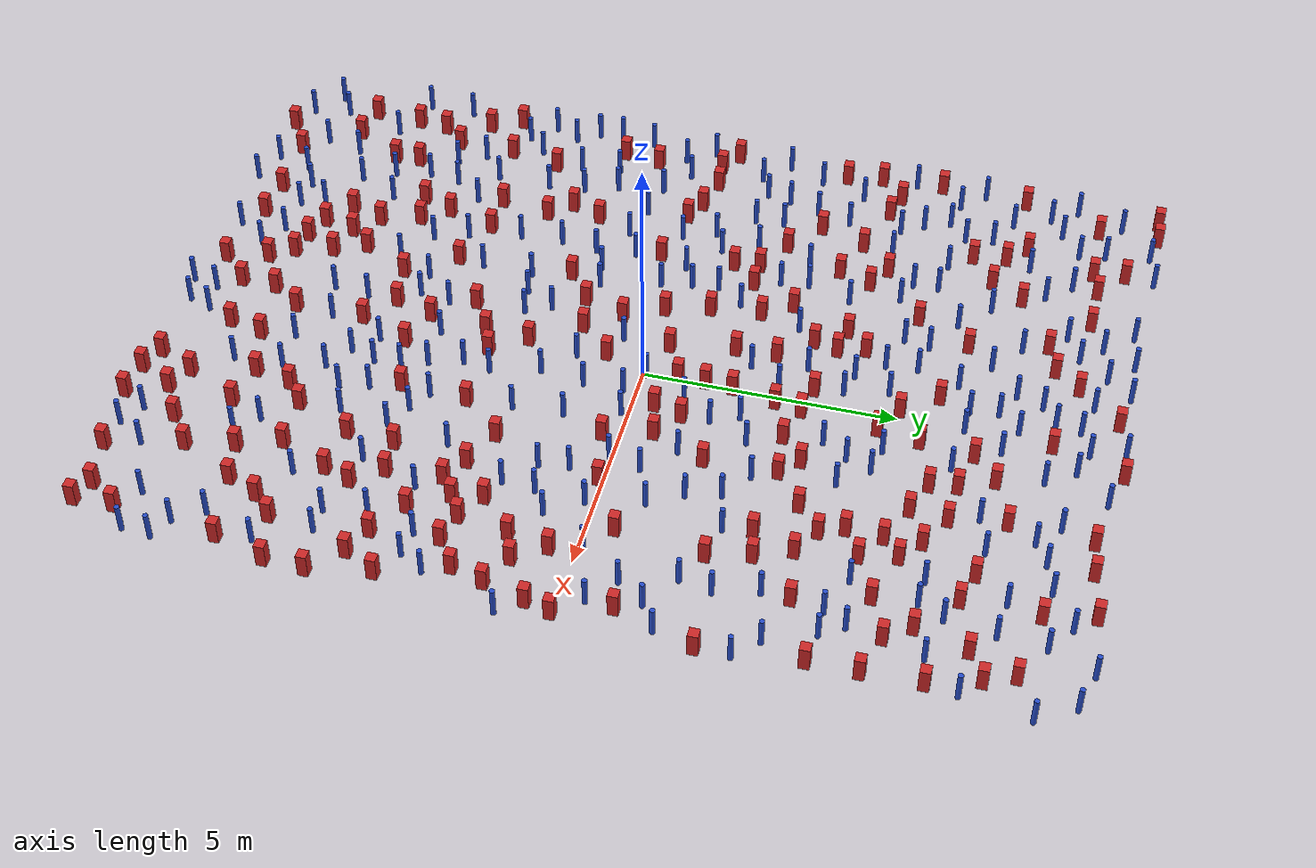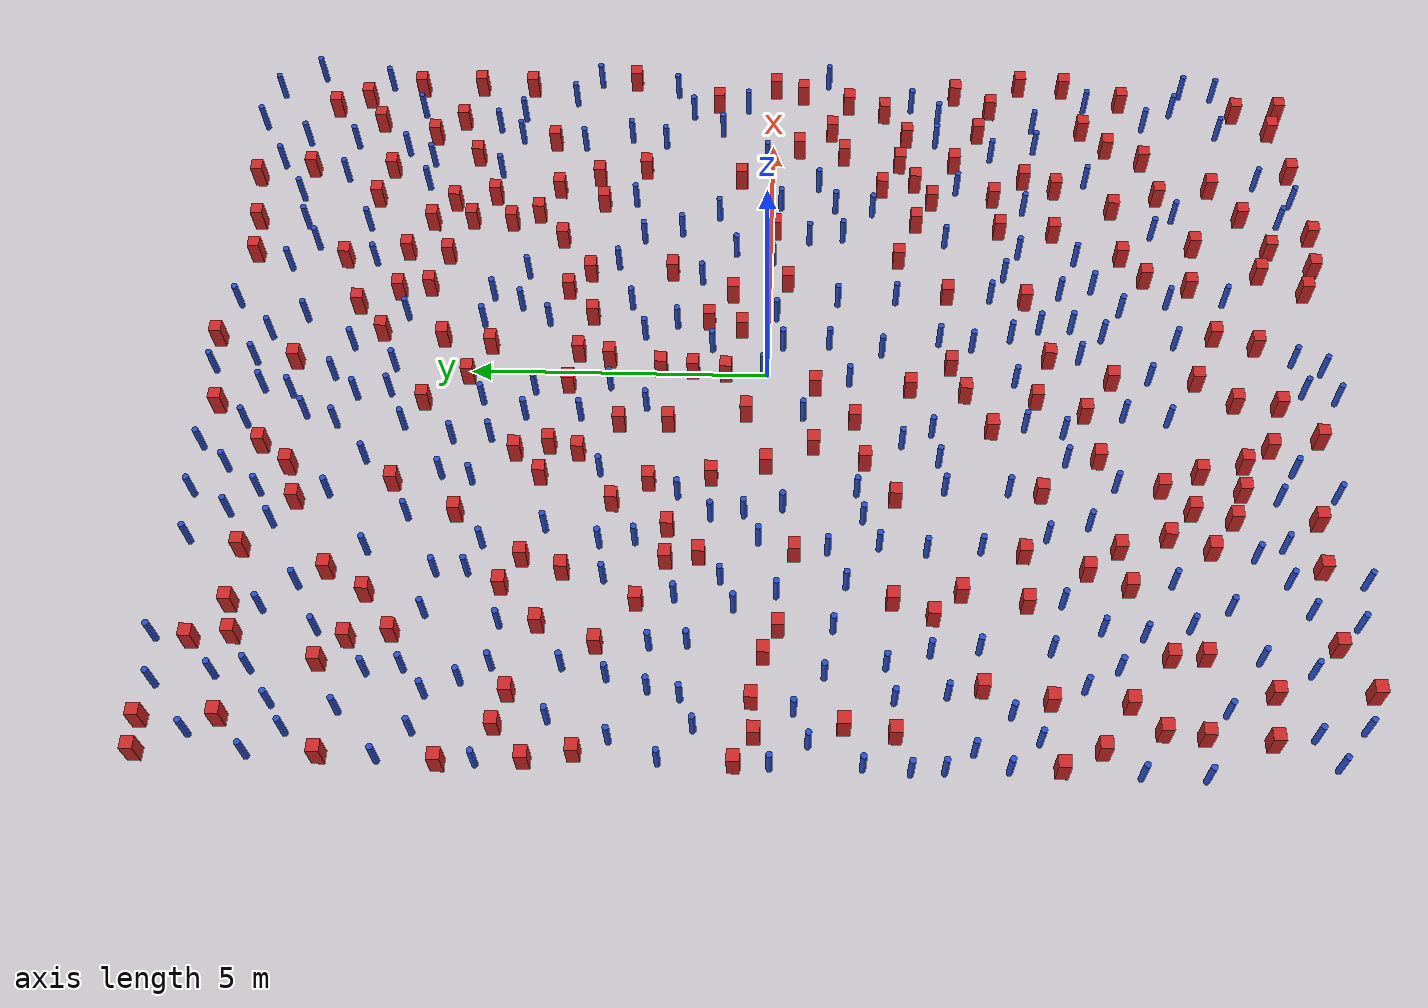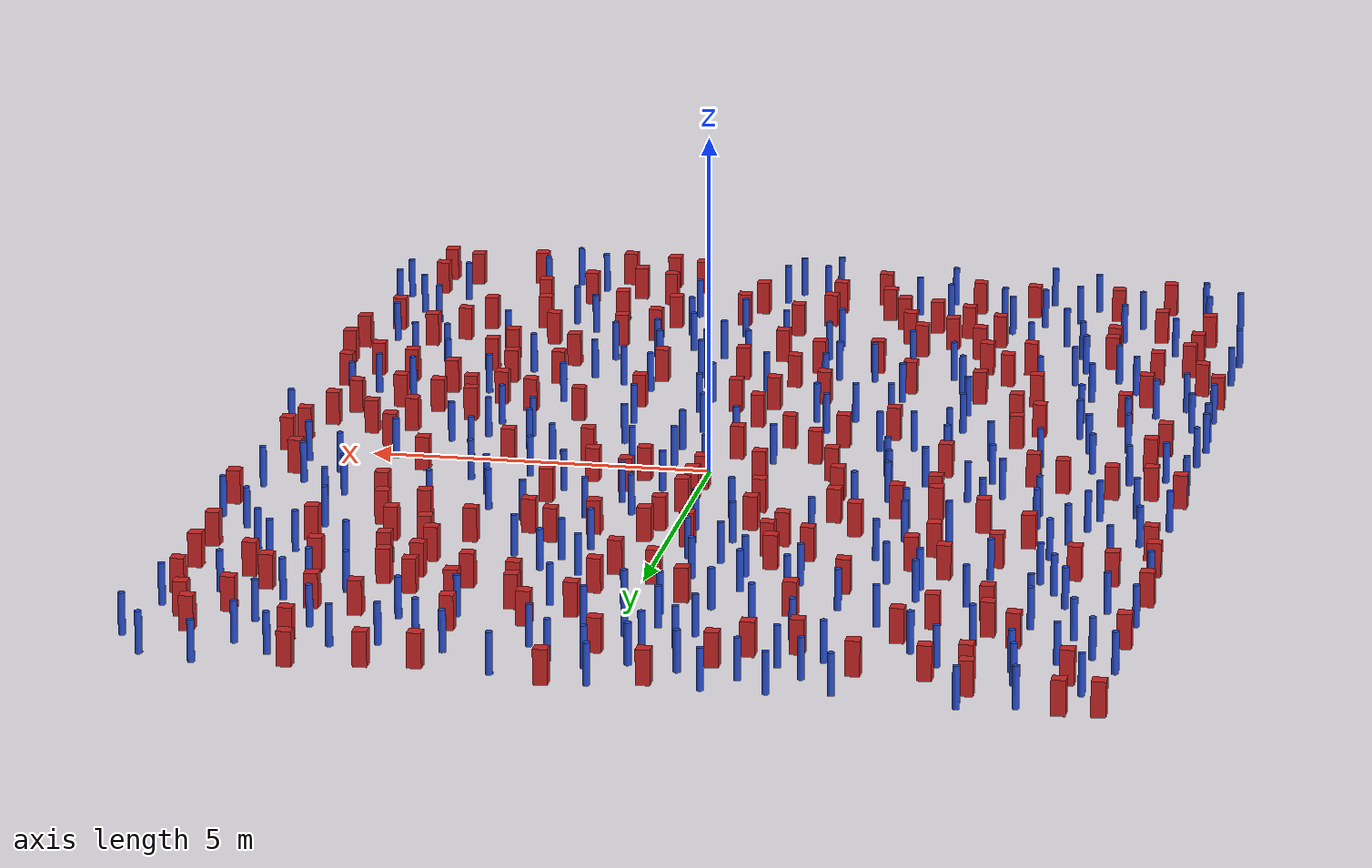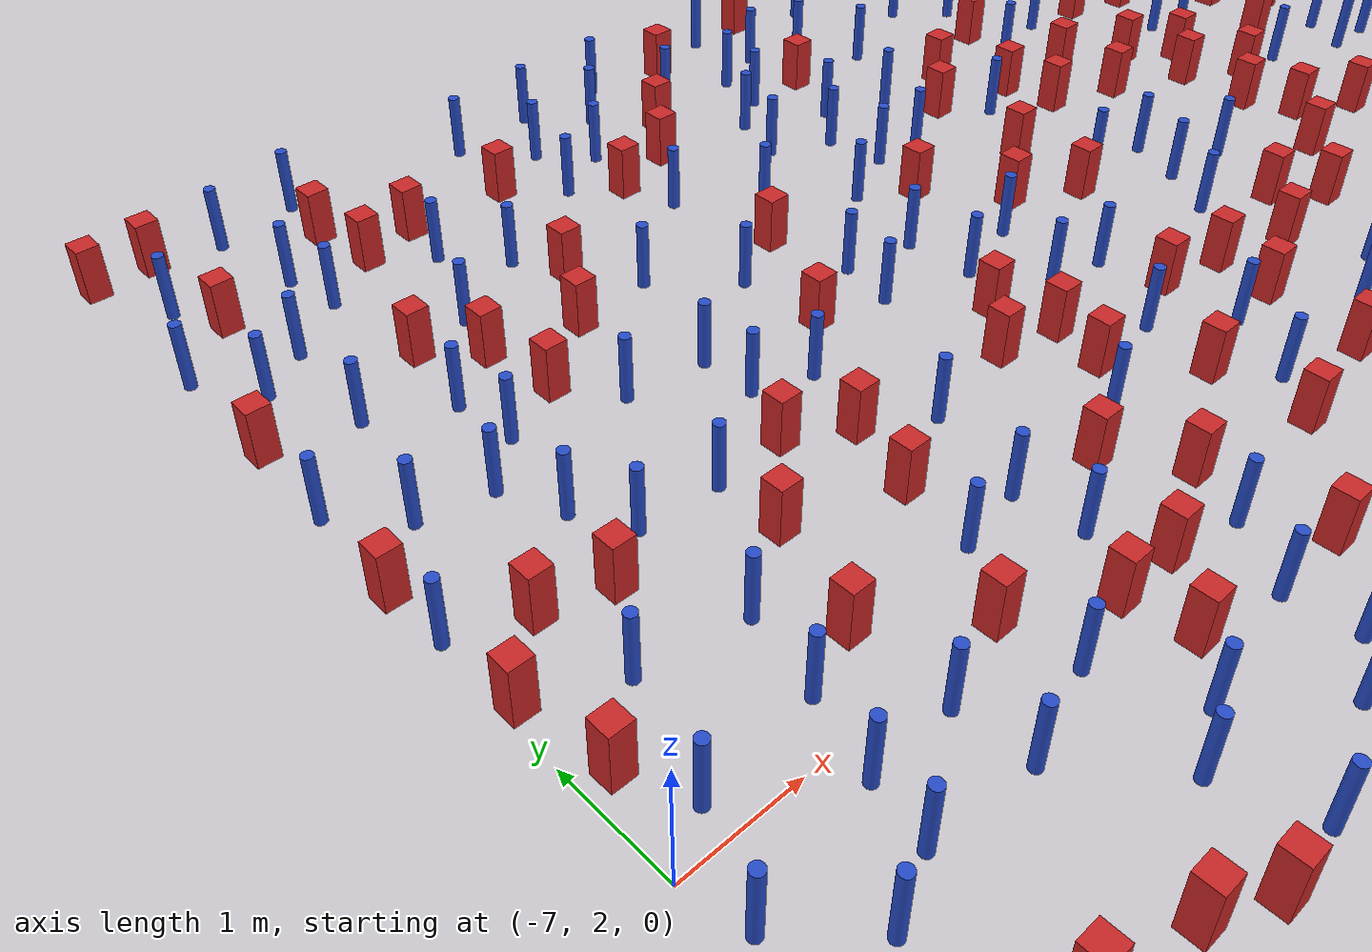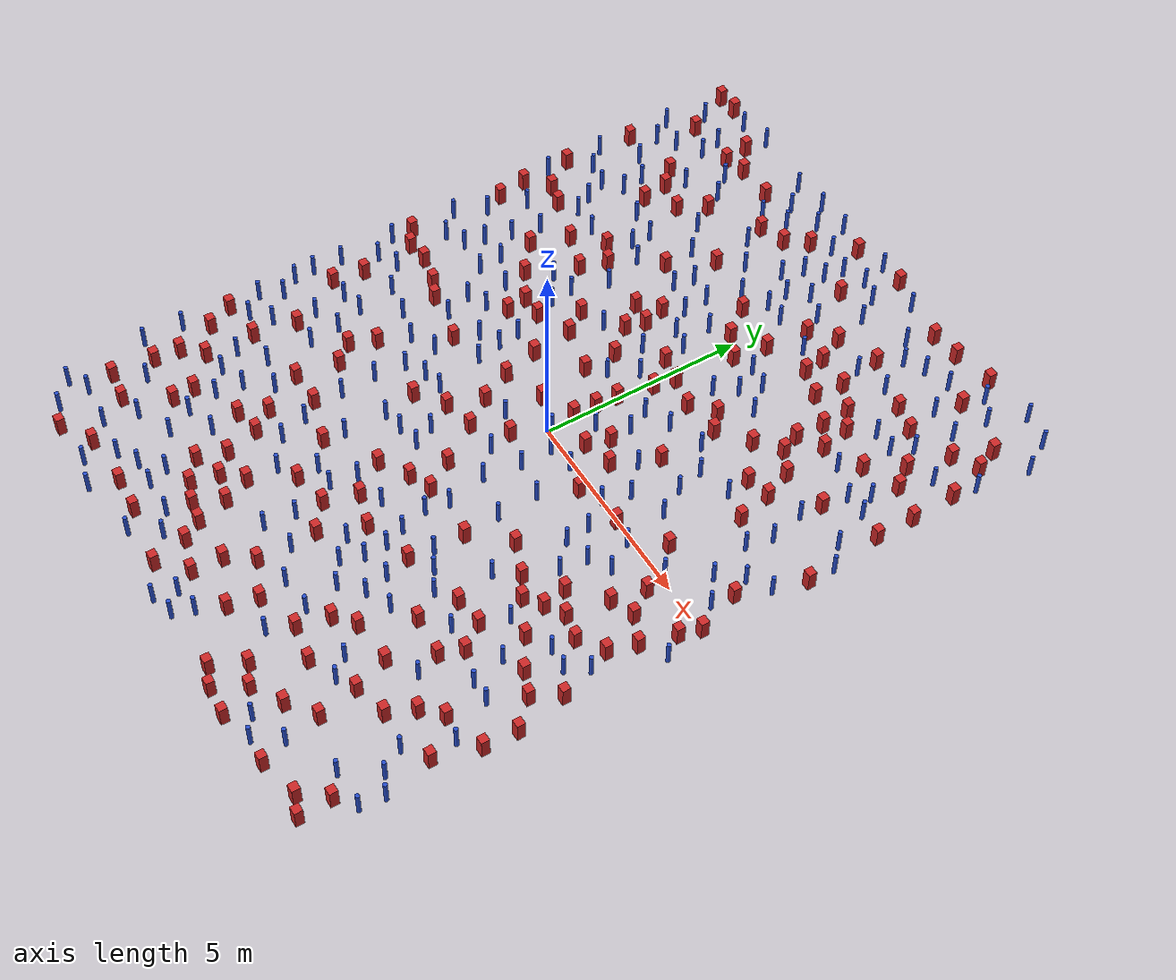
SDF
<sdf version="1.6">
  <model name="dense_7"><model name="square_post_obstacle0">
  <static>true</static>
  <pose frame="">3.18175804663 -2.55191059058 1.91545236811e-07 -7.35059704564e-06 1.12565212e-07 2.39332434364e-05</pose>
  <link name="link">
    <pose frame="">0 0 0.25 0 -0 0</pose>
    <inertial>
      <mass>100</mass>
      <inertia>
        <ixx>0.166667</ixx>
        <ixy>0</ixy>
        <ixz>0</ixz>
        <iyy>0.166667</iyy>
        <iyz>0</iyz>
        <izz>0.166667</izz>
      </inertia>
    </inertial>
    <collision name="collision">
      <geometry>
        <box>
          <size>.2 .2 .5</size>
        </box>
      </geometry>
      <max_contacts>10</max_contacts>
      <surface>
        <contact>
          <ode/>
        </contact>
        <bounce/>
        <friction>
          <torsional>
            <ode/>
          </torsional>
          <ode/>
        </friction>
      </surface>
    </collision>
    <visual name="visual">
      <geometry>
        <box>
          <size>.2 .2 .5</size>
        </box>
      </geometry>
      <material>
        <script>
          <name>Gazebo/Red</name>
          <uri>file://media/materials/scripts/gazebo.material</uri>
        </script>
      </material>
    </visual>
    <self_collide>0</self_collide>
    <kinematic>0</kinematic>
  </link>
</model>
<model name="square_post_obstacle1">
  <static>true</static>
  <pose frame="">-5.89802046448 0.14127891868 1.91545236811e-07 -7.35059704564e-06 1.12565212e-07 2.39332434364e-05</pose>
  <link name="link">
    <pose frame="">0 0 0.25 0 -0 0</pose>
    <inertial>
      <mass>100</mass>
      <inertia>
        <ixx>0.166667</ixx>
        <ixy>0</ixy>
        <ixz>0</ixz>
        <iyy>0.166667</iyy>
        <iyz>0</iyz>
        <izz>0.166667</izz>
      </inertia>
    </inertial>
    <collision name="collision">
      <geometry>
        <box>
          <size>.2 .2 .5</size>
        </box>
      </geometry>
      <max_contacts>10</max_contacts>
      <surface>
        <contact>
          <ode/>
        </contact>
        <bounce/>
        <friction>
          <torsional>
            <ode/>
          </torsional>
          <ode/>
        </friction>
      </surface>
    </collision>
    <visual name="visual">
      <geometry>
        <box>
          <size>.2 .2 .5</size>
        </box>
      </geometry>
      <material>
        <script>
          <name>Gazebo/Red</name>
          <uri>file://media/materials/scripts/gazebo.material</uri>
        </script>
      </material>
    </visual>
    <self_collide>0</self_collide>
    <kinematic>0</kinematic>
  </link>
</model>
<model name="pole_obstacle0">
  <static>true</static>
  <pose frame="">-0.847177458595 -6.63386567465 7.38925637345e-09 -8.471706928e-08 1.24976765086e-08 -1.74513093015e-07</pose>
  <link name="link">
  <pose frame="">0 0 0.3 0 -0 0</pose>
    <inertial>
      <mass>1</mass>
      <inertia>
        <ixx>0.145833</ixx>
        <ixy>0</ixy>
        <ixz>0</ixz>
        <iyy>0.145833</iyy>
        <iyz>0</iyz>
        <izz>0.125</izz>
      </inertia>
    </inertial>
    <collision name="collision">
      <geometry>
        <cylinder>
          <radius>0.05</radius>
          <length>.6</length>
        </cylinder>
      </geometry>
      <max_contacts>10</max_contacts>
      <surface>
        <contact>
          <ode/>
        </contact>
        <bounce/>
        <friction>
          <torsional>
            <ode/>
          </torsional>
          <ode/>
        </friction>
      </surface>
    </collision>
    <visual name="visual">
      <geometry>
        <cylinder>
          <radius>0.05</radius>
          <length>.6</length>
        </cylinder>
      </geometry>
      <material>
        <script>
          <name>Gazebo/Blue</name>
          <uri>file://media/materials/scripts/gazebo.material</uri>
        </script>
      </material>
    </visual>
    <self_collide>0</self_collide>
    <kinematic>0</kinematic>
  </link>
</model>
<model name="square_post_obstacle2">
  <static>true</static>
  <pose frame="">-6.2875825248 -1.26073202233 1.91545236811e-07 -7.35059704564e-06 1.12565212e-07 2.39332434364e-05</pose>
  <link name="link">
    <pose frame="">0 0 0.25 0 -0 0</pose>
    <inertial>
      <mass>100</mass>
      <inertia>
        <ixx>0.166667</ixx>
        <ixy>0</ixy>
        <ixz>0</ixz>
        <iyy>0.166667</iyy>
        <iyz>0</iyz>
        <izz>0.166667</izz>
      </inertia>
    </inertial>
    <collision name="collision">
      <geometry>
        <box>
          <size>.2 .2 .5</size>
        </box>
      </geometry>
      <max_contacts>10</max_contacts>
      <surface>
        <contact>
          <ode/>
        </contact>
        <bounce/>
        <friction>
          <torsional>
            <ode/>
          </torsional>
          <ode/>
        </friction>
      </surface>
    </collision>
    <visual name="visual">
      <geometry>
        <box>
          <size>.2 .2 .5</size>
        </box>
      </geometry>
      <material>
        <script>
          <name>Gazebo/Red</name>
          <uri>file://media/materials/scripts/gazebo.material</uri>
        </script>
      </material>
    </visual>
    <self_collide>0</self_collide>
    <kinematic>0</kinematic>
  </link>
</model>
<model name="pole_obstacle1">
  <static>true</static>
  <pose frame="">5.36775499733 -8.12371053254 7.38925637345e-09 -8.471706928e-08 1.24976765081e-08 -1.74513093015e-07</pose>
  <link name="link">
  <pose frame="">0 0 0.3 0 -0 0</pose>
    <inertial>
      <mass>1</mass>
      <inertia>
        <ixx>0.145833</ixx>
        <ixy>0</ixy>
        <ixz>0</ixz>
        <iyy>0.145833</iyy>
        <iyz>0</iyz>
        <izz>0.125</izz>
      </inertia>
    </inertial>
    <collision name="collision">
      <geometry>
        <cylinder>
          <radius>0.05</radius>
          <length>.6</length>
        </cylinder>
      </geometry>
      <max_contacts>10</max_contacts>
      <surface>
        <contact>
          <ode/>
        </contact>
        <bounce/>
        <friction>
          <torsional>
            <ode/>
          </torsional>
          <ode/>
        </friction>
      </surface>
    </collision>
    <visual name="visual">
      <geometry>
        <cylinder>
          <radius>0.05</radius>
          <length>.6</length>
        </cylinder>
      </geometry>
      <material>
        <script>
          <name>Gazebo/Blue</name>
          <uri>file://media/materials/scripts/gazebo.material</uri>
        </script>
      </material>
    </visual>
    <self_collide>0</self_collide>
    <kinematic>0</kinematic>
  </link>
</model>
<model name="square_post_obstacle3">
  <static>true</static>
  <pose frame="">-5.67274698728 -7.77645275839 1.91545236811e-07 -7.35059704564e-06 1.12565212e-07 2.39332434364e-05</pose>
  <link name="link">
    <pose frame="">0 0 0.25 0 -0 0</pose>
    <inertial>
      <mass>100</mass>
      <inertia>
        <ixx>0.166667</ixx>
        <ixy>0</ixy>
        <ixz>0</ixz>
        <iyy>0.166667</iyy>
        <iyz>0</iyz>
        <izz>0.166667</izz>
      </inertia>
    </inertial>
    <collision name="collision">
      <geometry>
        <box>
          <size>.2 .2 .5</size>
        </box>
      </geometry>
      <max_contacts>10</max_contacts>
      <surface>
        <contact>
          <ode/>
        </contact>
        <bounce/>
        <friction>
          <torsional>
            <ode/>
          </torsional>
          <ode/>
        </friction>
      </surface>
    </collision>
    <visual name="visual">
      <geometry>
        <box>
          <size>.2 .2 .5</size>
        </box>
      </geometry>
      <material>
        <script>
          <name>Gazebo/Red</name>
          <uri>file://media/materials/scripts/gazebo.material</uri>
        </script>
      </material>
    </visual>
    <self_collide>0</self_collide>
    <kinematic>0</kinematic>
  </link>
</model>
<model name="pole_obstacle2">
  <static>true</static>
  <pose frame="">1.06586460328 6.21019038955 7.38925637345e-09 -8.47170692799e-08 1.24976765033e-08 -1.74513093018e-07</pose>
  <link name="link">
  <pose frame="">0 0 0.3 0 -0 0</pose>
    <inertial>
      <mass>1</mass>
      <inertia>
        <ixx>0.145833</ixx>
        <ixy>0</ixy>
        <ixz>0</ixz>
        <iyy>0.145833</iyy>
        <iyz>0</iyz>
        <izz>0.125</izz>
      </inertia>
    </inertial>
    <collision name="collision">
      <geometry>
        <cylinder>
          <radius>0.05</radius>
          <length>.6</length>
        </cylinder>
      </geometry>
      <max_contacts>10</max_contacts>
      <surface>
        <contact>
          <ode/>
        </contact>
        <bounce/>
        <friction>
          <torsional>
            <ode/>
          </torsional>
          <ode/>
        </friction>
      </surface>
    </collision>
    <visual name="visual">
      <geometry>
        <cylinder>
          <radius>0.05</radius>
          <length>.6</length>
        </cylinder>
      </geometry>
      <material>
        <script>
          <name>Gazebo/Blue</name>
          <uri>file://media/materials/scripts/gazebo.material</uri>
        </script>
      </material>
    </visual>
    <self_collide>0</self_collide>
    <kinematic>0</kinematic>
  </link>
</model>
<model name="pole_obstacle3">
  <static>true</static>
  <pose frame="">-4.64776272858 -5.25845965169 7.38925637345e-09 -8.47170692796e-08 1.24976764786e-08 -1.74513093032e-07</pose>
  <link name="link">
  <pose frame="">0 0 0.3 0 -0 0</pose>
    <inertial>
      <mass>1</mass>
      <inertia>
        <ixx>0.145833</ixx>
        <ixy>0</ixy>
        <ixz>0</ixz>
        <iyy>0.145833</iyy>
        <iyz>0</iyz>
        <izz>0.125</izz>
      </inertia>
    </inertial>
    <collision name="collision">
      <geometry>
        <cylinder>
          <radius>0.05</radius>
          <length>.6</length>
        </cylinder>
      </geometry>
      <max_contacts>10</max_contacts>
      <surface>
        <contact>
          <ode/>
        </contact>
        <bounce/>
        <friction>
          <torsional>
            <ode/>
          </torsional>
          <ode/>
        </friction>
      </surface>
    </collision>
    <visual name="visual">
      <geometry>
        <cylinder>
          <radius>0.05</radius>
          <length>.6</length>
        </cylinder>
      </geometry>
      <material>
        <script>
          <name>Gazebo/Blue</name>
          <uri>file://media/materials/scripts/gazebo.material</uri>
        </script>
      </material>
    </visual>
    <self_collide>0</self_collide>
    <kinematic>0</kinematic>
  </link>
</model>
<model name="square_post_obstacle4">
  <static>true</static>
  <pose frame="">3.96495598854 -1.96307099355 1.91545236811e-07 -7.35059704564e-06 1.12565212e-07 2.39332434364e-05</pose>
  <link name="link">
    <pose frame="">0 0 0.25 0 -0 0</pose>
    <inertial>
      <mass>100</mass>
      <inertia>
        <ixx>0.166667</ixx>
        <ixy>0</ixy>
        <ixz>0</ixz>
        <iyy>0.166667</iyy>
        <iyz>0</iyz>
        <izz>0.166667</izz>
      </inertia>
    </inertial>
    <collision name="collision">
      <geometry>
        <box>
          <size>.2 .2 .5</size>
        </box>
      </geometry>
      <max_contacts>10</max_contacts>
      <surface>
        <contact>
          <ode/>
        </contact>
        <bounce/>
        <friction>
          <torsional>
            <ode/>
          </torsional>
          <ode/>
        </friction>
      </surface>
    </collision>
    <visual name="visual">
      <geometry>
        <box>
          <size>.2 .2 .5</size>
        </box>
      </geometry>
      <material>
        <script>
          <name>Gazebo/Red</name>
          <uri>file://media/materials/scripts/gazebo.material</uri>
        </script>
      </material>
    </visual>
    <self_collide>0</self_collide>
    <kinematic>0</kinematic>
  </link>
</model>
<model name="square_post_obstacle5">
  <static>true</static>
  <pose frame="">-3.56619881664 1.55040309767 1.91545236811e-07 -7.35059704564e-06 1.12565212e-07 2.39332434364e-05</pose>
  <link name="link">
    <pose frame="">0 0 0.25 0 -0 0</pose>
    <inertial>
      <mass>100</mass>
      <inertia>
        <ixx>0.166667</ixx>
        <ixy>0</ixy>
        <ixz>0</ixz>
        <iyy>0.166667</iyy>
        <iyz>0</iyz>
        <izz>0.166667</izz>
      </inertia>
    </inertial>
    <collision name="collision">
      <geometry>
        <box>
          <size>.2 .2 .5</size>
        </box>
      </geometry>
      <max_contacts>10</max_contacts>
      <surface>
        <contact>
          <ode/>
        </contact>
        <bounce/>
        <friction>
          <torsional>
            <ode/>
          </torsional>
          <ode/>
        </friction>
      </surface>
    </collision>
    <visual name="visual">
      <geometry>
        <box>
          <size>.2 .2 .5</size>
        </box>
      </geometry>
      <material>
        <script>
          <name>Gazebo/Red</name>
          <uri>file://media/materials/scripts/gazebo.material</uri>
        </script>
      </material>
    </visual>
    <self_collide>0</self_collide>
    <kinematic>0</kinematic>
  </link>
</model>
<model name="square_post_obstacle6">
  <static>true</static>
  <pose frame="">5.1393558744 -2.42444670013 1.91545236811e-07 -7.35059704564e-06 1.12565212e-07 2.39332434364e-05</pose>
  <link name="link">
    <pose frame="">0 0 0.25 0 -0 0</pose>
    <inertial>
      <mass>100</mass>
      <inertia>
        <ixx>0.166667</ixx>
        <ixy>0</ixy>
        <ixz>0</ixz>
        <iyy>0.166667</iyy>
        <iyz>0</iyz>
        <izz>0.166667</izz>
      </inertia>
    </inertial>
    <collision name="collision">
      <geometry>
        <box>
          <size>.2 .2 .5</size>
        </box>
      </geometry>
      <max_contacts>10</max_contacts>
      <surface>
        <contact>
          <ode/>
        </contact>
        <bounce/>
        <friction>
          <torsional>
            <ode/>
          </torsional>
          <ode/>
        </friction>
      </surface>
    </collision>
    <visual name="visual">
      <geometry>
        <box>
          <size>.2 .2 .5</size>
        </box>
      </geometry>
      <material>
        <script>
          <name>Gazebo/Red</name>
          <uri>file://media/materials/scripts/gazebo.material</uri>
        </script>
      </material>
    </visual>
    <self_collide>0</self_collide>
    <kinematic>0</kinematic>
  </link>
</model>
<model name="pole_obstacle4">
  <static>true</static>
  <pose frame="">4.92123123528 8.50646992746 7.38925637345e-09 -8.471706928e-08 1.24976765081e-08 -1.74513093015e-07</pose>
  <link name="link">
  <pose frame="">0 0 0.3 0 -0 0</pose>
    <inertial>
      <mass>1</mass>
      <inertia>
        <ixx>0.145833</ixx>
        <ixy>0</ixy>
        <ixz>0</ixz>
        <iyy>0.145833</iyy>
        <iyz>0</iyz>
        <izz>0.125</izz>
      </inertia>
    </inertial>
    <collision name="collision">
      <geometry>
        <cylinder>
          <radius>0.05</radius>
          <length>.6</length>
        </cylinder>
      </geometry>
      <max_contacts>10</max_contacts>
      <surface>
        <contact>
          <ode/>
        </contact>
        <bounce/>
        <friction>
          <torsional>
            <ode/>
          </torsional>
          <ode/>
        </friction>
      </surface>
    </collision>
    <visual name="visual">
      <geometry>
        <cylinder>
          <radius>0.05</radius>
          <length>.6</length>
        </cylinder>
      </geometry>
      <material>
        <script>
          <name>Gazebo/Blue</name>
          <uri>file://media/materials/scripts/gazebo.material</uri>
        </script>
      </material>
    </visual>
    <self_collide>0</self_collide>
    <kinematic>0</kinematic>
  </link>
</model>
<model name="pole_obstacle5">
  <static>true</static>
  <pose frame="">-4.25915340663 -7.26194745573 7.38925637345e-09 -8.47170692796e-08 1.24976764786e-08 -1.74513093032e-07</pose>
  <link name="link">
  <pose frame="">0 0 0.3 0 -0 0</pose>
    <inertial>
      <mass>1</mass>
      <inertia>
        <ixx>0.145833</ixx>
        <ixy>0</ixy>
        <ixz>0</ixz>
        <iyy>0.145833</iyy>
        <iyz>0</iyz>
        <izz>0.125</izz>
      </inertia>
    </inertial>
    <collision name="collision">
      <geometry>
        <cylinder>
          <radius>0.05</radius>
          <length>.6</length>
        </cylinder>
      </geometry>
      <max_contacts>10</max_contacts>
      <surface>
        <contact>
          <ode/>
        </contact>
        <bounce/>
        <friction>
          <torsional>
            <ode/>
          </torsional>
          <ode/>
        </friction>
      </surface>
    </collision>
    <visual name="visual">
      <geometry>
        <cylinder>
          <radius>0.05</radius>
          <length>.6</length>
        </cylinder>
      </geometry>
      <material>
        <script>
          <name>Gazebo/Blue</name>
          <uri>file://media/materials/scripts/gazebo.material</uri>
        </script>
      </material>
    </visual>
    <self_collide>0</self_collide>
    <kinematic>0</kinematic>
  </link>
</model>
<model name="square_post_obstacle7">
  <static>true</static>
  <pose frame="">3.40714481329 -8.30700948743 1.91545236811e-07 -7.35059704564e-06 1.12565212e-07 2.39332434364e-05</pose>
  <link name="link">
    <pose frame="">0 0 0.25 0 -0 0</pose>
    <inertial>
      <mass>100</mass>
      <inertia>
        <ixx>0.166667</ixx>
        <ixy>0</ixy>
        <ixz>0</ixz>
        <iyy>0.166667</iyy>
        <iyz>0</iyz>
        <izz>0.166667</izz>
      </inertia>
    </inertial>
    <collision name="collision">
      <geometry>
        <box>
          <size>.2 .2 .5</size>
        </box>
      </geometry>
      <max_contacts>10</max_contacts>
      <surface>
        <contact>
          <ode/>
        </contact>
        <bounce/>
        <friction>
          <torsional>
            <ode/>
          </torsional>
          <ode/>
        </friction>
      </surface>
    </collision>
    <visual name="visual">
      <geometry>
        <box>
          <size>.2 .2 .5</size>
        </box>
      </geometry>
      <material>
        <script>
          <name>Gazebo/Red</name>
          <uri>file://media/materials/scripts/gazebo.material</uri>
        </script>
      </material>
    </visual>
    <self_collide>0</self_collide>
    <kinematic>0</kinematic>
  </link>
</model>
<model name="square_post_obstacle8">
  <static>true</static>
  <pose frame="">-5.86757780584 -5.58678446835 1.91545236811e-07 -7.35059704564e-06 1.12565212e-07 2.39332434364e-05</pose>
  <link name="link">
    <pose frame="">0 0 0.25 0 -0 0</pose>
    <inertial>
      <mass>100</mass>
      <inertia>
        <ixx>0.166667</ixx>
        <ixy>0</ixy>
        <ixz>0</ixz>
        <iyy>0.166667</iyy>
        <iyz>0</iyz>
        <izz>0.166667</izz>
      </inertia>
    </inertial>
    <collision name="collision">
      <geometry>
        <box>
          <size>.2 .2 .5</size>
        </box>
      </geometry>
      <max_contacts>10</max_contacts>
      <surface>
        <contact>
          <ode/>
        </contact>
        <bounce/>
        <friction>
          <torsional>
            <ode/>
          </torsional>
          <ode/>
        </friction>
      </surface>
    </collision>
    <visual name="visual">
      <geometry>
        <box>
          <size>.2 .2 .5</size>
        </box>
      </geometry>
      <material>
        <script>
          <name>Gazebo/Red</name>
          <uri>file://media/materials/scripts/gazebo.material</uri>
        </script>
      </material>
    </visual>
    <self_collide>0</self_collide>
    <kinematic>0</kinematic>
  </link>
</model>
<model name="pole_obstacle6">
  <static>true</static>
  <pose frame="">-1.13884533249 6.00640084406 7.38925637345e-09 -8.47170692799e-08 1.24976765033e-08 -1.74513093018e-07</pose>
  <link name="link">
  <pose frame="">0 0 0.3 0 -0 0</pose>
    <inertial>
      <mass>1</mass>
      <inertia>
        <ixx>0.145833</ixx>
        <ixy>0</ixy>
        <ixz>0</ixz>
        <iyy>0.145833</iyy>
        <iyz>0</iyz>
        <izz>0.125</izz>
      </inertia>
    </inertial>
    <collision name="collision">
      <geometry>
        <cylinder>
          <radius>0.05</radius>
          <length>.6</length>
        </cylinder>
      </geometry>
      <max_contacts>10</max_contacts>
      <surface>
        <contact>
          <ode/>
        </contact>
        <bounce/>
        <friction>
          <torsional>
            <ode/>
          </torsional>
          <ode/>
        </friction>
      </surface>
    </collision>
    <visual name="visual">
      <geometry>
        <cylinder>
          <radius>0.05</radius>
          <length>.6</length>
        </cylinder>
      </geometry>
      <material>
        <script>
          <name>Gazebo/Blue</name>
          <uri>file://media/materials/scripts/gazebo.material</uri>
        </script>
      </material>
    </visual>
    <self_collide>0</self_collide>
    <kinematic>0</kinematic>
  </link>
</model>
<model name="pole_obstacle7">
  <static>true</static>
  <pose frame="">1.61050316062 -3.80442703881 7.38925637345e-09 -8.47170692799e-08 1.24976765053e-08 -1.74513093017e-07</pose>
  <link name="link">
  <pose frame="">0 0 0.3 0 -0 0</pose>
    <inertial>
      <mass>1</mass>
      <inertia>
        <ixx>0.145833</ixx>
        <ixy>0</ixy>
        <ixz>0</ixz>
        <iyy>0.145833</iyy>
        <iyz>0</iyz>
        <izz>0.125</izz>
      </inertia>
    </inertial>
    <collision name="collision">
      <geometry>
        <cylinder>
          <radius>0.05</radius>
          <length>.6</length>
        </cylinder>
      </geometry>
      <max_contacts>10</max_contacts>
      <surface>
        <contact>
          <ode/>
        </contact>
        <bounce/>
        <friction>
          <torsional>
            <ode/>
          </torsional>
          <ode/>
        </friction>
      </surface>
    </collision>
    <visual name="visual">
      <geometry>
        <cylinder>
          <radius>0.05</radius>
          <length>.6</length>
        </cylinder>
      </geometry>
      <material>
        <script>
          <name>Gazebo/Blue</name>
          <uri>file://media/materials/scripts/gazebo.material</uri>
        </script>
      </material>
    </visual>
    <self_collide>0</self_collide>
    <kinematic>0</kinematic>
  </link>
</model>
<model name="square_post_obstacle9">
  <static>true</static>
  <pose frame="">5.92759945526 -1.3757462042 1.91545236811e-07 -7.35059704564e-06 1.12565212e-07 2.39332434364e-05</pose>
  <link name="link">
    <pose frame="">0 0 0.25 0 -0 0</pose>
    <inertial>
      <mass>100</mass>
      <inertia>
        <ixx>0.166667</ixx>
        <ixy>0</ixy>
        <ixz>0</ixz>
        <iyy>0.166667</iyy>
        <iyz>0</iyz>
        <izz>0.166667</izz>
      </inertia>
    </inertial>
    <collision name="collision">
      <geometry>
        <box>
          <size>.2 .2 .5</size>
        </box>
      </geometry>
      <max_contacts>10</max_contacts>
      <surface>
        <contact>
          <ode/>
        </contact>
        <bounce/>
        <friction>
          <torsional>
            <ode/>
          </torsional>
          <ode/>
        </friction>
      </surface>
    </collision>
    <visual name="visual">
      <geometry>
        <box>
          <size>.2 .2 .5</size>
        </box>
      </geometry>
      <material>
        <script>
          <name>Gazebo/Red</name>
          <uri>file://media/materials/scripts/gazebo.material</uri>
        </script>
      </material>
    </visual>
    <self_collide>0</self_collide>
    <kinematic>0</kinematic>
  </link>
</model>
<model name="square_post_obstacle10">
  <static>true</static>
  <pose frame="">-1.03120379804 1.62567539473 1.91545236811e-07 -7.35059704564e-06 1.12565212e-07 2.39332434364e-05</pose>
  <link name="link">
    <pose frame="">0 0 0.25 0 -0 0</pose>
    <inertial>
      <mass>100</mass>
      <inertia>
        <ixx>0.166667</ixx>
        <ixy>0</ixy>
        <ixz>0</ixz>
        <iyy>0.166667</iyy>
        <iyz>0</iyz>
        <izz>0.166667</izz>
      </inertia>
    </inertial>
    <collision name="collision">
      <geometry>
        <box>
          <size>.2 .2 .5</size>
        </box>
      </geometry>
      <max_contacts>10</max_contacts>
      <surface>
        <contact>
          <ode/>
        </contact>
        <bounce/>
        <friction>
          <torsional>
            <ode/>
          </torsional>
          <ode/>
        </friction>
      </surface>
    </collision>
    <visual name="visual">
      <geometry>
        <box>
          <size>.2 .2 .5</size>
        </box>
      </geometry>
      <material>
        <script>
          <name>Gazebo/Red</name>
          <uri>file://media/materials/scripts/gazebo.material</uri>
        </script>
      </material>
    </visual>
    <self_collide>0</self_collide>
    <kinematic>0</kinematic>
  </link>
</model>
<model name="square_post_obstacle11">
  <static>true</static>
  <pose frame="">2.00786837578 3.1188918921 1.91545236811e-07 -7.35059704564e-06 1.12565212e-07 2.39332434364e-05</pose>
  <link name="link">
    <pose frame="">0 0 0.25 0 -0 0</pose>
    <inertial>
      <mass>100</mass>
      <inertia>
        <ixx>0.166667</ixx>
        <ixy>0</ixy>
        <ixz>0</ixz>
        <iyy>0.166667</iyy>
        <iyz>0</iyz>
        <izz>0.166667</izz>
      </inertia>
    </inertial>
    <collision name="collision">
      <geometry>
        <box>
          <size>.2 .2 .5</size>
        </box>
      </geometry>
      <max_contacts>10</max_contacts>
      <surface>
        <contact>
          <ode/>
        </contact>
        <bounce/>
        <friction>
          <torsional>
            <ode/>
          </torsional>
          <ode/>
        </friction>
      </surface>
    </collision>
    <visual name="visual">
      <geometry>
        <box>
          <size>.2 .2 .5</size>
        </box>
      </geometry>
      <material>
        <script>
          <name>Gazebo/Red</name>
          <uri>file://media/materials/scripts/gazebo.material</uri>
        </script>
      </material>
    </visual>
    <self_collide>0</self_collide>
    <kinematic>0</kinematic>
  </link>
</model>
<model name="square_post_obstacle12">
  <static>true</static>
  <pose frame="">-5.84728091085 3.82834839286 1.91545236811e-07 -7.35059704564e-06 1.12565212e-07 2.39332434364e-05</pose>
  <link name="link">
    <pose frame="">0 0 0.25 0 -0 0</pose>
    <inertial>
      <mass>100</mass>
      <inertia>
        <ixx>0.166667</ixx>
        <ixy>0</ixy>
        <ixz>0</ixz>
        <iyy>0.166667</iyy>
        <iyz>0</iyz>
        <izz>0.166667</izz>
      </inertia>
    </inertial>
    <collision name="collision">
      <geometry>
        <box>
          <size>.2 .2 .5</size>
        </box>
      </geometry>
      <max_contacts>10</max_contacts>
      <surface>
        <contact>
          <ode/>
        </contact>
        <bounce/>
        <friction>
          <torsional>
            <ode/>
          </torsional>
          <ode/>
        </friction>
      </surface>
    </collision>
    <visual name="visual">
      <geometry>
        <box>
          <size>.2 .2 .5</size>
        </box>
      </geometry>
      <material>
        <script>
          <name>Gazebo/Red</name>
          <uri>file://media/materials/scripts/gazebo.material</uri>
        </script>
      </material>
    </visual>
    <self_collide>0</self_collide>
    <kinematic>0</kinematic>
  </link>
</model>
<model name="square_post_obstacle13">
  <static>true</static>
  <pose frame="">0.330037371292 3.20440158988 1.91545236811e-07 -7.35059704564e-06 1.12565212e-07 2.39332434364e-05</pose>
  <link name="link">
    <pose frame="">0 0 0.25 0 -0 0</pose>
    <inertial>
      <mass>100</mass>
      <inertia>
        <ixx>0.166667</ixx>
        <ixy>0</ixy>
        <ixz>0</ixz>
        <iyy>0.166667</iyy>
        <iyz>0</iyz>
        <izz>0.166667</izz>
      </inertia>
    </inertial>
    <collision name="collision">
      <geometry>
        <box>
          <size>.2 .2 .5</size>
        </box>
      </geometry>
      <max_contacts>10</max_contacts>
      <surface>
        <contact>
          <ode/>
        </contact>
        <bounce/>
        <friction>
          <torsional>
            <ode/>
          </torsional>
          <ode/>
        </friction>
      </surface>
    </collision>
    <visual name="visual">
      <geometry>
        <box>
          <size>.2 .2 .5</size>
        </box>
      </geometry>
      <material>
        <script>
          <name>Gazebo/Red</name>
          <uri>file://media/materials/scripts/gazebo.material</uri>
        </script>
      </material>
    </visual>
    <self_collide>0</self_collide>
    <kinematic>0</kinematic>
  </link>
</model>
<model name="pole_obstacle8">
  <static>true</static>
  <pose frame="">-2.3621662867 1.4140505157 7.38925637345e-09 -8.471706928e-08 1.24976765152e-08 -1.74513093012e-07</pose>
  <link name="link">
  <pose frame="">0 0 0.3 0 -0 0</pose>
    <inertial>
      <mass>1</mass>
      <inertia>
        <ixx>0.145833</ixx>
        <ixy>0</ixy>
        <ixz>0</ixz>
        <iyy>0.145833</iyy>
        <iyz>0</iyz>
        <izz>0.125</izz>
      </inertia>
    </inertial>
    <collision name="collision">
      <geometry>
        <cylinder>
          <radius>0.05</radius>
          <length>.6</length>
        </cylinder>
      </geometry>
      <max_contacts>10</max_contacts>
      <surface>
        <contact>
          <ode/>
        </contact>
        <bounce/>
        <friction>
          <torsional>
            <ode/>
          </torsional>
          <ode/>
        </friction>
      </surface>
    </collision>
    <visual name="visual">
      <geometry>
        <cylinder>
          <radius>0.05</radius>
          <length>.6</length>
        </cylinder>
      </geometry>
      <material>
        <script>
          <name>Gazebo/Blue</name>
          <uri>file://media/materials/scripts/gazebo.material</uri>
        </script>
      </material>
    </visual>
    <self_collide>0</self_collide>
    <kinematic>0</kinematic>
  </link>
</model>
<model name="square_post_obstacle14">
  <static>true</static>
  <pose frame="">-1.70999980943 -1.6093661849 1.91545236811e-07 -7.35059704564e-06 1.12565212e-07 2.39332434364e-05</pose>
  <link name="link">
    <pose frame="">0 0 0.25 0 -0 0</pose>
    <inertial>
      <mass>100</mass>
      <inertia>
        <ixx>0.166667</ixx>
        <ixy>0</ixy>
        <ixz>0</ixz>
        <iyy>0.166667</iyy>
        <iyz>0</iyz>
        <izz>0.166667</izz>
      </inertia>
    </inertial>
    <collision name="collision">
      <geometry>
        <box>
          <size>.2 .2 .5</size>
        </box>
      </geometry>
      <max_contacts>10</max_contacts>
      <surface>
        <contact>
          <ode/>
        </contact>
        <bounce/>
        <friction>
          <torsional>
            <ode/>
          </torsional>
          <ode/>
        </friction>
      </surface>
    </collision>
    <visual name="visual">
      <geometry>
        <box>
          <size>.2 .2 .5</size>
        </box>
      </geometry>
      <material>
        <script>
          <name>Gazebo/Red</name>
          <uri>file://media/materials/scripts/gazebo.material</uri>
        </script>
      </material>
    </visual>
    <self_collide>0</self_collide>
    <kinematic>0</kinematic>
  </link>
</model>
<model name="square_post_obstacle15">
  <static>true</static>
  <pose frame="">-3.65186319388 -5.09281954235 1.91545236811e-07 -7.35059704564e-06 1.12565212e-07 2.39332434364e-05</pose>
  <link name="link">
    <pose frame="">0 0 0.25 0 -0 0</pose>
    <inertial>
      <mass>100</mass>
      <inertia>
        <ixx>0.166667</ixx>
        <ixy>0</ixy>
        <ixz>0</ixz>
        <iyy>0.166667</iyy>
        <iyz>0</iyz>
        <izz>0.166667</izz>
      </inertia>
    </inertial>
    <collision name="collision">
      <geometry>
        <box>
          <size>.2 .2 .5</size>
        </box>
      </geometry>
      <max_contacts>10</max_contacts>
      <surface>
        <contact>
          <ode/>
        </contact>
        <bounce/>
        <friction>
          <torsional>
            <ode/>
          </torsional>
          <ode/>
        </friction>
      </surface>
    </collision>
    <visual name="visual">
      <geometry>
        <box>
          <size>.2 .2 .5</size>
        </box>
      </geometry>
      <material>
        <script>
          <name>Gazebo/Red</name>
          <uri>file://media/materials/scripts/gazebo.material</uri>
        </script>
      </material>
    </visual>
    <self_collide>0</self_collide>
    <kinematic>0</kinematic>
  </link>
</model>
<model name="square_post_obstacle16">
  <static>true</static>
  <pose frame="">4.19334653572 -4.50781424525 1.91545236811e-07 -7.35059704564e-06 1.12565212e-07 2.39332434364e-05</pose>
  <link name="link">
    <pose frame="">0 0 0.25 0 -0 0</pose>
    <inertial>
      <mass>100</mass>
      <inertia>
        <ixx>0.166667</ixx>
        <ixy>0</ixy>
        <ixz>0</ixz>
        <iyy>0.166667</iyy>
        <iyz>0</iyz>
        <izz>0.166667</izz>
      </inertia>
    </inertial>
    <collision name="collision">
      <geometry>
        <box>
          <size>.2 .2 .5</size>
        </box>
      </geometry>
      <max_contacts>10</max_contacts>
      <surface>
        <contact>
          <ode/>
        </contact>
        <bounce/>
        <friction>
          <torsional>
            <ode/>
          </torsional>
          <ode/>
        </friction>
      </surface>
    </collision>
    <visual name="visual">
      <geometry>
        <box>
          <size>.2 .2 .5</size>
        </box>
      </geometry>
      <material>
        <script>
          <name>Gazebo/Red</name>
          <uri>file://media/materials/scripts/gazebo.material</uri>
        </script>
      </material>
    </visual>
    <self_collide>0</self_collide>
    <kinematic>0</kinematic>
  </link>
</model>
<model name="pole_obstacle9">
  <static>true</static>
  <pose frame="">2.97873358199 7.12761243668 7.38925637345e-09 -8.47170692798e-08 1.24976765033e-08 -1.74513093019e-07</pose>
  <link name="link">
  <pose frame="">0 0 0.3 0 -0 0</pose>
    <inertial>
      <mass>1</mass>
      <inertia>
        <ixx>0.145833</ixx>
        <ixy>0</ixy>
        <ixz>0</ixz>
        <iyy>0.145833</iyy>
        <iyz>0</iyz>
        <izz>0.125</izz>
      </inertia>
    </inertial>
    <collision name="collision">
      <geometry>
        <cylinder>
          <radius>0.05</radius>
          <length>.6</length>
        </cylinder>
      </geometry>
      <max_contacts>10</max_contacts>
      <surface>
        <contact>
          <ode/>
        </contact>
        <bounce/>
        <friction>
          <torsional>
            <ode/>
          </torsional>
          <ode/>
        </friction>
      </surface>
    </collision>
    <visual name="visual">
      <geometry>
        <cylinder>
          <radius>0.05</radius>
          <length>.6</length>
        </cylinder>
      </geometry>
      <material>
        <script>
          <name>Gazebo/Blue</name>
          <uri>file://media/materials/scripts/gazebo.material</uri>
        </script>
      </material>
    </visual>
    <self_collide>0</self_collide>
    <kinematic>0</kinematic>
  </link>
</model>
<model name="square_post_obstacle17">
  <static>true</static>
  <pose frame="">0.0158178498044 1.2604832385 1.91545236811e-07 -7.35059704564e-06 1.12565212e-07 2.39332434364e-05</pose>
  <link name="link">
    <pose frame="">0 0 0.25 0 -0 0</pose>
    <inertial>
      <mass>100</mass>
      <inertia>
        <ixx>0.166667</ixx>
        <ixy>0</ixy>
        <ixz>0</ixz>
        <iyy>0.166667</iyy>
        <iyz>0</iyz>
        <izz>0.166667</izz>
      </inertia>
    </inertial>
    <collision name="collision">
      <geometry>
        <box>
          <size>.2 .2 .5</size>
        </box>
      </geometry>
      <max_contacts>10</max_contacts>
      <surface>
        <contact>
          <ode/>
        </contact>
        <bounce/>
        <friction>
          <torsional>
            <ode/>
          </torsional>
          <ode/>
        </friction>
      </surface>
    </collision>
    <visual name="visual">
      <geometry>
        <box>
          <size>.2 .2 .5</size>
        </box>
      </geometry>
      <material>
        <script>
          <name>Gazebo/Red</name>
          <uri>file://media/materials/scripts/gazebo.material</uri>
        </script>
      </material>
    </visual>
    <self_collide>0</self_collide>
    <kinematic>0</kinematic>
  </link>
</model>
<model name="square_post_obstacle18">
  <static>true</static>
  <pose frame="">5.84780153135 -8.47413504067 1.91545236811e-07 -7.35059704564e-06 1.12565212e-07 2.39332434364e-05</pose>
  <link name="link">
    <pose frame="">0 0 0.25 0 -0 0</pose>
    <inertial>
      <mass>100</mass>
      <inertia>
        <ixx>0.166667</ixx>
        <ixy>0</ixy>
        <ixz>0</ixz>
        <iyy>0.166667</iyy>
        <iyz>0</iyz>
        <izz>0.166667</izz>
      </inertia>
    </inertial>
    <collision name="collision">
      <geometry>
        <box>
          <size>.2 .2 .5</size>
        </box>
      </geometry>
      <max_contacts>10</max_contacts>
      <surface>
        <contact>
          <ode/>
        </contact>
        <bounce/>
        <friction>
          <torsional>
            <ode/>
          </torsional>
          <ode/>
        </friction>
      </surface>
    </collision>
    <visual name="visual">
      <geometry>
        <box>
          <size>.2 .2 .5</size>
        </box>
      </geometry>
      <material>
        <script>
          <name>Gazebo/Red</name>
          <uri>file://media/materials/scripts/gazebo.material</uri>
        </script>
      </material>
    </visual>
    <self_collide>0</self_collide>
    <kinematic>0</kinematic>
  </link>
</model>
<model name="pole_obstacle10">
  <static>true</static>
  <pose frame="">0.944333623494 4.88567768252 7.38925637345e-09 -8.471706928e-08 1.24976765086e-08 -1.74513093015e-07</pose>
  <link name="link">
  <pose frame="">0 0 0.3 0 -0 0</pose>
    <inertial>
      <mass>1</mass>
      <inertia>
        <ixx>0.145833</ixx>
        <ixy>0</ixy>
        <ixz>0</ixz>
        <iyy>0.145833</iyy>
        <iyz>0</iyz>
        <izz>0.125</izz>
      </inertia>
    </inertial>
    <collision name="collision">
      <geometry>
        <cylinder>
          <radius>0.05</radius>
          <length>.6</length>
        </cylinder>
      </geometry>
      <max_contacts>10</max_contacts>
      <surface>
        <contact>
          <ode/>
        </contact>
        <bounce/>
        <friction>
          <torsional>
            <ode/>
          </torsional>
          <ode/>
        </friction>
      </surface>
    </collision>
    <visual name="visual">
      <geometry>
        <cylinder>
          <radius>0.05</radius>
          <length>.6</length>
        </cylinder>
      </geometry>
      <material>
        <script>
          <name>Gazebo/Blue</name>
          <uri>file://media/materials/scripts/gazebo.material</uri>
        </script>
      </material>
    </visual>
    <self_collide>0</self_collide>
    <kinematic>0</kinematic>
  </link>
</model>
<model name="square_post_obstacle19">
  <static>true</static>
  <pose frame="">-5.0327952547 2.55150173611 1.91545236811e-07 -7.35059704564e-06 1.12565212e-07 2.39332434364e-05</pose>
  <link name="link">
    <pose frame="">0 0 0.25 0 -0 0</pose>
    <inertial>
      <mass>100</mass>
      <inertia>
        <ixx>0.166667</ixx>
        <ixy>0</ixy>
        <ixz>0</ixz>
        <iyy>0.166667</iyy>
        <iyz>0</iyz>
        <izz>0.166667</izz>
      </inertia>
    </inertial>
    <collision name="collision">
      <geometry>
        <box>
          <size>.2 .2 .5</size>
        </box>
      </geometry>
      <max_contacts>10</max_contacts>
      <surface>
        <contact>
          <ode/>
        </contact>
        <bounce/>
        <friction>
          <torsional>
            <ode/>
          </torsional>
          <ode/>
        </friction>
      </surface>
    </collision>
    <visual name="visual">
      <geometry>
        <box>
          <size>.2 .2 .5</size>
        </box>
      </geometry>
      <material>
        <script>
          <name>Gazebo/Red</name>
          <uri>file://media/materials/scripts/gazebo.material</uri>
        </script>
      </material>
    </visual>
    <self_collide>0</self_collide>
    <kinematic>0</kinematic>
  </link>
</model>
<model name="pole_obstacle11">
  <static>true</static>
  <pose frame="">-4.11229383188 -0.209701070178 7.38925637345e-09 -8.471706928e-08 1.24976765089e-08 -1.74513093017e-07</pose>
  <link name="link">
  <pose frame="">0 0 0.3 0 -0 0</pose>
    <inertial>
      <mass>1</mass>
      <inertia>
        <ixx>0.145833</ixx>
        <ixy>0</ixy>
        <ixz>0</ixz>
        <iyy>0.145833</iyy>
        <iyz>0</iyz>
        <izz>0.125</izz>
      </inertia>
    </inertial>
    <collision name="collision">
      <geometry>
        <cylinder>
          <radius>0.05</radius>
          <length>.6</length>
        </cylinder>
      </geometry>
      <max_contacts>10</max_contacts>
      <surface>
        <contact>
          <ode/>
        </contact>
        <bounce/>
        <friction>
          <torsional>
            <ode/>
          </torsional>
          <ode/>
        </friction>
      </surface>
    </collision>
    <visual name="visual">
      <geometry>
        <cylinder>
          <radius>0.05</radius>
          <length>.6</length>
        </cylinder>
      </geometry>
      <material>
        <script>
          <name>Gazebo/Blue</name>
          <uri>file://media/materials/scripts/gazebo.material</uri>
        </script>
      </material>
    </visual>
    <self_collide>0</self_collide>
    <kinematic>0</kinematic>
  </link>
</model>
<model name="square_post_obstacle20">
  <static>true</static>
  <pose frame="">-3.03349951172 -6.41623944425 1.91545236811e-07 -7.35059704564e-06 1.12565212e-07 2.39332434364e-05</pose>
  <link name="link">
    <pose frame="">0 0 0.25 0 -0 0</pose>
    <inertial>
      <mass>100</mass>
      <inertia>
        <ixx>0.166667</ixx>
        <ixy>0</ixy>
        <ixz>0</ixz>
        <iyy>0.166667</iyy>
        <iyz>0</iyz>
        <izz>0.166667</izz>
      </inertia>
    </inertial>
    <collision name="collision">
      <geometry>
        <box>
          <size>.2 .2 .5</size>
        </box>
      </geometry>
      <max_contacts>10</max_contacts>
      <surface>
        <contact>
          <ode/>
        </contact>
        <bounce/>
        <friction>
          <torsional>
            <ode/>
          </torsional>
          <ode/>
        </friction>
      </surface>
    </collision>
    <visual name="visual">
      <geometry>
        <box>
          <size>.2 .2 .5</size>
        </box>
      </geometry>
      <material>
        <script>
          <name>Gazebo/Red</name>
          <uri>file://media/materials/scripts/gazebo.material</uri>
        </script>
      </material>
    </visual>
    <self_collide>0</self_collide>
    <kinematic>0</kinematic>
  </link>
</model>
<model name="pole_obstacle12">
  <static>true</static>
  <pose frame="">-6.25506210652 3.19610129493 7.38925637345e-09 -8.47170692798e-08 1.24976764937e-08 -1.74513093023e-07</pose>
  <link name="link">
  <pose frame="">0 0 0.3 0 -0 0</pose>
    <inertial>
      <mass>1</mass>
      <inertia>
        <ixx>0.145833</ixx>
        <ixy>0</ixy>
        <ixz>0</ixz>
        <iyy>0.145833</iyy>
        <iyz>0</iyz>
        <izz>0.125</izz>
      </inertia>
    </inertial>
    <collision name="collision">
      <geometry>
        <cylinder>
          <radius>0.05</radius>
          <length>.6</length>
        </cylinder>
      </geometry>
      <max_contacts>10</max_contacts>
      <surface>
        <contact>
          <ode/>
        </contact>
        <bounce/>
        <friction>
          <torsional>
            <ode/>
          </torsional>
          <ode/>
        </friction>
      </surface>
    </collision>
    <visual name="visual">
      <geometry>
        <cylinder>
          <radius>0.05</radius>
          <length>.6</length>
        </cylinder>
      </geometry>
      <material>
        <script>
          <name>Gazebo/Blue</name>
          <uri>file://media/materials/scripts/gazebo.material</uri>
        </script>
      </material>
    </visual>
    <self_collide>0</self_collide>
    <kinematic>0</kinematic>
  </link>
</model>
<model name="square_post_obstacle21">
  <static>true</static>
  <pose frame="">-0.538980642781 -8.501063538 1.91545236811e-07 -7.35059704564e-06 1.12565212e-07 2.39332434364e-05</pose>
  <link name="link">
    <pose frame="">0 0 0.25 0 -0 0</pose>
    <inertial>
      <mass>100</mass>
      <inertia>
        <ixx>0.166667</ixx>
        <ixy>0</ixy>
        <ixz>0</ixz>
        <iyy>0.166667</iyy>
        <iyz>0</iyz>
        <izz>0.166667</izz>
      </inertia>
    </inertial>
    <collision name="collision">
      <geometry>
        <box>
          <size>.2 .2 .5</size>
        </box>
      </geometry>
      <max_contacts>10</max_contacts>
      <surface>
        <contact>
          <ode/>
        </contact>
        <bounce/>
        <friction>
          <torsional>
            <ode/>
          </torsional>
          <ode/>
        </friction>
      </surface>
    </collision>
    <visual name="visual">
      <geometry>
        <box>
          <size>.2 .2 .5</size>
        </box>
      </geometry>
      <material>
        <script>
          <name>Gazebo/Red</name>
          <uri>file://media/materials/scripts/gazebo.material</uri>
        </script>
      </material>
    </visual>
    <self_collide>0</self_collide>
    <kinematic>0</kinematic>
  </link>
</model>
<model name="pole_obstacle13">
  <static>true</static>
  <pose frame="">6.21061196877 1.79302768578 7.38925637345e-09 -8.471706928e-08 1.24976765134e-08 -1.74513093015e-07</pose>
  <link name="link">
  <pose frame="">0 0 0.3 0 -0 0</pose>
    <inertial>
      <mass>1</mass>
      <inertia>
        <ixx>0.145833</ixx>
        <ixy>0</ixy>
        <ixz>0</ixz>
        <iyy>0.145833</iyy>
        <iyz>0</iyz>
        <izz>0.125</izz>
      </inertia>
    </inertial>
    <collision name="collision">
      <geometry>
        <cylinder>
          <radius>0.05</radius>
          <length>.6</length>
        </cylinder>
      </geometry>
      <max_contacts>10</max_contacts>
      <surface>
        <contact>
          <ode/>
        </contact>
        <bounce/>
        <friction>
          <torsional>
            <ode/>
          </torsional>
          <ode/>
        </friction>
      </surface>
    </collision>
    <visual name="visual">
      <geometry>
        <cylinder>
          <radius>0.05</radius>
          <length>.6</length>
        </cylinder>
      </geometry>
      <material>
        <script>
          <name>Gazebo/Blue</name>
          <uri>file://media/materials/scripts/gazebo.material</uri>
        </script>
      </material>
    </visual>
    <self_collide>0</self_collide>
    <kinematic>0</kinematic>
  </link>
</model>
<model name="square_post_obstacle22">
  <static>true</static>
  <pose frame="">4.66731073279 -6.67754079063 1.91545236811e-07 -7.35059704564e-06 1.12565212e-07 2.39332434364e-05</pose>
  <link name="link">
    <pose frame="">0 0 0.25 0 -0 0</pose>
    <inertial>
      <mass>100</mass>
      <inertia>
        <ixx>0.166667</ixx>
        <ixy>0</ixy>
        <ixz>0</ixz>
        <iyy>0.166667</iyy>
        <iyz>0</iyz>
        <izz>0.166667</izz>
      </inertia>
    </inertial>
    <collision name="collision">
      <geometry>
        <box>
          <size>.2 .2 .5</size>
        </box>
      </geometry>
      <max_contacts>10</max_contacts>
      <surface>
        <contact>
          <ode/>
        </contact>
        <bounce/>
        <friction>
          <torsional>
            <ode/>
          </torsional>
          <ode/>
        </friction>
      </surface>
    </collision>
    <visual name="visual">
      <geometry>
        <box>
          <size>.2 .2 .5</size>
        </box>
      </geometry>
      <material>
        <script>
          <name>Gazebo/Red</name>
          <uri>file://media/materials/scripts/gazebo.material</uri>
        </script>
      </material>
    </visual>
    <self_collide>0</self_collide>
    <kinematic>0</kinematic>
  </link>
</model>
<model name="pole_obstacle14">
  <static>true</static>
  <pose frame="">4.01800889094 -0.832098684492 7.38925637345e-09 -8.471706928e-08 1.24976765147e-08 -1.74513093015e-07</pose>
  <link name="link">
  <pose frame="">0 0 0.3 0 -0 0</pose>
    <inertial>
      <mass>1</mass>
      <inertia>
        <ixx>0.145833</ixx>
        <ixy>0</ixy>
        <ixz>0</ixz>
        <iyy>0.145833</iyy>
        <iyz>0</iyz>
        <izz>0.125</izz>
      </inertia>
    </inertial>
    <collision name="collision">
      <geometry>
        <cylinder>
          <radius>0.05</radius>
          <length>.6</length>
        </cylinder>
      </geometry>
      <max_contacts>10</max_contacts>
      <surface>
        <contact>
          <ode/>
        </contact>
        <bounce/>
        <friction>
          <torsional>
            <ode/>
          </torsional>
          <ode/>
        </friction>
      </surface>
    </collision>
    <visual name="visual">
      <geometry>
        <cylinder>
          <radius>0.05</radius>
          <length>.6</length>
        </cylinder>
      </geometry>
      <material>
        <script>
          <name>Gazebo/Blue</name>
          <uri>file://media/materials/scripts/gazebo.material</uri>
        </script>
      </material>
    </visual>
    <self_collide>0</self_collide>
    <kinematic>0</kinematic>
  </link>
</model>
<model name="pole_obstacle15">
  <static>true</static>
  <pose frame="">5.2954482456 9.36882287065 7.38925637345e-09 -8.471706928e-08 1.24976765081e-08 -1.74513093015e-07</pose>
  <link name="link">
  <pose frame="">0 0 0.3 0 -0 0</pose>
    <inertial>
      <mass>1</mass>
      <inertia>
        <ixx>0.145833</ixx>
        <ixy>0</ixy>
        <ixz>0</ixz>
        <iyy>0.145833</iyy>
        <iyz>0</iyz>
        <izz>0.125</izz>
      </inertia>
    </inertial>
    <collision name="collision">
      <geometry>
        <cylinder>
          <radius>0.05</radius>
          <length>.6</length>
        </cylinder>
      </geometry>
      <max_contacts>10</max_contacts>
      <surface>
        <contact>
          <ode/>
        </contact>
        <bounce/>
        <friction>
          <torsional>
            <ode/>
          </torsional>
          <ode/>
        </friction>
      </surface>
    </collision>
    <visual name="visual">
      <geometry>
        <cylinder>
          <radius>0.05</radius>
          <length>.6</length>
        </cylinder>
      </geometry>
      <material>
        <script>
          <name>Gazebo/Blue</name>
          <uri>file://media/materials/scripts/gazebo.material</uri>
        </script>
      </material>
    </visual>
    <self_collide>0</self_collide>
    <kinematic>0</kinematic>
  </link>
</model>
<model name="pole_obstacle16">
  <static>true</static>
  <pose frame="">-6.57130435737 -0.727789539523 7.38925637345e-09 -8.47170692799e-08 1.24976765038e-08 -1.74513093018e-07</pose>
  <link name="link">
  <pose frame="">0 0 0.3 0 -0 0</pose>
    <inertial>
      <mass>1</mass>
      <inertia>
        <ixx>0.145833</ixx>
        <ixy>0</ixy>
        <ixz>0</ixz>
        <iyy>0.145833</iyy>
        <iyz>0</iyz>
        <izz>0.125</izz>
      </inertia>
    </inertial>
    <collision name="collision">
      <geometry>
        <cylinder>
          <radius>0.05</radius>
          <length>.6</length>
        </cylinder>
      </geometry>
      <max_contacts>10</max_contacts>
      <surface>
        <contact>
          <ode/>
        </contact>
        <bounce/>
        <friction>
          <torsional>
            <ode/>
          </torsional>
          <ode/>
        </friction>
      </surface>
    </collision>
    <visual name="visual">
      <geometry>
        <cylinder>
          <radius>0.05</radius>
          <length>.6</length>
        </cylinder>
      </geometry>
      <material>
        <script>
          <name>Gazebo/Blue</name>
          <uri>file://media/materials/scripts/gazebo.material</uri>
        </script>
      </material>
    </visual>
    <self_collide>0</self_collide>
    <kinematic>0</kinematic>
  </link>
</model>
<model name="square_post_obstacle23">
  <static>true</static>
  <pose frame="">-0.080894684158 -7.16599762744 1.91545236811e-07 -7.35059704564e-06 1.12565212e-07 2.39332434364e-05</pose>
  <link name="link">
    <pose frame="">0 0 0.25 0 -0 0</pose>
    <inertial>
      <mass>100</mass>
      <inertia>
        <ixx>0.166667</ixx>
        <ixy>0</ixy>
        <ixz>0</ixz>
        <iyy>0.166667</iyy>
        <iyz>0</iyz>
        <izz>0.166667</izz>
      </inertia>
    </inertial>
    <collision name="collision">
      <geometry>
        <box>
          <size>.2 .2 .5</size>
        </box>
      </geometry>
      <max_contacts>10</max_contacts>
      <surface>
        <contact>
          <ode/>
        </contact>
        <bounce/>
        <friction>
          <torsional>
            <ode/>
          </torsional>
          <ode/>
        </friction>
      </surface>
    </collision>
    <visual name="visual">
      <geometry>
        <box>
          <size>.2 .2 .5</size>
        </box>
      </geometry>
      <material>
        <script>
          <name>Gazebo/Red</name>
          <uri>file://media/materials/scripts/gazebo.material</uri>
        </script>
      </material>
    </visual>
    <self_collide>0</self_collide>
    <kinematic>0</kinematic>
  </link>
</model>
<model name="pole_obstacle17">
  <static>true</static>
  <pose frame="">-5.87986602313 5.09642680176 7.38925637345e-09 -8.47170692796e-08 1.24976764786e-08 -1.74513093032e-07</pose>
  <link name="link">
  <pose frame="">0 0 0.3 0 -0 0</pose>
    <inertial>
      <mass>1</mass>
      <inertia>
        <ixx>0.145833</ixx>
        <ixy>0</ixy>
        <ixz>0</ixz>
        <iyy>0.145833</iyy>
        <iyz>0</iyz>
        <izz>0.125</izz>
      </inertia>
    </inertial>
    <collision name="collision">
      <geometry>
        <cylinder>
          <radius>0.05</radius>
          <length>.6</length>
        </cylinder>
      </geometry>
      <max_contacts>10</max_contacts>
      <surface>
        <contact>
          <ode/>
        </contact>
        <bounce/>
        <friction>
          <torsional>
            <ode/>
          </torsional>
          <ode/>
        </friction>
      </surface>
    </collision>
    <visual name="visual">
      <geometry>
        <cylinder>
          <radius>0.05</radius>
          <length>.6</length>
        </cylinder>
      </geometry>
      <material>
        <script>
          <name>Gazebo/Blue</name>
          <uri>file://media/materials/scripts/gazebo.material</uri>
        </script>
      </material>
    </visual>
    <self_collide>0</self_collide>
    <kinematic>0</kinematic>
  </link>
</model>
<model name="square_post_obstacle24">
  <static>true</static>
  <pose frame="">1.85379968884 -0.30714154001 1.91545236811e-07 -7.35059704564e-06 1.12565212e-07 2.39332434364e-05</pose>
  <link name="link">
    <pose frame="">0 0 0.25 0 -0 0</pose>
    <inertial>
      <mass>100</mass>
      <inertia>
        <ixx>0.166667</ixx>
        <ixy>0</ixy>
        <ixz>0</ixz>
        <iyy>0.166667</iyy>
        <iyz>0</iyz>
        <izz>0.166667</izz>
      </inertia>
    </inertial>
    <collision name="collision">
      <geometry>
        <box>
          <size>.2 .2 .5</size>
        </box>
      </geometry>
      <max_contacts>10</max_contacts>
      <surface>
        <contact>
          <ode/>
        </contact>
        <bounce/>
        <friction>
          <torsional>
            <ode/>
          </torsional>
          <ode/>
        </friction>
      </surface>
    </collision>
    <visual name="visual">
      <geometry>
        <box>
          <size>.2 .2 .5</size>
        </box>
      </geometry>
      <material>
        <script>
          <name>Gazebo/Red</name>
          <uri>file://media/materials/scripts/gazebo.material</uri>
        </script>
      </material>
    </visual>
    <self_collide>0</self_collide>
    <kinematic>0</kinematic>
  </link>
</model>
<model name="square_post_obstacle25">
  <static>true</static>
  <pose frame="">-0.489919108578 -4.46961906929 1.91545236811e-07 -7.35059704564e-06 1.12565212e-07 2.39332434364e-05</pose>
  <link name="link">
    <pose frame="">0 0 0.25 0 -0 0</pose>
    <inertial>
      <mass>100</mass>
      <inertia>
        <ixx>0.166667</ixx>
        <ixy>0</ixy>
        <ixz>0</ixz>
        <iyy>0.166667</iyy>
        <iyz>0</iyz>
        <izz>0.166667</izz>
      </inertia>
    </inertial>
    <collision name="collision">
      <geometry>
        <box>
          <size>.2 .2 .5</size>
        </box>
      </geometry>
      <max_contacts>10</max_contacts>
      <surface>
        <contact>
          <ode/>
        </contact>
        <bounce/>
        <friction>
          <torsional>
            <ode/>
          </torsional>
          <ode/>
        </friction>
      </surface>
    </collision>
    <visual name="visual">
      <geometry>
        <box>
          <size>.2 .2 .5</size>
        </box>
      </geometry>
      <material>
        <script>
          <name>Gazebo/Red</name>
          <uri>file://media/materials/scripts/gazebo.material</uri>
        </script>
      </material>
    </visual>
    <self_collide>0</self_collide>
    <kinematic>0</kinematic>
  </link>
</model>
<model name="square_post_obstacle26">
  <static>true</static>
  <pose frame="">3.03407934263 9.09152359974 1.91545236811e-07 -7.35059704564e-06 1.12565212e-07 2.39332434364e-05</pose>
  <link name="link">
    <pose frame="">0 0 0.25 0 -0 0</pose>
    <inertial>
      <mass>100</mass>
      <inertia>
        <ixx>0.166667</ixx>
        <ixy>0</ixy>
        <ixz>0</ixz>
        <iyy>0.166667</iyy>
        <iyz>0</iyz>
        <izz>0.166667</izz>
      </inertia>
    </inertial>
    <collision name="collision">
      <geometry>
        <box>
          <size>.2 .2 .5</size>
        </box>
      </geometry>
      <max_contacts>10</max_contacts>
      <surface>
        <contact>
          <ode/>
        </contact>
        <bounce/>
        <friction>
          <torsional>
            <ode/>
          </torsional>
          <ode/>
        </friction>
      </surface>
    </collision>
    <visual name="visual">
      <geometry>
        <box>
          <size>.2 .2 .5</size>
        </box>
      </geometry>
      <material>
        <script>
          <name>Gazebo/Red</name>
          <uri>file://media/materials/scripts/gazebo.material</uri>
        </script>
      </material>
    </visual>
    <self_collide>0</self_collide>
    <kinematic>0</kinematic>
  </link>
</model>
<model name="square_post_obstacle27">
  <static>true</static>
  <pose frame="">3.11925551717 5.30204292351 1.91545236811e-07 -7.35059704564e-06 1.12565212e-07 2.39332434364e-05</pose>
  <link name="link">
    <pose frame="">0 0 0.25 0 -0 0</pose>
    <inertial>
      <mass>100</mass>
      <inertia>
        <ixx>0.166667</ixx>
        <ixy>0</ixy>
        <ixz>0</ixz>
        <iyy>0.166667</iyy>
        <iyz>0</iyz>
        <izz>0.166667</izz>
      </inertia>
    </inertial>
    <collision name="collision">
      <geometry>
        <box>
          <size>.2 .2 .5</size>
        </box>
      </geometry>
      <max_contacts>10</max_contacts>
      <surface>
        <contact>
          <ode/>
        </contact>
        <bounce/>
        <friction>
          <torsional>
            <ode/>
          </torsional>
          <ode/>
        </friction>
      </surface>
    </collision>
    <visual name="visual">
      <geometry>
        <box>
          <size>.2 .2 .5</size>
        </box>
      </geometry>
      <material>
        <script>
          <name>Gazebo/Red</name>
          <uri>file://media/materials/scripts/gazebo.material</uri>
        </script>
      </material>
    </visual>
    <self_collide>0</self_collide>
    <kinematic>0</kinematic>
  </link>
</model>
<model name="pole_obstacle18">
  <static>true</static>
  <pose frame="">0.428044369106 7.05701752918 7.38925637345e-09 -8.471706928e-08 1.24976765079e-08 -1.74513093015e-07</pose>
  <link name="link">
  <pose frame="">0 0 0.3 0 -0 0</pose>
    <inertial>
      <mass>1</mass>
      <inertia>
        <ixx>0.145833</ixx>
        <ixy>0</ixy>
        <ixz>0</ixz>
        <iyy>0.145833</iyy>
        <iyz>0</iyz>
        <izz>0.125</izz>
      </inertia>
    </inertial>
    <collision name="collision">
      <geometry>
        <cylinder>
          <radius>0.05</radius>
          <length>.6</length>
        </cylinder>
      </geometry>
      <max_contacts>10</max_contacts>
      <surface>
        <contact>
          <ode/>
        </contact>
        <bounce/>
        <friction>
          <torsional>
            <ode/>
          </torsional>
          <ode/>
        </friction>
      </surface>
    </collision>
    <visual name="visual">
      <geometry>
        <cylinder>
          <radius>0.05</radius>
          <length>.6</length>
        </cylinder>
      </geometry>
      <material>
        <script>
          <name>Gazebo/Blue</name>
          <uri>file://media/materials/scripts/gazebo.material</uri>
        </script>
      </material>
    </visual>
    <self_collide>0</self_collide>
    <kinematic>0</kinematic>
  </link>
</model>
<model name="square_post_obstacle28">
  <static>true</static>
  <pose frame="">-0.736365129288 -5.26220822296 1.91545236811e-07 -7.35059704564e-06 1.12565212e-07 2.39332434364e-05</pose>
  <link name="link">
    <pose frame="">0 0 0.25 0 -0 0</pose>
    <inertial>
      <mass>100</mass>
      <inertia>
        <ixx>0.166667</ixx>
        <ixy>0</ixy>
        <ixz>0</ixz>
        <iyy>0.166667</iyy>
        <iyz>0</iyz>
        <izz>0.166667</izz>
      </inertia>
    </inertial>
    <collision name="collision">
      <geometry>
        <box>
          <size>.2 .2 .5</size>
        </box>
      </geometry>
      <max_contacts>10</max_contacts>
      <surface>
        <contact>
          <ode/>
        </contact>
        <bounce/>
        <friction>
          <torsional>
            <ode/>
          </torsional>
          <ode/>
        </friction>
      </surface>
    </collision>
    <visual name="visual">
      <geometry>
        <box>
          <size>.2 .2 .5</size>
        </box>
      </geometry>
      <material>
        <script>
          <name>Gazebo/Red</name>
          <uri>file://media/materials/scripts/gazebo.material</uri>
        </script>
      </material>
    </visual>
    <self_collide>0</self_collide>
    <kinematic>0</kinematic>
  </link>
</model>
<model name="pole_obstacle19">
  <static>true</static>
  <pose frame="">-5.46895526762 -0.965439361181 7.38925637345e-09 -8.47170692799e-08 1.24976765054e-08 -1.74513093018e-07</pose>
  <link name="link">
  <pose frame="">0 0 0.3 0 -0 0</pose>
    <inertial>
      <mass>1</mass>
      <inertia>
        <ixx>0.145833</ixx>
        <ixy>0</ixy>
        <ixz>0</ixz>
        <iyy>0.145833</iyy>
        <iyz>0</iyz>
        <izz>0.125</izz>
      </inertia>
    </inertial>
    <collision name="collision">
      <geometry>
        <cylinder>
          <radius>0.05</radius>
          <length>.6</length>
        </cylinder>
      </geometry>
      <max_contacts>10</max_contacts>
      <surface>
        <contact>
          <ode/>
        </contact>
        <bounce/>
        <friction>
          <torsional>
            <ode/>
          </torsional>
          <ode/>
        </friction>
      </surface>
    </collision>
    <visual name="visual">
      <geometry>
        <cylinder>
          <radius>0.05</radius>
          <length>.6</length>
        </cylinder>
      </geometry>
      <material>
        <script>
          <name>Gazebo/Blue</name>
          <uri>file://media/materials/scripts/gazebo.material</uri>
        </script>
      </material>
    </visual>
    <self_collide>0</self_collide>
    <kinematic>0</kinematic>
  </link>
</model>
<model name="square_post_obstacle29">
  <static>true</static>
  <pose frame="">-2.07568713311 3.65791688038 1.91545236811e-07 -7.35059704564e-06 1.12565212e-07 2.39332434364e-05</pose>
  <link name="link">
    <pose frame="">0 0 0.25 0 -0 0</pose>
    <inertial>
      <mass>100</mass>
      <inertia>
        <ixx>0.166667</ixx>
        <ixy>0</ixy>
        <ixz>0</ixz>
        <iyy>0.166667</iyy>
        <iyz>0</iyz>
        <izz>0.166667</izz>
      </inertia>
    </inertial>
    <collision name="collision">
      <geometry>
        <box>
          <size>.2 .2 .5</size>
        </box>
      </geometry>
      <max_contacts>10</max_contacts>
      <surface>
        <contact>
          <ode/>
        </contact>
        <bounce/>
        <friction>
          <torsional>
            <ode/>
          </torsional>
          <ode/>
        </friction>
      </surface>
    </collision>
    <visual name="visual">
      <geometry>
        <box>
          <size>.2 .2 .5</size>
        </box>
      </geometry>
      <material>
        <script>
          <name>Gazebo/Red</name>
          <uri>file://media/materials/scripts/gazebo.material</uri>
        </script>
      </material>
    </visual>
    <self_collide>0</self_collide>
    <kinematic>0</kinematic>
  </link>
</model>
<model name="square_post_obstacle30">
  <static>true</static>
  <pose frame="">-3.26258293023 -5.61690610967 1.91545236811e-07 -7.35059704564e-06 1.12565212e-07 2.39332434364e-05</pose>
  <link name="link">
    <pose frame="">0 0 0.25 0 -0 0</pose>
    <inertial>
      <mass>100</mass>
      <inertia>
        <ixx>0.166667</ixx>
        <ixy>0</ixy>
        <ixz>0</ixz>
        <iyy>0.166667</iyy>
        <iyz>0</iyz>
        <izz>0.166667</izz>
      </inertia>
    </inertial>
    <collision name="collision">
      <geometry>
        <box>
          <size>.2 .2 .5</size>
        </box>
      </geometry>
      <max_contacts>10</max_contacts>
      <surface>
        <contact>
          <ode/>
        </contact>
        <bounce/>
        <friction>
          <torsional>
            <ode/>
          </torsional>
          <ode/>
        </friction>
      </surface>
    </collision>
    <visual name="visual">
      <geometry>
        <box>
          <size>.2 .2 .5</size>
        </box>
      </geometry>
      <material>
        <script>
          <name>Gazebo/Red</name>
          <uri>file://media/materials/scripts/gazebo.material</uri>
        </script>
      </material>
    </visual>
    <self_collide>0</self_collide>
    <kinematic>0</kinematic>
  </link>
</model>
<model name="pole_obstacle20">
  <static>true</static>
  <pose frame="">-0.183347849124 7.29966373755 7.38925637345e-09 -8.47170692799e-08 1.24976765068e-08 -1.74513093018e-07</pose>
  <link name="link">
  <pose frame="">0 0 0.3 0 -0 0</pose>
    <inertial>
      <mass>1</mass>
      <inertia>
        <ixx>0.145833</ixx>
        <ixy>0</ixy>
        <ixz>0</ixz>
        <iyy>0.145833</iyy>
        <iyz>0</iyz>
        <izz>0.125</izz>
      </inertia>
    </inertial>
    <collision name="collision">
      <geometry>
        <cylinder>
          <radius>0.05</radius>
          <length>.6</length>
        </cylinder>
      </geometry>
      <max_contacts>10</max_contacts>
      <surface>
        <contact>
          <ode/>
        </contact>
        <bounce/>
        <friction>
          <torsional>
            <ode/>
          </torsional>
          <ode/>
        </friction>
      </surface>
    </collision>
    <visual name="visual">
      <geometry>
        <cylinder>
          <radius>0.05</radius>
          <length>.6</length>
        </cylinder>
      </geometry>
      <material>
        <script>
          <name>Gazebo/Blue</name>
          <uri>file://media/materials/scripts/gazebo.material</uri>
        </script>
      </material>
    </visual>
    <self_collide>0</self_collide>
    <kinematic>0</kinematic>
  </link>
</model>
<model name="pole_obstacle21">
  <static>true</static>
  <pose frame="">-2.56661440049 -0.285708102733 7.38925637345e-09 -8.47170692793e-08 1.24976764479e-08 -1.74513093039e-07</pose>
  <link name="link">
  <pose frame="">0 0 0.3 0 -0 0</pose>
    <inertial>
      <mass>1</mass>
      <inertia>
        <ixx>0.145833</ixx>
        <ixy>0</ixy>
        <ixz>0</ixz>
        <iyy>0.145833</iyy>
        <iyz>0</iyz>
        <izz>0.125</izz>
      </inertia>
    </inertial>
    <collision name="collision">
      <geometry>
        <cylinder>
          <radius>0.05</radius>
          <length>.6</length>
        </cylinder>
      </geometry>
      <max_contacts>10</max_contacts>
      <surface>
        <contact>
          <ode/>
        </contact>
        <bounce/>
        <friction>
          <torsional>
            <ode/>
          </torsional>
          <ode/>
        </friction>
      </surface>
    </collision>
    <visual name="visual">
      <geometry>
        <cylinder>
          <radius>0.05</radius>
          <length>.6</length>
        </cylinder>
      </geometry>
      <material>
        <script>
          <name>Gazebo/Blue</name>
          <uri>file://media/materials/scripts/gazebo.material</uri>
        </script>
      </material>
    </visual>
    <self_collide>0</self_collide>
    <kinematic>0</kinematic>
  </link>
</model>
<model name="square_post_obstacle31">
  <static>true</static>
  <pose frame="">5.40658277878 5.69323114022 1.91545236811e-07 -7.35059704564e-06 1.12565212e-07 2.39332434364e-05</pose>
  <link name="link">
    <pose frame="">0 0 0.25 0 -0 0</pose>
    <inertial>
      <mass>100</mass>
      <inertia>
        <ixx>0.166667</ixx>
        <ixy>0</ixy>
        <ixz>0</ixz>
        <iyy>0.166667</iyy>
        <iyz>0</iyz>
        <izz>0.166667</izz>
      </inertia>
    </inertial>
    <collision name="collision">
      <geometry>
        <box>
          <size>.2 .2 .5</size>
        </box>
      </geometry>
      <max_contacts>10</max_contacts>
      <surface>
        <contact>
          <ode/>
        </contact>
        <bounce/>
        <friction>
          <torsional>
            <ode/>
          </torsional>
          <ode/>
        </friction>
      </surface>
    </collision>
    <visual name="visual">
      <geometry>
        <box>
          <size>.2 .2 .5</size>
        </box>
      </geometry>
      <material>
        <script>
          <name>Gazebo/Red</name>
          <uri>file://media/materials/scripts/gazebo.material</uri>
        </script>
      </material>
    </visual>
    <self_collide>0</self_collide>
    <kinematic>0</kinematic>
  </link>
</model>
<model name="pole_obstacle22">
  <static>true</static>
  <pose frame="">-6.92222152611 -1.54001645784 7.38925637345e-09 -8.471706928e-08 1.24976765134e-08 -1.74513093015e-07</pose>
  <link name="link">
  <pose frame="">0 0 0.3 0 -0 0</pose>
    <inertial>
      <mass>1</mass>
      <inertia>
        <ixx>0.145833</ixx>
        <ixy>0</ixy>
        <ixz>0</ixz>
        <iyy>0.145833</iyy>
        <iyz>0</iyz>
        <izz>0.125</izz>
      </inertia>
    </inertial>
    <collision name="collision">
      <geometry>
        <cylinder>
          <radius>0.05</radius>
          <length>.6</length>
        </cylinder>
      </geometry>
      <max_contacts>10</max_contacts>
      <surface>
        <contact>
          <ode/>
        </contact>
        <bounce/>
        <friction>
          <torsional>
            <ode/>
          </torsional>
          <ode/>
        </friction>
      </surface>
    </collision>
    <visual name="visual">
      <geometry>
        <cylinder>
          <radius>0.05</radius>
          <length>.6</length>
        </cylinder>
      </geometry>
      <material>
        <script>
          <name>Gazebo/Blue</name>
          <uri>file://media/materials/scripts/gazebo.material</uri>
        </script>
      </material>
    </visual>
    <self_collide>0</self_collide>
    <kinematic>0</kinematic>
  </link>
</model>
<model name="pole_obstacle23">
  <static>true</static>
  <pose frame="">2.79433723792 2.23426225955 7.38925637345e-09 -8.47170692798e-08 1.24976764939e-08 -1.74513093025e-07</pose>
  <link name="link">
  <pose frame="">0 0 0.3 0 -0 0</pose>
    <inertial>
      <mass>1</mass>
      <inertia>
        <ixx>0.145833</ixx>
        <ixy>0</ixy>
        <ixz>0</ixz>
        <iyy>0.145833</iyy>
        <iyz>0</iyz>
        <izz>0.125</izz>
      </inertia>
    </inertial>
    <collision name="collision">
      <geometry>
        <cylinder>
          <radius>0.05</radius>
          <length>.6</length>
        </cylinder>
      </geometry>
      <max_contacts>10</max_contacts>
      <surface>
        <contact>
          <ode/>
        </contact>
        <bounce/>
        <friction>
          <torsional>
            <ode/>
          </torsional>
          <ode/>
        </friction>
      </surface>
    </collision>
    <visual name="visual">
      <geometry>
        <cylinder>
          <radius>0.05</radius>
          <length>.6</length>
        </cylinder>
      </geometry>
      <material>
        <script>
          <name>Gazebo/Blue</name>
          <uri>file://media/materials/scripts/gazebo.material</uri>
        </script>
      </material>
    </visual>
    <self_collide>0</self_collide>
    <kinematic>0</kinematic>
  </link>
</model>
<model name="pole_obstacle24">
  <static>true</static>
  <pose frame="">0.455199240509 -1.91940216513 7.38925637345e-09 -8.47170692798e-08 1.24976765018e-08 -1.7451309302e-07</pose>
  <link name="link">
  <pose frame="">0 0 0.3 0 -0 0</pose>
    <inertial>
      <mass>1</mass>
      <inertia>
        <ixx>0.145833</ixx>
        <ixy>0</ixy>
        <ixz>0</ixz>
        <iyy>0.145833</iyy>
        <iyz>0</iyz>
        <izz>0.125</izz>
      </inertia>
    </inertial>
    <collision name="collision">
      <geometry>
        <cylinder>
          <radius>0.05</radius>
          <length>.6</length>
        </cylinder>
      </geometry>
      <max_contacts>10</max_contacts>
      <surface>
        <contact>
          <ode/>
        </contact>
        <bounce/>
        <friction>
          <torsional>
            <ode/>
          </torsional>
          <ode/>
        </friction>
      </surface>
    </collision>
    <visual name="visual">
      <geometry>
        <cylinder>
          <radius>0.05</radius>
          <length>.6</length>
        </cylinder>
      </geometry>
      <material>
        <script>
          <name>Gazebo/Blue</name>
          <uri>file://media/materials/scripts/gazebo.material</uri>
        </script>
      </material>
    </visual>
    <self_collide>0</self_collide>
    <kinematic>0</kinematic>
  </link>
</model>
<model name="pole_obstacle25">
  <static>true</static>
  <pose frame="">-6.9955676343 -6.62596626591 7.38925637345e-09 -8.47170692796e-08 1.24976764786e-08 -1.74513093032e-07</pose>
  <link name="link">
  <pose frame="">0 0 0.3 0 -0 0</pose>
    <inertial>
      <mass>1</mass>
      <inertia>
        <ixx>0.145833</ixx>
        <ixy>0</ixy>
        <ixz>0</ixz>
        <iyy>0.145833</iyy>
        <iyz>0</iyz>
        <izz>0.125</izz>
      </inertia>
    </inertial>
    <collision name="collision">
      <geometry>
        <cylinder>
          <radius>0.05</radius>
          <length>.6</length>
        </cylinder>
      </geometry>
      <max_contacts>10</max_contacts>
      <surface>
        <contact>
          <ode/>
        </contact>
        <bounce/>
        <friction>
          <torsional>
            <ode/>
          </torsional>
          <ode/>
        </friction>
      </surface>
    </collision>
    <visual name="visual">
      <geometry>
        <cylinder>
          <radius>0.05</radius>
          <length>.6</length>
        </cylinder>
      </geometry>
      <material>
        <script>
          <name>Gazebo/Blue</name>
          <uri>file://media/materials/scripts/gazebo.material</uri>
        </script>
      </material>
    </visual>
    <self_collide>0</self_collide>
    <kinematic>0</kinematic>
  </link>
</model>
<model name="pole_obstacle26">
  <static>true</static>
  <pose frame="">-5.072176998 -2.59141146056 7.38925637345e-09 -8.47170692798e-08 1.24976764937e-08 -1.74513093023e-07</pose>
  <link name="link">
  <pose frame="">0 0 0.3 0 -0 0</pose>
    <inertial>
      <mass>1</mass>
      <inertia>
        <ixx>0.145833</ixx>
        <ixy>0</ixy>
        <ixz>0</ixz>
        <iyy>0.145833</iyy>
        <iyz>0</iyz>
        <izz>0.125</izz>
      </inertia>
    </inertial>
    <collision name="collision">
      <geometry>
        <cylinder>
          <radius>0.05</radius>
          <length>.6</length>
        </cylinder>
      </geometry>
      <max_contacts>10</max_contacts>
      <surface>
        <contact>
          <ode/>
        </contact>
        <bounce/>
        <friction>
          <torsional>
            <ode/>
          </torsional>
          <ode/>
        </friction>
      </surface>
    </collision>
    <visual name="visual">
      <geometry>
        <cylinder>
          <radius>0.05</radius>
          <length>.6</length>
        </cylinder>
      </geometry>
      <material>
        <script>
          <name>Gazebo/Blue</name>
          <uri>file://media/materials/scripts/gazebo.material</uri>
        </script>
      </material>
    </visual>
    <self_collide>0</self_collide>
    <kinematic>0</kinematic>
  </link>
</model>
<model name="pole_obstacle27">
  <static>true</static>
  <pose frame="">-6.51548314377 7.11231519088 7.38925637345e-09 -8.47170692796e-08 1.24976764786e-08 -1.74513093032e-07</pose>
  <link name="link">
  <pose frame="">0 0 0.3 0 -0 0</pose>
    <inertial>
      <mass>1</mass>
      <inertia>
        <ixx>0.145833</ixx>
        <ixy>0</ixy>
        <ixz>0</ixz>
        <iyy>0.145833</iyy>
        <iyz>0</iyz>
        <izz>0.125</izz>
      </inertia>
    </inertial>
    <collision name="collision">
      <geometry>
        <cylinder>
          <radius>0.05</radius>
          <length>.6</length>
        </cylinder>
      </geometry>
      <max_contacts>10</max_contacts>
      <surface>
        <contact>
          <ode/>
        </contact>
        <bounce/>
        <friction>
          <torsional>
            <ode/>
          </torsional>
          <ode/>
        </friction>
      </surface>
    </collision>
    <visual name="visual">
      <geometry>
        <cylinder>
          <radius>0.05</radius>
          <length>.6</length>
        </cylinder>
      </geometry>
      <material>
        <script>
          <name>Gazebo/Blue</name>
          <uri>file://media/materials/scripts/gazebo.material</uri>
        </script>
      </material>
    </visual>
    <self_collide>0</self_collide>
    <kinematic>0</kinematic>
  </link>
</model>
<model name="square_post_obstacle32">
  <static>true</static>
  <pose frame="">-0.682173237768 5.71564779712 1.91545236811e-07 -7.35059704564e-06 1.12565212e-07 2.39332434364e-05</pose>
  <link name="link">
    <pose frame="">0 0 0.25 0 -0 0</pose>
    <inertial>
      <mass>100</mass>
      <inertia>
        <ixx>0.166667</ixx>
        <ixy>0</ixy>
        <ixz>0</ixz>
        <iyy>0.166667</iyy>
        <iyz>0</iyz>
        <izz>0.166667</izz>
      </inertia>
    </inertial>
    <collision name="collision">
      <geometry>
        <box>
          <size>.2 .2 .5</size>
        </box>
      </geometry>
      <max_contacts>10</max_contacts>
      <surface>
        <contact>
          <ode/>
        </contact>
        <bounce/>
        <friction>
          <torsional>
            <ode/>
          </torsional>
          <ode/>
        </friction>
      </surface>
    </collision>
    <visual name="visual">
      <geometry>
        <box>
          <size>.2 .2 .5</size>
        </box>
      </geometry>
      <material>
        <script>
          <name>Gazebo/Red</name>
          <uri>file://media/materials/scripts/gazebo.material</uri>
        </script>
      </material>
    </visual>
    <self_collide>0</self_collide>
    <kinematic>0</kinematic>
  </link>
</model>
<model name="square_post_obstacle33">
  <static>true</static>
  <pose frame="">-4.22268816906 6.20369908006 1.91545236811e-07 -7.35059704564e-06 1.12565212e-07 2.39332434364e-05</pose>
  <link name="link">
    <pose frame="">0 0 0.25 0 -0 0</pose>
    <inertial>
      <mass>100</mass>
      <inertia>
        <ixx>0.166667</ixx>
        <ixy>0</ixy>
        <ixz>0</ixz>
        <iyy>0.166667</iyy>
        <iyz>0</iyz>
        <izz>0.166667</izz>
      </inertia>
    </inertial>
    <collision name="collision">
      <geometry>
        <box>
          <size>.2 .2 .5</size>
        </box>
      </geometry>
      <max_contacts>10</max_contacts>
      <surface>
        <contact>
          <ode/>
        </contact>
        <bounce/>
        <friction>
          <torsional>
            <ode/>
          </torsional>
          <ode/>
        </friction>
      </surface>
    </collision>
    <visual name="visual">
      <geometry>
        <box>
          <size>.2 .2 .5</size>
        </box>
      </geometry>
      <material>
        <script>
          <name>Gazebo/Red</name>
          <uri>file://media/materials/scripts/gazebo.material</uri>
        </script>
      </material>
    </visual>
    <self_collide>0</self_collide>
    <kinematic>0</kinematic>
  </link>
</model>
<model name="pole_obstacle28">
  <static>true</static>
  <pose frame="">-2.20710261584 -2.8995986042 7.38925637345e-09 -8.47170692798e-08 1.24976764939e-08 -1.74513093025e-07</pose>
  <link name="link">
  <pose frame="">0 0 0.3 0 -0 0</pose>
    <inertial>
      <mass>1</mass>
      <inertia>
        <ixx>0.145833</ixx>
        <ixy>0</ixy>
        <ixz>0</ixz>
        <iyy>0.145833</iyy>
        <iyz>0</iyz>
        <izz>0.125</izz>
      </inertia>
    </inertial>
    <collision name="collision">
      <geometry>
        <cylinder>
          <radius>0.05</radius>
          <length>.6</length>
        </cylinder>
      </geometry>
      <max_contacts>10</max_contacts>
      <surface>
        <contact>
          <ode/>
        </contact>
        <bounce/>
        <friction>
          <torsional>
            <ode/>
          </torsional>
          <ode/>
        </friction>
      </surface>
    </collision>
    <visual name="visual">
      <geometry>
        <cylinder>
          <radius>0.05</radius>
          <length>.6</length>
        </cylinder>
      </geometry>
      <material>
        <script>
          <name>Gazebo/Blue</name>
          <uri>file://media/materials/scripts/gazebo.material</uri>
        </script>
      </material>
    </visual>
    <self_collide>0</self_collide>
    <kinematic>0</kinematic>
  </link>
</model>
<model name="pole_obstacle29">
  <static>true</static>
  <pose frame="">-6.56118129057 8.5687259054 7.38925637345e-09 -8.471706928e-08 1.24976765081e-08 -1.74513093015e-07</pose>
  <link name="link">
  <pose frame="">0 0 0.3 0 -0 0</pose>
    <inertial>
      <mass>1</mass>
      <inertia>
        <ixx>0.145833</ixx>
        <ixy>0</ixy>
        <ixz>0</ixz>
        <iyy>0.145833</iyy>
        <iyz>0</iyz>
        <izz>0.125</izz>
      </inertia>
    </inertial>
    <collision name="collision">
      <geometry>
        <cylinder>
          <radius>0.05</radius>
          <length>.6</length>
        </cylinder>
      </geometry>
      <max_contacts>10</max_contacts>
      <surface>
        <contact>
          <ode/>
        </contact>
        <bounce/>
        <friction>
          <torsional>
            <ode/>
          </torsional>
          <ode/>
        </friction>
      </surface>
    </collision>
    <visual name="visual">
      <geometry>
        <cylinder>
          <radius>0.05</radius>
          <length>.6</length>
        </cylinder>
      </geometry>
      <material>
        <script>
          <name>Gazebo/Blue</name>
          <uri>file://media/materials/scripts/gazebo.material</uri>
        </script>
      </material>
    </visual>
    <self_collide>0</self_collide>
    <kinematic>0</kinematic>
  </link>
</model>
<model name="square_post_obstacle34">
  <static>true</static>
  <pose frame="">1.2423792632 7.06311561988 1.91545236811e-07 -7.35059704564e-06 1.12565212e-07 2.39332434364e-05</pose>
  <link name="link">
    <pose frame="">0 0 0.25 0 -0 0</pose>
    <inertial>
      <mass>100</mass>
      <inertia>
        <ixx>0.166667</ixx>
        <ixy>0</ixy>
        <ixz>0</ixz>
        <iyy>0.166667</iyy>
        <iyz>0</iyz>
        <izz>0.166667</izz>
      </inertia>
    </inertial>
    <collision name="collision">
      <geometry>
        <box>
          <size>.2 .2 .5</size>
        </box>
      </geometry>
      <max_contacts>10</max_contacts>
      <surface>
        <contact>
          <ode/>
        </contact>
        <bounce/>
        <friction>
          <torsional>
            <ode/>
          </torsional>
          <ode/>
        </friction>
      </surface>
    </collision>
    <visual name="visual">
      <geometry>
        <box>
          <size>.2 .2 .5</size>
        </box>
      </geometry>
      <material>
        <script>
          <name>Gazebo/Red</name>
          <uri>file://media/materials/scripts/gazebo.material</uri>
        </script>
      </material>
    </visual>
    <self_collide>0</self_collide>
    <kinematic>0</kinematic>
  </link>
</model>
<model name="pole_obstacle30">
  <static>true</static>
  <pose frame="">3.03689051538 -6.71455174014 7.38925637345e-09 -8.47170692798e-08 1.24976765033e-08 -1.74513093019e-07</pose>
  <link name="link">
  <pose frame="">0 0 0.3 0 -0 0</pose>
    <inertial>
      <mass>1</mass>
      <inertia>
        <ixx>0.145833</ixx>
        <ixy>0</ixy>
        <ixz>0</ixz>
        <iyy>0.145833</iyy>
        <iyz>0</iyz>
        <izz>0.125</izz>
      </inertia>
    </inertial>
    <collision name="collision">
      <geometry>
        <cylinder>
          <radius>0.05</radius>
          <length>.6</length>
        </cylinder>
      </geometry>
      <max_contacts>10</max_contacts>
      <surface>
        <contact>
          <ode/>
        </contact>
        <bounce/>
        <friction>
          <torsional>
            <ode/>
          </torsional>
          <ode/>
        </friction>
      </surface>
    </collision>
    <visual name="visual">
      <geometry>
        <cylinder>
          <radius>0.05</radius>
          <length>.6</length>
        </cylinder>
      </geometry>
      <material>
        <script>
          <name>Gazebo/Blue</name>
          <uri>file://media/materials/scripts/gazebo.material</uri>
        </script>
      </material>
    </visual>
    <self_collide>0</self_collide>
    <kinematic>0</kinematic>
  </link>
</model>
<model name="pole_obstacle31">
  <static>true</static>
  <pose frame="">3.32027610133 -8.9861926422 7.38925637345e-09 -8.47170692793e-08 1.24976764408e-08 -1.74513093041e-07</pose>
  <link name="link">
  <pose frame="">0 0 0.3 0 -0 0</pose>
    <inertial>
      <mass>1</mass>
      <inertia>
        <ixx>0.145833</ixx>
        <ixy>0</ixy>
        <ixz>0</ixz>
        <iyy>0.145833</iyy>
        <iyz>0</iyz>
        <izz>0.125</izz>
      </inertia>
    </inertial>
    <collision name="collision">
      <geometry>
        <cylinder>
          <radius>0.05</radius>
          <length>.6</length>
        </cylinder>
      </geometry>
      <max_contacts>10</max_contacts>
      <surface>
        <contact>
          <ode/>
        </contact>
        <bounce/>
        <friction>
          <torsional>
            <ode/>
          </torsional>
          <ode/>
        </friction>
      </surface>
    </collision>
    <visual name="visual">
      <geometry>
        <cylinder>
          <radius>0.05</radius>
          <length>.6</length>
        </cylinder>
      </geometry>
      <material>
        <script>
          <name>Gazebo/Blue</name>
          <uri>file://media/materials/scripts/gazebo.material</uri>
        </script>
      </material>
    </visual>
    <self_collide>0</self_collide>
    <kinematic>0</kinematic>
  </link>
</model>
<model name="pole_obstacle32">
  <static>true</static>
  <pose frame="">-3.82620133427 5.16682028042 7.38925637345e-09 -8.47170692798e-08 1.24976765033e-08 -1.74513093019e-07</pose>
  <link name="link">
  <pose frame="">0 0 0.3 0 -0 0</pose>
    <inertial>
      <mass>1</mass>
      <inertia>
        <ixx>0.145833</ixx>
        <ixy>0</ixy>
        <ixz>0</ixz>
        <iyy>0.145833</iyy>
        <iyz>0</iyz>
        <izz>0.125</izz>
      </inertia>
    </inertial>
    <collision name="collision">
      <geometry>
        <cylinder>
          <radius>0.05</radius>
          <length>.6</length>
        </cylinder>
      </geometry>
      <max_contacts>10</max_contacts>
      <surface>
        <contact>
          <ode/>
        </contact>
        <bounce/>
        <friction>
          <torsional>
            <ode/>
          </torsional>
          <ode/>
        </friction>
      </surface>
    </collision>
    <visual name="visual">
      <geometry>
        <cylinder>
          <radius>0.05</radius>
          <length>.6</length>
        </cylinder>
      </geometry>
      <material>
        <script>
          <name>Gazebo/Blue</name>
          <uri>file://media/materials/scripts/gazebo.material</uri>
        </script>
      </material>
    </visual>
    <self_collide>0</self_collide>
    <kinematic>0</kinematic>
  </link>
</model>
<model name="pole_obstacle33">
  <static>true</static>
  <pose frame="">-2.69194967983 0.335135781408 7.38925637345e-09 -8.471706928e-08 1.24976765172e-08 -1.74513093013e-07</pose>
  <link name="link">
  <pose frame="">0 0 0.3 0 -0 0</pose>
    <inertial>
      <mass>1</mass>
      <inertia>
        <ixx>0.145833</ixx>
        <ixy>0</ixy>
        <ixz>0</ixz>
        <iyy>0.145833</iyy>
        <iyz>0</iyz>
        <izz>0.125</izz>
      </inertia>
    </inertial>
    <collision name="collision">
      <geometry>
        <cylinder>
          <radius>0.05</radius>
          <length>.6</length>
        </cylinder>
      </geometry>
      <max_contacts>10</max_contacts>
      <surface>
        <contact>
          <ode/>
        </contact>
        <bounce/>
        <friction>
          <torsional>
            <ode/>
          </torsional>
          <ode/>
        </friction>
      </surface>
    </collision>
    <visual name="visual">
      <geometry>
        <cylinder>
          <radius>0.05</radius>
          <length>.6</length>
        </cylinder>
      </geometry>
      <material>
        <script>
          <name>Gazebo/Blue</name>
          <uri>file://media/materials/scripts/gazebo.material</uri>
        </script>
      </material>
    </visual>
    <self_collide>0</self_collide>
    <kinematic>0</kinematic>
  </link>
</model>
<model name="square_post_obstacle35">
  <static>true</static>
  <pose frame="">-0.278103580083 -0.794941268956 1.91545236811e-07 -7.35059704564e-06 1.12565212e-07 2.39332434364e-05</pose>
  <link name="link">
    <pose frame="">0 0 0.25 0 -0 0</pose>
    <inertial>
      <mass>100</mass>
      <inertia>
        <ixx>0.166667</ixx>
        <ixy>0</ixy>
        <ixz>0</ixz>
        <iyy>0.166667</iyy>
        <iyz>0</iyz>
        <izz>0.166667</izz>
      </inertia>
    </inertial>
    <collision name="collision">
      <geometry>
        <box>
          <size>.2 .2 .5</size>
        </box>
      </geometry>
      <max_contacts>10</max_contacts>
      <surface>
        <contact>
          <ode/>
        </contact>
        <bounce/>
        <friction>
          <torsional>
            <ode/>
          </torsional>
          <ode/>
        </friction>
      </surface>
    </collision>
    <visual name="visual">
      <geometry>
        <box>
          <size>.2 .2 .5</size>
        </box>
      </geometry>
      <material>
        <script>
          <name>Gazebo/Red</name>
          <uri>file://media/materials/scripts/gazebo.material</uri>
        </script>
      </material>
    </visual>
    <self_collide>0</self_collide>
    <kinematic>0</kinematic>
  </link>
</model>
<model name="pole_obstacle34">
  <static>true</static>
  <pose frame="">-0.244311666681 -8.94937711513 7.38925637345e-09 -8.47170692796e-08 1.24976764767e-08 -1.74513093034e-07</pose>
  <link name="link">
  <pose frame="">0 0 0.3 0 -0 0</pose>
    <inertial>
      <mass>1</mass>
      <inertia>
        <ixx>0.145833</ixx>
        <ixy>0</ixy>
        <ixz>0</ixz>
        <iyy>0.145833</iyy>
        <iyz>0</iyz>
        <izz>0.125</izz>
      </inertia>
    </inertial>
    <collision name="collision">
      <geometry>
        <cylinder>
          <radius>0.05</radius>
          <length>.6</length>
        </cylinder>
      </geometry>
      <max_contacts>10</max_contacts>
      <surface>
        <contact>
          <ode/>
        </contact>
        <bounce/>
        <friction>
          <torsional>
            <ode/>
          </torsional>
          <ode/>
        </friction>
      </surface>
    </collision>
    <visual name="visual">
      <geometry>
        <cylinder>
          <radius>0.05</radius>
          <length>.6</length>
        </cylinder>
      </geometry>
      <material>
        <script>
          <name>Gazebo/Blue</name>
          <uri>file://media/materials/scripts/gazebo.material</uri>
        </script>
      </material>
    </visual>
    <self_collide>0</self_collide>
    <kinematic>0</kinematic>
  </link>
</model>
<model name="pole_obstacle35">
  <static>true</static>
  <pose frame="">-6.46919555741 -4.19104773729 7.38925637345e-09 -8.47170692796e-08 1.24976764786e-08 -1.74513093032e-07</pose>
  <link name="link">
  <pose frame="">0 0 0.3 0 -0 0</pose>
    <inertial>
      <mass>1</mass>
      <inertia>
        <ixx>0.145833</ixx>
        <ixy>0</ixy>
        <ixz>0</ixz>
        <iyy>0.145833</iyy>
        <iyz>0</iyz>
        <izz>0.125</izz>
      </inertia>
    </inertial>
    <collision name="collision">
      <geometry>
        <cylinder>
          <radius>0.05</radius>
          <length>.6</length>
        </cylinder>
      </geometry>
      <max_contacts>10</max_contacts>
      <surface>
        <contact>
          <ode/>
        </contact>
        <bounce/>
        <friction>
          <torsional>
            <ode/>
          </torsional>
          <ode/>
        </friction>
      </surface>
    </collision>
    <visual name="visual">
      <geometry>
        <cylinder>
          <radius>0.05</radius>
          <length>.6</length>
        </cylinder>
      </geometry>
      <material>
        <script>
          <name>Gazebo/Blue</name>
          <uri>file://media/materials/scripts/gazebo.material</uri>
        </script>
      </material>
    </visual>
    <self_collide>0</self_collide>
    <kinematic>0</kinematic>
  </link>
</model>
<model name="pole_obstacle36">
  <static>true</static>
  <pose frame="">-2.8112158535 -5.18992927133 7.38925637345e-09 -8.47170692798e-08 1.24976765033e-08 -1.74513093019e-07</pose>
  <link name="link">
  <pose frame="">0 0 0.3 0 -0 0</pose>
    <inertial>
      <mass>1</mass>
      <inertia>
        <ixx>0.145833</ixx>
        <ixy>0</ixy>
        <ixz>0</ixz>
        <iyy>0.145833</iyy>
        <iyz>0</iyz>
        <izz>0.125</izz>
      </inertia>
    </inertial>
    <collision name="collision">
      <geometry>
        <cylinder>
          <radius>0.05</radius>
          <length>.6</length>
        </cylinder>
      </geometry>
      <max_contacts>10</max_contacts>
      <surface>
        <contact>
          <ode/>
        </contact>
        <bounce/>
        <friction>
          <torsional>
            <ode/>
          </torsional>
          <ode/>
        </friction>
      </surface>
    </collision>
    <visual name="visual">
      <geometry>
        <cylinder>
          <radius>0.05</radius>
          <length>.6</length>
        </cylinder>
      </geometry>
      <material>
        <script>
          <name>Gazebo/Blue</name>
          <uri>file://media/materials/scripts/gazebo.material</uri>
        </script>
      </material>
    </visual>
    <self_collide>0</self_collide>
    <kinematic>0</kinematic>
  </link>
</model>
<model name="square_post_obstacle36">
  <static>true</static>
  <pose frame="">-0.806339165267 0.348625529439 1.91545236811e-07 -7.35059704564e-06 1.12565212e-07 2.39332434364e-05</pose>
  <link name="link">
    <pose frame="">0 0 0.25 0 -0 0</pose>
    <inertial>
      <mass>100</mass>
      <inertia>
        <ixx>0.166667</ixx>
        <ixy>0</ixy>
        <ixz>0</ixz>
        <iyy>0.166667</iyy>
        <iyz>0</iyz>
        <izz>0.166667</izz>
      </inertia>
    </inertial>
    <collision name="collision">
      <geometry>
        <box>
          <size>.2 .2 .5</size>
        </box>
      </geometry>
      <max_contacts>10</max_contacts>
      <surface>
        <contact>
          <ode/>
        </contact>
        <bounce/>
        <friction>
          <torsional>
            <ode/>
          </torsional>
          <ode/>
        </friction>
      </surface>
    </collision>
    <visual name="visual">
      <geometry>
        <box>
          <size>.2 .2 .5</size>
        </box>
      </geometry>
      <material>
        <script>
          <name>Gazebo/Red</name>
          <uri>file://media/materials/scripts/gazebo.material</uri>
        </script>
      </material>
    </visual>
    <self_collide>0</self_collide>
    <kinematic>0</kinematic>
  </link>
</model>
<model name="square_post_obstacle37">
  <static>true</static>
  <pose frame="">3.67285831128 4.93986969729 1.91545236811e-07 -7.35059704564e-06 1.12565212e-07 2.39332434364e-05</pose>
  <link name="link">
    <pose frame="">0 0 0.25 0 -0 0</pose>
    <inertial>
      <mass>100</mass>
      <inertia>
        <ixx>0.166667</ixx>
        <ixy>0</ixy>
        <ixz>0</ixz>
        <iyy>0.166667</iyy>
        <iyz>0</iyz>
        <izz>0.166667</izz>
      </inertia>
    </inertial>
    <collision name="collision">
      <geometry>
        <box>
          <size>.2 .2 .5</size>
        </box>
      </geometry>
      <max_contacts>10</max_contacts>
      <surface>
        <contact>
          <ode/>
        </contact>
        <bounce/>
        <friction>
          <torsional>
            <ode/>
          </torsional>
          <ode/>
        </friction>
      </surface>
    </collision>
    <visual name="visual">
      <geometry>
        <box>
          <size>.2 .2 .5</size>
        </box>
      </geometry>
      <material>
        <script>
          <name>Gazebo/Red</name>
          <uri>file://media/materials/scripts/gazebo.material</uri>
        </script>
      </material>
    </visual>
    <self_collide>0</self_collide>
    <kinematic>0</kinematic>
  </link>
</model>
<model name="pole_obstacle37">
  <static>true</static>
  <pose frame="">4.85726156089 7.60585844058 7.38925637345e-09 -8.47170692796e-08 1.24976764786e-08 -1.74513093032e-07</pose>
  <link name="link">
  <pose frame="">0 0 0.3 0 -0 0</pose>
    <inertial>
      <mass>1</mass>
      <inertia>
        <ixx>0.145833</ixx>
        <ixy>0</ixy>
        <ixz>0</ixz>
        <iyy>0.145833</iyy>
        <iyz>0</iyz>
        <izz>0.125</izz>
      </inertia>
    </inertial>
    <collision name="collision">
      <geometry>
        <cylinder>
          <radius>0.05</radius>
          <length>.6</length>
        </cylinder>
      </geometry>
      <max_contacts>10</max_contacts>
      <surface>
        <contact>
          <ode/>
        </contact>
        <bounce/>
        <friction>
          <torsional>
            <ode/>
          </torsional>
          <ode/>
        </friction>
      </surface>
    </collision>
    <visual name="visual">
      <geometry>
        <cylinder>
          <radius>0.05</radius>
          <length>.6</length>
        </cylinder>
      </geometry>
      <material>
        <script>
          <name>Gazebo/Blue</name>
          <uri>file://media/materials/scripts/gazebo.material</uri>
        </script>
      </material>
    </visual>
    <self_collide>0</self_collide>
    <kinematic>0</kinematic>
  </link>
</model>
<model name="pole_obstacle38">
  <static>true</static>
  <pose frame="">-5.38920874787 3.05112737467 7.38925637345e-09 -8.47170692798e-08 1.24976764937e-08 -1.74513093023e-07</pose>
  <link name="link">
  <pose frame="">0 0 0.3 0 -0 0</pose>
    <inertial>
      <mass>1</mass>
      <inertia>
        <ixx>0.145833</ixx>
        <ixy>0</ixy>
        <ixz>0</ixz>
        <iyy>0.145833</iyy>
        <iyz>0</iyz>
        <izz>0.125</izz>
      </inertia>
    </inertial>
    <collision name="collision">
      <geometry>
        <cylinder>
          <radius>0.05</radius>
          <length>.6</length>
        </cylinder>
      </geometry>
      <max_contacts>10</max_contacts>
      <surface>
        <contact>
          <ode/>
        </contact>
        <bounce/>
        <friction>
          <torsional>
            <ode/>
          </torsional>
          <ode/>
        </friction>
      </surface>
    </collision>
    <visual name="visual">
      <geometry>
        <cylinder>
          <radius>0.05</radius>
          <length>.6</length>
        </cylinder>
      </geometry>
      <material>
        <script>
          <name>Gazebo/Blue</name>
          <uri>file://media/materials/scripts/gazebo.material</uri>
        </script>
      </material>
    </visual>
    <self_collide>0</self_collide>
    <kinematic>0</kinematic>
  </link>
</model>
<model name="square_post_obstacle38">
  <static>true</static>
  <pose frame="">2.73106794108 3.6618890365 1.91545236811e-07 -7.35059704564e-06 1.12565212e-07 2.39332434364e-05</pose>
  <link name="link">
    <pose frame="">0 0 0.25 0 -0 0</pose>
    <inertial>
      <mass>100</mass>
      <inertia>
        <ixx>0.166667</ixx>
        <ixy>0</ixy>
        <ixz>0</ixz>
        <iyy>0.166667</iyy>
        <iyz>0</iyz>
        <izz>0.166667</izz>
      </inertia>
    </inertial>
    <collision name="collision">
      <geometry>
        <box>
          <size>.2 .2 .5</size>
        </box>
      </geometry>
      <max_contacts>10</max_contacts>
      <surface>
        <contact>
          <ode/>
        </contact>
        <bounce/>
        <friction>
          <torsional>
            <ode/>
          </torsional>
          <ode/>
        </friction>
      </surface>
    </collision>
    <visual name="visual">
      <geometry>
        <box>
          <size>.2 .2 .5</size>
        </box>
      </geometry>
      <material>
        <script>
          <name>Gazebo/Red</name>
          <uri>file://media/materials/scripts/gazebo.material</uri>
        </script>
      </material>
    </visual>
    <self_collide>0</self_collide>
    <kinematic>0</kinematic>
  </link>
</model>
<model name="square_post_obstacle39">
  <static>true</static>
  <pose frame="">1.59457001784 0.632423302085 1.91545236811e-07 -7.35059704564e-06 1.12565212e-07 2.39332434364e-05</pose>
  <link name="link">
    <pose frame="">0 0 0.25 0 -0 0</pose>
    <inertial>
      <mass>100</mass>
      <inertia>
        <ixx>0.166667</ixx>
        <ixy>0</ixy>
        <ixz>0</ixz>
        <iyy>0.166667</iyy>
        <iyz>0</iyz>
        <izz>0.166667</izz>
      </inertia>
    </inertial>
    <collision name="collision">
      <geometry>
        <box>
          <size>.2 .2 .5</size>
        </box>
      </geometry>
      <max_contacts>10</max_contacts>
      <surface>
        <contact>
          <ode/>
        </contact>
        <bounce/>
        <friction>
          <torsional>
            <ode/>
          </torsional>
          <ode/>
        </friction>
      </surface>
    </collision>
    <visual name="visual">
      <geometry>
        <box>
          <size>.2 .2 .5</size>
        </box>
      </geometry>
      <material>
        <script>
          <name>Gazebo/Red</name>
          <uri>file://media/materials/scripts/gazebo.material</uri>
        </script>
      </material>
    </visual>
    <self_collide>0</self_collide>
    <kinematic>0</kinematic>
  </link>
</model>
<model name="pole_obstacle39">
  <static>true</static>
  <pose frame="">0.626349549061 8.48914314361 7.38925637345e-09 -8.47170692797e-08 1.249767648e-08 -1.74513093032e-07</pose>
  <link name="link">
  <pose frame="">0 0 0.3 0 -0 0</pose>
    <inertial>
      <mass>1</mass>
      <inertia>
        <ixx>0.145833</ixx>
        <ixy>0</ixy>
        <ixz>0</ixz>
        <iyy>0.145833</iyy>
        <iyz>0</iyz>
        <izz>0.125</izz>
      </inertia>
    </inertial>
    <collision name="collision">
      <geometry>
        <cylinder>
          <radius>0.05</radius>
          <length>.6</length>
        </cylinder>
      </geometry>
      <max_contacts>10</max_contacts>
      <surface>
        <contact>
          <ode/>
        </contact>
        <bounce/>
        <friction>
          <torsional>
            <ode/>
          </torsional>
          <ode/>
        </friction>
      </surface>
    </collision>
    <visual name="visual">
      <geometry>
        <cylinder>
          <radius>0.05</radius>
          <length>.6</length>
        </cylinder>
      </geometry>
      <material>
        <script>
          <name>Gazebo/Blue</name>
          <uri>file://media/materials/scripts/gazebo.material</uri>
        </script>
      </material>
    </visual>
    <self_collide>0</self_collide>
    <kinematic>0</kinematic>
  </link>
</model>
<model name="pole_obstacle40">
  <static>true</static>
  <pose frame="">-4.58627101177 -6.62813667197 7.38925637345e-09 -8.47170692796e-08 1.24976764786e-08 -1.74513093032e-07</pose>
  <link name="link">
  <pose frame="">0 0 0.3 0 -0 0</pose>
    <inertial>
      <mass>1</mass>
      <inertia>
        <ixx>0.145833</ixx>
        <ixy>0</ixy>
        <ixz>0</ixz>
        <iyy>0.145833</iyy>
        <iyz>0</iyz>
        <izz>0.125</izz>
      </inertia>
    </inertial>
    <collision name="collision">
      <geometry>
        <cylinder>
          <radius>0.05</radius>
          <length>.6</length>
        </cylinder>
      </geometry>
      <max_contacts>10</max_contacts>
      <surface>
        <contact>
          <ode/>
        </contact>
        <bounce/>
        <friction>
          <torsional>
            <ode/>
          </torsional>
          <ode/>
        </friction>
      </surface>
    </collision>
    <visual name="visual">
      <geometry>
        <cylinder>
          <radius>0.05</radius>
          <length>.6</length>
        </cylinder>
      </geometry>
      <material>
        <script>
          <name>Gazebo/Blue</name>
          <uri>file://media/materials/scripts/gazebo.material</uri>
        </script>
      </material>
    </visual>
    <self_collide>0</self_collide>
    <kinematic>0</kinematic>
  </link>
</model>
<model name="pole_obstacle41">
  <static>true</static>
  <pose frame="">-4.51130680225 -9.22938415425 7.38925637345e-09 -8.471706928e-08 1.24976765081e-08 -1.74513093015e-07</pose>
  <link name="link">
  <pose frame="">0 0 0.3 0 -0 0</pose>
    <inertial>
      <mass>1</mass>
      <inertia>
        <ixx>0.145833</ixx>
        <ixy>0</ixy>
        <ixz>0</ixz>
        <iyy>0.145833</iyy>
        <iyz>0</iyz>
        <izz>0.125</izz>
      </inertia>
    </inertial>
    <collision name="collision">
      <geometry>
        <cylinder>
          <radius>0.05</radius>
          <length>.6</length>
        </cylinder>
      </geometry>
      <max_contacts>10</max_contacts>
      <surface>
        <contact>
          <ode/>
        </contact>
        <bounce/>
        <friction>
          <torsional>
            <ode/>
          </torsional>
          <ode/>
        </friction>
      </surface>
    </collision>
    <visual name="visual">
      <geometry>
        <cylinder>
          <radius>0.05</radius>
          <length>.6</length>
        </cylinder>
      </geometry>
      <material>
        <script>
          <name>Gazebo/Blue</name>
          <uri>file://media/materials/scripts/gazebo.material</uri>
        </script>
      </material>
    </visual>
    <self_collide>0</self_collide>
    <kinematic>0</kinematic>
  </link>
</model>
<model name="pole_obstacle42">
  <static>true</static>
  <pose frame="">3.00503990446 8.23887131687 7.38925637345e-09 -8.47170692793e-08 1.24976764408e-08 -1.74513093041e-07</pose>
  <link name="link">
  <pose frame="">0 0 0.3 0 -0 0</pose>
    <inertial>
      <mass>1</mass>
      <inertia>
        <ixx>0.145833</ixx>
        <ixy>0</ixy>
        <ixz>0</ixz>
        <iyy>0.145833</iyy>
        <iyz>0</iyz>
        <izz>0.125</izz>
      </inertia>
    </inertial>
    <collision name="collision">
      <geometry>
        <cylinder>
          <radius>0.05</radius>
          <length>.6</length>
        </cylinder>
      </geometry>
      <max_contacts>10</max_contacts>
      <surface>
        <contact>
          <ode/>
        </contact>
        <bounce/>
        <friction>
          <torsional>
            <ode/>
          </torsional>
          <ode/>
        </friction>
      </surface>
    </collision>
    <visual name="visual">
      <geometry>
        <cylinder>
          <radius>0.05</radius>
          <length>.6</length>
        </cylinder>
      </geometry>
      <material>
        <script>
          <name>Gazebo/Blue</name>
          <uri>file://media/materials/scripts/gazebo.material</uri>
        </script>
      </material>
    </visual>
    <self_collide>0</self_collide>
    <kinematic>0</kinematic>
  </link>
</model>
<model name="pole_obstacle43">
  <static>true</static>
  <pose frame="">-2.21513857448 -3.93363357848 7.38925637345e-09 -8.47170692798e-08 1.24976764939e-08 -1.74513093025e-07</pose>
  <link name="link">
  <pose frame="">0 0 0.3 0 -0 0</pose>
    <inertial>
      <mass>1</mass>
      <inertia>
        <ixx>0.145833</ixx>
        <ixy>0</ixy>
        <ixz>0</ixz>
        <iyy>0.145833</iyy>
        <iyz>0</iyz>
        <izz>0.125</izz>
      </inertia>
    </inertial>
    <collision name="collision">
      <geometry>
        <cylinder>
          <radius>0.05</radius>
          <length>.6</length>
        </cylinder>
      </geometry>
      <max_contacts>10</max_contacts>
      <surface>
        <contact>
          <ode/>
        </contact>
        <bounce/>
        <friction>
          <torsional>
            <ode/>
          </torsional>
          <ode/>
        </friction>
      </surface>
    </collision>
    <visual name="visual">
      <geometry>
        <cylinder>
          <radius>0.05</radius>
          <length>.6</length>
        </cylinder>
      </geometry>
      <material>
        <script>
          <name>Gazebo/Blue</name>
          <uri>file://media/materials/scripts/gazebo.material</uri>
        </script>
      </material>
    </visual>
    <self_collide>0</self_collide>
    <kinematic>0</kinematic>
  </link>
</model>
<model name="square_post_obstacle40">
  <static>true</static>
  <pose frame="">-4.06551418359 4.10627776106 1.91545236811e-07 -7.35059704564e-06 1.12565212e-07 2.39332434364e-05</pose>
  <link name="link">
    <pose frame="">0 0 0.25 0 -0 0</pose>
    <inertial>
      <mass>100</mass>
      <inertia>
        <ixx>0.166667</ixx>
        <ixy>0</ixy>
        <ixz>0</ixz>
        <iyy>0.166667</iyy>
        <iyz>0</iyz>
        <izz>0.166667</izz>
      </inertia>
    </inertial>
    <collision name="collision">
      <geometry>
        <box>
          <size>.2 .2 .5</size>
        </box>
      </geometry>
      <max_contacts>10</max_contacts>
      <surface>
        <contact>
          <ode/>
        </contact>
        <bounce/>
        <friction>
          <torsional>
            <ode/>
          </torsional>
          <ode/>
        </friction>
      </surface>
    </collision>
    <visual name="visual">
      <geometry>
        <box>
          <size>.2 .2 .5</size>
        </box>
      </geometry>
      <material>
        <script>
          <name>Gazebo/Red</name>
          <uri>file://media/materials/scripts/gazebo.material</uri>
        </script>
      </material>
    </visual>
    <self_collide>0</self_collide>
    <kinematic>0</kinematic>
  </link>
</model>
<model name="square_post_obstacle41">
  <static>true</static>
  <pose frame="">-1.86152418229 -7.03844438511 1.91545236811e-07 -7.35059704564e-06 1.12565212e-07 2.39332434364e-05</pose>
  <link name="link">
    <pose frame="">0 0 0.25 0 -0 0</pose>
    <inertial>
      <mass>100</mass>
      <inertia>
        <ixx>0.166667</ixx>
        <ixy>0</ixy>
        <ixz>0</ixz>
        <iyy>0.166667</iyy>
        <iyz>0</iyz>
        <izz>0.166667</izz>
      </inertia>
    </inertial>
    <collision name="collision">
      <geometry>
        <box>
          <size>.2 .2 .5</size>
        </box>
      </geometry>
      <max_contacts>10</max_contacts>
      <surface>
        <contact>
          <ode/>
        </contact>
        <bounce/>
        <friction>
          <torsional>
            <ode/>
          </torsional>
          <ode/>
        </friction>
      </surface>
    </collision>
    <visual name="visual">
      <geometry>
        <box>
          <size>.2 .2 .5</size>
        </box>
      </geometry>
      <material>
        <script>
          <name>Gazebo/Red</name>
          <uri>file://media/materials/scripts/gazebo.material</uri>
        </script>
      </material>
    </visual>
    <self_collide>0</self_collide>
    <kinematic>0</kinematic>
  </link>
</model>
<model name="pole_obstacle44">
  <static>true</static>
  <pose frame="">-4.50960013686 7.79032409078 7.38925637345e-09 -8.47170692796e-08 1.24976764786e-08 -1.74513093032e-07</pose>
  <link name="link">
  <pose frame="">0 0 0.3 0 -0 0</pose>
    <inertial>
      <mass>1</mass>
      <inertia>
        <ixx>0.145833</ixx>
        <ixy>0</ixy>
        <ixz>0</ixz>
        <iyy>0.145833</iyy>
        <iyz>0</iyz>
        <izz>0.125</izz>
      </inertia>
    </inertial>
    <collision name="collision">
      <geometry>
        <cylinder>
          <radius>0.05</radius>
          <length>.6</length>
        </cylinder>
      </geometry>
      <max_contacts>10</max_contacts>
      <surface>
        <contact>
          <ode/>
        </contact>
        <bounce/>
        <friction>
          <torsional>
            <ode/>
          </torsional>
          <ode/>
        </friction>
      </surface>
    </collision>
    <visual name="visual">
      <geometry>
        <cylinder>
          <radius>0.05</radius>
          <length>.6</length>
        </cylinder>
      </geometry>
      <material>
        <script>
          <name>Gazebo/Blue</name>
          <uri>file://media/materials/scripts/gazebo.material</uri>
        </script>
      </material>
    </visual>
    <self_collide>0</self_collide>
    <kinematic>0</kinematic>
  </link>
</model>
<model name="pole_obstacle45">
  <static>true</static>
  <pose frame="">4.08362667837 7.68163873708 7.38925637345e-09 -8.47170692796e-08 1.24976764786e-08 -1.74513093032e-07</pose>
  <link name="link">
  <pose frame="">0 0 0.3 0 -0 0</pose>
    <inertial>
      <mass>1</mass>
      <inertia>
        <ixx>0.145833</ixx>
        <ixy>0</ixy>
        <ixz>0</ixz>
        <iyy>0.145833</iyy>
        <iyz>0</iyz>
        <izz>0.125</izz>
      </inertia>
    </inertial>
    <collision name="collision">
      <geometry>
        <cylinder>
          <radius>0.05</radius>
          <length>.6</length>
        </cylinder>
      </geometry>
      <max_contacts>10</max_contacts>
      <surface>
        <contact>
          <ode/>
        </contact>
        <bounce/>
        <friction>
          <torsional>
            <ode/>
          </torsional>
          <ode/>
        </friction>
      </surface>
    </collision>
    <visual name="visual">
      <geometry>
        <cylinder>
          <radius>0.05</radius>
          <length>.6</length>
        </cylinder>
      </geometry>
      <material>
        <script>
          <name>Gazebo/Blue</name>
          <uri>file://media/materials/scripts/gazebo.material</uri>
        </script>
      </material>
    </visual>
    <self_collide>0</self_collide>
    <kinematic>0</kinematic>
  </link>
</model>
<model name="square_post_obstacle42">
  <static>true</static>
  <pose frame="">3.84130354728 3.80793147247 1.91545236811e-07 -7.35059704564e-06 1.12565212e-07 2.39332434364e-05</pose>
  <link name="link">
    <pose frame="">0 0 0.25 0 -0 0</pose>
    <inertial>
      <mass>100</mass>
      <inertia>
        <ixx>0.166667</ixx>
        <ixy>0</ixy>
        <ixz>0</ixz>
        <iyy>0.166667</iyy>
        <iyz>0</iyz>
        <izz>0.166667</izz>
      </inertia>
    </inertial>
    <collision name="collision">
      <geometry>
        <box>
          <size>.2 .2 .5</size>
        </box>
      </geometry>
      <max_contacts>10</max_contacts>
      <surface>
        <contact>
          <ode/>
        </contact>
        <bounce/>
        <friction>
          <torsional>
            <ode/>
          </torsional>
          <ode/>
        </friction>
      </surface>
    </collision>
    <visual name="visual">
      <geometry>
        <box>
          <size>.2 .2 .5</size>
        </box>
      </geometry>
      <material>
        <script>
          <name>Gazebo/Red</name>
          <uri>file://media/materials/scripts/gazebo.material</uri>
        </script>
      </material>
    </visual>
    <self_collide>0</self_collide>
    <kinematic>0</kinematic>
  </link>
</model>
<model name="square_post_obstacle43">
  <static>true</static>
  <pose frame="">-5.40889203674 6.76834407915 1.91545236811e-07 -7.35059704564e-06 1.12565212e-07 2.39332434364e-05</pose>
  <link name="link">
    <pose frame="">0 0 0.25 0 -0 0</pose>
    <inertial>
      <mass>100</mass>
      <inertia>
        <ixx>0.166667</ixx>
        <ixy>0</ixy>
        <ixz>0</ixz>
        <iyy>0.166667</iyy>
        <iyz>0</iyz>
        <izz>0.166667</izz>
      </inertia>
    </inertial>
    <collision name="collision">
      <geometry>
        <box>
          <size>.2 .2 .5</size>
        </box>
      </geometry>
      <max_contacts>10</max_contacts>
      <surface>
        <contact>
          <ode/>
        </contact>
        <bounce/>
        <friction>
          <torsional>
            <ode/>
          </torsional>
          <ode/>
        </friction>
      </surface>
    </collision>
    <visual name="visual">
      <geometry>
        <box>
          <size>.2 .2 .5</size>
        </box>
      </geometry>
      <material>
        <script>
          <name>Gazebo/Red</name>
          <uri>file://media/materials/scripts/gazebo.material</uri>
        </script>
      </material>
    </visual>
    <self_collide>0</self_collide>
    <kinematic>0</kinematic>
  </link>
</model>
<model name="square_post_obstacle44">
  <static>true</static>
  <pose frame="">1.62169686329 -3.05611624351 1.91545236811e-07 -7.35059704564e-06 1.12565212e-07 2.39332434364e-05</pose>
  <link name="link">
    <pose frame="">0 0 0.25 0 -0 0</pose>
    <inertial>
      <mass>100</mass>
      <inertia>
        <ixx>0.166667</ixx>
        <ixy>0</ixy>
        <ixz>0</ixz>
        <iyy>0.166667</iyy>
        <iyz>0</iyz>
        <izz>0.166667</izz>
      </inertia>
    </inertial>
    <collision name="collision">
      <geometry>
        <box>
          <size>.2 .2 .5</size>
        </box>
      </geometry>
      <max_contacts>10</max_contacts>
      <surface>
        <contact>
          <ode/>
        </contact>
        <bounce/>
        <friction>
          <torsional>
            <ode/>
          </torsional>
          <ode/>
        </friction>
      </surface>
    </collision>
    <visual name="visual">
      <geometry>
        <box>
          <size>.2 .2 .5</size>
        </box>
      </geometry>
      <material>
        <script>
          <name>Gazebo/Red</name>
          <uri>file://media/materials/scripts/gazebo.material</uri>
        </script>
      </material>
    </visual>
    <self_collide>0</self_collide>
    <kinematic>0</kinematic>
  </link>
</model>
<model name="square_post_obstacle45">
  <static>true</static>
  <pose frame="">3.01138546882 -4.96971279215 1.91545236811e-07 -7.35059704564e-06 1.12565212e-07 2.39332434364e-05</pose>
  <link name="link">
    <pose frame="">0 0 0.25 0 -0 0</pose>
    <inertial>
      <mass>100</mass>
      <inertia>
        <ixx>0.166667</ixx>
        <ixy>0</ixy>
        <ixz>0</ixz>
        <iyy>0.166667</iyy>
        <iyz>0</iyz>
        <izz>0.166667</izz>
      </inertia>
    </inertial>
    <collision name="collision">
      <geometry>
        <box>
          <size>.2 .2 .5</size>
        </box>
      </geometry>
      <max_contacts>10</max_contacts>
      <surface>
        <contact>
          <ode/>
        </contact>
        <bounce/>
        <friction>
          <torsional>
            <ode/>
          </torsional>
          <ode/>
        </friction>
      </surface>
    </collision>
    <visual name="visual">
      <geometry>
        <box>
          <size>.2 .2 .5</size>
        </box>
      </geometry>
      <material>
        <script>
          <name>Gazebo/Red</name>
          <uri>file://media/materials/scripts/gazebo.material</uri>
        </script>
      </material>
    </visual>
    <self_collide>0</self_collide>
    <kinematic>0</kinematic>
  </link>
</model>
<model name="square_post_obstacle46">
  <static>true</static>
  <pose frame="">-1.0721443577 -3.70489745221 1.91545236811e-07 -7.35059704564e-06 1.12565212e-07 2.39332434364e-05</pose>
  <link name="link">
    <pose frame="">0 0 0.25 0 -0 0</pose>
    <inertial>
      <mass>100</mass>
      <inertia>
        <ixx>0.166667</ixx>
        <ixy>0</ixy>
        <ixz>0</ixz>
        <iyy>0.166667</iyy>
        <iyz>0</iyz>
        <izz>0.166667</izz>
      </inertia>
    </inertial>
    <collision name="collision">
      <geometry>
        <box>
          <size>.2 .2 .5</size>
        </box>
      </geometry>
      <max_contacts>10</max_contacts>
      <surface>
        <contact>
          <ode/>
        </contact>
        <bounce/>
        <friction>
          <torsional>
            <ode/>
          </torsional>
          <ode/>
        </friction>
      </surface>
    </collision>
    <visual name="visual">
      <geometry>
        <box>
          <size>.2 .2 .5</size>
        </box>
      </geometry>
      <material>
        <script>
          <name>Gazebo/Red</name>
          <uri>file://media/materials/scripts/gazebo.material</uri>
        </script>
      </material>
    </visual>
    <self_collide>0</self_collide>
    <kinematic>0</kinematic>
  </link>
</model>
<model name="square_post_obstacle47">
  <static>true</static>
  <pose frame="">2.50168336218 -6.11990221187 1.91545236811e-07 -7.35059704564e-06 1.12565212e-07 2.39332434364e-05</pose>
  <link name="link">
    <pose frame="">0 0 0.25 0 -0 0</pose>
    <inertial>
      <mass>100</mass>
      <inertia>
        <ixx>0.166667</ixx>
        <ixy>0</ixy>
        <ixz>0</ixz>
        <iyy>0.166667</iyy>
        <iyz>0</iyz>
        <izz>0.166667</izz>
      </inertia>
    </inertial>
    <collision name="collision">
      <geometry>
        <box>
          <size>.2 .2 .5</size>
        </box>
      </geometry>
      <max_contacts>10</max_contacts>
      <surface>
        <contact>
          <ode/>
        </contact>
        <bounce/>
        <friction>
          <torsional>
            <ode/>
          </torsional>
          <ode/>
        </friction>
      </surface>
    </collision>
    <visual name="visual">
      <geometry>
        <box>
          <size>.2 .2 .5</size>
        </box>
      </geometry>
      <material>
        <script>
          <name>Gazebo/Red</name>
          <uri>file://media/materials/scripts/gazebo.material</uri>
        </script>
      </material>
    </visual>
    <self_collide>0</self_collide>
    <kinematic>0</kinematic>
  </link>
</model>
<model name="square_post_obstacle48">
  <static>true</static>
  <pose frame="">-3.40032660181 -0.479547880082 1.91545236811e-07 -7.35059704564e-06 1.12565212e-07 2.39332434364e-05</pose>
  <link name="link">
    <pose frame="">0 0 0.25 0 -0 0</pose>
    <inertial>
      <mass>100</mass>
      <inertia>
        <ixx>0.166667</ixx>
        <ixy>0</ixy>
        <ixz>0</ixz>
        <iyy>0.166667</iyy>
        <iyz>0</iyz>
        <izz>0.166667</izz>
      </inertia>
    </inertial>
    <collision name="collision">
      <geometry>
        <box>
          <size>.2 .2 .5</size>
        </box>
      </geometry>
      <max_contacts>10</max_contacts>
      <surface>
        <contact>
          <ode/>
        </contact>
        <bounce/>
        <friction>
          <torsional>
            <ode/>
          </torsional>
          <ode/>
        </friction>
      </surface>
    </collision>
    <visual name="visual">
      <geometry>
        <box>
          <size>.2 .2 .5</size>
        </box>
      </geometry>
      <material>
        <script>
          <name>Gazebo/Red</name>
          <uri>file://media/materials/scripts/gazebo.material</uri>
        </script>
      </material>
    </visual>
    <self_collide>0</self_collide>
    <kinematic>0</kinematic>
  </link>
</model>
<model name="pole_obstacle46">
  <static>true</static>
  <pose frame="">0.991937153047 7.93670062329 7.38925637345e-09 -8.471706928e-08 1.24976765144e-08 -1.74513093012e-07</pose>
  <link name="link">
  <pose frame="">0 0 0.3 0 -0 0</pose>
    <inertial>
      <mass>1</mass>
      <inertia>
        <ixx>0.145833</ixx>
        <ixy>0</ixy>
        <ixz>0</ixz>
        <iyy>0.145833</iyy>
        <iyz>0</iyz>
        <izz>0.125</izz>
      </inertia>
    </inertial>
    <collision name="collision">
      <geometry>
        <cylinder>
          <radius>0.05</radius>
          <length>.6</length>
        </cylinder>
      </geometry>
      <max_contacts>10</max_contacts>
      <surface>
        <contact>
          <ode/>
        </contact>
        <bounce/>
        <friction>
          <torsional>
            <ode/>
          </torsional>
          <ode/>
        </friction>
      </surface>
    </collision>
    <visual name="visual">
      <geometry>
        <cylinder>
          <radius>0.05</radius>
          <length>.6</length>
        </cylinder>
      </geometry>
      <material>
        <script>
          <name>Gazebo/Blue</name>
          <uri>file://media/materials/scripts/gazebo.material</uri>
        </script>
      </material>
    </visual>
    <self_collide>0</self_collide>
    <kinematic>0</kinematic>
  </link>
</model>
<model name="pole_obstacle47">
  <static>true</static>
  <pose frame="">2.53132989086 0.604674307064 7.38925637345e-09 -8.471706928e-08 1.24976765177e-08 -1.74513093012e-07</pose>
  <link name="link">
  <pose frame="">0 0 0.3 0 -0 0</pose>
    <inertial>
      <mass>1</mass>
      <inertia>
        <ixx>0.145833</ixx>
        <ixy>0</ixy>
        <ixz>0</ixz>
        <iyy>0.145833</iyy>
        <iyz>0</iyz>
        <izz>0.125</izz>
      </inertia>
    </inertial>
    <collision name="collision">
      <geometry>
        <cylinder>
          <radius>0.05</radius>
          <length>.6</length>
        </cylinder>
      </geometry>
      <max_contacts>10</max_contacts>
      <surface>
        <contact>
          <ode/>
        </contact>
        <bounce/>
        <friction>
          <torsional>
            <ode/>
          </torsional>
          <ode/>
        </friction>
      </surface>
    </collision>
    <visual name="visual">
      <geometry>
        <cylinder>
          <radius>0.05</radius>
          <length>.6</length>
        </cylinder>
      </geometry>
      <material>
        <script>
          <name>Gazebo/Blue</name>
          <uri>file://media/materials/scripts/gazebo.material</uri>
        </script>
      </material>
    </visual>
    <self_collide>0</self_collide>
    <kinematic>0</kinematic>
  </link>
</model>
<model name="pole_obstacle48">
  <static>true</static>
  <pose frame="">1.36237334489 -6.02095012105 7.38925637345e-09 -8.47170692799e-08 1.24976765033e-08 -1.74513093018e-07</pose>
  <link name="link">
  <pose frame="">0 0 0.3 0 -0 0</pose>
    <inertial>
      <mass>1</mass>
      <inertia>
        <ixx>0.145833</ixx>
        <ixy>0</ixy>
        <ixz>0</ixz>
        <iyy>0.145833</iyy>
        <iyz>0</iyz>
        <izz>0.125</izz>
      </inertia>
    </inertial>
    <collision name="collision">
      <geometry>
        <cylinder>
          <radius>0.05</radius>
          <length>.6</length>
        </cylinder>
      </geometry>
      <max_contacts>10</max_contacts>
      <surface>
        <contact>
          <ode/>
        </contact>
        <bounce/>
        <friction>
          <torsional>
            <ode/>
          </torsional>
          <ode/>
        </friction>
      </surface>
    </collision>
    <visual name="visual">
      <geometry>
        <cylinder>
          <radius>0.05</radius>
          <length>.6</length>
        </cylinder>
      </geometry>
      <material>
        <script>
          <name>Gazebo/Blue</name>
          <uri>file://media/materials/scripts/gazebo.material</uri>
        </script>
      </material>
    </visual>
    <self_collide>0</self_collide>
    <kinematic>0</kinematic>
  </link>
</model>
<model name="pole_obstacle49">
  <static>true</static>
  <pose frame="">-6.92528283574 5.68423858013 7.38925637345e-09 -8.47170692796e-08 1.24976764786e-08 -1.74513093032e-07</pose>
  <link name="link">
  <pose frame="">0 0 0.3 0 -0 0</pose>
    <inertial>
      <mass>1</mass>
      <inertia>
        <ixx>0.145833</ixx>
        <ixy>0</ixy>
        <ixz>0</ixz>
        <iyy>0.145833</iyy>
        <iyz>0</iyz>
        <izz>0.125</izz>
      </inertia>
    </inertial>
    <collision name="collision">
      <geometry>
        <cylinder>
          <radius>0.05</radius>
          <length>.6</length>
        </cylinder>
      </geometry>
      <max_contacts>10</max_contacts>
      <surface>
        <contact>
          <ode/>
        </contact>
        <bounce/>
        <friction>
          <torsional>
            <ode/>
          </torsional>
          <ode/>
        </friction>
      </surface>
    </collision>
    <visual name="visual">
      <geometry>
        <cylinder>
          <radius>0.05</radius>
          <length>.6</length>
        </cylinder>
      </geometry>
      <material>
        <script>
          <name>Gazebo/Blue</name>
          <uri>file://media/materials/scripts/gazebo.material</uri>
        </script>
      </material>
    </visual>
    <self_collide>0</self_collide>
    <kinematic>0</kinematic>
  </link>
</model>
<model name="pole_obstacle50">
  <static>true</static>
  <pose frame="">-4.98392106543 1.14562655888 7.38925637345e-09 -8.471706928e-08 1.24976765134e-08 -1.74513093015e-07</pose>
  <link name="link">
  <pose frame="">0 0 0.3 0 -0 0</pose>
    <inertial>
      <mass>1</mass>
      <inertia>
        <ixx>0.145833</ixx>
        <ixy>0</ixy>
        <ixz>0</ixz>
        <iyy>0.145833</iyy>
        <iyz>0</iyz>
        <izz>0.125</izz>
      </inertia>
    </inertial>
    <collision name="collision">
      <geometry>
        <cylinder>
          <radius>0.05</radius>
          <length>.6</length>
        </cylinder>
      </geometry>
      <max_contacts>10</max_contacts>
      <surface>
        <contact>
          <ode/>
        </contact>
        <bounce/>
        <friction>
          <torsional>
            <ode/>
          </torsional>
          <ode/>
        </friction>
      </surface>
    </collision>
    <visual name="visual">
      <geometry>
        <cylinder>
          <radius>0.05</radius>
          <length>.6</length>
        </cylinder>
      </geometry>
      <material>
        <script>
          <name>Gazebo/Blue</name>
          <uri>file://media/materials/scripts/gazebo.material</uri>
        </script>
      </material>
    </visual>
    <self_collide>0</self_collide>
    <kinematic>0</kinematic>
  </link>
</model>
<model name="square_post_obstacle49">
  <static>true</static>
  <pose frame="">2.4050298605 6.35766472136 1.91545236811e-07 -7.35059704564e-06 1.12565212e-07 2.39332434364e-05</pose>
  <link name="link">
    <pose frame="">0 0 0.25 0 -0 0</pose>
    <inertial>
      <mass>100</mass>
      <inertia>
        <ixx>0.166667</ixx>
        <ixy>0</ixy>
        <ixz>0</ixz>
        <iyy>0.166667</iyy>
        <iyz>0</iyz>
        <izz>0.166667</izz>
      </inertia>
    </inertial>
    <collision name="collision">
      <geometry>
        <box>
          <size>.2 .2 .5</size>
        </box>
      </geometry>
      <max_contacts>10</max_contacts>
      <surface>
        <contact>
          <ode/>
        </contact>
        <bounce/>
        <friction>
          <torsional>
            <ode/>
          </torsional>
          <ode/>
        </friction>
      </surface>
    </collision>
    <visual name="visual">
      <geometry>
        <box>
          <size>.2 .2 .5</size>
        </box>
      </geometry>
      <material>
        <script>
          <name>Gazebo/Red</name>
          <uri>file://media/materials/scripts/gazebo.material</uri>
        </script>
      </material>
    </visual>
    <self_collide>0</self_collide>
    <kinematic>0</kinematic>
  </link>
</model>
<model name="square_post_obstacle50">
  <static>true</static>
  <pose frame="">6.42778259608 2.5835620169 1.91545236811e-07 -7.35059704564e-06 1.12565212e-07 2.39332434364e-05</pose>
  <link name="link">
    <pose frame="">0 0 0.25 0 -0 0</pose>
    <inertial>
      <mass>100</mass>
      <inertia>
        <ixx>0.166667</ixx>
        <ixy>0</ixy>
        <ixz>0</ixz>
        <iyy>0.166667</iyy>
        <iyz>0</iyz>
        <izz>0.166667</izz>
      </inertia>
    </inertial>
    <collision name="collision">
      <geometry>
        <box>
          <size>.2 .2 .5</size>
        </box>
      </geometry>
      <max_contacts>10</max_contacts>
      <surface>
        <contact>
          <ode/>
        </contact>
        <bounce/>
        <friction>
          <torsional>
            <ode/>
          </torsional>
          <ode/>
        </friction>
      </surface>
    </collision>
    <visual name="visual">
      <geometry>
        <box>
          <size>.2 .2 .5</size>
        </box>
      </geometry>
      <material>
        <script>
          <name>Gazebo/Red</name>
          <uri>file://media/materials/scripts/gazebo.material</uri>
        </script>
      </material>
    </visual>
    <self_collide>0</self_collide>
    <kinematic>0</kinematic>
  </link>
</model>
<model name="square_post_obstacle51">
  <static>true</static>
  <pose frame="">-2.14371637657 -6.39831612667 1.91545236811e-07 -7.35059704564e-06 1.12565212e-07 2.39332434364e-05</pose>
  <link name="link">
    <pose frame="">0 0 0.25 0 -0 0</pose>
    <inertial>
      <mass>100</mass>
      <inertia>
        <ixx>0.166667</ixx>
        <ixy>0</ixy>
        <ixz>0</ixz>
        <iyy>0.166667</iyy>
        <iyz>0</iyz>
        <izz>0.166667</izz>
      </inertia>
    </inertial>
    <collision name="collision">
      <geometry>
        <box>
          <size>.2 .2 .5</size>
        </box>
      </geometry>
      <max_contacts>10</max_contacts>
      <surface>
        <contact>
          <ode/>
        </contact>
        <bounce/>
        <friction>
          <torsional>
            <ode/>
          </torsional>
          <ode/>
        </friction>
      </surface>
    </collision>
    <visual name="visual">
      <geometry>
        <box>
          <size>.2 .2 .5</size>
        </box>
      </geometry>
      <material>
        <script>
          <name>Gazebo/Red</name>
          <uri>file://media/materials/scripts/gazebo.material</uri>
        </script>
      </material>
    </visual>
    <self_collide>0</self_collide>
    <kinematic>0</kinematic>
  </link>
</model>
<model name="square_post_obstacle52">
  <static>true</static>
  <pose frame="">-1.43188867617 -0.770394087419 1.91545236811e-07 -7.35059704564e-06 1.12565212e-07 2.39332434364e-05</pose>
  <link name="link">
    <pose frame="">0 0 0.25 0 -0 0</pose>
    <inertial>
      <mass>100</mass>
      <inertia>
        <ixx>0.166667</ixx>
        <ixy>0</ixy>
        <ixz>0</ixz>
        <iyy>0.166667</iyy>
        <iyz>0</iyz>
        <izz>0.166667</izz>
      </inertia>
    </inertial>
    <collision name="collision">
      <geometry>
        <box>
          <size>.2 .2 .5</size>
        </box>
      </geometry>
      <max_contacts>10</max_contacts>
      <surface>
        <contact>
          <ode/>
        </contact>
        <bounce/>
        <friction>
          <torsional>
            <ode/>
          </torsional>
          <ode/>
        </friction>
      </surface>
    </collision>
    <visual name="visual">
      <geometry>
        <box>
          <size>.2 .2 .5</size>
        </box>
      </geometry>
      <material>
        <script>
          <name>Gazebo/Red</name>
          <uri>file://media/materials/scripts/gazebo.material</uri>
        </script>
      </material>
    </visual>
    <self_collide>0</self_collide>
    <kinematic>0</kinematic>
  </link>
</model>
<model name="square_post_obstacle53">
  <static>true</static>
  <pose frame="">-6.90593993662 -4.48079498169 1.91545236811e-07 -7.35059704564e-06 1.12565212e-07 2.39332434364e-05</pose>
  <link name="link">
    <pose frame="">0 0 0.25 0 -0 0</pose>
    <inertial>
      <mass>100</mass>
      <inertia>
        <ixx>0.166667</ixx>
        <ixy>0</ixy>
        <ixz>0</ixz>
        <iyy>0.166667</iyy>
        <iyz>0</iyz>
        <izz>0.166667</izz>
      </inertia>
    </inertial>
    <collision name="collision">
      <geometry>
        <box>
          <size>.2 .2 .5</size>
        </box>
      </geometry>
      <max_contacts>10</max_contacts>
      <surface>
        <contact>
          <ode/>
        </contact>
        <bounce/>
        <friction>
          <torsional>
            <ode/>
          </torsional>
          <ode/>
        </friction>
      </surface>
    </collision>
    <visual name="visual">
      <geometry>
        <box>
          <size>.2 .2 .5</size>
        </box>
      </geometry>
      <material>
        <script>
          <name>Gazebo/Red</name>
          <uri>file://media/materials/scripts/gazebo.material</uri>
        </script>
      </material>
    </visual>
    <self_collide>0</self_collide>
    <kinematic>0</kinematic>
  </link>
</model>
<model name="pole_obstacle51">
  <static>true</static>
  <pose frame="">4.63802981212 0.105509506955 7.38925637345e-09 -8.47170692799e-08 1.24976765066e-08 -1.74513093016e-07</pose>
  <link name="link">
  <pose frame="">0 0 0.3 0 -0 0</pose>
    <inertial>
      <mass>1</mass>
      <inertia>
        <ixx>0.145833</ixx>
        <ixy>0</ixy>
        <ixz>0</ixz>
        <iyy>0.145833</iyy>
        <iyz>0</iyz>
        <izz>0.125</izz>
      </inertia>
    </inertial>
    <collision name="collision">
      <geometry>
        <cylinder>
          <radius>0.05</radius>
          <length>.6</length>
        </cylinder>
      </geometry>
      <max_contacts>10</max_contacts>
      <surface>
        <contact>
          <ode/>
        </contact>
        <bounce/>
        <friction>
          <torsional>
            <ode/>
          </torsional>
          <ode/>
        </friction>
      </surface>
    </collision>
    <visual name="visual">
      <geometry>
        <cylinder>
          <radius>0.05</radius>
          <length>.6</length>
        </cylinder>
      </geometry>
      <material>
        <script>
          <name>Gazebo/Blue</name>
          <uri>file://media/materials/scripts/gazebo.material</uri>
        </script>
      </material>
    </visual>
    <self_collide>0</self_collide>
    <kinematic>0</kinematic>
  </link>
</model>
<model name="square_post_obstacle54">
  <static>true</static>
  <pose frame="">4.12608236426 0.55460140565 1.91545236811e-07 -7.35059704564e-06 1.12565212e-07 2.39332434364e-05</pose>
  <link name="link">
    <pose frame="">0 0 0.25 0 -0 0</pose>
    <inertial>
      <mass>100</mass>
      <inertia>
        <ixx>0.166667</ixx>
        <ixy>0</ixy>
        <ixz>0</ixz>
        <iyy>0.166667</iyy>
        <iyz>0</iyz>
        <izz>0.166667</izz>
      </inertia>
    </inertial>
    <collision name="collision">
      <geometry>
        <box>
          <size>.2 .2 .5</size>
        </box>
      </geometry>
      <max_contacts>10</max_contacts>
      <surface>
        <contact>
          <ode/>
        </contact>
        <bounce/>
        <friction>
          <torsional>
            <ode/>
          </torsional>
          <ode/>
        </friction>
      </surface>
    </collision>
    <visual name="visual">
      <geometry>
        <box>
          <size>.2 .2 .5</size>
        </box>
      </geometry>
      <material>
        <script>
          <name>Gazebo/Red</name>
          <uri>file://media/materials/scripts/gazebo.material</uri>
        </script>
      </material>
    </visual>
    <self_collide>0</self_collide>
    <kinematic>0</kinematic>
  </link>
</model>
<model name="square_post_obstacle55">
  <static>true</static>
  <pose frame="">-4.47122927471 -2.64655795968 1.91545236811e-07 -7.35059704564e-06 1.12565212e-07 2.39332434364e-05</pose>
  <link name="link">
    <pose frame="">0 0 0.25 0 -0 0</pose>
    <inertial>
      <mass>100</mass>
      <inertia>
        <ixx>0.166667</ixx>
        <ixy>0</ixy>
        <ixz>0</ixz>
        <iyy>0.166667</iyy>
        <iyz>0</iyz>
        <izz>0.166667</izz>
      </inertia>
    </inertial>
    <collision name="collision">
      <geometry>
        <box>
          <size>.2 .2 .5</size>
        </box>
      </geometry>
      <max_contacts>10</max_contacts>
      <surface>
        <contact>
          <ode/>
        </contact>
        <bounce/>
        <friction>
          <torsional>
            <ode/>
          </torsional>
          <ode/>
        </friction>
      </surface>
    </collision>
    <visual name="visual">
      <geometry>
        <box>
          <size>.2 .2 .5</size>
        </box>
      </geometry>
      <material>
        <script>
          <name>Gazebo/Red</name>
          <uri>file://media/materials/scripts/gazebo.material</uri>
        </script>
      </material>
    </visual>
    <self_collide>0</self_collide>
    <kinematic>0</kinematic>
  </link>
</model>
<model name="pole_obstacle52">
  <static>true</static>
  <pose frame="">2.08269005218 8.38852144401 7.38925637345e-09 -8.47170692793e-08 1.24976764408e-08 -1.74513093041e-07</pose>
  <link name="link">
  <pose frame="">0 0 0.3 0 -0 0</pose>
    <inertial>
      <mass>1</mass>
      <inertia>
        <ixx>0.145833</ixx>
        <ixy>0</ixy>
        <ixz>0</ixz>
        <iyy>0.145833</iyy>
        <iyz>0</iyz>
        <izz>0.125</izz>
      </inertia>
    </inertial>
    <collision name="collision">
      <geometry>
        <cylinder>
          <radius>0.05</radius>
          <length>.6</length>
        </cylinder>
      </geometry>
      <max_contacts>10</max_contacts>
      <surface>
        <contact>
          <ode/>
        </contact>
        <bounce/>
        <friction>
          <torsional>
            <ode/>
          </torsional>
          <ode/>
        </friction>
      </surface>
    </collision>
    <visual name="visual">
      <geometry>
        <cylinder>
          <radius>0.05</radius>
          <length>.6</length>
        </cylinder>
      </geometry>
      <material>
        <script>
          <name>Gazebo/Blue</name>
          <uri>file://media/materials/scripts/gazebo.material</uri>
        </script>
      </material>
    </visual>
    <self_collide>0</self_collide>
    <kinematic>0</kinematic>
  </link>
</model>
<model name="square_post_obstacle56">
  <static>true</static>
  <pose frame="">-5.00658708489 6.38060278428 1.91545236811e-07 -7.35059704564e-06 1.12565212e-07 2.39332434364e-05</pose>
  <link name="link">
    <pose frame="">0 0 0.25 0 -0 0</pose>
    <inertial>
      <mass>100</mass>
      <inertia>
        <ixx>0.166667</ixx>
        <ixy>0</ixy>
        <ixz>0</ixz>
        <iyy>0.166667</iyy>
        <iyz>0</iyz>
        <izz>0.166667</izz>
      </inertia>
    </inertial>
    <collision name="collision">
      <geometry>
        <box>
          <size>.2 .2 .5</size>
        </box>
      </geometry>
      <max_contacts>10</max_contacts>
      <surface>
        <contact>
          <ode/>
        </contact>
        <bounce/>
        <friction>
          <torsional>
            <ode/>
          </torsional>
          <ode/>
        </friction>
      </surface>
    </collision>
    <visual name="visual">
      <geometry>
        <box>
          <size>.2 .2 .5</size>
        </box>
      </geometry>
      <material>
        <script>
          <name>Gazebo/Red</name>
          <uri>file://media/materials/scripts/gazebo.material</uri>
        </script>
      </material>
    </visual>
    <self_collide>0</self_collide>
    <kinematic>0</kinematic>
  </link>
</model>
<model name="pole_obstacle53">
  <static>true</static>
  <pose frame="">6.285139771 7.15417417461 7.38925637345e-09 -8.47170692796e-08 1.24976764786e-08 -1.74513093032e-07</pose>
  <link name="link">
  <pose frame="">0 0 0.3 0 -0 0</pose>
    <inertial>
      <mass>1</mass>
      <inertia>
        <ixx>0.145833</ixx>
        <ixy>0</ixy>
        <ixz>0</ixz>
        <iyy>0.145833</iyy>
        <iyz>0</iyz>
        <izz>0.125</izz>
      </inertia>
    </inertial>
    <collision name="collision">
      <geometry>
        <cylinder>
          <radius>0.05</radius>
          <length>.6</length>
        </cylinder>
      </geometry>
      <max_contacts>10</max_contacts>
      <surface>
        <contact>
          <ode/>
        </contact>
        <bounce/>
        <friction>
          <torsional>
            <ode/>
          </torsional>
          <ode/>
        </friction>
      </surface>
    </collision>
    <visual name="visual">
      <geometry>
        <cylinder>
          <radius>0.05</radius>
          <length>.6</length>
        </cylinder>
      </geometry>
      <material>
        <script>
          <name>Gazebo/Blue</name>
          <uri>file://media/materials/scripts/gazebo.material</uri>
        </script>
      </material>
    </visual>
    <self_collide>0</self_collide>
    <kinematic>0</kinematic>
  </link>
</model>
<model name="square_post_obstacle57">
  <static>true</static>
  <pose frame="">2.29659194714 -9.43702779649 1.91545236811e-07 -7.35059704564e-06 1.12565212e-07 2.39332434364e-05</pose>
  <link name="link">
    <pose frame="">0 0 0.25 0 -0 0</pose>
    <inertial>
      <mass>100</mass>
      <inertia>
        <ixx>0.166667</ixx>
        <ixy>0</ixy>
        <ixz>0</ixz>
        <iyy>0.166667</iyy>
        <iyz>0</iyz>
        <izz>0.166667</izz>
      </inertia>
    </inertial>
    <collision name="collision">
      <geometry>
        <box>
          <size>.2 .2 .5</size>
        </box>
      </geometry>
      <max_contacts>10</max_contacts>
      <surface>
        <contact>
          <ode/>
        </contact>
        <bounce/>
        <friction>
          <torsional>
            <ode/>
          </torsional>
          <ode/>
        </friction>
      </surface>
    </collision>
    <visual name="visual">
      <geometry>
        <box>
          <size>.2 .2 .5</size>
        </box>
      </geometry>
      <material>
        <script>
          <name>Gazebo/Red</name>
          <uri>file://media/materials/scripts/gazebo.material</uri>
        </script>
      </material>
    </visual>
    <self_collide>0</self_collide>
    <kinematic>0</kinematic>
  </link>
</model>
<model name="pole_obstacle54">
  <static>true</static>
  <pose frame="">3.63076233303 8.42207366704 7.38925637345e-09 -8.47170692793e-08 1.24976764408e-08 -1.74513093041e-07</pose>
  <link name="link">
  <pose frame="">0 0 0.3 0 -0 0</pose>
    <inertial>
      <mass>1</mass>
      <inertia>
        <ixx>0.145833</ixx>
        <ixy>0</ixy>
        <ixz>0</ixz>
        <iyy>0.145833</iyy>
        <iyz>0</iyz>
        <izz>0.125</izz>
      </inertia>
    </inertial>
    <collision name="collision">
      <geometry>
        <cylinder>
          <radius>0.05</radius>
          <length>.6</length>
        </cylinder>
      </geometry>
      <max_contacts>10</max_contacts>
      <surface>
        <contact>
          <ode/>
        </contact>
        <bounce/>
        <friction>
          <torsional>
            <ode/>
          </torsional>
          <ode/>
        </friction>
      </surface>
    </collision>
    <visual name="visual">
      <geometry>
        <cylinder>
          <radius>0.05</radius>
          <length>.6</length>
        </cylinder>
      </geometry>
      <material>
        <script>
          <name>Gazebo/Blue</name>
          <uri>file://media/materials/scripts/gazebo.material</uri>
        </script>
      </material>
    </visual>
    <self_collide>0</self_collide>
    <kinematic>0</kinematic>
  </link>
</model>
<model name="pole_obstacle55">
  <static>true</static>
  <pose frame="">-4.68918285713 -1.09975630199 7.38925637345e-09 -8.471706928e-08 1.24976765134e-08 -1.74513093015e-07</pose>
  <link name="link">
  <pose frame="">0 0 0.3 0 -0 0</pose>
    <inertial>
      <mass>1</mass>
      <inertia>
        <ixx>0.145833</ixx>
        <ixy>0</ixy>
        <ixz>0</ixz>
        <iyy>0.145833</iyy>
        <iyz>0</iyz>
        <izz>0.125</izz>
      </inertia>
    </inertial>
    <collision name="collision">
      <geometry>
        <cylinder>
          <radius>0.05</radius>
          <length>.6</length>
        </cylinder>
      </geometry>
      <max_contacts>10</max_contacts>
      <surface>
        <contact>
          <ode/>
        </contact>
        <bounce/>
        <friction>
          <torsional>
            <ode/>
          </torsional>
          <ode/>
        </friction>
      </surface>
    </collision>
    <visual name="visual">
      <geometry>
        <cylinder>
          <radius>0.05</radius>
          <length>.6</length>
        </cylinder>
      </geometry>
      <material>
        <script>
          <name>Gazebo/Blue</name>
          <uri>file://media/materials/scripts/gazebo.material</uri>
        </script>
      </material>
    </visual>
    <self_collide>0</self_collide>
    <kinematic>0</kinematic>
  </link>
</model>
<model name="square_post_obstacle58">
  <static>true</static>
  <pose frame="">2.38502676294 -2.2313509445 1.91545236811e-07 -7.35059704564e-06 1.12565212e-07 2.39332434364e-05</pose>
  <link name="link">
    <pose frame="">0 0 0.25 0 -0 0</pose>
    <inertial>
      <mass>100</mass>
      <inertia>
        <ixx>0.166667</ixx>
        <ixy>0</ixy>
        <ixz>0</ixz>
        <iyy>0.166667</iyy>
        <iyz>0</iyz>
        <izz>0.166667</izz>
      </inertia>
    </inertial>
    <collision name="collision">
      <geometry>
        <box>
          <size>.2 .2 .5</size>
        </box>
      </geometry>
      <max_contacts>10</max_contacts>
      <surface>
        <contact>
          <ode/>
        </contact>
        <bounce/>
        <friction>
          <torsional>
            <ode/>
          </torsional>
          <ode/>
        </friction>
      </surface>
    </collision>
    <visual name="visual">
      <geometry>
        <box>
          <size>.2 .2 .5</size>
        </box>
      </geometry>
      <material>
        <script>
          <name>Gazebo/Red</name>
          <uri>file://media/materials/scripts/gazebo.material</uri>
        </script>
      </material>
    </visual>
    <self_collide>0</self_collide>
    <kinematic>0</kinematic>
  </link>
</model>
<model name="square_post_obstacle59">
  <static>true</static>
  <pose frame="">-5.84744076799 -4.39331746192 1.91545236811e-07 -7.35059704564e-06 1.12565212e-07 2.39332434364e-05</pose>
  <link name="link">
    <pose frame="">0 0 0.25 0 -0 0</pose>
    <inertial>
      <mass>100</mass>
      <inertia>
        <ixx>0.166667</ixx>
        <ixy>0</ixy>
        <ixz>0</ixz>
        <iyy>0.166667</iyy>
        <iyz>0</iyz>
        <izz>0.166667</izz>
      </inertia>
    </inertial>
    <collision name="collision">
      <geometry>
        <box>
          <size>.2 .2 .5</size>
        </box>
      </geometry>
      <max_contacts>10</max_contacts>
      <surface>
        <contact>
          <ode/>
        </contact>
        <bounce/>
        <friction>
          <torsional>
            <ode/>
          </torsional>
          <ode/>
        </friction>
      </surface>
    </collision>
    <visual name="visual">
      <geometry>
        <box>
          <size>.2 .2 .5</size>
        </box>
      </geometry>
      <material>
        <script>
          <name>Gazebo/Red</name>
          <uri>file://media/materials/scripts/gazebo.material</uri>
        </script>
      </material>
    </visual>
    <self_collide>0</self_collide>
    <kinematic>0</kinematic>
  </link>
</model>
<model name="square_post_obstacle60">
  <static>true</static>
  <pose frame="">5.83844544425 -3.97372692176 1.91545236811e-07 -7.35059704564e-06 1.12565212e-07 2.39332434364e-05</pose>
  <link name="link">
    <pose frame="">0 0 0.25 0 -0 0</pose>
    <inertial>
      <mass>100</mass>
      <inertia>
        <ixx>0.166667</ixx>
        <ixy>0</ixy>
        <ixz>0</ixz>
        <iyy>0.166667</iyy>
        <iyz>0</iyz>
        <izz>0.166667</izz>
      </inertia>
    </inertial>
    <collision name="collision">
      <geometry>
        <box>
          <size>.2 .2 .5</size>
        </box>
      </geometry>
      <max_contacts>10</max_contacts>
      <surface>
        <contact>
          <ode/>
        </contact>
        <bounce/>
        <friction>
          <torsional>
            <ode/>
          </torsional>
          <ode/>
        </friction>
      </surface>
    </collision>
    <visual name="visual">
      <geometry>
        <box>
          <size>.2 .2 .5</size>
        </box>
      </geometry>
      <material>
        <script>
          <name>Gazebo/Red</name>
          <uri>file://media/materials/scripts/gazebo.material</uri>
        </script>
      </material>
    </visual>
    <self_collide>0</self_collide>
    <kinematic>0</kinematic>
  </link>
</model>
<model name="pole_obstacle56">
  <static>true</static>
  <pose frame="">-5.62162409695 -4.92786356861 7.38925637345e-09 -8.47170692796e-08 1.24976764786e-08 -1.74513093032e-07</pose>
  <link name="link">
  <pose frame="">0 0 0.3 0 -0 0</pose>
    <inertial>
      <mass>1</mass>
      <inertia>
        <ixx>0.145833</ixx>
        <ixy>0</ixy>
        <ixz>0</ixz>
        <iyy>0.145833</iyy>
        <iyz>0</iyz>
        <izz>0.125</izz>
      </inertia>
    </inertial>
    <collision name="collision">
      <geometry>
        <cylinder>
          <radius>0.05</radius>
          <length>.6</length>
        </cylinder>
      </geometry>
      <max_contacts>10</max_contacts>
      <surface>
        <contact>
          <ode/>
        </contact>
        <bounce/>
        <friction>
          <torsional>
            <ode/>
          </torsional>
          <ode/>
        </friction>
      </surface>
    </collision>
    <visual name="visual">
      <geometry>
        <cylinder>
          <radius>0.05</radius>
          <length>.6</length>
        </cylinder>
      </geometry>
      <material>
        <script>
          <name>Gazebo/Blue</name>
          <uri>file://media/materials/scripts/gazebo.material</uri>
        </script>
      </material>
    </visual>
    <self_collide>0</self_collide>
    <kinematic>0</kinematic>
  </link>
</model>
<model name="pole_obstacle57">
  <static>true</static>
  <pose frame="">5.54487379821 -6.78339901866 7.38925637345e-09 -8.47170692796e-08 1.24976764786e-08 -1.74513093032e-07</pose>
  <link name="link">
  <pose frame="">0 0 0.3 0 -0 0</pose>
    <inertial>
      <mass>1</mass>
      <inertia>
        <ixx>0.145833</ixx>
        <ixy>0</ixy>
        <ixz>0</ixz>
        <iyy>0.145833</iyy>
        <iyz>0</iyz>
        <izz>0.125</izz>
      </inertia>
    </inertial>
    <collision name="collision">
      <geometry>
        <cylinder>
          <radius>0.05</radius>
          <length>.6</length>
        </cylinder>
      </geometry>
      <max_contacts>10</max_contacts>
      <surface>
        <contact>
          <ode/>
        </contact>
        <bounce/>
        <friction>
          <torsional>
            <ode/>
          </torsional>
          <ode/>
        </friction>
      </surface>
    </collision>
    <visual name="visual">
      <geometry>
        <cylinder>
          <radius>0.05</radius>
          <length>.6</length>
        </cylinder>
      </geometry>
      <material>
        <script>
          <name>Gazebo/Blue</name>
          <uri>file://media/materials/scripts/gazebo.material</uri>
        </script>
      </material>
    </visual>
    <self_collide>0</self_collide>
    <kinematic>0</kinematic>
  </link>
</model>
<model name="square_post_obstacle61">
  <static>true</static>
  <pose frame="">1.86044389645 -7.24844562059 1.91545236811e-07 -7.35059704564e-06 1.12565212e-07 2.39332434364e-05</pose>
  <link name="link">
    <pose frame="">0 0 0.25 0 -0 0</pose>
    <inertial>
      <mass>100</mass>
      <inertia>
        <ixx>0.166667</ixx>
        <ixy>0</ixy>
        <ixz>0</ixz>
        <iyy>0.166667</iyy>
        <iyz>0</iyz>
        <izz>0.166667</izz>
      </inertia>
    </inertial>
    <collision name="collision">
      <geometry>
        <box>
          <size>.2 .2 .5</size>
        </box>
      </geometry>
      <max_contacts>10</max_contacts>
      <surface>
        <contact>
          <ode/>
        </contact>
        <bounce/>
        <friction>
          <torsional>
            <ode/>
          </torsional>
          <ode/>
        </friction>
      </surface>
    </collision>
    <visual name="visual">
      <geometry>
        <box>
          <size>.2 .2 .5</size>
        </box>
      </geometry>
      <material>
        <script>
          <name>Gazebo/Red</name>
          <uri>file://media/materials/scripts/gazebo.material</uri>
        </script>
      </material>
    </visual>
    <self_collide>0</self_collide>
    <kinematic>0</kinematic>
  </link>
</model>
<model name="pole_obstacle58">
  <static>true</static>
  <pose frame="">-2.82783120519 8.59757847024 7.38925637345e-09 -8.47170692793e-08 1.24976764408e-08 -1.74513093041e-07</pose>
  <link name="link">
  <pose frame="">0 0 0.3 0 -0 0</pose>
    <inertial>
      <mass>1</mass>
      <inertia>
        <ixx>0.145833</ixx>
        <ixy>0</ixy>
        <ixz>0</ixz>
        <iyy>0.145833</iyy>
        <iyz>0</iyz>
        <izz>0.125</izz>
      </inertia>
    </inertial>
    <collision name="collision">
      <geometry>
        <cylinder>
          <radius>0.05</radius>
          <length>.6</length>
        </cylinder>
      </geometry>
      <max_contacts>10</max_contacts>
      <surface>
        <contact>
          <ode/>
        </contact>
        <bounce/>
        <friction>
          <torsional>
            <ode/>
          </torsional>
          <ode/>
        </friction>
      </surface>
    </collision>
    <visual name="visual">
      <geometry>
        <cylinder>
          <radius>0.05</radius>
          <length>.6</length>
        </cylinder>
      </geometry>
      <material>
        <script>
          <name>Gazebo/Blue</name>
          <uri>file://media/materials/scripts/gazebo.material</uri>
        </script>
      </material>
    </visual>
    <self_collide>0</self_collide>
    <kinematic>0</kinematic>
  </link>
</model>
<model name="pole_obstacle59">
  <static>true</static>
  <pose frame="">0.566880629203 -0.242045254392 7.38925637345e-09 -8.471706928e-08 1.24976765152e-08 -1.74513093011e-07</pose>
  <link name="link">
  <pose frame="">0 0 0.3 0 -0 0</pose>
    <inertial>
      <mass>1</mass>
      <inertia>
        <ixx>0.145833</ixx>
        <ixy>0</ixy>
        <ixz>0</ixz>
        <iyy>0.145833</iyy>
        <iyz>0</iyz>
        <izz>0.125</izz>
      </inertia>
    </inertial>
    <collision name="collision">
      <geometry>
        <cylinder>
          <radius>0.05</radius>
          <length>.6</length>
        </cylinder>
      </geometry>
      <max_contacts>10</max_contacts>
      <surface>
        <contact>
          <ode/>
        </contact>
        <bounce/>
        <friction>
          <torsional>
            <ode/>
          </torsional>
          <ode/>
        </friction>
      </surface>
    </collision>
    <visual name="visual">
      <geometry>
        <cylinder>
          <radius>0.05</radius>
          <length>.6</length>
        </cylinder>
      </geometry>
      <material>
        <script>
          <name>Gazebo/Blue</name>
          <uri>file://media/materials/scripts/gazebo.material</uri>
        </script>
      </material>
    </visual>
    <self_collide>0</self_collide>
    <kinematic>0</kinematic>
  </link>
</model>
<model name="pole_obstacle60">
  <static>true</static>
  <pose frame="">-3.93214485269 -1.30108543726 7.38925637345e-09 -8.471706928e-08 1.24976765152e-08 -1.74513093012e-07</pose>
  <link name="link">
  <pose frame="">0 0 0.3 0 -0 0</pose>
    <inertial>
      <mass>1</mass>
      <inertia>
        <ixx>0.145833</ixx>
        <ixy>0</ixy>
        <ixz>0</ixz>
        <iyy>0.145833</iyy>
        <iyz>0</iyz>
        <izz>0.125</izz>
      </inertia>
    </inertial>
    <collision name="collision">
      <geometry>
        <cylinder>
          <radius>0.05</radius>
          <length>.6</length>
        </cylinder>
      </geometry>
      <max_contacts>10</max_contacts>
      <surface>
        <contact>
          <ode/>
        </contact>
        <bounce/>
        <friction>
          <torsional>
            <ode/>
          </torsional>
          <ode/>
        </friction>
      </surface>
    </collision>
    <visual name="visual">
      <geometry>
        <cylinder>
          <radius>0.05</radius>
          <length>.6</length>
        </cylinder>
      </geometry>
      <material>
        <script>
          <name>Gazebo/Blue</name>
          <uri>file://media/materials/scripts/gazebo.material</uri>
        </script>
      </material>
    </visual>
    <self_collide>0</self_collide>
    <kinematic>0</kinematic>
  </link>
</model>
<model name="square_post_obstacle62">
  <static>true</static>
  <pose frame="">1.53956838818 -4.39551244862 1.91545236811e-07 -7.35059704564e-06 1.12565212e-07 2.39332434364e-05</pose>
  <link name="link">
    <pose frame="">0 0 0.25 0 -0 0</pose>
    <inertial>
      <mass>100</mass>
      <inertia>
        <ixx>0.166667</ixx>
        <ixy>0</ixy>
        <ixz>0</ixz>
        <iyy>0.166667</iyy>
        <iyz>0</iyz>
        <izz>0.166667</izz>
      </inertia>
    </inertial>
    <collision name="collision">
      <geometry>
        <box>
          <size>.2 .2 .5</size>
        </box>
      </geometry>
      <max_contacts>10</max_contacts>
      <surface>
        <contact>
          <ode/>
        </contact>
        <bounce/>
        <friction>
          <torsional>
            <ode/>
          </torsional>
          <ode/>
        </friction>
      </surface>
    </collision>
    <visual name="visual">
      <geometry>
        <box>
          <size>.2 .2 .5</size>
        </box>
      </geometry>
      <material>
        <script>
          <name>Gazebo/Red</name>
          <uri>file://media/materials/scripts/gazebo.material</uri>
        </script>
      </material>
    </visual>
    <self_collide>0</self_collide>
    <kinematic>0</kinematic>
  </link>
</model>
<model name="square_post_obstacle63">
  <static>true</static>
  <pose frame="">-2.99653288205 1.54797497478 1.91545236811e-07 -7.35059704564e-06 1.12565212e-07 2.39332434364e-05</pose>
  <link name="link">
    <pose frame="">0 0 0.25 0 -0 0</pose>
    <inertial>
      <mass>100</mass>
      <inertia>
        <ixx>0.166667</ixx>
        <ixy>0</ixy>
        <ixz>0</ixz>
        <iyy>0.166667</iyy>
        <iyz>0</iyz>
        <izz>0.166667</izz>
      </inertia>
    </inertial>
    <collision name="collision">
      <geometry>
        <box>
          <size>.2 .2 .5</size>
        </box>
      </geometry>
      <max_contacts>10</max_contacts>
      <surface>
        <contact>
          <ode/>
        </contact>
        <bounce/>
        <friction>
          <torsional>
            <ode/>
          </torsional>
          <ode/>
        </friction>
      </surface>
    </collision>
    <visual name="visual">
      <geometry>
        <box>
          <size>.2 .2 .5</size>
        </box>
      </geometry>
      <material>
        <script>
          <name>Gazebo/Red</name>
          <uri>file://media/materials/scripts/gazebo.material</uri>
        </script>
      </material>
    </visual>
    <self_collide>0</self_collide>
    <kinematic>0</kinematic>
  </link>
</model>
<model name="pole_obstacle61">
  <static>true</static>
  <pose frame="">2.79649610786 -3.05679323678 7.38925637345e-09 -8.47170692798e-08 1.24976764939e-08 -1.74513093025e-07</pose>
  <link name="link">
  <pose frame="">0 0 0.3 0 -0 0</pose>
    <inertial>
      <mass>1</mass>
      <inertia>
        <ixx>0.145833</ixx>
        <ixy>0</ixy>
        <ixz>0</ixz>
        <iyy>0.145833</iyy>
        <iyz>0</iyz>
        <izz>0.125</izz>
      </inertia>
    </inertial>
    <collision name="collision">
      <geometry>
        <cylinder>
          <radius>0.05</radius>
          <length>.6</length>
        </cylinder>
      </geometry>
      <max_contacts>10</max_contacts>
      <surface>
        <contact>
          <ode/>
        </contact>
        <bounce/>
        <friction>
          <torsional>
            <ode/>
          </torsional>
          <ode/>
        </friction>
      </surface>
    </collision>
    <visual name="visual">
      <geometry>
        <cylinder>
          <radius>0.05</radius>
          <length>.6</length>
        </cylinder>
      </geometry>
      <material>
        <script>
          <name>Gazebo/Blue</name>
          <uri>file://media/materials/scripts/gazebo.material</uri>
        </script>
      </material>
    </visual>
    <self_collide>0</self_collide>
    <kinematic>0</kinematic>
  </link>
</model>
<model name="pole_obstacle62">
  <static>true</static>
  <pose frame="">-3.28085133388 -3.4480141808 7.38925637345e-09 -8.47170692798e-08 1.24976764939e-08 -1.74513093025e-07</pose>
  <link name="link">
  <pose frame="">0 0 0.3 0 -0 0</pose>
    <inertial>
      <mass>1</mass>
      <inertia>
        <ixx>0.145833</ixx>
        <ixy>0</ixy>
        <ixz>0</ixz>
        <iyy>0.145833</iyy>
        <iyz>0</iyz>
        <izz>0.125</izz>
      </inertia>
    </inertial>
    <collision name="collision">
      <geometry>
        <cylinder>
          <radius>0.05</radius>
          <length>.6</length>
        </cylinder>
      </geometry>
      <max_contacts>10</max_contacts>
      <surface>
        <contact>
          <ode/>
        </contact>
        <bounce/>
        <friction>
          <torsional>
            <ode/>
          </torsional>
          <ode/>
        </friction>
      </surface>
    </collision>
    <visual name="visual">
      <geometry>
        <cylinder>
          <radius>0.05</radius>
          <length>.6</length>
        </cylinder>
      </geometry>
      <material>
        <script>
          <name>Gazebo/Blue</name>
          <uri>file://media/materials/scripts/gazebo.material</uri>
        </script>
      </material>
    </visual>
    <self_collide>0</self_collide>
    <kinematic>0</kinematic>
  </link>
</model>
<model name="square_post_obstacle64">
  <static>true</static>
  <pose frame="">-2.60371157724 7.55640820449 1.91545236811e-07 -7.35059704564e-06 1.12565212e-07 2.39332434364e-05</pose>
  <link name="link">
    <pose frame="">0 0 0.25 0 -0 0</pose>
    <inertial>
      <mass>100</mass>
      <inertia>
        <ixx>0.166667</ixx>
        <ixy>0</ixy>
        <ixz>0</ixz>
        <iyy>0.166667</iyy>
        <iyz>0</iyz>
        <izz>0.166667</izz>
      </inertia>
    </inertial>
    <collision name="collision">
      <geometry>
        <box>
          <size>.2 .2 .5</size>
        </box>
      </geometry>
      <max_contacts>10</max_contacts>
      <surface>
        <contact>
          <ode/>
        </contact>
        <bounce/>
        <friction>
          <torsional>
            <ode/>
          </torsional>
          <ode/>
        </friction>
      </surface>
    </collision>
    <visual name="visual">
      <geometry>
        <box>
          <size>.2 .2 .5</size>
        </box>
      </geometry>
      <material>
        <script>
          <name>Gazebo/Red</name>
          <uri>file://media/materials/scripts/gazebo.material</uri>
        </script>
      </material>
    </visual>
    <self_collide>0</self_collide>
    <kinematic>0</kinematic>
  </link>
</model>
<model name="square_post_obstacle65">
  <static>true</static>
  <pose frame="">-6.96691377876 4.76394677034 1.91545236811e-07 -7.35059704564e-06 1.12565212e-07 2.39332434364e-05</pose>
  <link name="link">
    <pose frame="">0 0 0.25 0 -0 0</pose>
    <inertial>
      <mass>100</mass>
      <inertia>
        <ixx>0.166667</ixx>
        <ixy>0</ixy>
        <ixz>0</ixz>
        <iyy>0.166667</iyy>
        <iyz>0</iyz>
        <izz>0.166667</izz>
      </inertia>
    </inertial>
    <collision name="collision">
      <geometry>
        <box>
          <size>.2 .2 .5</size>
        </box>
      </geometry>
      <max_contacts>10</max_contacts>
      <surface>
        <contact>
          <ode/>
        </contact>
        <bounce/>
        <friction>
          <torsional>
            <ode/>
          </torsional>
          <ode/>
        </friction>
      </surface>
    </collision>
    <visual name="visual">
      <geometry>
        <box>
          <size>.2 .2 .5</size>
        </box>
      </geometry>
      <material>
        <script>
          <name>Gazebo/Red</name>
          <uri>file://media/materials/scripts/gazebo.material</uri>
        </script>
      </material>
    </visual>
    <self_collide>0</self_collide>
    <kinematic>0</kinematic>
  </link>
</model>
<model name="pole_obstacle63">
  <static>true</static>
  <pose frame="">3.52695471793 -1.13129604497 7.38925637345e-09 -8.471706928e-08 1.24976765152e-08 -1.74513093012e-07</pose>
  <link name="link">
  <pose frame="">0 0 0.3 0 -0 0</pose>
    <inertial>
      <mass>1</mass>
      <inertia>
        <ixx>0.145833</ixx>
        <ixy>0</ixy>
        <ixz>0</ixz>
        <iyy>0.145833</iyy>
        <iyz>0</iyz>
        <izz>0.125</izz>
      </inertia>
    </inertial>
    <collision name="collision">
      <geometry>
        <cylinder>
          <radius>0.05</radius>
          <length>.6</length>
        </cylinder>
      </geometry>
      <max_contacts>10</max_contacts>
      <surface>
        <contact>
          <ode/>
        </contact>
        <bounce/>
        <friction>
          <torsional>
            <ode/>
          </torsional>
          <ode/>
        </friction>
      </surface>
    </collision>
    <visual name="visual">
      <geometry>
        <cylinder>
          <radius>0.05</radius>
          <length>.6</length>
        </cylinder>
      </geometry>
      <material>
        <script>
          <name>Gazebo/Blue</name>
          <uri>file://media/materials/scripts/gazebo.material</uri>
        </script>
      </material>
    </visual>
    <self_collide>0</self_collide>
    <kinematic>0</kinematic>
  </link>
</model>
<model name="square_post_obstacle66">
  <static>true</static>
  <pose frame="">-1.57315942391 8.276207866 1.91545236811e-07 -7.35059704564e-06 1.12565212e-07 2.39332434364e-05</pose>
  <link name="link">
    <pose frame="">0 0 0.25 0 -0 0</pose>
    <inertial>
      <mass>100</mass>
      <inertia>
        <ixx>0.166667</ixx>
        <ixy>0</ixy>
        <ixz>0</ixz>
        <iyy>0.166667</iyy>
        <iyz>0</iyz>
        <izz>0.166667</izz>
      </inertia>
    </inertial>
    <collision name="collision">
      <geometry>
        <box>
          <size>.2 .2 .5</size>
        </box>
      </geometry>
      <max_contacts>10</max_contacts>
      <surface>
        <contact>
          <ode/>
        </contact>
        <bounce/>
        <friction>
          <torsional>
            <ode/>
          </torsional>
          <ode/>
        </friction>
      </surface>
    </collision>
    <visual name="visual">
      <geometry>
        <box>
          <size>.2 .2 .5</size>
        </box>
      </geometry>
      <material>
        <script>
          <name>Gazebo/Red</name>
          <uri>file://media/materials/scripts/gazebo.material</uri>
        </script>
      </material>
    </visual>
    <self_collide>0</self_collide>
    <kinematic>0</kinematic>
  </link>
</model>
<model name="pole_obstacle64">
  <static>true</static>
  <pose frame="">-6.65644235471 -3.20154008552 7.38925637345e-09 -8.47170692798e-08 1.24976764937e-08 -1.74513093023e-07</pose>
  <link name="link">
  <pose frame="">0 0 0.3 0 -0 0</pose>
    <inertial>
      <mass>1</mass>
      <inertia>
        <ixx>0.145833</ixx>
        <ixy>0</ixy>
        <ixz>0</ixz>
        <iyy>0.145833</iyy>
        <iyz>0</iyz>
        <izz>0.125</izz>
      </inertia>
    </inertial>
    <collision name="collision">
      <geometry>
        <cylinder>
          <radius>0.05</radius>
          <length>.6</length>
        </cylinder>
      </geometry>
      <max_contacts>10</max_contacts>
      <surface>
        <contact>
          <ode/>
        </contact>
        <bounce/>
        <friction>
          <torsional>
            <ode/>
          </torsional>
          <ode/>
        </friction>
      </surface>
    </collision>
    <visual name="visual">
      <geometry>
        <cylinder>
          <radius>0.05</radius>
          <length>.6</length>
        </cylinder>
      </geometry>
      <material>
        <script>
          <name>Gazebo/Blue</name>
          <uri>file://media/materials/scripts/gazebo.material</uri>
        </script>
      </material>
    </visual>
    <self_collide>0</self_collide>
    <kinematic>0</kinematic>
  </link>
</model>
<model name="square_post_obstacle67">
  <static>true</static>
  <pose frame="">-2.26283042337 -4.45116772735 1.91545236811e-07 -7.35059704564e-06 1.12565212e-07 2.39332434364e-05</pose>
  <link name="link">
    <pose frame="">0 0 0.25 0 -0 0</pose>
    <inertial>
      <mass>100</mass>
      <inertia>
        <ixx>0.166667</ixx>
        <ixy>0</ixy>
        <ixz>0</ixz>
        <iyy>0.166667</iyy>
        <iyz>0</iyz>
        <izz>0.166667</izz>
      </inertia>
    </inertial>
    <collision name="collision">
      <geometry>
        <box>
          <size>.2 .2 .5</size>
        </box>
      </geometry>
      <max_contacts>10</max_contacts>
      <surface>
        <contact>
          <ode/>
        </contact>
        <bounce/>
        <friction>
          <torsional>
            <ode/>
          </torsional>
          <ode/>
        </friction>
      </surface>
    </collision>
    <visual name="visual">
      <geometry>
        <box>
          <size>.2 .2 .5</size>
        </box>
      </geometry>
      <material>
        <script>
          <name>Gazebo/Red</name>
          <uri>file://media/materials/scripts/gazebo.material</uri>
        </script>
      </material>
    </visual>
    <self_collide>0</self_collide>
    <kinematic>0</kinematic>
  </link>
</model>
<model name="pole_obstacle65">
  <static>true</static>
  <pose frame="">-5.7784749312 9.21658165933 7.38925637345e-09 -8.471706928e-08 1.24976765081e-08 -1.74513093015e-07</pose>
  <link name="link">
  <pose frame="">0 0 0.3 0 -0 0</pose>
    <inertial>
      <mass>1</mass>
      <inertia>
        <ixx>0.145833</ixx>
        <ixy>0</ixy>
        <ixz>0</ixz>
        <iyy>0.145833</iyy>
        <iyz>0</iyz>
        <izz>0.125</izz>
      </inertia>
    </inertial>
    <collision name="collision">
      <geometry>
        <cylinder>
          <radius>0.05</radius>
          <length>.6</length>
        </cylinder>
      </geometry>
      <max_contacts>10</max_contacts>
      <surface>
        <contact>
          <ode/>
        </contact>
        <bounce/>
        <friction>
          <torsional>
            <ode/>
          </torsional>
          <ode/>
        </friction>
      </surface>
    </collision>
    <visual name="visual">
      <geometry>
        <cylinder>
          <radius>0.05</radius>
          <length>.6</length>
        </cylinder>
      </geometry>
      <material>
        <script>
          <name>Gazebo/Blue</name>
          <uri>file://media/materials/scripts/gazebo.material</uri>
        </script>
      </material>
    </visual>
    <self_collide>0</self_collide>
    <kinematic>0</kinematic>
  </link>
</model>
<model name="square_post_obstacle68">
  <static>true</static>
  <pose frame="">-0.502850593345 -7.76920755605 1.91545236811e-07 -7.35059704564e-06 1.12565212e-07 2.39332434364e-05</pose>
  <link name="link">
    <pose frame="">0 0 0.25 0 -0 0</pose>
    <inertial>
      <mass>100</mass>
      <inertia>
        <ixx>0.166667</ixx>
        <ixy>0</ixy>
        <ixz>0</ixz>
        <iyy>0.166667</iyy>
        <iyz>0</iyz>
        <izz>0.166667</izz>
      </inertia>
    </inertial>
    <collision name="collision">
      <geometry>
        <box>
          <size>.2 .2 .5</size>
        </box>
      </geometry>
      <max_contacts>10</max_contacts>
      <surface>
        <contact>
          <ode/>
        </contact>
        <bounce/>
        <friction>
          <torsional>
            <ode/>
          </torsional>
          <ode/>
        </friction>
      </surface>
    </collision>
    <visual name="visual">
      <geometry>
        <box>
          <size>.2 .2 .5</size>
        </box>
      </geometry>
      <material>
        <script>
          <name>Gazebo/Red</name>
          <uri>file://media/materials/scripts/gazebo.material</uri>
        </script>
      </material>
    </visual>
    <self_collide>0</self_collide>
    <kinematic>0</kinematic>
  </link>
</model>
<model name="pole_obstacle66">
  <static>true</static>
  <pose frame="">-5.00918769924 -4.45427880469 7.38925637345e-09 -8.47170692796e-08 1.24976764786e-08 -1.74513093032e-07</pose>
  <link name="link">
  <pose frame="">0 0 0.3 0 -0 0</pose>
    <inertial>
      <mass>1</mass>
      <inertia>
        <ixx>0.145833</ixx>
        <ixy>0</ixy>
        <ixz>0</ixz>
        <iyy>0.145833</iyy>
        <iyz>0</iyz>
        <izz>0.125</izz>
      </inertia>
    </inertial>
    <collision name="collision">
      <geometry>
        <cylinder>
          <radius>0.05</radius>
          <length>.6</length>
        </cylinder>
      </geometry>
      <max_contacts>10</max_contacts>
      <surface>
        <contact>
          <ode/>
        </contact>
        <bounce/>
        <friction>
          <torsional>
            <ode/>
          </torsional>
          <ode/>
        </friction>
      </surface>
    </collision>
    <visual name="visual">
      <geometry>
        <cylinder>
          <radius>0.05</radius>
          <length>.6</length>
        </cylinder>
      </geometry>
      <material>
        <script>
          <name>Gazebo/Blue</name>
          <uri>file://media/materials/scripts/gazebo.material</uri>
        </script>
      </material>
    </visual>
    <self_collide>0</self_collide>
    <kinematic>0</kinematic>
  </link>
</model>
<model name="square_post_obstacle69">
  <static>true</static>
  <pose frame="">0.863787840658 0.459194700348 1.91545236811e-07 -7.35059704564e-06 1.12565212e-07 2.39332434364e-05</pose>
  <link name="link">
    <pose frame="">0 0 0.25 0 -0 0</pose>
    <inertial>
      <mass>100</mass>
      <inertia>
        <ixx>0.166667</ixx>
        <ixy>0</ixy>
        <ixz>0</ixz>
        <iyy>0.166667</iyy>
        <iyz>0</iyz>
        <izz>0.166667</izz>
      </inertia>
    </inertial>
    <collision name="collision">
      <geometry>
        <box>
          <size>.2 .2 .5</size>
        </box>
      </geometry>
      <max_contacts>10</max_contacts>
      <surface>
        <contact>
          <ode/>
        </contact>
        <bounce/>
        <friction>
          <torsional>
            <ode/>
          </torsional>
          <ode/>
        </friction>
      </surface>
    </collision>
    <visual name="visual">
      <geometry>
        <box>
          <size>.2 .2 .5</size>
        </box>
      </geometry>
      <material>
        <script>
          <name>Gazebo/Red</name>
          <uri>file://media/materials/scripts/gazebo.material</uri>
        </script>
      </material>
    </visual>
    <self_collide>0</self_collide>
    <kinematic>0</kinematic>
  </link>
</model>
<model name="square_post_obstacle70">
  <static>true</static>
  <pose frame="">0.160450424334 -3.07414110236 1.91545236811e-07 -7.35059704564e-06 1.12565212e-07 2.39332434364e-05</pose>
  <link name="link">
    <pose frame="">0 0 0.25 0 -0 0</pose>
    <inertial>
      <mass>100</mass>
      <inertia>
        <ixx>0.166667</ixx>
        <ixy>0</ixy>
        <ixz>0</ixz>
        <iyy>0.166667</iyy>
        <iyz>0</iyz>
        <izz>0.166667</izz>
      </inertia>
    </inertial>
    <collision name="collision">
      <geometry>
        <box>
          <size>.2 .2 .5</size>
        </box>
      </geometry>
      <max_contacts>10</max_contacts>
      <surface>
        <contact>
          <ode/>
        </contact>
        <bounce/>
        <friction>
          <torsional>
            <ode/>
          </torsional>
          <ode/>
        </friction>
      </surface>
    </collision>
    <visual name="visual">
      <geometry>
        <box>
          <size>.2 .2 .5</size>
        </box>
      </geometry>
      <material>
        <script>
          <name>Gazebo/Red</name>
          <uri>file://media/materials/scripts/gazebo.material</uri>
        </script>
      </material>
    </visual>
    <self_collide>0</self_collide>
    <kinematic>0</kinematic>
  </link>
</model>
<model name="pole_obstacle67">
  <static>true</static>
  <pose frame="">-5.30021804134 -8.40699624284 7.38925637345e-09 -8.471706928e-08 1.24976765081e-08 -1.74513093015e-07</pose>
  <link name="link">
  <pose frame="">0 0 0.3 0 -0 0</pose>
    <inertial>
      <mass>1</mass>
      <inertia>
        <ixx>0.145833</ixx>
        <ixy>0</ixy>
        <ixz>0</ixz>
        <iyy>0.145833</iyy>
        <iyz>0</iyz>
        <izz>0.125</izz>
      </inertia>
    </inertial>
    <collision name="collision">
      <geometry>
        <cylinder>
          <radius>0.05</radius>
          <length>.6</length>
        </cylinder>
      </geometry>
      <max_contacts>10</max_contacts>
      <surface>
        <contact>
          <ode/>
        </contact>
        <bounce/>
        <friction>
          <torsional>
            <ode/>
          </torsional>
          <ode/>
        </friction>
      </surface>
    </collision>
    <visual name="visual">
      <geometry>
        <cylinder>
          <radius>0.05</radius>
          <length>.6</length>
        </cylinder>
      </geometry>
      <material>
        <script>
          <name>Gazebo/Blue</name>
          <uri>file://media/materials/scripts/gazebo.material</uri>
        </script>
      </material>
    </visual>
    <self_collide>0</self_collide>
    <kinematic>0</kinematic>
  </link>
</model>
<model name="square_post_obstacle71">
  <static>true</static>
  <pose frame="">-6.38737366084 3.98072390192 1.91545236811e-07 -7.35059704564e-06 1.12565212e-07 2.39332434364e-05</pose>
  <link name="link">
    <pose frame="">0 0 0.25 0 -0 0</pose>
    <inertial>
      <mass>100</mass>
      <inertia>
        <ixx>0.166667</ixx>
        <ixy>0</ixy>
        <ixz>0</ixz>
        <iyy>0.166667</iyy>
        <iyz>0</iyz>
        <izz>0.166667</izz>
      </inertia>
    </inertial>
    <collision name="collision">
      <geometry>
        <box>
          <size>.2 .2 .5</size>
        </box>
      </geometry>
      <max_contacts>10</max_contacts>
      <surface>
        <contact>
          <ode/>
        </contact>
        <bounce/>
        <friction>
          <torsional>
            <ode/>
          </torsional>
          <ode/>
        </friction>
      </surface>
    </collision>
    <visual name="visual">
      <geometry>
        <box>
          <size>.2 .2 .5</size>
        </box>
      </geometry>
      <material>
        <script>
          <name>Gazebo/Red</name>
          <uri>file://media/materials/scripts/gazebo.material</uri>
        </script>
      </material>
    </visual>
    <self_collide>0</self_collide>
    <kinematic>0</kinematic>
  </link>
</model>
<model name="pole_obstacle68">
  <static>true</static>
  <pose frame="">-5.62413219068 8.32864449254 7.38925637345e-09 -8.471706928e-08 1.24976765081e-08 -1.74513093015e-07</pose>
  <link name="link">
  <pose frame="">0 0 0.3 0 -0 0</pose>
    <inertial>
      <mass>1</mass>
      <inertia>
        <ixx>0.145833</ixx>
        <ixy>0</ixy>
        <ixz>0</ixz>
        <iyy>0.145833</iyy>
        <iyz>0</iyz>
        <izz>0.125</izz>
      </inertia>
    </inertial>
    <collision name="collision">
      <geometry>
        <cylinder>
          <radius>0.05</radius>
          <length>.6</length>
        </cylinder>
      </geometry>
      <max_contacts>10</max_contacts>
      <surface>
        <contact>
          <ode/>
        </contact>
        <bounce/>
        <friction>
          <torsional>
            <ode/>
          </torsional>
          <ode/>
        </friction>
      </surface>
    </collision>
    <visual name="visual">
      <geometry>
        <cylinder>
          <radius>0.05</radius>
          <length>.6</length>
        </cylinder>
      </geometry>
      <material>
        <script>
          <name>Gazebo/Blue</name>
          <uri>file://media/materials/scripts/gazebo.material</uri>
        </script>
      </material>
    </visual>
    <self_collide>0</self_collide>
    <kinematic>0</kinematic>
  </link>
</model>
<model name="square_post_obstacle72">
  <static>true</static>
  <pose frame="">5.2646097158 -3.72813704098 1.91545236811e-07 -7.35059704564e-06 1.12565212e-07 2.39332434364e-05</pose>
  <link name="link">
    <pose frame="">0 0 0.25 0 -0 0</pose>
    <inertial>
      <mass>100</mass>
      <inertia>
        <ixx>0.166667</ixx>
        <ixy>0</ixy>
        <ixz>0</ixz>
        <iyy>0.166667</iyy>
        <iyz>0</iyz>
        <izz>0.166667</izz>
      </inertia>
    </inertial>
    <collision name="collision">
      <geometry>
        <box>
          <size>.2 .2 .5</size>
        </box>
      </geometry>
      <max_contacts>10</max_contacts>
      <surface>
        <contact>
          <ode/>
        </contact>
        <bounce/>
        <friction>
          <torsional>
            <ode/>
          </torsional>
          <ode/>
        </friction>
      </surface>
    </collision>
    <visual name="visual">
      <geometry>
        <box>
          <size>.2 .2 .5</size>
        </box>
      </geometry>
      <material>
        <script>
          <name>Gazebo/Red</name>
          <uri>file://media/materials/scripts/gazebo.material</uri>
        </script>
      </material>
    </visual>
    <self_collide>0</self_collide>
    <kinematic>0</kinematic>
  </link>
</model>
<model name="square_post_obstacle73">
  <static>true</static>
  <pose frame="">4.42015701009 -9.30122885397 1.91545236811e-07 -7.35059704564e-06 1.12565212e-07 2.39332434364e-05</pose>
  <link name="link">
    <pose frame="">0 0 0.25 0 -0 0</pose>
    <inertial>
      <mass>100</mass>
      <inertia>
        <ixx>0.166667</ixx>
        <ixy>0</ixy>
        <ixz>0</ixz>
        <iyy>0.166667</iyy>
        <iyz>0</iyz>
        <izz>0.166667</izz>
      </inertia>
    </inertial>
    <collision name="collision">
      <geometry>
        <box>
          <size>.2 .2 .5</size>
        </box>
      </geometry>
      <max_contacts>10</max_contacts>
      <surface>
        <contact>
          <ode/>
        </contact>
        <bounce/>
        <friction>
          <torsional>
            <ode/>
          </torsional>
          <ode/>
        </friction>
      </surface>
    </collision>
    <visual name="visual">
      <geometry>
        <box>
          <size>.2 .2 .5</size>
        </box>
      </geometry>
      <material>
        <script>
          <name>Gazebo/Red</name>
          <uri>file://media/materials/scripts/gazebo.material</uri>
        </script>
      </material>
    </visual>
    <self_collide>0</self_collide>
    <kinematic>0</kinematic>
  </link>
</model>
<model name="square_post_obstacle74">
  <static>true</static>
  <pose frame="">-1.15944130475 -9.08603971386 1.91545236811e-07 -7.35059704564e-06 1.12565212e-07 2.39332434364e-05</pose>
  <link name="link">
    <pose frame="">0 0 0.25 0 -0 0</pose>
    <inertial>
      <mass>100</mass>
      <inertia>
        <ixx>0.166667</ixx>
        <ixy>0</ixy>
        <ixz>0</ixz>
        <iyy>0.166667</iyy>
        <iyz>0</iyz>
        <izz>0.166667</izz>
      </inertia>
    </inertial>
    <collision name="collision">
      <geometry>
        <box>
          <size>.2 .2 .5</size>
        </box>
      </geometry>
      <max_contacts>10</max_contacts>
      <surface>
        <contact>
          <ode/>
        </contact>
        <bounce/>
        <friction>
          <torsional>
            <ode/>
          </torsional>
          <ode/>
        </friction>
      </surface>
    </collision>
    <visual name="visual">
      <geometry>
        <box>
          <size>.2 .2 .5</size>
        </box>
      </geometry>
      <material>
        <script>
          <name>Gazebo/Red</name>
          <uri>file://media/materials/scripts/gazebo.material</uri>
        </script>
      </material>
    </visual>
    <self_collide>0</self_collide>
    <kinematic>0</kinematic>
  </link>
</model>
<model name="square_post_obstacle75">
  <static>true</static>
  <pose frame="">5.67974589272 8.07805572029 1.91545236811e-07 -7.35059704564e-06 1.12565212e-07 2.39332434364e-05</pose>
  <link name="link">
    <pose frame="">0 0 0.25 0 -0 0</pose>
    <inertial>
      <mass>100</mass>
      <inertia>
        <ixx>0.166667</ixx>
        <ixy>0</ixy>
        <ixz>0</ixz>
        <iyy>0.166667</iyy>
        <iyz>0</iyz>
        <izz>0.166667</izz>
      </inertia>
    </inertial>
    <collision name="collision">
      <geometry>
        <box>
          <size>.2 .2 .5</size>
        </box>
      </geometry>
      <max_contacts>10</max_contacts>
      <surface>
        <contact>
          <ode/>
        </contact>
        <bounce/>
        <friction>
          <torsional>
            <ode/>
          </torsional>
          <ode/>
        </friction>
      </surface>
    </collision>
    <visual name="visual">
      <geometry>
        <box>
          <size>.2 .2 .5</size>
        </box>
      </geometry>
      <material>
        <script>
          <name>Gazebo/Red</name>
          <uri>file://media/materials/scripts/gazebo.material</uri>
        </script>
      </material>
    </visual>
    <self_collide>0</self_collide>
    <kinematic>0</kinematic>
  </link>
</model>
<model name="pole_obstacle69">
  <static>true</static>
  <pose frame="">-2.24147362272 -9.20842374757 7.38925637345e-09 -8.47170692793e-08 1.24976764408e-08 -1.74513093041e-07</pose>
  <link name="link">
  <pose frame="">0 0 0.3 0 -0 0</pose>
    <inertial>
      <mass>1</mass>
      <inertia>
        <ixx>0.145833</ixx>
        <ixy>0</ixy>
        <ixz>0</ixz>
        <iyy>0.145833</iyy>
        <iyz>0</iyz>
        <izz>0.125</izz>
      </inertia>
    </inertial>
    <collision name="collision">
      <geometry>
        <cylinder>
          <radius>0.05</radius>
          <length>.6</length>
        </cylinder>
      </geometry>
      <max_contacts>10</max_contacts>
      <surface>
        <contact>
          <ode/>
        </contact>
        <bounce/>
        <friction>
          <torsional>
            <ode/>
          </torsional>
          <ode/>
        </friction>
      </surface>
    </collision>
    <visual name="visual">
      <geometry>
        <cylinder>
          <radius>0.05</radius>
          <length>.6</length>
        </cylinder>
      </geometry>
      <material>
        <script>
          <name>Gazebo/Blue</name>
          <uri>file://media/materials/scripts/gazebo.material</uri>
        </script>
      </material>
    </visual>
    <self_collide>0</self_collide>
    <kinematic>0</kinematic>
  </link>
</model>
<model name="pole_obstacle70">
  <static>true</static>
  <pose frame="">6.0670929877 9.16637028866 7.38925637345e-09 -8.471706928e-08 1.24976765081e-08 -1.74513093015e-07</pose>
  <link name="link">
  <pose frame="">0 0 0.3 0 -0 0</pose>
    <inertial>
      <mass>1</mass>
      <inertia>
        <ixx>0.145833</ixx>
        <ixy>0</ixy>
        <ixz>0</ixz>
        <iyy>0.145833</iyy>
        <iyz>0</iyz>
        <izz>0.125</izz>
      </inertia>
    </inertial>
    <collision name="collision">
      <geometry>
        <cylinder>
          <radius>0.05</radius>
          <length>.6</length>
        </cylinder>
      </geometry>
      <max_contacts>10</max_contacts>
      <surface>
        <contact>
          <ode/>
        </contact>
        <bounce/>
        <friction>
          <torsional>
            <ode/>
          </torsional>
          <ode/>
        </friction>
      </surface>
    </collision>
    <visual name="visual">
      <geometry>
        <cylinder>
          <radius>0.05</radius>
          <length>.6</length>
        </cylinder>
      </geometry>
      <material>
        <script>
          <name>Gazebo/Blue</name>
          <uri>file://media/materials/scripts/gazebo.material</uri>
        </script>
      </material>
    </visual>
    <self_collide>0</self_collide>
    <kinematic>0</kinematic>
  </link>
</model>
<model name="pole_obstacle71">
  <static>true</static>
  <pose frame="">-0.488612107493 6.31344434281 7.38925637345e-09 -8.471706928e-08 1.24976765062e-08 -1.74513093016e-07</pose>
  <link name="link">
  <pose frame="">0 0 0.3 0 -0 0</pose>
    <inertial>
      <mass>1</mass>
      <inertia>
        <ixx>0.145833</ixx>
        <ixy>0</ixy>
        <ixz>0</ixz>
        <iyy>0.145833</iyy>
        <iyz>0</iyz>
        <izz>0.125</izz>
      </inertia>
    </inertial>
    <collision name="collision">
      <geometry>
        <cylinder>
          <radius>0.05</radius>
          <length>.6</length>
        </cylinder>
      </geometry>
      <max_contacts>10</max_contacts>
      <surface>
        <contact>
          <ode/>
        </contact>
        <bounce/>
        <friction>
          <torsional>
            <ode/>
          </torsional>
          <ode/>
        </friction>
      </surface>
    </collision>
    <visual name="visual">
      <geometry>
        <cylinder>
          <radius>0.05</radius>
          <length>.6</length>
        </cylinder>
      </geometry>
      <material>
        <script>
          <name>Gazebo/Blue</name>
          <uri>file://media/materials/scripts/gazebo.material</uri>
        </script>
      </material>
    </visual>
    <self_collide>0</self_collide>
    <kinematic>0</kinematic>
  </link>
</model>
<model name="square_post_obstacle76">
  <static>true</static>
  <pose frame="">-2.69106464355 -8.85214896783 1.91545236811e-07 -7.35059704564e-06 1.12565212e-07 2.39332434364e-05</pose>
  <link name="link">
    <pose frame="">0 0 0.25 0 -0 0</pose>
    <inertial>
      <mass>100</mass>
      <inertia>
        <ixx>0.166667</ixx>
        <ixy>0</ixy>
        <ixz>0</ixz>
        <iyy>0.166667</iyy>
        <iyz>0</iyz>
        <izz>0.166667</izz>
      </inertia>
    </inertial>
    <collision name="collision">
      <geometry>
        <box>
          <size>.2 .2 .5</size>
        </box>
      </geometry>
      <max_contacts>10</max_contacts>
      <surface>
        <contact>
          <ode/>
        </contact>
        <bounce/>
        <friction>
          <torsional>
            <ode/>
          </torsional>
          <ode/>
        </friction>
      </surface>
    </collision>
    <visual name="visual">
      <geometry>
        <box>
          <size>.2 .2 .5</size>
        </box>
      </geometry>
      <material>
        <script>
          <name>Gazebo/Red</name>
          <uri>file://media/materials/scripts/gazebo.material</uri>
        </script>
      </material>
    </visual>
    <self_collide>0</self_collide>
    <kinematic>0</kinematic>
  </link>
</model>
<model name="pole_obstacle72">
  <static>true</static>
  <pose frame="">0.689256475005 -2.89650855627 7.38925637345e-09 -8.47170692799e-08 1.2497676509e-08 -1.74513093016e-07</pose>
  <link name="link">
  <pose frame="">0 0 0.3 0 -0 0</pose>
    <inertial>
      <mass>1</mass>
      <inertia>
        <ixx>0.145833</ixx>
        <ixy>0</ixy>
        <ixz>0</ixz>
        <iyy>0.145833</iyy>
        <iyz>0</iyz>
        <izz>0.125</izz>
      </inertia>
    </inertial>
    <collision name="collision">
      <geometry>
        <cylinder>
          <radius>0.05</radius>
          <length>.6</length>
        </cylinder>
      </geometry>
      <max_contacts>10</max_contacts>
      <surface>
        <contact>
          <ode/>
        </contact>
        <bounce/>
        <friction>
          <torsional>
            <ode/>
          </torsional>
          <ode/>
        </friction>
      </surface>
    </collision>
    <visual name="visual">
      <geometry>
        <cylinder>
          <radius>0.05</radius>
          <length>.6</length>
        </cylinder>
      </geometry>
      <material>
        <script>
          <name>Gazebo/Blue</name>
          <uri>file://media/materials/scripts/gazebo.material</uri>
        </script>
      </material>
    </visual>
    <self_collide>0</self_collide>
    <kinematic>0</kinematic>
  </link>
</model>
<model name="pole_obstacle73">
  <static>true</static>
  <pose frame="">-5.96661779144 -7.03344693735 7.38925637345e-09 -8.47170692796e-08 1.24976764786e-08 -1.74513093032e-07</pose>
  <link name="link">
  <pose frame="">0 0 0.3 0 -0 0</pose>
    <inertial>
      <mass>1</mass>
      <inertia>
        <ixx>0.145833</ixx>
        <ixy>0</ixy>
        <ixz>0</ixz>
        <iyy>0.145833</iyy>
        <iyz>0</iyz>
        <izz>0.125</izz>
      </inertia>
    </inertial>
    <collision name="collision">
      <geometry>
        <cylinder>
          <radius>0.05</radius>
          <length>.6</length>
        </cylinder>
      </geometry>
      <max_contacts>10</max_contacts>
      <surface>
        <contact>
          <ode/>
        </contact>
        <bounce/>
        <friction>
          <torsional>
            <ode/>
          </torsional>
          <ode/>
        </friction>
      </surface>
    </collision>
    <visual name="visual">
      <geometry>
        <cylinder>
          <radius>0.05</radius>
          <length>.6</length>
        </cylinder>
      </geometry>
      <material>
        <script>
          <name>Gazebo/Blue</name>
          <uri>file://media/materials/scripts/gazebo.material</uri>
        </script>
      </material>
    </visual>
    <self_collide>0</self_collide>
    <kinematic>0</kinematic>
  </link>
</model>
<model name="pole_obstacle74">
  <static>true</static>
  <pose frame="">-5.65626649433 4.57689478626 7.38925637345e-09 -8.47170692796e-08 1.24976764786e-08 -1.74513093032e-07</pose>
  <link name="link">
  <pose frame="">0 0 0.3 0 -0 0</pose>
    <inertial>
      <mass>1</mass>
      <inertia>
        <ixx>0.145833</ixx>
        <ixy>0</ixy>
        <ixz>0</ixz>
        <iyy>0.145833</iyy>
        <iyz>0</iyz>
        <izz>0.125</izz>
      </inertia>
    </inertial>
    <collision name="collision">
      <geometry>
        <cylinder>
          <radius>0.05</radius>
          <length>.6</length>
        </cylinder>
      </geometry>
      <max_contacts>10</max_contacts>
      <surface>
        <contact>
          <ode/>
        </contact>
        <bounce/>
        <friction>
          <torsional>
            <ode/>
          </torsional>
          <ode/>
        </friction>
      </surface>
    </collision>
    <visual name="visual">
      <geometry>
        <cylinder>
          <radius>0.05</radius>
          <length>.6</length>
        </cylinder>
      </geometry>
      <material>
        <script>
          <name>Gazebo/Blue</name>
          <uri>file://media/materials/scripts/gazebo.material</uri>
        </script>
      </material>
    </visual>
    <self_collide>0</self_collide>
    <kinematic>0</kinematic>
  </link>
</model>
<model name="pole_obstacle75">
  <static>true</static>
  <pose frame="">-1.6432676266 -4.89795423336 7.38925637345e-09 -8.47170692799e-08 1.24976765033e-08 -1.74513093018e-07</pose>
  <link name="link">
  <pose frame="">0 0 0.3 0 -0 0</pose>
    <inertial>
      <mass>1</mass>
      <inertia>
        <ixx>0.145833</ixx>
        <ixy>0</ixy>
        <ixz>0</ixz>
        <iyy>0.145833</iyy>
        <iyz>0</iyz>
        <izz>0.125</izz>
      </inertia>
    </inertial>
    <collision name="collision">
      <geometry>
        <cylinder>
          <radius>0.05</radius>
          <length>.6</length>
        </cylinder>
      </geometry>
      <max_contacts>10</max_contacts>
      <surface>
        <contact>
          <ode/>
        </contact>
        <bounce/>
        <friction>
          <torsional>
            <ode/>
          </torsional>
          <ode/>
        </friction>
      </surface>
    </collision>
    <visual name="visual">
      <geometry>
        <cylinder>
          <radius>0.05</radius>
          <length>.6</length>
        </cylinder>
      </geometry>
      <material>
        <script>
          <name>Gazebo/Blue</name>
          <uri>file://media/materials/scripts/gazebo.material</uri>
        </script>
      </material>
    </visual>
    <self_collide>0</self_collide>
    <kinematic>0</kinematic>
  </link>
</model>
<model name="pole_obstacle76">
  <static>true</static>
  <pose frame="">-1.99838171747 8.77394415467 7.38925637345e-09 -8.47170692797e-08 1.24976764886e-08 -1.74513093027e-07</pose>
  <link name="link">
  <pose frame="">0 0 0.3 0 -0 0</pose>
    <inertial>
      <mass>1</mass>
      <inertia>
        <ixx>0.145833</ixx>
        <ixy>0</ixy>
        <ixz>0</ixz>
        <iyy>0.145833</iyy>
        <iyz>0</iyz>
        <izz>0.125</izz>
      </inertia>
    </inertial>
    <collision name="collision">
      <geometry>
        <cylinder>
          <radius>0.05</radius>
          <length>.6</length>
        </cylinder>
      </geometry>
      <max_contacts>10</max_contacts>
      <surface>
        <contact>
          <ode/>
        </contact>
        <bounce/>
        <friction>
          <torsional>
            <ode/>
          </torsional>
          <ode/>
        </friction>
      </surface>
    </collision>
    <visual name="visual">
      <geometry>
        <cylinder>
          <radius>0.05</radius>
          <length>.6</length>
        </cylinder>
      </geometry>
      <material>
        <script>
          <name>Gazebo/Blue</name>
          <uri>file://media/materials/scripts/gazebo.material</uri>
        </script>
      </material>
    </visual>
    <self_collide>0</self_collide>
    <kinematic>0</kinematic>
  </link>
</model>
<model name="pole_obstacle77">
  <static>true</static>
  <pose frame="">-1.11858955454 -2.72490555595 7.38925637345e-09 -8.47170692799e-08 1.24976765053e-08 -1.74513093017e-07</pose>
  <link name="link">
  <pose frame="">0 0 0.3 0 -0 0</pose>
    <inertial>
      <mass>1</mass>
      <inertia>
        <ixx>0.145833</ixx>
        <ixy>0</ixy>
        <ixz>0</ixz>
        <iyy>0.145833</iyy>
        <iyz>0</iyz>
        <izz>0.125</izz>
      </inertia>
    </inertial>
    <collision name="collision">
      <geometry>
        <cylinder>
          <radius>0.05</radius>
          <length>.6</length>
        </cylinder>
      </geometry>
      <max_contacts>10</max_contacts>
      <surface>
        <contact>
          <ode/>
        </contact>
        <bounce/>
        <friction>
          <torsional>
            <ode/>
          </torsional>
          <ode/>
        </friction>
      </surface>
    </collision>
    <visual name="visual">
      <geometry>
        <cylinder>
          <radius>0.05</radius>
          <length>.6</length>
        </cylinder>
      </geometry>
      <material>
        <script>
          <name>Gazebo/Blue</name>
          <uri>file://media/materials/scripts/gazebo.material</uri>
        </script>
      </material>
    </visual>
    <self_collide>0</self_collide>
    <kinematic>0</kinematic>
  </link>
</model>
<model name="pole_obstacle78">
  <static>true</static>
  <pose frame="">-6.97969060647 -2.24909445358 7.38925637345e-09 -8.47170692798e-08 1.24976764937e-08 -1.74513093023e-07</pose>
  <link name="link">
  <pose frame="">0 0 0.3 0 -0 0</pose>
    <inertial>
      <mass>1</mass>
      <inertia>
        <ixx>0.145833</ixx>
        <ixy>0</ixy>
        <ixz>0</ixz>
        <iyy>0.145833</iyy>
        <iyz>0</iyz>
        <izz>0.125</izz>
      </inertia>
    </inertial>
    <collision name="collision">
      <geometry>
        <cylinder>
          <radius>0.05</radius>
          <length>.6</length>
        </cylinder>
      </geometry>
      <max_contacts>10</max_contacts>
      <surface>
        <contact>
          <ode/>
        </contact>
        <bounce/>
        <friction>
          <torsional>
            <ode/>
          </torsional>
          <ode/>
        </friction>
      </surface>
    </collision>
    <visual name="visual">
      <geometry>
        <cylinder>
          <radius>0.05</radius>
          <length>.6</length>
        </cylinder>
      </geometry>
      <material>
        <script>
          <name>Gazebo/Blue</name>
          <uri>file://media/materials/scripts/gazebo.material</uri>
        </script>
      </material>
    </visual>
    <self_collide>0</self_collide>
    <kinematic>0</kinematic>
  </link>
</model>
<model name="square_post_obstacle77">
  <static>true</static>
  <pose frame="">-2.79258658505 4.94894404186 1.91545236811e-07 -7.35059704564e-06 1.12565212e-07 2.39332434364e-05</pose>
  <link name="link">
    <pose frame="">0 0 0.25 0 -0 0</pose>
    <inertial>
      <mass>100</mass>
      <inertia>
        <ixx>0.166667</ixx>
        <ixy>0</ixy>
        <ixz>0</ixz>
        <iyy>0.166667</iyy>
        <iyz>0</iyz>
        <izz>0.166667</izz>
      </inertia>
    </inertial>
    <collision name="collision">
      <geometry>
        <box>
          <size>.2 .2 .5</size>
        </box>
      </geometry>
      <max_contacts>10</max_contacts>
      <surface>
        <contact>
          <ode/>
        </contact>
        <bounce/>
        <friction>
          <torsional>
            <ode/>
          </torsional>
          <ode/>
        </friction>
      </surface>
    </collision>
    <visual name="visual">
      <geometry>
        <box>
          <size>.2 .2 .5</size>
        </box>
      </geometry>
      <material>
        <script>
          <name>Gazebo/Red</name>
          <uri>file://media/materials/scripts/gazebo.material</uri>
        </script>
      </material>
    </visual>
    <self_collide>0</self_collide>
    <kinematic>0</kinematic>
  </link>
</model>
<model name="pole_obstacle79">
  <static>true</static>
  <pose frame="">-3.18137896061 0.0899771715534 7.38925637345e-09 -8.47170692794e-08 1.24976764492e-08 -1.74513093038e-07</pose>
  <link name="link">
  <pose frame="">0 0 0.3 0 -0 0</pose>
    <inertial>
      <mass>1</mass>
      <inertia>
        <ixx>0.145833</ixx>
        <ixy>0</ixy>
        <ixz>0</ixz>
        <iyy>0.145833</iyy>
        <iyz>0</iyz>
        <izz>0.125</izz>
      </inertia>
    </inertial>
    <collision name="collision">
      <geometry>
        <cylinder>
          <radius>0.05</radius>
          <length>.6</length>
        </cylinder>
      </geometry>
      <max_contacts>10</max_contacts>
      <surface>
        <contact>
          <ode/>
        </contact>
        <bounce/>
        <friction>
          <torsional>
            <ode/>
          </torsional>
          <ode/>
        </friction>
      </surface>
    </collision>
    <visual name="visual">
      <geometry>
        <cylinder>
          <radius>0.05</radius>
          <length>.6</length>
        </cylinder>
      </geometry>
      <material>
        <script>
          <name>Gazebo/Blue</name>
          <uri>file://media/materials/scripts/gazebo.material</uri>
        </script>
      </material>
    </visual>
    <self_collide>0</self_collide>
    <kinematic>0</kinematic>
  </link>
</model>
<model name="square_post_obstacle78">
  <static>true</static>
  <pose frame="">-4.21872200971 -2.02426046555 1.91545236811e-07 -7.35059704564e-06 1.12565212e-07 2.39332434364e-05</pose>
  <link name="link">
    <pose frame="">0 0 0.25 0 -0 0</pose>
    <inertial>
      <mass>100</mass>
      <inertia>
        <ixx>0.166667</ixx>
        <ixy>0</ixy>
        <ixz>0</ixz>
        <iyy>0.166667</iyy>
        <iyz>0</iyz>
        <izz>0.166667</izz>
      </inertia>
    </inertial>
    <collision name="collision">
      <geometry>
        <box>
          <size>.2 .2 .5</size>
        </box>
      </geometry>
      <max_contacts>10</max_contacts>
      <surface>
        <contact>
          <ode/>
        </contact>
        <bounce/>
        <friction>
          <torsional>
            <ode/>
          </torsional>
          <ode/>
        </friction>
      </surface>
    </collision>
    <visual name="visual">
      <geometry>
        <box>
          <size>.2 .2 .5</size>
        </box>
      </geometry>
      <material>
        <script>
          <name>Gazebo/Red</name>
          <uri>file://media/materials/scripts/gazebo.material</uri>
        </script>
      </material>
    </visual>
    <self_collide>0</self_collide>
    <kinematic>0</kinematic>
  </link>
</model>
<model name="square_post_obstacle79">
  <static>true</static>
  <pose frame="">-3.47526842599 8.28174946734 1.91545236811e-07 -7.35059704564e-06 1.12565212e-07 2.39332434364e-05</pose>
  <link name="link">
    <pose frame="">0 0 0.25 0 -0 0</pose>
    <inertial>
      <mass>100</mass>
      <inertia>
        <ixx>0.166667</ixx>
        <ixy>0</ixy>
        <ixz>0</ixz>
        <iyy>0.166667</iyy>
        <iyz>0</iyz>
        <izz>0.166667</izz>
      </inertia>
    </inertial>
    <collision name="collision">
      <geometry>
        <box>
          <size>.2 .2 .5</size>
        </box>
      </geometry>
      <max_contacts>10</max_contacts>
      <surface>
        <contact>
          <ode/>
        </contact>
        <bounce/>
        <friction>
          <torsional>
            <ode/>
          </torsional>
          <ode/>
        </friction>
      </surface>
    </collision>
    <visual name="visual">
      <geometry>
        <box>
          <size>.2 .2 .5</size>
        </box>
      </geometry>
      <material>
        <script>
          <name>Gazebo/Red</name>
          <uri>file://media/materials/scripts/gazebo.material</uri>
        </script>
      </material>
    </visual>
    <self_collide>0</self_collide>
    <kinematic>0</kinematic>
  </link>
</model>
<model name="pole_obstacle80">
  <static>true</static>
  <pose frame="">-5.29468543069 -1.90928774373 7.38925637345e-09 -8.471706928e-08 1.24976765134e-08 -1.74513093015e-07</pose>
  <link name="link">
  <pose frame="">0 0 0.3 0 -0 0</pose>
    <inertial>
      <mass>1</mass>
      <inertia>
        <ixx>0.145833</ixx>
        <ixy>0</ixy>
        <ixz>0</ixz>
        <iyy>0.145833</iyy>
        <iyz>0</iyz>
        <izz>0.125</izz>
      </inertia>
    </inertial>
    <collision name="collision">
      <geometry>
        <cylinder>
          <radius>0.05</radius>
          <length>.6</length>
        </cylinder>
      </geometry>
      <max_contacts>10</max_contacts>
      <surface>
        <contact>
          <ode/>
        </contact>
        <bounce/>
        <friction>
          <torsional>
            <ode/>
          </torsional>
          <ode/>
        </friction>
      </surface>
    </collision>
    <visual name="visual">
      <geometry>
        <cylinder>
          <radius>0.05</radius>
          <length>.6</length>
        </cylinder>
      </geometry>
      <material>
        <script>
          <name>Gazebo/Blue</name>
          <uri>file://media/materials/scripts/gazebo.material</uri>
        </script>
      </material>
    </visual>
    <self_collide>0</self_collide>
    <kinematic>0</kinematic>
  </link>
</model>
<model name="pole_obstacle81">
  <static>true</static>
  <pose frame="">-6.20832779429 -9.07261118678 7.38925637345e-09 -8.471706928e-08 1.24976765081e-08 -1.74513093015e-07</pose>
  <link name="link">
  <pose frame="">0 0 0.3 0 -0 0</pose>
    <inertial>
      <mass>1</mass>
      <inertia>
        <ixx>0.145833</ixx>
        <ixy>0</ixy>
        <ixz>0</ixz>
        <iyy>0.145833</iyy>
        <iyz>0</iyz>
        <izz>0.125</izz>
      </inertia>
    </inertial>
    <collision name="collision">
      <geometry>
        <cylinder>
          <radius>0.05</radius>
          <length>.6</length>
        </cylinder>
      </geometry>
      <max_contacts>10</max_contacts>
      <surface>
        <contact>
          <ode/>
        </contact>
        <bounce/>
        <friction>
          <torsional>
            <ode/>
          </torsional>
          <ode/>
        </friction>
      </surface>
    </collision>
    <visual name="visual">
      <geometry>
        <cylinder>
          <radius>0.05</radius>
          <length>.6</length>
        </cylinder>
      </geometry>
      <material>
        <script>
          <name>Gazebo/Blue</name>
          <uri>file://media/materials/scripts/gazebo.material</uri>
        </script>
      </material>
    </visual>
    <self_collide>0</self_collide>
    <kinematic>0</kinematic>
  </link>
</model>
<model name="pole_obstacle82">
  <static>true</static>
  <pose frame="">-6.16802672329 6.37050134223 7.38925637345e-09 -8.47170692796e-08 1.24976764786e-08 -1.74513093032e-07</pose>
  <link name="link">
  <pose frame="">0 0 0.3 0 -0 0</pose>
    <inertial>
      <mass>1</mass>
      <inertia>
        <ixx>0.145833</ixx>
        <ixy>0</ixy>
        <ixz>0</ixz>
        <iyy>0.145833</iyy>
        <iyz>0</iyz>
        <izz>0.125</izz>
      </inertia>
    </inertial>
    <collision name="collision">
      <geometry>
        <cylinder>
          <radius>0.05</radius>
          <length>.6</length>
        </cylinder>
      </geometry>
      <max_contacts>10</max_contacts>
      <surface>
        <contact>
          <ode/>
        </contact>
        <bounce/>
        <friction>
          <torsional>
            <ode/>
          </torsional>
          <ode/>
        </friction>
      </surface>
    </collision>
    <visual name="visual">
      <geometry>
        <cylinder>
          <radius>0.05</radius>
          <length>.6</length>
        </cylinder>
      </geometry>
      <material>
        <script>
          <name>Gazebo/Blue</name>
          <uri>file://media/materials/scripts/gazebo.material</uri>
        </script>
      </material>
    </visual>
    <self_collide>0</self_collide>
    <kinematic>0</kinematic>
  </link>
</model>
<model name="pole_obstacle83">
  <static>true</static>
  <pose frame="">-4.35315540006 0.451388426823 7.38925637345e-09 -8.47170692799e-08 1.24976765124e-08 -1.74513093015e-07</pose>
  <link name="link">
  <pose frame="">0 0 0.3 0 -0 0</pose>
    <inertial>
      <mass>1</mass>
      <inertia>
        <ixx>0.145833</ixx>
        <ixy>0</ixy>
        <ixz>0</ixz>
        <iyy>0.145833</iyy>
        <iyz>0</iyz>
        <izz>0.125</izz>
      </inertia>
    </inertial>
    <collision name="collision">
      <geometry>
        <cylinder>
          <radius>0.05</radius>
          <length>.6</length>
        </cylinder>
      </geometry>
      <max_contacts>10</max_contacts>
      <surface>
        <contact>
          <ode/>
        </contact>
        <bounce/>
        <friction>
          <torsional>
            <ode/>
          </torsional>
          <ode/>
        </friction>
      </surface>
    </collision>
    <visual name="visual">
      <geometry>
        <cylinder>
          <radius>0.05</radius>
          <length>.6</length>
        </cylinder>
      </geometry>
      <material>
        <script>
          <name>Gazebo/Blue</name>
          <uri>file://media/materials/scripts/gazebo.material</uri>
        </script>
      </material>
    </visual>
    <self_collide>0</self_collide>
    <kinematic>0</kinematic>
  </link>
</model>
<model name="pole_obstacle84">
  <static>true</static>
  <pose frame="">5.97501203008 3.67319659147 7.38925637345e-09 -8.47170692798e-08 1.24976764937e-08 -1.74513093023e-07</pose>
  <link name="link">
  <pose frame="">0 0 0.3 0 -0 0</pose>
    <inertial>
      <mass>1</mass>
      <inertia>
        <ixx>0.145833</ixx>
        <ixy>0</ixy>
        <ixz>0</ixz>
        <iyy>0.145833</iyy>
        <iyz>0</iyz>
        <izz>0.125</izz>
      </inertia>
    </inertial>
    <collision name="collision">
      <geometry>
        <cylinder>
          <radius>0.05</radius>
          <length>.6</length>
        </cylinder>
      </geometry>
      <max_contacts>10</max_contacts>
      <surface>
        <contact>
          <ode/>
        </contact>
        <bounce/>
        <friction>
          <torsional>
            <ode/>
          </torsional>
          <ode/>
        </friction>
      </surface>
    </collision>
    <visual name="visual">
      <geometry>
        <cylinder>
          <radius>0.05</radius>
          <length>.6</length>
        </cylinder>
      </geometry>
      <material>
        <script>
          <name>Gazebo/Blue</name>
          <uri>file://media/materials/scripts/gazebo.material</uri>
        </script>
      </material>
    </visual>
    <self_collide>0</self_collide>
    <kinematic>0</kinematic>
  </link>
</model>
<model name="pole_obstacle85">
  <static>true</static>
  <pose frame="">3.612017693 2.42757508268 7.38925637345e-09 -8.47170692798e-08 1.24976764939e-08 -1.74513093025e-07</pose>
  <link name="link">
  <pose frame="">0 0 0.3 0 -0 0</pose>
    <inertial>
      <mass>1</mass>
      <inertia>
        <ixx>0.145833</ixx>
        <ixy>0</ixy>
        <ixz>0</ixz>
        <iyy>0.145833</iyy>
        <iyz>0</iyz>
        <izz>0.125</izz>
      </inertia>
    </inertial>
    <collision name="collision">
      <geometry>
        <cylinder>
          <radius>0.05</radius>
          <length>.6</length>
        </cylinder>
      </geometry>
      <max_contacts>10</max_contacts>
      <surface>
        <contact>
          <ode/>
        </contact>
        <bounce/>
        <friction>
          <torsional>
            <ode/>
          </torsional>
          <ode/>
        </friction>
      </surface>
    </collision>
    <visual name="visual">
      <geometry>
        <cylinder>
          <radius>0.05</radius>
          <length>.6</length>
        </cylinder>
      </geometry>
      <material>
        <script>
          <name>Gazebo/Blue</name>
          <uri>file://media/materials/scripts/gazebo.material</uri>
        </script>
      </material>
    </visual>
    <self_collide>0</self_collide>
    <kinematic>0</kinematic>
  </link>
</model>
<model name="square_post_obstacle80">
  <static>true</static>
  <pose frame="">0.0815733638794 7.97062195004 1.91545236811e-07 -7.35059704564e-06 1.12565212e-07 2.39332434364e-05</pose>
  <link name="link">
    <pose frame="">0 0 0.25 0 -0 0</pose>
    <inertial>
      <mass>100</mass>
      <inertia>
        <ixx>0.166667</ixx>
        <ixy>0</ixy>
        <ixz>0</ixz>
        <iyy>0.166667</iyy>
        <iyz>0</iyz>
        <izz>0.166667</izz>
      </inertia>
    </inertial>
    <collision name="collision">
      <geometry>
        <box>
          <size>.2 .2 .5</size>
        </box>
      </geometry>
      <max_contacts>10</max_contacts>
      <surface>
        <contact>
          <ode/>
        </contact>
        <bounce/>
        <friction>
          <torsional>
            <ode/>
          </torsional>
          <ode/>
        </friction>
      </surface>
    </collision>
    <visual name="visual">
      <geometry>
        <box>
          <size>.2 .2 .5</size>
        </box>
      </geometry>
      <material>
        <script>
          <name>Gazebo/Red</name>
          <uri>file://media/materials/scripts/gazebo.material</uri>
        </script>
      </material>
    </visual>
    <self_collide>0</self_collide>
    <kinematic>0</kinematic>
  </link>
</model>
<model name="pole_obstacle86">
  <static>true</static>
  <pose frame="">4.8983027293 3.43261936632 7.38925637345e-09 -8.47170692798e-08 1.24976764937e-08 -1.74513093023e-07</pose>
  <link name="link">
  <pose frame="">0 0 0.3 0 -0 0</pose>
    <inertial>
      <mass>1</mass>
      <inertia>
        <ixx>0.145833</ixx>
        <ixy>0</ixy>
        <ixz>0</ixz>
        <iyy>0.145833</iyy>
        <iyz>0</iyz>
        <izz>0.125</izz>
      </inertia>
    </inertial>
    <collision name="collision">
      <geometry>
        <cylinder>
          <radius>0.05</radius>
          <length>.6</length>
        </cylinder>
      </geometry>
      <max_contacts>10</max_contacts>
      <surface>
        <contact>
          <ode/>
        </contact>
        <bounce/>
        <friction>
          <torsional>
            <ode/>
          </torsional>
          <ode/>
        </friction>
      </surface>
    </collision>
    <visual name="visual">
      <geometry>
        <cylinder>
          <radius>0.05</radius>
          <length>.6</length>
        </cylinder>
      </geometry>
      <material>
        <script>
          <name>Gazebo/Blue</name>
          <uri>file://media/materials/scripts/gazebo.material</uri>
        </script>
      </material>
    </visual>
    <self_collide>0</self_collide>
    <kinematic>0</kinematic>
  </link>
</model>
<model name="pole_obstacle87">
  <static>true</static>
  <pose frame="">-4.19892360576 -4.67513462776 7.38925637345e-09 -8.47170692796e-08 1.24976764786e-08 -1.74513093032e-07</pose>
  <link name="link">
  <pose frame="">0 0 0.3 0 -0 0</pose>
    <inertial>
      <mass>1</mass>
      <inertia>
        <ixx>0.145833</ixx>
        <ixy>0</ixy>
        <ixz>0</ixz>
        <iyy>0.145833</iyy>
        <iyz>0</iyz>
        <izz>0.125</izz>
      </inertia>
    </inertial>
    <collision name="collision">
      <geometry>
        <cylinder>
          <radius>0.05</radius>
          <length>.6</length>
        </cylinder>
      </geometry>
      <max_contacts>10</max_contacts>
      <surface>
        <contact>
          <ode/>
        </contact>
        <bounce/>
        <friction>
          <torsional>
            <ode/>
          </torsional>
          <ode/>
        </friction>
      </surface>
    </collision>
    <visual name="visual">
      <geometry>
        <cylinder>
          <radius>0.05</radius>
          <length>.6</length>
        </cylinder>
      </geometry>
      <material>
        <script>
          <name>Gazebo/Blue</name>
          <uri>file://media/materials/scripts/gazebo.material</uri>
        </script>
      </material>
    </visual>
    <self_collide>0</self_collide>
    <kinematic>0</kinematic>
  </link>
</model>
<model name="square_post_obstacle81">
  <static>true</static>
  <pose frame="">0.343780951815 -4.73011041613 1.91545236811e-07 -7.35059704564e-06 1.12565212e-07 2.39332434364e-05</pose>
  <link name="link">
    <pose frame="">0 0 0.25 0 -0 0</pose>
    <inertial>
      <mass>100</mass>
      <inertia>
        <ixx>0.166667</ixx>
        <ixy>0</ixy>
        <ixz>0</ixz>
        <iyy>0.166667</iyy>
        <iyz>0</iyz>
        <izz>0.166667</izz>
      </inertia>
    </inertial>
    <collision name="collision">
      <geometry>
        <box>
          <size>.2 .2 .5</size>
        </box>
      </geometry>
      <max_contacts>10</max_contacts>
      <surface>
        <contact>
          <ode/>
        </contact>
        <bounce/>
        <friction>
          <torsional>
            <ode/>
          </torsional>
          <ode/>
        </friction>
      </surface>
    </collision>
    <visual name="visual">
      <geometry>
        <box>
          <size>.2 .2 .5</size>
        </box>
      </geometry>
      <material>
        <script>
          <name>Gazebo/Red</name>
          <uri>file://media/materials/scripts/gazebo.material</uri>
        </script>
      </material>
    </visual>
    <self_collide>0</self_collide>
    <kinematic>0</kinematic>
  </link>
</model>
<model name="pole_obstacle88">
  <static>true</static>
  <pose frame="">3.78747226909 -9.26308492604 7.38925637345e-09 -8.47170692793e-08 1.24976764408e-08 -1.74513093041e-07</pose>
  <link name="link">
  <pose frame="">0 0 0.3 0 -0 0</pose>
    <inertial>
      <mass>1</mass>
      <inertia>
        <ixx>0.145833</ixx>
        <ixy>0</ixy>
        <ixz>0</ixz>
        <iyy>0.145833</iyy>
        <iyz>0</iyz>
        <izz>0.125</izz>
      </inertia>
    </inertial>
    <collision name="collision">
      <geometry>
        <cylinder>
          <radius>0.05</radius>
          <length>.6</length>
        </cylinder>
      </geometry>
      <max_contacts>10</max_contacts>
      <surface>
        <contact>
          <ode/>
        </contact>
        <bounce/>
        <friction>
          <torsional>
            <ode/>
          </torsional>
          <ode/>
        </friction>
      </surface>
    </collision>
    <visual name="visual">
      <geometry>
        <cylinder>
          <radius>0.05</radius>
          <length>.6</length>
        </cylinder>
      </geometry>
      <material>
        <script>
          <name>Gazebo/Blue</name>
          <uri>file://media/materials/scripts/gazebo.material</uri>
        </script>
      </material>
    </visual>
    <self_collide>0</self_collide>
    <kinematic>0</kinematic>
  </link>
</model>
<model name="pole_obstacle89">
  <static>true</static>
  <pose frame="">2.81417819642 -0.671405765107 7.38925637345e-09 -8.471706928e-08 1.24976765177e-08 -1.74513093012e-07</pose>
  <link name="link">
  <pose frame="">0 0 0.3 0 -0 0</pose>
    <inertial>
      <mass>1</mass>
      <inertia>
        <ixx>0.145833</ixx>
        <ixy>0</ixy>
        <ixz>0</ixz>
        <iyy>0.145833</iyy>
        <iyz>0</iyz>
        <izz>0.125</izz>
      </inertia>
    </inertial>
    <collision name="collision">
      <geometry>
        <cylinder>
          <radius>0.05</radius>
          <length>.6</length>
        </cylinder>
      </geometry>
      <max_contacts>10</max_contacts>
      <surface>
        <contact>
          <ode/>
        </contact>
        <bounce/>
        <friction>
          <torsional>
            <ode/>
          </torsional>
          <ode/>
        </friction>
      </surface>
    </collision>
    <visual name="visual">
      <geometry>
        <cylinder>
          <radius>0.05</radius>
          <length>.6</length>
        </cylinder>
      </geometry>
      <material>
        <script>
          <name>Gazebo/Blue</name>
          <uri>file://media/materials/scripts/gazebo.material</uri>
        </script>
      </material>
    </visual>
    <self_collide>0</self_collide>
    <kinematic>0</kinematic>
  </link>
</model>
<model name="square_post_obstacle82">
  <static>true</static>
  <pose frame="">4.53783035847 -3.27180360434 1.91545236811e-07 -7.35059704564e-06 1.12565212e-07 2.39332434364e-05</pose>
  <link name="link">
    <pose frame="">0 0 0.25 0 -0 0</pose>
    <inertial>
      <mass>100</mass>
      <inertia>
        <ixx>0.166667</ixx>
        <ixy>0</ixy>
        <ixz>0</ixz>
        <iyy>0.166667</iyy>
        <iyz>0</iyz>
        <izz>0.166667</izz>
      </inertia>
    </inertial>
    <collision name="collision">
      <geometry>
        <box>
          <size>.2 .2 .5</size>
        </box>
      </geometry>
      <max_contacts>10</max_contacts>
      <surface>
        <contact>
          <ode/>
        </contact>
        <bounce/>
        <friction>
          <torsional>
            <ode/>
          </torsional>
          <ode/>
        </friction>
      </surface>
    </collision>
    <visual name="visual">
      <geometry>
        <box>
          <size>.2 .2 .5</size>
        </box>
      </geometry>
      <material>
        <script>
          <name>Gazebo/Red</name>
          <uri>file://media/materials/scripts/gazebo.material</uri>
        </script>
      </material>
    </visual>
    <self_collide>0</self_collide>
    <kinematic>0</kinematic>
  </link>
</model>
<model name="pole_obstacle90">
  <static>true</static>
  <pose frame="">-6.9317810287 -0.157773898993 7.38925637345e-09 -8.471706928e-08 1.24976765188e-08 -1.74513093011e-07</pose>
  <link name="link">
  <pose frame="">0 0 0.3 0 -0 0</pose>
    <inertial>
      <mass>1</mass>
      <inertia>
        <ixx>0.145833</ixx>
        <ixy>0</ixy>
        <ixz>0</ixz>
        <iyy>0.145833</iyy>
        <iyz>0</iyz>
        <izz>0.125</izz>
      </inertia>
    </inertial>
    <collision name="collision">
      <geometry>
        <cylinder>
          <radius>0.05</radius>
          <length>.6</length>
        </cylinder>
      </geometry>
      <max_contacts>10</max_contacts>
      <surface>
        <contact>
          <ode/>
        </contact>
        <bounce/>
        <friction>
          <torsional>
            <ode/>
          </torsional>
          <ode/>
        </friction>
      </surface>
    </collision>
    <visual name="visual">
      <geometry>
        <cylinder>
          <radius>0.05</radius>
          <length>.6</length>
        </cylinder>
      </geometry>
      <material>
        <script>
          <name>Gazebo/Blue</name>
          <uri>file://media/materials/scripts/gazebo.material</uri>
        </script>
      </material>
    </visual>
    <self_collide>0</self_collide>
    <kinematic>0</kinematic>
  </link>
</model>
<model name="pole_obstacle91">
  <static>true</static>
  <pose frame="">-0.146522835881 -1.36699770282 7.38925637345e-09 -8.47170692799e-08 1.24976765103e-08 -1.74513093015e-07</pose>
  <link name="link">
  <pose frame="">0 0 0.3 0 -0 0</pose>
    <inertial>
      <mass>1</mass>
      <inertia>
        <ixx>0.145833</ixx>
        <ixy>0</ixy>
        <ixz>0</ixz>
        <iyy>0.145833</iyy>
        <iyz>0</iyz>
        <izz>0.125</izz>
      </inertia>
    </inertial>
    <collision name="collision">
      <geometry>
        <cylinder>
          <radius>0.05</radius>
          <length>.6</length>
        </cylinder>
      </geometry>
      <max_contacts>10</max_contacts>
      <surface>
        <contact>
          <ode/>
        </contact>
        <bounce/>
        <friction>
          <torsional>
            <ode/>
          </torsional>
          <ode/>
        </friction>
      </surface>
    </collision>
    <visual name="visual">
      <geometry>
        <cylinder>
          <radius>0.05</radius>
          <length>.6</length>
        </cylinder>
      </geometry>
      <material>
        <script>
          <name>Gazebo/Blue</name>
          <uri>file://media/materials/scripts/gazebo.material</uri>
        </script>
      </material>
    </visual>
    <self_collide>0</self_collide>
    <kinematic>0</kinematic>
  </link>
</model>
<model name="pole_obstacle92">
  <static>true</static>
  <pose frame="">-1.7720501906 -8.58290614097 7.38925637345e-09 -8.47170692798e-08 1.24976764881e-08 -1.74513093027e-07</pose>
  <link name="link">
  <pose frame="">0 0 0.3 0 -0 0</pose>
    <inertial>
      <mass>1</mass>
      <inertia>
        <ixx>0.145833</ixx>
        <ixy>0</ixy>
        <ixz>0</ixz>
        <iyy>0.145833</iyy>
        <iyz>0</iyz>
        <izz>0.125</izz>
      </inertia>
    </inertial>
    <collision name="collision">
      <geometry>
        <cylinder>
          <radius>0.05</radius>
          <length>.6</length>
        </cylinder>
      </geometry>
      <max_contacts>10</max_contacts>
      <surface>
        <contact>
          <ode/>
        </contact>
        <bounce/>
        <friction>
          <torsional>
            <ode/>
          </torsional>
          <ode/>
        </friction>
      </surface>
    </collision>
    <visual name="visual">
      <geometry>
        <cylinder>
          <radius>0.05</radius>
          <length>.6</length>
        </cylinder>
      </geometry>
      <material>
        <script>
          <name>Gazebo/Blue</name>
          <uri>file://media/materials/scripts/gazebo.material</uri>
        </script>
      </material>
    </visual>
    <self_collide>0</self_collide>
    <kinematic>0</kinematic>
  </link>
</model>
<model name="pole_obstacle93">
  <static>true</static>
  <pose frame="">0.0936364248604 8.6671400511 7.38925637345e-09 -8.47170692797e-08 1.24976764742e-08 -1.74513093035e-07</pose>
  <link name="link">
  <pose frame="">0 0 0.3 0 -0 0</pose>
    <inertial>
      <mass>1</mass>
      <inertia>
        <ixx>0.145833</ixx>
        <ixy>0</ixy>
        <ixz>0</ixz>
        <iyy>0.145833</iyy>
        <iyz>0</iyz>
        <izz>0.125</izz>
      </inertia>
    </inertial>
    <collision name="collision">
      <geometry>
        <cylinder>
          <radius>0.05</radius>
          <length>.6</length>
        </cylinder>
      </geometry>
      <max_contacts>10</max_contacts>
      <surface>
        <contact>
          <ode/>
        </contact>
        <bounce/>
        <friction>
          <torsional>
            <ode/>
          </torsional>
          <ode/>
        </friction>
      </surface>
    </collision>
    <visual name="visual">
      <geometry>
        <cylinder>
          <radius>0.05</radius>
          <length>.6</length>
        </cylinder>
      </geometry>
      <material>
        <script>
          <name>Gazebo/Blue</name>
          <uri>file://media/materials/scripts/gazebo.material</uri>
        </script>
      </material>
    </visual>
    <self_collide>0</self_collide>
    <kinematic>0</kinematic>
  </link>
</model>
<model name="pole_obstacle94">
  <static>true</static>
  <pose frame="">-1.34233454507 4.54161761571 7.38925637345e-09 -8.47170692799e-08 1.24976765033e-08 -1.74513093018e-07</pose>
  <link name="link">
  <pose frame="">0 0 0.3 0 -0 0</pose>
    <inertial>
      <mass>1</mass>
      <inertia>
        <ixx>0.145833</ixx>
        <ixy>0</ixy>
        <ixz>0</ixz>
        <iyy>0.145833</iyy>
        <iyz>0</iyz>
        <izz>0.125</izz>
      </inertia>
    </inertial>
    <collision name="collision">
      <geometry>
        <cylinder>
          <radius>0.05</radius>
          <length>.6</length>
        </cylinder>
      </geometry>
      <max_contacts>10</max_contacts>
      <surface>
        <contact>
          <ode/>
        </contact>
        <bounce/>
        <friction>
          <torsional>
            <ode/>
          </torsional>
          <ode/>
        </friction>
      </surface>
    </collision>
    <visual name="visual">
      <geometry>
        <cylinder>
          <radius>0.05</radius>
          <length>.6</length>
        </cylinder>
      </geometry>
      <material>
        <script>
          <name>Gazebo/Blue</name>
          <uri>file://media/materials/scripts/gazebo.material</uri>
        </script>
      </material>
    </visual>
    <self_collide>0</self_collide>
    <kinematic>0</kinematic>
  </link>
</model>
<model name="square_post_obstacle83">
  <static>true</static>
  <pose frame="">-0.810591307809 9.12485963482 1.91545236811e-07 -7.35059704564e-06 1.12565212e-07 2.39332434364e-05</pose>
  <link name="link">
    <pose frame="">0 0 0.25 0 -0 0</pose>
    <inertial>
      <mass>100</mass>
      <inertia>
        <ixx>0.166667</ixx>
        <ixy>0</ixy>
        <ixz>0</ixz>
        <iyy>0.166667</iyy>
        <iyz>0</iyz>
        <izz>0.166667</izz>
      </inertia>
    </inertial>
    <collision name="collision">
      <geometry>
        <box>
          <size>.2 .2 .5</size>
        </box>
      </geometry>
      <max_contacts>10</max_contacts>
      <surface>
        <contact>
          <ode/>
        </contact>
        <bounce/>
        <friction>
          <torsional>
            <ode/>
          </torsional>
          <ode/>
        </friction>
      </surface>
    </collision>
    <visual name="visual">
      <geometry>
        <box>
          <size>.2 .2 .5</size>
        </box>
      </geometry>
      <material>
        <script>
          <name>Gazebo/Red</name>
          <uri>file://media/materials/scripts/gazebo.material</uri>
        </script>
      </material>
    </visual>
    <self_collide>0</self_collide>
    <kinematic>0</kinematic>
  </link>
</model>
<model name="pole_obstacle95">
  <static>true</static>
  <pose frame="">-3.82068310301 -6.42851771252 7.38925637345e-09 -8.47170692794e-08 1.24976764468e-08 -1.7451309304e-07</pose>
  <link name="link">
  <pose frame="">0 0 0.3 0 -0 0</pose>
    <inertial>
      <mass>1</mass>
      <inertia>
        <ixx>0.145833</ixx>
        <ixy>0</ixy>
        <ixz>0</ixz>
        <iyy>0.145833</iyy>
        <iyz>0</iyz>
        <izz>0.125</izz>
      </inertia>
    </inertial>
    <collision name="collision">
      <geometry>
        <cylinder>
          <radius>0.05</radius>
          <length>.6</length>
        </cylinder>
      </geometry>
      <max_contacts>10</max_contacts>
      <surface>
        <contact>
          <ode/>
        </contact>
        <bounce/>
        <friction>
          <torsional>
            <ode/>
          </torsional>
          <ode/>
        </friction>
      </surface>
    </collision>
    <visual name="visual">
      <geometry>
        <cylinder>
          <radius>0.05</radius>
          <length>.6</length>
        </cylinder>
      </geometry>
      <material>
        <script>
          <name>Gazebo/Blue</name>
          <uri>file://media/materials/scripts/gazebo.material</uri>
        </script>
      </material>
    </visual>
    <self_collide>0</self_collide>
    <kinematic>0</kinematic>
  </link>
</model>
<model name="pole_obstacle96">
  <static>true</static>
  <pose frame="">2.44443993079 -5.31952018741 7.38925637345e-09 -8.47170692798e-08 1.24976765033e-08 -1.74513093019e-07</pose>
  <link name="link">
  <pose frame="">0 0 0.3 0 -0 0</pose>
    <inertial>
      <mass>1</mass>
      <inertia>
        <ixx>0.145833</ixx>
        <ixy>0</ixy>
        <ixz>0</ixz>
        <iyy>0.145833</iyy>
        <iyz>0</iyz>
        <izz>0.125</izz>
      </inertia>
    </inertial>
    <collision name="collision">
      <geometry>
        <cylinder>
          <radius>0.05</radius>
          <length>.6</length>
        </cylinder>
      </geometry>
      <max_contacts>10</max_contacts>
      <surface>
        <contact>
          <ode/>
        </contact>
        <bounce/>
        <friction>
          <torsional>
            <ode/>
          </torsional>
          <ode/>
        </friction>
      </surface>
    </collision>
    <visual name="visual">
      <geometry>
        <cylinder>
          <radius>0.05</radius>
          <length>.6</length>
        </cylinder>
      </geometry>
      <material>
        <script>
          <name>Gazebo/Blue</name>
          <uri>file://media/materials/scripts/gazebo.material</uri>
        </script>
      </material>
    </visual>
    <self_collide>0</self_collide>
    <kinematic>0</kinematic>
  </link>
</model>
<model name="square_post_obstacle84">
  <static>true</static>
  <pose frame="">-5.16797104272 -0.0289699123766 1.91545236811e-07 -7.35059704564e-06 1.12565212e-07 2.39332434364e-05</pose>
  <link name="link">
    <pose frame="">0 0 0.25 0 -0 0</pose>
    <inertial>
      <mass>100</mass>
      <inertia>
        <ixx>0.166667</ixx>
        <ixy>0</ixy>
        <ixz>0</ixz>
        <iyy>0.166667</iyy>
        <iyz>0</iyz>
        <izz>0.166667</izz>
      </inertia>
    </inertial>
    <collision name="collision">
      <geometry>
        <box>
          <size>.2 .2 .5</size>
        </box>
      </geometry>
      <max_contacts>10</max_contacts>
      <surface>
        <contact>
          <ode/>
        </contact>
        <bounce/>
        <friction>
          <torsional>
            <ode/>
          </torsional>
          <ode/>
        </friction>
      </surface>
    </collision>
    <visual name="visual">
      <geometry>
        <box>
          <size>.2 .2 .5</size>
        </box>
      </geometry>
      <material>
        <script>
          <name>Gazebo/Red</name>
          <uri>file://media/materials/scripts/gazebo.material</uri>
        </script>
      </material>
    </visual>
    <self_collide>0</self_collide>
    <kinematic>0</kinematic>
  </link>
</model>
<model name="square_post_obstacle85">
  <static>true</static>
  <pose frame="">0.525322281253 9.35652579422 1.91545236811e-07 -7.35059704564e-06 1.12565212e-07 2.39332434364e-05</pose>
  <link name="link">
    <pose frame="">0 0 0.25 0 -0 0</pose>
    <inertial>
      <mass>100</mass>
      <inertia>
        <ixx>0.166667</ixx>
        <ixy>0</ixy>
        <ixz>0</ixz>
        <iyy>0.166667</iyy>
        <iyz>0</iyz>
        <izz>0.166667</izz>
      </inertia>
    </inertial>
    <collision name="collision">
      <geometry>
        <box>
          <size>.2 .2 .5</size>
        </box>
      </geometry>
      <max_contacts>10</max_contacts>
      <surface>
        <contact>
          <ode/>
        </contact>
        <bounce/>
        <friction>
          <torsional>
            <ode/>
          </torsional>
          <ode/>
        </friction>
      </surface>
    </collision>
    <visual name="visual">
      <geometry>
        <box>
          <size>.2 .2 .5</size>
        </box>
      </geometry>
      <material>
        <script>
          <name>Gazebo/Red</name>
          <uri>file://media/materials/scripts/gazebo.material</uri>
        </script>
      </material>
    </visual>
    <self_collide>0</self_collide>
    <kinematic>0</kinematic>
  </link>
</model>
<model name="square_post_obstacle86">
  <static>true</static>
  <pose frame="">4.32679421276 2.2790116075 1.91545236811e-07 -7.35059704564e-06 1.12565212e-07 2.39332434364e-05</pose>
  <link name="link">
    <pose frame="">0 0 0.25 0 -0 0</pose>
    <inertial>
      <mass>100</mass>
      <inertia>
        <ixx>0.166667</ixx>
        <ixy>0</ixy>
        <ixz>0</ixz>
        <iyy>0.166667</iyy>
        <iyz>0</iyz>
        <izz>0.166667</izz>
      </inertia>
    </inertial>
    <collision name="collision">
      <geometry>
        <box>
          <size>.2 .2 .5</size>
        </box>
      </geometry>
      <max_contacts>10</max_contacts>
      <surface>
        <contact>
          <ode/>
        </contact>
        <bounce/>
        <friction>
          <torsional>
            <ode/>
          </torsional>
          <ode/>
        </friction>
      </surface>
    </collision>
    <visual name="visual">
      <geometry>
        <box>
          <size>.2 .2 .5</size>
        </box>
      </geometry>
      <material>
        <script>
          <name>Gazebo/Red</name>
          <uri>file://media/materials/scripts/gazebo.material</uri>
        </script>
      </material>
    </visual>
    <self_collide>0</self_collide>
    <kinematic>0</kinematic>
  </link>
</model>
<model name="square_post_obstacle87">
  <static>true</static>
  <pose frame="">-2.15664024649 1.88904400403 1.91545236811e-07 -7.35059704564e-06 1.12565212e-07 2.39332434364e-05</pose>
  <link name="link">
    <pose frame="">0 0 0.25 0 -0 0</pose>
    <inertial>
      <mass>100</mass>
      <inertia>
        <ixx>0.166667</ixx>
        <ixy>0</ixy>
        <ixz>0</ixz>
        <iyy>0.166667</iyy>
        <iyz>0</iyz>
        <izz>0.166667</izz>
      </inertia>
    </inertial>
    <collision name="collision">
      <geometry>
        <box>
          <size>.2 .2 .5</size>
        </box>
      </geometry>
      <max_contacts>10</max_contacts>
      <surface>
        <contact>
          <ode/>
        </contact>
        <bounce/>
        <friction>
          <torsional>
            <ode/>
          </torsional>
          <ode/>
        </friction>
      </surface>
    </collision>
    <visual name="visual">
      <geometry>
        <box>
          <size>.2 .2 .5</size>
        </box>
      </geometry>
      <material>
        <script>
          <name>Gazebo/Red</name>
          <uri>file://media/materials/scripts/gazebo.material</uri>
        </script>
      </material>
    </visual>
    <self_collide>0</self_collide>
    <kinematic>0</kinematic>
  </link>
</model>
<model name="pole_obstacle97">
  <static>true</static>
  <pose frame="">1.54924843763 -6.84767476322 7.38925637345e-09 -8.47170692799e-08 1.24976765033e-08 -1.74513093018e-07</pose>
  <link name="link">
  <pose frame="">0 0 0.3 0 -0 0</pose>
    <inertial>
      <mass>1</mass>
      <inertia>
        <ixx>0.145833</ixx>
        <ixy>0</ixy>
        <ixz>0</ixz>
        <iyy>0.145833</iyy>
        <iyz>0</iyz>
        <izz>0.125</izz>
      </inertia>
    </inertial>
    <collision name="collision">
      <geometry>
        <cylinder>
          <radius>0.05</radius>
          <length>.6</length>
        </cylinder>
      </geometry>
      <max_contacts>10</max_contacts>
      <surface>
        <contact>
          <ode/>
        </contact>
        <bounce/>
        <friction>
          <torsional>
            <ode/>
          </torsional>
          <ode/>
        </friction>
      </surface>
    </collision>
    <visual name="visual">
      <geometry>
        <cylinder>
          <radius>0.05</radius>
          <length>.6</length>
        </cylinder>
      </geometry>
      <material>
        <script>
          <name>Gazebo/Blue</name>
          <uri>file://media/materials/scripts/gazebo.material</uri>
        </script>
      </material>
    </visual>
    <self_collide>0</self_collide>
    <kinematic>0</kinematic>
  </link>
</model>
<model name="pole_obstacle98">
  <static>true</static>
  <pose frame="">-3.34426517097 -7.77642432519 7.38925637345e-09 -8.47170692798e-08 1.24976765033e-08 -1.74513093019e-07</pose>
  <link name="link">
  <pose frame="">0 0 0.3 0 -0 0</pose>
    <inertial>
      <mass>1</mass>
      <inertia>
        <ixx>0.145833</ixx>
        <ixy>0</ixy>
        <ixz>0</ixz>
        <iyy>0.145833</iyy>
        <iyz>0</iyz>
        <izz>0.125</izz>
      </inertia>
    </inertial>
    <collision name="collision">
      <geometry>
        <cylinder>
          <radius>0.05</radius>
          <length>.6</length>
        </cylinder>
      </geometry>
      <max_contacts>10</max_contacts>
      <surface>
        <contact>
          <ode/>
        </contact>
        <bounce/>
        <friction>
          <torsional>
            <ode/>
          </torsional>
          <ode/>
        </friction>
      </surface>
    </collision>
    <visual name="visual">
      <geometry>
        <cylinder>
          <radius>0.05</radius>
          <length>.6</length>
        </cylinder>
      </geometry>
      <material>
        <script>
          <name>Gazebo/Blue</name>
          <uri>file://media/materials/scripts/gazebo.material</uri>
        </script>
      </material>
    </visual>
    <self_collide>0</self_collide>
    <kinematic>0</kinematic>
  </link>
</model>
<model name="pole_obstacle99">
  <static>true</static>
  <pose frame="">0.595385607743 -1.02869052444 7.38925637345e-09 -8.47170692799e-08 1.24976765037e-08 -1.74513093019e-07</pose>
  <link name="link">
  <pose frame="">0 0 0.3 0 -0 0</pose>
    <inertial>
      <mass>1</mass>
      <inertia>
        <ixx>0.145833</ixx>
        <ixy>0</ixy>
        <ixz>0</ixz>
        <iyy>0.145833</iyy>
        <iyz>0</iyz>
        <izz>0.125</izz>
      </inertia>
    </inertial>
    <collision name="collision">
      <geometry>
        <cylinder>
          <radius>0.05</radius>
          <length>.6</length>
        </cylinder>
      </geometry>
      <max_contacts>10</max_contacts>
      <surface>
        <contact>
          <ode/>
        </contact>
        <bounce/>
        <friction>
          <torsional>
            <ode/>
          </torsional>
          <ode/>
        </friction>
      </surface>
    </collision>
    <visual name="visual">
      <geometry>
        <cylinder>
          <radius>0.05</radius>
          <length>.6</length>
        </cylinder>
      </geometry>
      <material>
        <script>
          <name>Gazebo/Blue</name>
          <uri>file://media/materials/scripts/gazebo.material</uri>
        </script>
      </material>
    </visual>
    <self_collide>0</self_collide>
    <kinematic>0</kinematic>
  </link>
</model>
<model name="pole_obstacle100">
  <static>true</static>
  <pose frame="">5.29961428321 5.03121042842 7.38925637345e-09 -8.47170692796e-08 1.24976764786e-08 -1.74513093032e-07</pose>
  <link name="link">
  <pose frame="">0 0 0.3 0 -0 0</pose>
    <inertial>
      <mass>1</mass>
      <inertia>
        <ixx>0.145833</ixx>
        <ixy>0</ixy>
        <ixz>0</ixz>
        <iyy>0.145833</iyy>
        <iyz>0</iyz>
        <izz>0.125</izz>
      </inertia>
    </inertial>
    <collision name="collision">
      <geometry>
        <cylinder>
          <radius>0.05</radius>
          <length>.6</length>
        </cylinder>
      </geometry>
      <max_contacts>10</max_contacts>
      <surface>
        <contact>
          <ode/>
        </contact>
        <bounce/>
        <friction>
          <torsional>
            <ode/>
          </torsional>
          <ode/>
        </friction>
      </surface>
    </collision>
    <visual name="visual">
      <geometry>
        <cylinder>
          <radius>0.05</radius>
          <length>.6</length>
        </cylinder>
      </geometry>
      <material>
        <script>
          <name>Gazebo/Blue</name>
          <uri>file://media/materials/scripts/gazebo.material</uri>
        </script>
      </material>
    </visual>
    <self_collide>0</self_collide>
    <kinematic>0</kinematic>
  </link>
</model>
<model name="square_post_obstacle88">
  <static>true</static>
  <pose frame="">5.38121356548 -5.63460600465 1.91545236811e-07 -7.35059704564e-06 1.12565212e-07 2.39332434364e-05</pose>
  <link name="link">
    <pose frame="">0 0 0.25 0 -0 0</pose>
    <inertial>
      <mass>100</mass>
      <inertia>
        <ixx>0.166667</ixx>
        <ixy>0</ixy>
        <ixz>0</ixz>
        <iyy>0.166667</iyy>
        <iyz>0</iyz>
        <izz>0.166667</izz>
      </inertia>
    </inertial>
    <collision name="collision">
      <geometry>
        <box>
          <size>.2 .2 .5</size>
        </box>
      </geometry>
      <max_contacts>10</max_contacts>
      <surface>
        <contact>
          <ode/>
        </contact>
        <bounce/>
        <friction>
          <torsional>
            <ode/>
          </torsional>
          <ode/>
        </friction>
      </surface>
    </collision>
    <visual name="visual">
      <geometry>
        <box>
          <size>.2 .2 .5</size>
        </box>
      </geometry>
      <material>
        <script>
          <name>Gazebo/Red</name>
          <uri>file://media/materials/scripts/gazebo.material</uri>
        </script>
      </material>
    </visual>
    <self_collide>0</self_collide>
    <kinematic>0</kinematic>
  </link>
</model>
<model name="pole_obstacle101">
  <static>true</static>
  <pose frame="">2.96429696837 1.57492852533 7.38925637345e-09 -8.471706928e-08 1.24976765152e-08 -1.74513093012e-07</pose>
  <link name="link">
  <pose frame="">0 0 0.3 0 -0 0</pose>
    <inertial>
      <mass>1</mass>
      <inertia>
        <ixx>0.145833</ixx>
        <ixy>0</ixy>
        <ixz>0</ixz>
        <iyy>0.145833</iyy>
        <iyz>0</iyz>
        <izz>0.125</izz>
      </inertia>
    </inertial>
    <collision name="collision">
      <geometry>
        <cylinder>
          <radius>0.05</radius>
          <length>.6</length>
        </cylinder>
      </geometry>
      <max_contacts>10</max_contacts>
      <surface>
        <contact>
          <ode/>
        </contact>
        <bounce/>
        <friction>
          <torsional>
            <ode/>
          </torsional>
          <ode/>
        </friction>
      </surface>
    </collision>
    <visual name="visual">
      <geometry>
        <cylinder>
          <radius>0.05</radius>
          <length>.6</length>
        </cylinder>
      </geometry>
      <material>
        <script>
          <name>Gazebo/Blue</name>
          <uri>file://media/materials/scripts/gazebo.material</uri>
        </script>
      </material>
    </visual>
    <self_collide>0</self_collide>
    <kinematic>0</kinematic>
  </link>
</model>
<model name="square_post_obstacle89">
  <static>true</static>
  <pose frame="">-0.0881539097335 -5.75316979867 1.91545236811e-07 -7.35059704564e-06 1.12565212e-07 2.39332434364e-05</pose>
  <link name="link">
    <pose frame="">0 0 0.25 0 -0 0</pose>
    <inertial>
      <mass>100</mass>
      <inertia>
        <ixx>0.166667</ixx>
        <ixy>0</ixy>
        <ixz>0</ixz>
        <iyy>0.166667</iyy>
        <iyz>0</iyz>
        <izz>0.166667</izz>
      </inertia>
    </inertial>
    <collision name="collision">
      <geometry>
        <box>
          <size>.2 .2 .5</size>
        </box>
      </geometry>
      <max_contacts>10</max_contacts>
      <surface>
        <contact>
          <ode/>
        </contact>
        <bounce/>
        <friction>
          <torsional>
            <ode/>
          </torsional>
          <ode/>
        </friction>
      </surface>
    </collision>
    <visual name="visual">
      <geometry>
        <box>
          <size>.2 .2 .5</size>
        </box>
      </geometry>
      <material>
        <script>
          <name>Gazebo/Red</name>
          <uri>file://media/materials/scripts/gazebo.material</uri>
        </script>
      </material>
    </visual>
    <self_collide>0</self_collide>
    <kinematic>0</kinematic>
  </link>
</model>
<model name="square_post_obstacle90">
  <static>true</static>
  <pose frame="">-4.22815033878 -4.11739488337 1.91545236811e-07 -7.35059704564e-06 1.12565212e-07 2.39332434364e-05</pose>
  <link name="link">
    <pose frame="">0 0 0.25 0 -0 0</pose>
    <inertial>
      <mass>100</mass>
      <inertia>
        <ixx>0.166667</ixx>
        <ixy>0</ixy>
        <ixz>0</ixz>
        <iyy>0.166667</iyy>
        <iyz>0</iyz>
        <izz>0.166667</izz>
      </inertia>
    </inertial>
    <collision name="collision">
      <geometry>
        <box>
          <size>.2 .2 .5</size>
        </box>
      </geometry>
      <max_contacts>10</max_contacts>
      <surface>
        <contact>
          <ode/>
        </contact>
        <bounce/>
        <friction>
          <torsional>
            <ode/>
          </torsional>
          <ode/>
        </friction>
      </surface>
    </collision>
    <visual name="visual">
      <geometry>
        <box>
          <size>.2 .2 .5</size>
        </box>
      </geometry>
      <material>
        <script>
          <name>Gazebo/Red</name>
          <uri>file://media/materials/scripts/gazebo.material</uri>
        </script>
      </material>
    </visual>
    <self_collide>0</self_collide>
    <kinematic>0</kinematic>
  </link>
</model>
<model name="pole_obstacle102">
  <static>true</static>
  <pose frame="">0.373557010605 -5.25192234063 7.38925637345e-09 -8.471706928e-08 1.24976765079e-08 -1.74513093015e-07</pose>
  <link name="link">
  <pose frame="">0 0 0.3 0 -0 0</pose>
    <inertial>
      <mass>1</mass>
      <inertia>
        <ixx>0.145833</ixx>
        <ixy>0</ixy>
        <ixz>0</ixz>
        <iyy>0.145833</iyy>
        <iyz>0</iyz>
        <izz>0.125</izz>
      </inertia>
    </inertial>
    <collision name="collision">
      <geometry>
        <cylinder>
          <radius>0.05</radius>
          <length>.6</length>
        </cylinder>
      </geometry>
      <max_contacts>10</max_contacts>
      <surface>
        <contact>
          <ode/>
        </contact>
        <bounce/>
        <friction>
          <torsional>
            <ode/>
          </torsional>
          <ode/>
        </friction>
      </surface>
    </collision>
    <visual name="visual">
      <geometry>
        <cylinder>
          <radius>0.05</radius>
          <length>.6</length>
        </cylinder>
      </geometry>
      <material>
        <script>
          <name>Gazebo/Blue</name>
          <uri>file://media/materials/scripts/gazebo.material</uri>
        </script>
      </material>
    </visual>
    <self_collide>0</self_collide>
    <kinematic>0</kinematic>
  </link>
</model>
<model name="square_post_obstacle91">
  <static>true</static>
  <pose frame="">-3.25050763781 -7.09364327558 1.91545236811e-07 -7.35059704564e-06 1.12565212e-07 2.39332434364e-05</pose>
  <link name="link">
    <pose frame="">0 0 0.25 0 -0 0</pose>
    <inertial>
      <mass>100</mass>
      <inertia>
        <ixx>0.166667</ixx>
        <ixy>0</ixy>
        <ixz>0</ixz>
        <iyy>0.166667</iyy>
        <iyz>0</iyz>
        <izz>0.166667</izz>
      </inertia>
    </inertial>
    <collision name="collision">
      <geometry>
        <box>
          <size>.2 .2 .5</size>
        </box>
      </geometry>
      <max_contacts>10</max_contacts>
      <surface>
        <contact>
          <ode/>
        </contact>
        <bounce/>
        <friction>
          <torsional>
            <ode/>
          </torsional>
          <ode/>
        </friction>
      </surface>
    </collision>
    <visual name="visual">
      <geometry>
        <box>
          <size>.2 .2 .5</size>
        </box>
      </geometry>
      <material>
        <script>
          <name>Gazebo/Red</name>
          <uri>file://media/materials/scripts/gazebo.material</uri>
        </script>
      </material>
    </visual>
    <self_collide>0</self_collide>
    <kinematic>0</kinematic>
  </link>
</model>
<model name="pole_obstacle103">
  <static>true</static>
  <pose frame="">0.980301580026 -4.61213365854 7.38925637345e-09 -8.471706928e-08 1.24976765144e-08 -1.74513093012e-07</pose>
  <link name="link">
  <pose frame="">0 0 0.3 0 -0 0</pose>
    <inertial>
      <mass>1</mass>
      <inertia>
        <ixx>0.145833</ixx>
        <ixy>0</ixy>
        <ixz>0</ixz>
        <iyy>0.145833</iyy>
        <iyz>0</iyz>
        <izz>0.125</izz>
      </inertia>
    </inertial>
    <collision name="collision">
      <geometry>
        <cylinder>
          <radius>0.05</radius>
          <length>.6</length>
        </cylinder>
      </geometry>
      <max_contacts>10</max_contacts>
      <surface>
        <contact>
          <ode/>
        </contact>
        <bounce/>
        <friction>
          <torsional>
            <ode/>
          </torsional>
          <ode/>
        </friction>
      </surface>
    </collision>
    <visual name="visual">
      <geometry>
        <cylinder>
          <radius>0.05</radius>
          <length>.6</length>
        </cylinder>
      </geometry>
      <material>
        <script>
          <name>Gazebo/Blue</name>
          <uri>file://media/materials/scripts/gazebo.material</uri>
        </script>
      </material>
    </visual>
    <self_collide>0</self_collide>
    <kinematic>0</kinematic>
  </link>
</model>
<model name="pole_obstacle104">
  <static>true</static>
  <pose frame="">5.96876698595 -5.73648685278 7.38925637345e-09 -8.47170692796e-08 1.24976764786e-08 -1.74513093032e-07</pose>
  <link name="link">
  <pose frame="">0 0 0.3 0 -0 0</pose>
    <inertial>
      <mass>1</mass>
      <inertia>
        <ixx>0.145833</ixx>
        <ixy>0</ixy>
        <ixz>0</ixz>
        <iyy>0.145833</iyy>
        <iyz>0</iyz>
        <izz>0.125</izz>
      </inertia>
    </inertial>
    <collision name="collision">
      <geometry>
        <cylinder>
          <radius>0.05</radius>
          <length>.6</length>
        </cylinder>
      </geometry>
      <max_contacts>10</max_contacts>
      <surface>
        <contact>
          <ode/>
        </contact>
        <bounce/>
        <friction>
          <torsional>
            <ode/>
          </torsional>
          <ode/>
        </friction>
      </surface>
    </collision>
    <visual name="visual">
      <geometry>
        <cylinder>
          <radius>0.05</radius>
          <length>.6</length>
        </cylinder>
      </geometry>
      <material>
        <script>
          <name>Gazebo/Blue</name>
          <uri>file://media/materials/scripts/gazebo.material</uri>
        </script>
      </material>
    </visual>
    <self_collide>0</self_collide>
    <kinematic>0</kinematic>
  </link>
</model>
<model name="square_post_obstacle92">
  <static>true</static>
  <pose frame="">2.17199319044 -8.48588359397 1.91545236811e-07 -7.35059704564e-06 1.12565212e-07 2.39332434364e-05</pose>
  <link name="link">
    <pose frame="">0 0 0.25 0 -0 0</pose>
    <inertial>
      <mass>100</mass>
      <inertia>
        <ixx>0.166667</ixx>
        <ixy>0</ixy>
        <ixz>0</ixz>
        <iyy>0.166667</iyy>
        <iyz>0</iyz>
        <izz>0.166667</izz>
      </inertia>
    </inertial>
    <collision name="collision">
      <geometry>
        <box>
          <size>.2 .2 .5</size>
        </box>
      </geometry>
      <max_contacts>10</max_contacts>
      <surface>
        <contact>
          <ode/>
        </contact>
        <bounce/>
        <friction>
          <torsional>
            <ode/>
          </torsional>
          <ode/>
        </friction>
      </surface>
    </collision>
    <visual name="visual">
      <geometry>
        <box>
          <size>.2 .2 .5</size>
        </box>
      </geometry>
      <material>
        <script>
          <name>Gazebo/Red</name>
          <uri>file://media/materials/scripts/gazebo.material</uri>
        </script>
      </material>
    </visual>
    <self_collide>0</self_collide>
    <kinematic>0</kinematic>
  </link>
</model>
<model name="square_post_obstacle93">
  <static>true</static>
  <pose frame="">0.685206457645 6.5806761915 1.91545236811e-07 -7.35059704564e-06 1.12565212e-07 2.39332434364e-05</pose>
  <link name="link">
    <pose frame="">0 0 0.25 0 -0 0</pose>
    <inertial>
      <mass>100</mass>
      <inertia>
        <ixx>0.166667</ixx>
        <ixy>0</ixy>
        <ixz>0</ixz>
        <iyy>0.166667</iyy>
        <iyz>0</iyz>
        <izz>0.166667</izz>
      </inertia>
    </inertial>
    <collision name="collision">
      <geometry>
        <box>
          <size>.2 .2 .5</size>
        </box>
      </geometry>
      <max_contacts>10</max_contacts>
      <surface>
        <contact>
          <ode/>
        </contact>
        <bounce/>
        <friction>
          <torsional>
            <ode/>
          </torsional>
          <ode/>
        </friction>
      </surface>
    </collision>
    <visual name="visual">
      <geometry>
        <box>
          <size>.2 .2 .5</size>
        </box>
      </geometry>
      <material>
        <script>
          <name>Gazebo/Red</name>
          <uri>file://media/materials/scripts/gazebo.material</uri>
        </script>
      </material>
    </visual>
    <self_collide>0</self_collide>
    <kinematic>0</kinematic>
  </link>
</model>
<model name="pole_obstacle105">
  <static>true</static>
  <pose frame="">-2.75684135779 -1.57644741918 7.38925637345e-09 -8.471706928e-08 1.24976765152e-08 -1.74513093012e-07</pose>
  <link name="link">
  <pose frame="">0 0 0.3 0 -0 0</pose>
    <inertial>
      <mass>1</mass>
      <inertia>
        <ixx>0.145833</ixx>
        <ixy>0</ixy>
        <ixz>0</ixz>
        <iyy>0.145833</iyy>
        <iyz>0</iyz>
        <izz>0.125</izz>
      </inertia>
    </inertial>
    <collision name="collision">
      <geometry>
        <cylinder>
          <radius>0.05</radius>
          <length>.6</length>
        </cylinder>
      </geometry>
      <max_contacts>10</max_contacts>
      <surface>
        <contact>
          <ode/>
        </contact>
        <bounce/>
        <friction>
          <torsional>
            <ode/>
          </torsional>
          <ode/>
        </friction>
      </surface>
    </collision>
    <visual name="visual">
      <geometry>
        <cylinder>
          <radius>0.05</radius>
          <length>.6</length>
        </cylinder>
      </geometry>
      <material>
        <script>
          <name>Gazebo/Blue</name>
          <uri>file://media/materials/scripts/gazebo.material</uri>
        </script>
      </material>
    </visual>
    <self_collide>0</self_collide>
    <kinematic>0</kinematic>
  </link>
</model>
<model name="pole_obstacle106">
  <static>true</static>
  <pose frame="">-4.30368951576 -8.5150296891 7.38925637345e-09 -8.471706928e-08 1.24976765081e-08 -1.74513093015e-07</pose>
  <link name="link">
  <pose frame="">0 0 0.3 0 -0 0</pose>
    <inertial>
      <mass>1</mass>
      <inertia>
        <ixx>0.145833</ixx>
        <ixy>0</ixy>
        <ixz>0</ixz>
        <iyy>0.145833</iyy>
        <iyz>0</iyz>
        <izz>0.125</izz>
      </inertia>
    </inertial>
    <collision name="collision">
      <geometry>
        <cylinder>
          <radius>0.05</radius>
          <length>.6</length>
        </cylinder>
      </geometry>
      <max_contacts>10</max_contacts>
      <surface>
        <contact>
          <ode/>
        </contact>
        <bounce/>
        <friction>
          <torsional>
            <ode/>
          </torsional>
          <ode/>
        </friction>
      </surface>
    </collision>
    <visual name="visual">
      <geometry>
        <cylinder>
          <radius>0.05</radius>
          <length>.6</length>
        </cylinder>
      </geometry>
      <material>
        <script>
          <name>Gazebo/Blue</name>
          <uri>file://media/materials/scripts/gazebo.material</uri>
        </script>
      </material>
    </visual>
    <self_collide>0</self_collide>
    <kinematic>0</kinematic>
  </link>
</model>
<model name="square_post_obstacle94">
  <static>true</static>
  <pose frame="">1.08905697369 3.01801143871 1.91545236811e-07 -7.35059704564e-06 1.12565212e-07 2.39332434364e-05</pose>
  <link name="link">
    <pose frame="">0 0 0.25 0 -0 0</pose>
    <inertial>
      <mass>100</mass>
      <inertia>
        <ixx>0.166667</ixx>
        <ixy>0</ixy>
        <ixz>0</ixz>
        <iyy>0.166667</iyy>
        <iyz>0</iyz>
        <izz>0.166667</izz>
      </inertia>
    </inertial>
    <collision name="collision">
      <geometry>
        <box>
          <size>.2 .2 .5</size>
        </box>
      </geometry>
      <max_contacts>10</max_contacts>
      <surface>
        <contact>
          <ode/>
        </contact>
        <bounce/>
        <friction>
          <torsional>
            <ode/>
          </torsional>
          <ode/>
        </friction>
      </surface>
    </collision>
    <visual name="visual">
      <geometry>
        <box>
          <size>.2 .2 .5</size>
        </box>
      </geometry>
      <material>
        <script>
          <name>Gazebo/Red</name>
          <uri>file://media/materials/scripts/gazebo.material</uri>
        </script>
      </material>
    </visual>
    <self_collide>0</self_collide>
    <kinematic>0</kinematic>
  </link>
</model>
<model name="pole_obstacle107">
  <static>true</static>
  <pose frame="">-5.85743016166 -2.02688774964 7.38925637345e-09 -8.471706928e-08 1.2497676506e-08 -1.74513093017e-07</pose>
  <link name="link">
  <pose frame="">0 0 0.3 0 -0 0</pose>
    <inertial>
      <mass>1</mass>
      <inertia>
        <ixx>0.145833</ixx>
        <ixy>0</ixy>
        <ixz>0</ixz>
        <iyy>0.145833</iyy>
        <iyz>0</iyz>
        <izz>0.125</izz>
      </inertia>
    </inertial>
    <collision name="collision">
      <geometry>
        <cylinder>
          <radius>0.05</radius>
          <length>.6</length>
        </cylinder>
      </geometry>
      <max_contacts>10</max_contacts>
      <surface>
        <contact>
          <ode/>
        </contact>
        <bounce/>
        <friction>
          <torsional>
            <ode/>
          </torsional>
          <ode/>
        </friction>
      </surface>
    </collision>
    <visual name="visual">
      <geometry>
        <cylinder>
          <radius>0.05</radius>
          <length>.6</length>
        </cylinder>
      </geometry>
      <material>
        <script>
          <name>Gazebo/Blue</name>
          <uri>file://media/materials/scripts/gazebo.material</uri>
        </script>
      </material>
    </visual>
    <self_collide>0</self_collide>
    <kinematic>0</kinematic>
  </link>
</model>
<model name="square_post_obstacle95">
  <static>true</static>
  <pose frame="">2.69306368203 -8.72543098649 1.91545236811e-07 -7.35059704564e-06 1.12565212e-07 2.39332434364e-05</pose>
  <link name="link">
    <pose frame="">0 0 0.25 0 -0 0</pose>
    <inertial>
      <mass>100</mass>
      <inertia>
        <ixx>0.166667</ixx>
        <ixy>0</ixy>
        <ixz>0</ixz>
        <iyy>0.166667</iyy>
        <iyz>0</iyz>
        <izz>0.166667</izz>
      </inertia>
    </inertial>
    <collision name="collision">
      <geometry>
        <box>
          <size>.2 .2 .5</size>
        </box>
      </geometry>
      <max_contacts>10</max_contacts>
      <surface>
        <contact>
          <ode/>
        </contact>
        <bounce/>
        <friction>
          <torsional>
            <ode/>
          </torsional>
          <ode/>
        </friction>
      </surface>
    </collision>
    <visual name="visual">
      <geometry>
        <box>
          <size>.2 .2 .5</size>
        </box>
      </geometry>
      <material>
        <script>
          <name>Gazebo/Red</name>
          <uri>file://media/materials/scripts/gazebo.material</uri>
        </script>
      </material>
    </visual>
    <self_collide>0</self_collide>
    <kinematic>0</kinematic>
  </link>
</model>
<model name="pole_obstacle108">
  <static>true</static>
  <pose frame="">-3.78404208753 -9.44545621964 7.38925637345e-09 -8.47170692799e-08 1.24976765012e-08 -1.74513093021e-07</pose>
  <link name="link">
  <pose frame="">0 0 0.3 0 -0 0</pose>
    <inertial>
      <mass>1</mass>
      <inertia>
        <ixx>0.145833</ixx>
        <ixy>0</ixy>
        <ixz>0</ixz>
        <iyy>0.145833</iyy>
        <iyz>0</iyz>
        <izz>0.125</izz>
      </inertia>
    </inertial>
    <collision name="collision">
      <geometry>
        <cylinder>
          <radius>0.05</radius>
          <length>.6</length>
        </cylinder>
      </geometry>
      <max_contacts>10</max_contacts>
      <surface>
        <contact>
          <ode/>
        </contact>
        <bounce/>
        <friction>
          <torsional>
            <ode/>
          </torsional>
          <ode/>
        </friction>
      </surface>
    </collision>
    <visual name="visual">
      <geometry>
        <cylinder>
          <radius>0.05</radius>
          <length>.6</length>
        </cylinder>
      </geometry>
      <material>
        <script>
          <name>Gazebo/Blue</name>
          <uri>file://media/materials/scripts/gazebo.material</uri>
        </script>
      </material>
    </visual>
    <self_collide>0</self_collide>
    <kinematic>0</kinematic>
  </link>
</model>
<model name="square_post_obstacle96">
  <static>true</static>
  <pose frame="">-6.300171956 -6.04016864996 1.91545236811e-07 -7.35059704564e-06 1.12565212e-07 2.39332434364e-05</pose>
  <link name="link">
    <pose frame="">0 0 0.25 0 -0 0</pose>
    <inertial>
      <mass>100</mass>
      <inertia>
        <ixx>0.166667</ixx>
        <ixy>0</ixy>
        <ixz>0</ixz>
        <iyy>0.166667</iyy>
        <iyz>0</iyz>
        <izz>0.166667</izz>
      </inertia>
    </inertial>
    <collision name="collision">
      <geometry>
        <box>
          <size>.2 .2 .5</size>
        </box>
      </geometry>
      <max_contacts>10</max_contacts>
      <surface>
        <contact>
          <ode/>
        </contact>
        <bounce/>
        <friction>
          <torsional>
            <ode/>
          </torsional>
          <ode/>
        </friction>
      </surface>
    </collision>
    <visual name="visual">
      <geometry>
        <box>
          <size>.2 .2 .5</size>
        </box>
      </geometry>
      <material>
        <script>
          <name>Gazebo/Red</name>
          <uri>file://media/materials/scripts/gazebo.material</uri>
        </script>
      </material>
    </visual>
    <self_collide>0</self_collide>
    <kinematic>0</kinematic>
  </link>
</model>
<model name="pole_obstacle109">
  <static>true</static>
  <pose frame="">-1.6836778535 -2.8221296387 7.38925637345e-09 -8.47170692799e-08 1.24976765053e-08 -1.74513093017e-07</pose>
  <link name="link">
  <pose frame="">0 0 0.3 0 -0 0</pose>
    <inertial>
      <mass>1</mass>
      <inertia>
        <ixx>0.145833</ixx>
        <ixy>0</ixy>
        <ixz>0</ixz>
        <iyy>0.145833</iyy>
        <iyz>0</iyz>
        <izz>0.125</izz>
      </inertia>
    </inertial>
    <collision name="collision">
      <geometry>
        <cylinder>
          <radius>0.05</radius>
          <length>.6</length>
        </cylinder>
      </geometry>
      <max_contacts>10</max_contacts>
      <surface>
        <contact>
          <ode/>
        </contact>
        <bounce/>
        <friction>
          <torsional>
            <ode/>
          </torsional>
          <ode/>
        </friction>
      </surface>
    </collision>
    <visual name="visual">
      <geometry>
        <cylinder>
          <radius>0.05</radius>
          <length>.6</length>
        </cylinder>
      </geometry>
      <material>
        <script>
          <name>Gazebo/Blue</name>
          <uri>file://media/materials/scripts/gazebo.material</uri>
        </script>
      </material>
    </visual>
    <self_collide>0</self_collide>
    <kinematic>0</kinematic>
  </link>
</model>
<model name="square_post_obstacle97">
  <static>true</static>
  <pose frame="">5.91391910989 7.5128489551 1.91545236811e-07 -7.35059704564e-06 1.12565212e-07 2.39332434364e-05</pose>
  <link name="link">
    <pose frame="">0 0 0.25 0 -0 0</pose>
    <inertial>
      <mass>100</mass>
      <inertia>
        <ixx>0.166667</ixx>
        <ixy>0</ixy>
        <ixz>0</ixz>
        <iyy>0.166667</iyy>
        <iyz>0</iyz>
        <izz>0.166667</izz>
      </inertia>
    </inertial>
    <collision name="collision">
      <geometry>
        <box>
          <size>.2 .2 .5</size>
        </box>
      </geometry>
      <max_contacts>10</max_contacts>
      <surface>
        <contact>
          <ode/>
        </contact>
        <bounce/>
        <friction>
          <torsional>
            <ode/>
          </torsional>
          <ode/>
        </friction>
      </surface>
    </collision>
    <visual name="visual">
      <geometry>
        <box>
          <size>.2 .2 .5</size>
        </box>
      </geometry>
      <material>
        <script>
          <name>Gazebo/Red</name>
          <uri>file://media/materials/scripts/gazebo.material</uri>
        </script>
      </material>
    </visual>
    <self_collide>0</self_collide>
    <kinematic>0</kinematic>
  </link>
</model>
<model name="square_post_obstacle98">
  <static>true</static>
  <pose frame="">-0.15522373049 5.02814463486 1.91545236811e-07 -7.35059704564e-06 1.12565212e-07 2.39332434364e-05</pose>
  <link name="link">
    <pose frame="">0 0 0.25 0 -0 0</pose>
    <inertial>
      <mass>100</mass>
      <inertia>
        <ixx>0.166667</ixx>
        <ixy>0</ixy>
        <ixz>0</ixz>
        <iyy>0.166667</iyy>
        <iyz>0</iyz>
        <izz>0.166667</izz>
      </inertia>
    </inertial>
    <collision name="collision">
      <geometry>
        <box>
          <size>.2 .2 .5</size>
        </box>
      </geometry>
      <max_contacts>10</max_contacts>
      <surface>
        <contact>
          <ode/>
        </contact>
        <bounce/>
        <friction>
          <torsional>
            <ode/>
          </torsional>
          <ode/>
        </friction>
      </surface>
    </collision>
    <visual name="visual">
      <geometry>
        <box>
          <size>.2 .2 .5</size>
        </box>
      </geometry>
      <material>
        <script>
          <name>Gazebo/Red</name>
          <uri>file://media/materials/scripts/gazebo.material</uri>
        </script>
      </material>
    </visual>
    <self_collide>0</self_collide>
    <kinematic>0</kinematic>
  </link>
</model>
<model name="pole_obstacle110">
  <static>true</static>
  <pose frame="">-6.06411060926 -0.504183012934 7.38925637345e-09 -8.47170692798e-08 1.24976765005e-08 -1.74513093021e-07</pose>
  <link name="link">
  <pose frame="">0 0 0.3 0 -0 0</pose>
    <inertial>
      <mass>1</mass>
      <inertia>
        <ixx>0.145833</ixx>
        <ixy>0</ixy>
        <ixz>0</ixz>
        <iyy>0.145833</iyy>
        <iyz>0</iyz>
        <izz>0.125</izz>
      </inertia>
    </inertial>
    <collision name="collision">
      <geometry>
        <cylinder>
          <radius>0.05</radius>
          <length>.6</length>
        </cylinder>
      </geometry>
      <max_contacts>10</max_contacts>
      <surface>
        <contact>
          <ode/>
        </contact>
        <bounce/>
        <friction>
          <torsional>
            <ode/>
          </torsional>
          <ode/>
        </friction>
      </surface>
    </collision>
    <visual name="visual">
      <geometry>
        <cylinder>
          <radius>0.05</radius>
          <length>.6</length>
        </cylinder>
      </geometry>
      <material>
        <script>
          <name>Gazebo/Blue</name>
          <uri>file://media/materials/scripts/gazebo.material</uri>
        </script>
      </material>
    </visual>
    <self_collide>0</self_collide>
    <kinematic>0</kinematic>
  </link>
</model>
<model name="pole_obstacle111">
  <static>true</static>
  <pose frame="">-3.33250242898 -2.5792715937 7.38925637345e-09 -8.47170692798e-08 1.24976764939e-08 -1.74513093025e-07</pose>
  <link name="link">
  <pose frame="">0 0 0.3 0 -0 0</pose>
    <inertial>
      <mass>1</mass>
      <inertia>
        <ixx>0.145833</ixx>
        <ixy>0</ixy>
        <ixz>0</ixz>
        <iyy>0.145833</iyy>
        <iyz>0</iyz>
        <izz>0.125</izz>
      </inertia>
    </inertial>
    <collision name="collision">
      <geometry>
        <cylinder>
          <radius>0.05</radius>
          <length>.6</length>
        </cylinder>
      </geometry>
      <max_contacts>10</max_contacts>
      <surface>
        <contact>
          <ode/>
        </contact>
        <bounce/>
        <friction>
          <torsional>
            <ode/>
          </torsional>
          <ode/>
        </friction>
      </surface>
    </collision>
    <visual name="visual">
      <geometry>
        <cylinder>
          <radius>0.05</radius>
          <length>.6</length>
        </cylinder>
      </geometry>
      <material>
        <script>
          <name>Gazebo/Blue</name>
          <uri>file://media/materials/scripts/gazebo.material</uri>
        </script>
      </material>
    </visual>
    <self_collide>0</self_collide>
    <kinematic>0</kinematic>
  </link>
</model>
<model name="pole_obstacle112">
  <static>true</static>
  <pose frame="">-6.33776666148 -8.31098105719 7.38925637345e-09 -8.471706928e-08 1.24976765081e-08 -1.74513093015e-07</pose>
  <link name="link">
  <pose frame="">0 0 0.3 0 -0 0</pose>
    <inertial>
      <mass>1</mass>
      <inertia>
        <ixx>0.145833</ixx>
        <ixy>0</ixy>
        <ixz>0</ixz>
        <iyy>0.145833</iyy>
        <iyz>0</iyz>
        <izz>0.125</izz>
      </inertia>
    </inertial>
    <collision name="collision">
      <geometry>
        <cylinder>
          <radius>0.05</radius>
          <length>.6</length>
        </cylinder>
      </geometry>
      <max_contacts>10</max_contacts>
      <surface>
        <contact>
          <ode/>
        </contact>
        <bounce/>
        <friction>
          <torsional>
            <ode/>
          </torsional>
          <ode/>
        </friction>
      </surface>
    </collision>
    <visual name="visual">
      <geometry>
        <cylinder>
          <radius>0.05</radius>
          <length>.6</length>
        </cylinder>
      </geometry>
      <material>
        <script>
          <name>Gazebo/Blue</name>
          <uri>file://media/materials/scripts/gazebo.material</uri>
        </script>
      </material>
    </visual>
    <self_collide>0</self_collide>
    <kinematic>0</kinematic>
  </link>
</model>
<model name="square_post_obstacle99">
  <static>true</static>
  <pose frame="">4.13153614042 3.11027207538 1.91545236811e-07 -7.35059704564e-06 1.12565212e-07 2.39332434364e-05</pose>
  <link name="link">
    <pose frame="">0 0 0.25 0 -0 0</pose>
    <inertial>
      <mass>100</mass>
      <inertia>
        <ixx>0.166667</ixx>
        <ixy>0</ixy>
        <ixz>0</ixz>
        <iyy>0.166667</iyy>
        <iyz>0</iyz>
        <izz>0.166667</izz>
      </inertia>
    </inertial>
    <collision name="collision">
      <geometry>
        <box>
          <size>.2 .2 .5</size>
        </box>
      </geometry>
      <max_contacts>10</max_contacts>
      <surface>
        <contact>
          <ode/>
        </contact>
        <bounce/>
        <friction>
          <torsional>
            <ode/>
          </torsional>
          <ode/>
        </friction>
      </surface>
    </collision>
    <visual name="visual">
      <geometry>
        <box>
          <size>.2 .2 .5</size>
        </box>
      </geometry>
      <material>
        <script>
          <name>Gazebo/Red</name>
          <uri>file://media/materials/scripts/gazebo.material</uri>
        </script>
      </material>
    </visual>
    <self_collide>0</self_collide>
    <kinematic>0</kinematic>
  </link>
</model>
<model name="pole_obstacle113">
  <static>true</static>
  <pose frame="">-0.98681099828 -4.26302376062 7.38925637345e-09 -8.47170692799e-08 1.2497676509e-08 -1.74513093015e-07</pose>
  <link name="link">
  <pose frame="">0 0 0.3 0 -0 0</pose>
    <inertial>
      <mass>1</mass>
      <inertia>
        <ixx>0.145833</ixx>
        <ixy>0</ixy>
        <ixz>0</ixz>
        <iyy>0.145833</iyy>
        <iyz>0</iyz>
        <izz>0.125</izz>
      </inertia>
    </inertial>
    <collision name="collision">
      <geometry>
        <cylinder>
          <radius>0.05</radius>
          <length>.6</length>
        </cylinder>
      </geometry>
      <max_contacts>10</max_contacts>
      <surface>
        <contact>
          <ode/>
        </contact>
        <bounce/>
        <friction>
          <torsional>
            <ode/>
          </torsional>
          <ode/>
        </friction>
      </surface>
    </collision>
    <visual name="visual">
      <geometry>
        <cylinder>
          <radius>0.05</radius>
          <length>.6</length>
        </cylinder>
      </geometry>
      <material>
        <script>
          <name>Gazebo/Blue</name>
          <uri>file://media/materials/scripts/gazebo.material</uri>
        </script>
      </material>
    </visual>
    <self_collide>0</self_collide>
    <kinematic>0</kinematic>
  </link>
</model>
<model name="square_post_obstacle100">
  <static>true</static>
  <pose frame="">-6.35793012763 -6.66206963413 1.91545236811e-07 -7.35059704564e-06 1.12565212e-07 2.39332434364e-05</pose>
  <link name="link">
    <pose frame="">0 0 0.25 0 -0 0</pose>
    <inertial>
      <mass>100</mass>
      <inertia>
        <ixx>0.166667</ixx>
        <ixy>0</ixy>
        <ixz>0</ixz>
        <iyy>0.166667</iyy>
        <iyz>0</iyz>
        <izz>0.166667</izz>
      </inertia>
    </inertial>
    <collision name="collision">
      <geometry>
        <box>
          <size>.2 .2 .5</size>
        </box>
      </geometry>
      <max_contacts>10</max_contacts>
      <surface>
        <contact>
          <ode/>
        </contact>
        <bounce/>
        <friction>
          <torsional>
            <ode/>
          </torsional>
          <ode/>
        </friction>
      </surface>
    </collision>
    <visual name="visual">
      <geometry>
        <box>
          <size>.2 .2 .5</size>
        </box>
      </geometry>
      <material>
        <script>
          <name>Gazebo/Red</name>
          <uri>file://media/materials/scripts/gazebo.material</uri>
        </script>
      </material>
    </visual>
    <self_collide>0</self_collide>
    <kinematic>0</kinematic>
  </link>
</model>
<model name="square_post_obstacle101">
  <static>true</static>
  <pose frame="">4.70498893531 -1.28757539141 1.91545236811e-07 -7.35059704564e-06 1.12565212e-07 2.39332434364e-05</pose>
  <link name="link">
    <pose frame="">0 0 0.25 0 -0 0</pose>
    <inertial>
      <mass>100</mass>
      <inertia>
        <ixx>0.166667</ixx>
        <ixy>0</ixy>
        <ixz>0</ixz>
        <iyy>0.166667</iyy>
        <iyz>0</iyz>
        <izz>0.166667</izz>
      </inertia>
    </inertial>
    <collision name="collision">
      <geometry>
        <box>
          <size>.2 .2 .5</size>
        </box>
      </geometry>
      <max_contacts>10</max_contacts>
      <surface>
        <contact>
          <ode/>
        </contact>
        <bounce/>
        <friction>
          <torsional>
            <ode/>
          </torsional>
          <ode/>
        </friction>
      </surface>
    </collision>
    <visual name="visual">
      <geometry>
        <box>
          <size>.2 .2 .5</size>
        </box>
      </geometry>
      <material>
        <script>
          <name>Gazebo/Red</name>
          <uri>file://media/materials/scripts/gazebo.material</uri>
        </script>
      </material>
    </visual>
    <self_collide>0</self_collide>
    <kinematic>0</kinematic>
  </link>
</model>
<model name="pole_obstacle114">
  <static>true</static>
  <pose frame="">1.16882360552 -0.123996948371 7.38925637345e-09 -8.471706928e-08 1.24976765072e-08 -1.74513093017e-07</pose>
  <link name="link">
  <pose frame="">0 0 0.3 0 -0 0</pose>
    <inertial>
      <mass>1</mass>
      <inertia>
        <ixx>0.145833</ixx>
        <ixy>0</ixy>
        <ixz>0</ixz>
        <iyy>0.145833</iyy>
        <iyz>0</iyz>
        <izz>0.125</izz>
      </inertia>
    </inertial>
    <collision name="collision">
      <geometry>
        <cylinder>
          <radius>0.05</radius>
          <length>.6</length>
        </cylinder>
      </geometry>
      <max_contacts>10</max_contacts>
      <surface>
        <contact>
          <ode/>
        </contact>
        <bounce/>
        <friction>
          <torsional>
            <ode/>
          </torsional>
          <ode/>
        </friction>
      </surface>
    </collision>
    <visual name="visual">
      <geometry>
        <cylinder>
          <radius>0.05</radius>
          <length>.6</length>
        </cylinder>
      </geometry>
      <material>
        <script>
          <name>Gazebo/Blue</name>
          <uri>file://media/materials/scripts/gazebo.material</uri>
        </script>
      </material>
    </visual>
    <self_collide>0</self_collide>
    <kinematic>0</kinematic>
  </link>
</model>
<model name="pole_obstacle115">
  <static>true</static>
  <pose frame="">-2.30115725821 -8.270072489 7.38925637345e-09 -8.47170692793e-08 1.24976764408e-08 -1.74513093041e-07</pose>
  <link name="link">
  <pose frame="">0 0 0.3 0 -0 0</pose>
    <inertial>
      <mass>1</mass>
      <inertia>
        <ixx>0.145833</ixx>
        <ixy>0</ixy>
        <ixz>0</ixz>
        <iyy>0.145833</iyy>
        <iyz>0</iyz>
        <izz>0.125</izz>
      </inertia>
    </inertial>
    <collision name="collision">
      <geometry>
        <cylinder>
          <radius>0.05</radius>
          <length>.6</length>
        </cylinder>
      </geometry>
      <max_contacts>10</max_contacts>
      <surface>
        <contact>
          <ode/>
        </contact>
        <bounce/>
        <friction>
          <torsional>
            <ode/>
          </torsional>
          <ode/>
        </friction>
      </surface>
    </collision>
    <visual name="visual">
      <geometry>
        <cylinder>
          <radius>0.05</radius>
          <length>.6</length>
        </cylinder>
      </geometry>
      <material>
        <script>
          <name>Gazebo/Blue</name>
          <uri>file://media/materials/scripts/gazebo.material</uri>
        </script>
      </material>
    </visual>
    <self_collide>0</self_collide>
    <kinematic>0</kinematic>
  </link>
</model>
<model name="square_post_obstacle102">
  <static>true</static>
  <pose frame="">5.40906005459 -9.07649908637 1.91545236811e-07 -7.35059704564e-06 1.12565212e-07 2.39332434364e-05</pose>
  <link name="link">
    <pose frame="">0 0 0.25 0 -0 0</pose>
    <inertial>
      <mass>100</mass>
      <inertia>
        <ixx>0.166667</ixx>
        <ixy>0</ixy>
        <ixz>0</ixz>
        <iyy>0.166667</iyy>
        <iyz>0</iyz>
        <izz>0.166667</izz>
      </inertia>
    </inertial>
    <collision name="collision">
      <geometry>
        <box>
          <size>.2 .2 .5</size>
        </box>
      </geometry>
      <max_contacts>10</max_contacts>
      <surface>
        <contact>
          <ode/>
        </contact>
        <bounce/>
        <friction>
          <torsional>
            <ode/>
          </torsional>
          <ode/>
        </friction>
      </surface>
    </collision>
    <visual name="visual">
      <geometry>
        <box>
          <size>.2 .2 .5</size>
        </box>
      </geometry>
      <material>
        <script>
          <name>Gazebo/Red</name>
          <uri>file://media/materials/scripts/gazebo.material</uri>
        </script>
      </material>
    </visual>
    <self_collide>0</self_collide>
    <kinematic>0</kinematic>
  </link>
</model>
<model name="pole_obstacle116">
  <static>true</static>
  <pose frame="">-6.35658932151 0.999298245735 7.38925637345e-09 -8.471706928e-08 1.24976765166e-08 -1.74513093011e-07</pose>
  <link name="link">
  <pose frame="">0 0 0.3 0 -0 0</pose>
    <inertial>
      <mass>1</mass>
      <inertia>
        <ixx>0.145833</ixx>
        <ixy>0</ixy>
        <ixz>0</ixz>
        <iyy>0.145833</iyy>
        <iyz>0</iyz>
        <izz>0.125</izz>
      </inertia>
    </inertial>
    <collision name="collision">
      <geometry>
        <cylinder>
          <radius>0.05</radius>
          <length>.6</length>
        </cylinder>
      </geometry>
      <max_contacts>10</max_contacts>
      <surface>
        <contact>
          <ode/>
        </contact>
        <bounce/>
        <friction>
          <torsional>
            <ode/>
          </torsional>
          <ode/>
        </friction>
      </surface>
    </collision>
    <visual name="visual">
      <geometry>
        <cylinder>
          <radius>0.05</radius>
          <length>.6</length>
        </cylinder>
      </geometry>
      <material>
        <script>
          <name>Gazebo/Blue</name>
          <uri>file://media/materials/scripts/gazebo.material</uri>
        </script>
      </material>
    </visual>
    <self_collide>0</self_collide>
    <kinematic>0</kinematic>
  </link>
</model>
<model name="pole_obstacle117">
  <static>true</static>
  <pose frame="">6.48565225866 -1.00770102382 7.38925637345e-09 -8.471706928e-08 1.24976765101e-08 -1.74513093015e-07</pose>
  <link name="link">
  <pose frame="">0 0 0.3 0 -0 0</pose>
    <inertial>
      <mass>1</mass>
      <inertia>
        <ixx>0.145833</ixx>
        <ixy>0</ixy>
        <ixz>0</ixz>
        <iyy>0.145833</iyy>
        <iyz>0</iyz>
        <izz>0.125</izz>
      </inertia>
    </inertial>
    <collision name="collision">
      <geometry>
        <cylinder>
          <radius>0.05</radius>
          <length>.6</length>
        </cylinder>
      </geometry>
      <max_contacts>10</max_contacts>
      <surface>
        <contact>
          <ode/>
        </contact>
        <bounce/>
        <friction>
          <torsional>
            <ode/>
          </torsional>
          <ode/>
        </friction>
      </surface>
    </collision>
    <visual name="visual">
      <geometry>
        <cylinder>
          <radius>0.05</radius>
          <length>.6</length>
        </cylinder>
      </geometry>
      <material>
        <script>
          <name>Gazebo/Blue</name>
          <uri>file://media/materials/scripts/gazebo.material</uri>
        </script>
      </material>
    </visual>
    <self_collide>0</self_collide>
    <kinematic>0</kinematic>
  </link>
</model>
<model name="pole_obstacle118">
  <static>true</static>
  <pose frame="">-4.08687819816 7.29918859179 7.38925637345e-09 -8.47170692796e-08 1.24976764786e-08 -1.74513093032e-07</pose>
  <link name="link">
  <pose frame="">0 0 0.3 0 -0 0</pose>
    <inertial>
      <mass>1</mass>
      <inertia>
        <ixx>0.145833</ixx>
        <ixy>0</ixy>
        <ixz>0</ixz>
        <iyy>0.145833</iyy>
        <iyz>0</iyz>
        <izz>0.125</izz>
      </inertia>
    </inertial>
    <collision name="collision">
      <geometry>
        <cylinder>
          <radius>0.05</radius>
          <length>.6</length>
        </cylinder>
      </geometry>
      <max_contacts>10</max_contacts>
      <surface>
        <contact>
          <ode/>
        </contact>
        <bounce/>
        <friction>
          <torsional>
            <ode/>
          </torsional>
          <ode/>
        </friction>
      </surface>
    </collision>
    <visual name="visual">
      <geometry>
        <cylinder>
          <radius>0.05</radius>
          <length>.6</length>
        </cylinder>
      </geometry>
      <material>
        <script>
          <name>Gazebo/Blue</name>
          <uri>file://media/materials/scripts/gazebo.material</uri>
        </script>
      </material>
    </visual>
    <self_collide>0</self_collide>
    <kinematic>0</kinematic>
  </link>
</model>
<model name="square_post_obstacle103">
  <static>true</static>
  <pose frame="">4.85466158403 -0.476865593984 1.91545236811e-07 -7.35059704564e-06 1.12565212e-07 2.39332434364e-05</pose>
  <link name="link">
    <pose frame="">0 0 0.25 0 -0 0</pose>
    <inertial>
      <mass>100</mass>
      <inertia>
        <ixx>0.166667</ixx>
        <ixy>0</ixy>
        <ixz>0</ixz>
        <iyy>0.166667</iyy>
        <iyz>0</iyz>
        <izz>0.166667</izz>
      </inertia>
    </inertial>
    <collision name="collision">
      <geometry>
        <box>
          <size>.2 .2 .5</size>
        </box>
      </geometry>
      <max_contacts>10</max_contacts>
      <surface>
        <contact>
          <ode/>
        </contact>
        <bounce/>
        <friction>
          <torsional>
            <ode/>
          </torsional>
          <ode/>
        </friction>
      </surface>
    </collision>
    <visual name="visual">
      <geometry>
        <box>
          <size>.2 .2 .5</size>
        </box>
      </geometry>
      <material>
        <script>
          <name>Gazebo/Red</name>
          <uri>file://media/materials/scripts/gazebo.material</uri>
        </script>
      </material>
    </visual>
    <self_collide>0</self_collide>
    <kinematic>0</kinematic>
  </link>
</model>
<model name="square_post_obstacle104">
  <static>true</static>
  <pose frame="">-4.43977478486 8.29522739074 1.91545236811e-07 -7.35059704564e-06 1.12565212e-07 2.39332434364e-05</pose>
  <link name="link">
    <pose frame="">0 0 0.25 0 -0 0</pose>
    <inertial>
      <mass>100</mass>
      <inertia>
        <ixx>0.166667</ixx>
        <ixy>0</ixy>
        <ixz>0</ixz>
        <iyy>0.166667</iyy>
        <iyz>0</iyz>
        <izz>0.166667</izz>
      </inertia>
    </inertial>
    <collision name="collision">
      <geometry>
        <box>
          <size>.2 .2 .5</size>
        </box>
      </geometry>
      <max_contacts>10</max_contacts>
      <surface>
        <contact>
          <ode/>
        </contact>
        <bounce/>
        <friction>
          <torsional>
            <ode/>
          </torsional>
          <ode/>
        </friction>
      </surface>
    </collision>
    <visual name="visual">
      <geometry>
        <box>
          <size>.2 .2 .5</size>
        </box>
      </geometry>
      <material>
        <script>
          <name>Gazebo/Red</name>
          <uri>file://media/materials/scripts/gazebo.material</uri>
        </script>
      </material>
    </visual>
    <self_collide>0</self_collide>
    <kinematic>0</kinematic>
  </link>
</model>
<model name="square_post_obstacle105">
  <static>true</static>
  <pose frame="">-6.7815753196 2.75399989633 1.91545236811e-07 -7.35059704564e-06 1.12565212e-07 2.39332434364e-05</pose>
  <link name="link">
    <pose frame="">0 0 0.25 0 -0 0</pose>
    <inertial>
      <mass>100</mass>
      <inertia>
        <ixx>0.166667</ixx>
        <ixy>0</ixy>
        <ixz>0</ixz>
        <iyy>0.166667</iyy>
        <iyz>0</iyz>
        <izz>0.166667</izz>
      </inertia>
    </inertial>
    <collision name="collision">
      <geometry>
        <box>
          <size>.2 .2 .5</size>
        </box>
      </geometry>
      <max_contacts>10</max_contacts>
      <surface>
        <contact>
          <ode/>
        </contact>
        <bounce/>
        <friction>
          <torsional>
            <ode/>
          </torsional>
          <ode/>
        </friction>
      </surface>
    </collision>
    <visual name="visual">
      <geometry>
        <box>
          <size>.2 .2 .5</size>
        </box>
      </geometry>
      <material>
        <script>
          <name>Gazebo/Red</name>
          <uri>file://media/materials/scripts/gazebo.material</uri>
        </script>
      </material>
    </visual>
    <self_collide>0</self_collide>
    <kinematic>0</kinematic>
  </link>
</model>
<model name="square_post_obstacle106">
  <static>true</static>
  <pose frame="">3.6842923182 -2.84367863312 1.91545236811e-07 -7.35059704564e-06 1.12565212e-07 2.39332434364e-05</pose>
  <link name="link">
    <pose frame="">0 0 0.25 0 -0 0</pose>
    <inertial>
      <mass>100</mass>
      <inertia>
        <ixx>0.166667</ixx>
        <ixy>0</ixy>
        <ixz>0</ixz>
        <iyy>0.166667</iyy>
        <iyz>0</iyz>
        <izz>0.166667</izz>
      </inertia>
    </inertial>
    <collision name="collision">
      <geometry>
        <box>
          <size>.2 .2 .5</size>
        </box>
      </geometry>
      <max_contacts>10</max_contacts>
      <surface>
        <contact>
          <ode/>
        </contact>
        <bounce/>
        <friction>
          <torsional>
            <ode/>
          </torsional>
          <ode/>
        </friction>
      </surface>
    </collision>
    <visual name="visual">
      <geometry>
        <box>
          <size>.2 .2 .5</size>
        </box>
      </geometry>
      <material>
        <script>
          <name>Gazebo/Red</name>
          <uri>file://media/materials/scripts/gazebo.material</uri>
        </script>
      </material>
    </visual>
    <self_collide>0</self_collide>
    <kinematic>0</kinematic>
  </link>
</model>
<model name="square_post_obstacle107">
  <static>true</static>
  <pose frame="">5.2664778774 -1.06866949174 1.91545236811e-07 -7.35059704564e-06 1.12565212e-07 2.39332434364e-05</pose>
  <link name="link">
    <pose frame="">0 0 0.25 0 -0 0</pose>
    <inertial>
      <mass>100</mass>
      <inertia>
        <ixx>0.166667</ixx>
        <ixy>0</ixy>
        <ixz>0</ixz>
        <iyy>0.166667</iyy>
        <iyz>0</iyz>
        <izz>0.166667</izz>
      </inertia>
    </inertial>
    <collision name="collision">
      <geometry>
        <box>
          <size>.2 .2 .5</size>
        </box>
      </geometry>
      <max_contacts>10</max_contacts>
      <surface>
        <contact>
          <ode/>
        </contact>
        <bounce/>
        <friction>
          <torsional>
            <ode/>
          </torsional>
          <ode/>
        </friction>
      </surface>
    </collision>
    <visual name="visual">
      <geometry>
        <box>
          <size>.2 .2 .5</size>
        </box>
      </geometry>
      <material>
        <script>
          <name>Gazebo/Red</name>
          <uri>file://media/materials/scripts/gazebo.material</uri>
        </script>
      </material>
    </visual>
    <self_collide>0</self_collide>
    <kinematic>0</kinematic>
  </link>
</model>
<model name="pole_obstacle119">
  <static>true</static>
  <pose frame="">3.98733436958 -3.2995795159 7.38925637345e-09 -8.47170692796e-08 1.24976764765e-08 -1.74513093035e-07</pose>
  <link name="link">
  <pose frame="">0 0 0.3 0 -0 0</pose>
    <inertial>
      <mass>1</mass>
      <inertia>
        <ixx>0.145833</ixx>
        <ixy>0</ixy>
        <ixz>0</ixz>
        <iyy>0.145833</iyy>
        <iyz>0</iyz>
        <izz>0.125</izz>
      </inertia>
    </inertial>
    <collision name="collision">
      <geometry>
        <cylinder>
          <radius>0.05</radius>
          <length>.6</length>
        </cylinder>
      </geometry>
      <max_contacts>10</max_contacts>
      <surface>
        <contact>
          <ode/>
        </contact>
        <bounce/>
        <friction>
          <torsional>
            <ode/>
          </torsional>
          <ode/>
        </friction>
      </surface>
    </collision>
    <visual name="visual">
      <geometry>
        <cylinder>
          <radius>0.05</radius>
          <length>.6</length>
        </cylinder>
      </geometry>
      <material>
        <script>
          <name>Gazebo/Blue</name>
          <uri>file://media/materials/scripts/gazebo.material</uri>
        </script>
      </material>
    </visual>
    <self_collide>0</self_collide>
    <kinematic>0</kinematic>
  </link>
</model>
<model name="square_post_obstacle108">
  <static>true</static>
  <pose frame="">-6.87936138806 6.54421704036 1.91545236811e-07 -7.35059704564e-06 1.12565212e-07 2.39332434364e-05</pose>
  <link name="link">
    <pose frame="">0 0 0.25 0 -0 0</pose>
    <inertial>
      <mass>100</mass>
      <inertia>
        <ixx>0.166667</ixx>
        <ixy>0</ixy>
        <ixz>0</ixz>
        <iyy>0.166667</iyy>
        <iyz>0</iyz>
        <izz>0.166667</izz>
      </inertia>
    </inertial>
    <collision name="collision">
      <geometry>
        <box>
          <size>.2 .2 .5</size>
        </box>
      </geometry>
      <max_contacts>10</max_contacts>
      <surface>
        <contact>
          <ode/>
        </contact>
        <bounce/>
        <friction>
          <torsional>
            <ode/>
          </torsional>
          <ode/>
        </friction>
      </surface>
    </collision>
    <visual name="visual">
      <geometry>
        <box>
          <size>.2 .2 .5</size>
        </box>
      </geometry>
      <material>
        <script>
          <name>Gazebo/Red</name>
          <uri>file://media/materials/scripts/gazebo.material</uri>
        </script>
      </material>
    </visual>
    <self_collide>0</self_collide>
    <kinematic>0</kinematic>
  </link>
</model>
<model name="square_post_obstacle109">
  <static>true</static>
  <pose frame="">-2.70698013744 -7.49964789773 1.91545236811e-07 -7.35059704564e-06 1.12565212e-07 2.39332434364e-05</pose>
  <link name="link">
    <pose frame="">0 0 0.25 0 -0 0</pose>
    <inertial>
      <mass>100</mass>
      <inertia>
        <ixx>0.166667</ixx>
        <ixy>0</ixy>
        <ixz>0</ixz>
        <iyy>0.166667</iyy>
        <iyz>0</iyz>
        <izz>0.166667</izz>
      </inertia>
    </inertial>
    <collision name="collision">
      <geometry>
        <box>
          <size>.2 .2 .5</size>
        </box>
      </geometry>
      <max_contacts>10</max_contacts>
      <surface>
        <contact>
          <ode/>
        </contact>
        <bounce/>
        <friction>
          <torsional>
            <ode/>
          </torsional>
          <ode/>
        </friction>
      </surface>
    </collision>
    <visual name="visual">
      <geometry>
        <box>
          <size>.2 .2 .5</size>
        </box>
      </geometry>
      <material>
        <script>
          <name>Gazebo/Red</name>
          <uri>file://media/materials/scripts/gazebo.material</uri>
        </script>
      </material>
    </visual>
    <self_collide>0</self_collide>
    <kinematic>0</kinematic>
  </link>
</model>
<model name="square_post_obstacle110">
  <static>true</static>
  <pose frame="">6.2070752471 6.56133386793 1.91545236811e-07 -7.35059704564e-06 1.12565212e-07 2.39332434364e-05</pose>
  <link name="link">
    <pose frame="">0 0 0.25 0 -0 0</pose>
    <inertial>
      <mass>100</mass>
      <inertia>
        <ixx>0.166667</ixx>
        <ixy>0</ixy>
        <ixz>0</ixz>
        <iyy>0.166667</iyy>
        <iyz>0</iyz>
        <izz>0.166667</izz>
      </inertia>
    </inertial>
    <collision name="collision">
      <geometry>
        <box>
          <size>.2 .2 .5</size>
        </box>
      </geometry>
      <max_contacts>10</max_contacts>
      <surface>
        <contact>
          <ode/>
        </contact>
        <bounce/>
        <friction>
          <torsional>
            <ode/>
          </torsional>
          <ode/>
        </friction>
      </surface>
    </collision>
    <visual name="visual">
      <geometry>
        <box>
          <size>.2 .2 .5</size>
        </box>
      </geometry>
      <material>
        <script>
          <name>Gazebo/Red</name>
          <uri>file://media/materials/scripts/gazebo.material</uri>
        </script>
      </material>
    </visual>
    <self_collide>0</self_collide>
    <kinematic>0</kinematic>
  </link>
</model>
<model name="square_post_obstacle111">
  <static>true</static>
  <pose frame="">-4.97311083903 8.15002786722 1.91545236811e-07 -7.35059704564e-06 1.12565212e-07 2.39332434364e-05</pose>
  <link name="link">
    <pose frame="">0 0 0.25 0 -0 0</pose>
    <inertial>
      <mass>100</mass>
      <inertia>
        <ixx>0.166667</ixx>
        <ixy>0</ixy>
        <ixz>0</ixz>
        <iyy>0.166667</iyy>
        <iyz>0</iyz>
        <izz>0.166667</izz>
      </inertia>
    </inertial>
    <collision name="collision">
      <geometry>
        <box>
          <size>.2 .2 .5</size>
        </box>
      </geometry>
      <max_contacts>10</max_contacts>
      <surface>
        <contact>
          <ode/>
        </contact>
        <bounce/>
        <friction>
          <torsional>
            <ode/>
          </torsional>
          <ode/>
        </friction>
      </surface>
    </collision>
    <visual name="visual">
      <geometry>
        <box>
          <size>.2 .2 .5</size>
        </box>
      </geometry>
      <material>
        <script>
          <name>Gazebo/Red</name>
          <uri>file://media/materials/scripts/gazebo.material</uri>
        </script>
      </material>
    </visual>
    <self_collide>0</self_collide>
    <kinematic>0</kinematic>
  </link>
</model>
<model name="pole_obstacle120">
  <static>true</static>
  <pose frame="">-4.73488404421 -5.89810954631 7.38925637345e-09 -8.47170692796e-08 1.24976764786e-08 -1.74513093032e-07</pose>
  <link name="link">
  <pose frame="">0 0 0.3 0 -0 0</pose>
    <inertial>
      <mass>1</mass>
      <inertia>
        <ixx>0.145833</ixx>
        <ixy>0</ixy>
        <ixz>0</ixz>
        <iyy>0.145833</iyy>
        <iyz>0</iyz>
        <izz>0.125</izz>
      </inertia>
    </inertial>
    <collision name="collision">
      <geometry>
        <cylinder>
          <radius>0.05</radius>
          <length>.6</length>
        </cylinder>
      </geometry>
      <max_contacts>10</max_contacts>
      <surface>
        <contact>
          <ode/>
        </contact>
        <bounce/>
        <friction>
          <torsional>
            <ode/>
          </torsional>
          <ode/>
        </friction>
      </surface>
    </collision>
    <visual name="visual">
      <geometry>
        <cylinder>
          <radius>0.05</radius>
          <length>.6</length>
        </cylinder>
      </geometry>
      <material>
        <script>
          <name>Gazebo/Blue</name>
          <uri>file://media/materials/scripts/gazebo.material</uri>
        </script>
      </material>
    </visual>
    <self_collide>0</self_collide>
    <kinematic>0</kinematic>
  </link>
</model>
<model name="square_post_obstacle112">
  <static>true</static>
  <pose frame="">6.24314671431 4.49891998833 1.91545236811e-07 -7.35059704564e-06 1.12565212e-07 2.39332434364e-05</pose>
  <link name="link">
    <pose frame="">0 0 0.25 0 -0 0</pose>
    <inertial>
      <mass>100</mass>
      <inertia>
        <ixx>0.166667</ixx>
        <ixy>0</ixy>
        <ixz>0</ixz>
        <iyy>0.166667</iyy>
        <iyz>0</iyz>
        <izz>0.166667</izz>
      </inertia>
    </inertial>
    <collision name="collision">
      <geometry>
        <box>
          <size>.2 .2 .5</size>
        </box>
      </geometry>
      <max_contacts>10</max_contacts>
      <surface>
        <contact>
          <ode/>
        </contact>
        <bounce/>
        <friction>
          <torsional>
            <ode/>
          </torsional>
          <ode/>
        </friction>
      </surface>
    </collision>
    <visual name="visual">
      <geometry>
        <box>
          <size>.2 .2 .5</size>
        </box>
      </geometry>
      <material>
        <script>
          <name>Gazebo/Red</name>
          <uri>file://media/materials/scripts/gazebo.material</uri>
        </script>
      </material>
    </visual>
    <self_collide>0</self_collide>
    <kinematic>0</kinematic>
  </link>
</model>
<model name="pole_obstacle121">
  <static>true</static>
  <pose frame="">-2.06098376952 5.27774926588 7.38925637345e-09 -8.47170692798e-08 1.24976765033e-08 -1.74513093019e-07</pose>
  <link name="link">
  <pose frame="">0 0 0.3 0 -0 0</pose>
    <inertial>
      <mass>1</mass>
      <inertia>
        <ixx>0.145833</ixx>
        <ixy>0</ixy>
        <ixz>0</ixz>
        <iyy>0.145833</iyy>
        <iyz>0</iyz>
        <izz>0.125</izz>
      </inertia>
    </inertial>
    <collision name="collision">
      <geometry>
        <cylinder>
          <radius>0.05</radius>
          <length>.6</length>
        </cylinder>
      </geometry>
      <max_contacts>10</max_contacts>
      <surface>
        <contact>
          <ode/>
        </contact>
        <bounce/>
        <friction>
          <torsional>
            <ode/>
          </torsional>
          <ode/>
        </friction>
      </surface>
    </collision>
    <visual name="visual">
      <geometry>
        <cylinder>
          <radius>0.05</radius>
          <length>.6</length>
        </cylinder>
      </geometry>
      <material>
        <script>
          <name>Gazebo/Blue</name>
          <uri>file://media/materials/scripts/gazebo.material</uri>
        </script>
      </material>
    </visual>
    <self_collide>0</self_collide>
    <kinematic>0</kinematic>
  </link>
</model>
<model name="pole_obstacle122">
  <static>true</static>
  <pose frame="">0.510637550813 0.952614618284 7.38925637345e-09 -8.471706928e-08 1.2497676511e-08 -1.74513093014e-07</pose>
  <link name="link">
  <pose frame="">0 0 0.3 0 -0 0</pose>
    <inertial>
      <mass>1</mass>
      <inertia>
        <ixx>0.145833</ixx>
        <ixy>0</ixy>
        <ixz>0</ixz>
        <iyy>0.145833</iyy>
        <iyz>0</iyz>
        <izz>0.125</izz>
      </inertia>
    </inertial>
    <collision name="collision">
      <geometry>
        <cylinder>
          <radius>0.05</radius>
          <length>.6</length>
        </cylinder>
      </geometry>
      <max_contacts>10</max_contacts>
      <surface>
        <contact>
          <ode/>
        </contact>
        <bounce/>
        <friction>
          <torsional>
            <ode/>
          </torsional>
          <ode/>
        </friction>
      </surface>
    </collision>
    <visual name="visual">
      <geometry>
        <cylinder>
          <radius>0.05</radius>
          <length>.6</length>
        </cylinder>
      </geometry>
      <material>
        <script>
          <name>Gazebo/Blue</name>
          <uri>file://media/materials/scripts/gazebo.material</uri>
        </script>
      </material>
    </visual>
    <self_collide>0</self_collide>
    <kinematic>0</kinematic>
  </link>
</model>
<model name="pole_obstacle123">
  <static>true</static>
  <pose frame="">0.785989515943 -4.11727728339 7.38925637345e-09 -8.471706928e-08 1.24976765086e-08 -1.74513093015e-07</pose>
  <link name="link">
  <pose frame="">0 0 0.3 0 -0 0</pose>
    <inertial>
      <mass>1</mass>
      <inertia>
        <ixx>0.145833</ixx>
        <ixy>0</ixy>
        <ixz>0</ixz>
        <iyy>0.145833</iyy>
        <iyz>0</iyz>
        <izz>0.125</izz>
      </inertia>
    </inertial>
    <collision name="collision">
      <geometry>
        <cylinder>
          <radius>0.05</radius>
          <length>.6</length>
        </cylinder>
      </geometry>
      <max_contacts>10</max_contacts>
      <surface>
        <contact>
          <ode/>
        </contact>
        <bounce/>
        <friction>
          <torsional>
            <ode/>
          </torsional>
          <ode/>
        </friction>
      </surface>
    </collision>
    <visual name="visual">
      <geometry>
        <cylinder>
          <radius>0.05</radius>
          <length>.6</length>
        </cylinder>
      </geometry>
      <material>
        <script>
          <name>Gazebo/Blue</name>
          <uri>file://media/materials/scripts/gazebo.material</uri>
        </script>
      </material>
    </visual>
    <self_collide>0</self_collide>
    <kinematic>0</kinematic>
  </link>
</model>
<model name="pole_obstacle124">
  <static>true</static>
  <pose frame="">-1.1556804983 8.61058792297 7.38925637345e-09 -8.47170692798e-08 1.24976764881e-08 -1.74513093027e-07</pose>
  <link name="link">
  <pose frame="">0 0 0.3 0 -0 0</pose>
    <inertial>
      <mass>1</mass>
      <inertia>
        <ixx>0.145833</ixx>
        <ixy>0</ixy>
        <ixz>0</ixz>
        <iyy>0.145833</iyy>
        <iyz>0</iyz>
        <izz>0.125</izz>
      </inertia>
    </inertial>
    <collision name="collision">
      <geometry>
        <cylinder>
          <radius>0.05</radius>
          <length>.6</length>
        </cylinder>
      </geometry>
      <max_contacts>10</max_contacts>
      <surface>
        <contact>
          <ode/>
        </contact>
        <bounce/>
        <friction>
          <torsional>
            <ode/>
          </torsional>
          <ode/>
        </friction>
      </surface>
    </collision>
    <visual name="visual">
      <geometry>
        <cylinder>
          <radius>0.05</radius>
          <length>.6</length>
        </cylinder>
      </geometry>
      <material>
        <script>
          <name>Gazebo/Blue</name>
          <uri>file://media/materials/scripts/gazebo.material</uri>
        </script>
      </material>
    </visual>
    <self_collide>0</self_collide>
    <kinematic>0</kinematic>
  </link>
</model>
<model name="pole_obstacle125">
  <static>true</static>
  <pose frame="">-6.88834465642 7.63098107103 7.38925637345e-09 -8.47170692796e-08 1.24976764786e-08 -1.74513093032e-07</pose>
  <link name="link">
  <pose frame="">0 0 0.3 0 -0 0</pose>
    <inertial>
      <mass>1</mass>
      <inertia>
        <ixx>0.145833</ixx>
        <ixy>0</ixy>
        <ixz>0</ixz>
        <iyy>0.145833</iyy>
        <iyz>0</iyz>
        <izz>0.125</izz>
      </inertia>
    </inertial>
    <collision name="collision">
      <geometry>
        <cylinder>
          <radius>0.05</radius>
          <length>.6</length>
        </cylinder>
      </geometry>
      <max_contacts>10</max_contacts>
      <surface>
        <contact>
          <ode/>
        </contact>
        <bounce/>
        <friction>
          <torsional>
            <ode/>
          </torsional>
          <ode/>
        </friction>
      </surface>
    </collision>
    <visual name="visual">
      <geometry>
        <cylinder>
          <radius>0.05</radius>
          <length>.6</length>
        </cylinder>
      </geometry>
      <material>
        <script>
          <name>Gazebo/Blue</name>
          <uri>file://media/materials/scripts/gazebo.material</uri>
        </script>
      </material>
    </visual>
    <self_collide>0</self_collide>
    <kinematic>0</kinematic>
  </link>
</model>
<model name="pole_obstacle126">
  <static>true</static>
  <pose frame="">0.0460288769962 0.0847982172017 7.38925637345e-09 -8.47170692798e-08 1.24976764979e-08 -1.74513093021e-07</pose>
  <link name="link">
  <pose frame="">0 0 0.3 0 -0 0</pose>
    <inertial>
      <mass>1</mass>
      <inertia>
        <ixx>0.145833</ixx>
        <ixy>0</ixy>
        <ixz>0</ixz>
        <iyy>0.145833</iyy>
        <iyz>0</iyz>
        <izz>0.125</izz>
      </inertia>
    </inertial>
    <collision name="collision">
      <geometry>
        <cylinder>
          <radius>0.05</radius>
          <length>.6</length>
        </cylinder>
      </geometry>
      <max_contacts>10</max_contacts>
      <surface>
        <contact>
          <ode/>
        </contact>
        <bounce/>
        <friction>
          <torsional>
            <ode/>
          </torsional>
          <ode/>
        </friction>
      </surface>
    </collision>
    <visual name="visual">
      <geometry>
        <cylinder>
          <radius>0.05</radius>
          <length>.6</length>
        </cylinder>
      </geometry>
      <material>
        <script>
          <name>Gazebo/Blue</name>
          <uri>file://media/materials/scripts/gazebo.material</uri>
        </script>
      </material>
    </visual>
    <self_collide>0</self_collide>
    <kinematic>0</kinematic>
  </link>
</model>
<model name="pole_obstacle127">
  <static>true</static>
  <pose frame="">0.981365443327 1.56986857597 7.38925637345e-09 -8.47170692798e-08 1.24976764951e-08 -1.74513093022e-07</pose>
  <link name="link">
  <pose frame="">0 0 0.3 0 -0 0</pose>
    <inertial>
      <mass>1</mass>
      <inertia>
        <ixx>0.145833</ixx>
        <ixy>0</ixy>
        <ixz>0</ixz>
        <iyy>0.145833</iyy>
        <iyz>0</iyz>
        <izz>0.125</izz>
      </inertia>
    </inertial>
    <collision name="collision">
      <geometry>
        <cylinder>
          <radius>0.05</radius>
          <length>.6</length>
        </cylinder>
      </geometry>
      <max_contacts>10</max_contacts>
      <surface>
        <contact>
          <ode/>
        </contact>
        <bounce/>
        <friction>
          <torsional>
            <ode/>
          </torsional>
          <ode/>
        </friction>
      </surface>
    </collision>
    <visual name="visual">
      <geometry>
        <cylinder>
          <radius>0.05</radius>
          <length>.6</length>
        </cylinder>
      </geometry>
      <material>
        <script>
          <name>Gazebo/Blue</name>
          <uri>file://media/materials/scripts/gazebo.material</uri>
        </script>
      </material>
    </visual>
    <self_collide>0</self_collide>
    <kinematic>0</kinematic>
  </link>
</model>
<model name="square_post_obstacle113">
  <static>true</static>
  <pose frame="">-4.87257526875 -8.84589037719 1.91545236811e-07 -7.35059704564e-06 1.12565212e-07 2.39332434364e-05</pose>
  <link name="link">
    <pose frame="">0 0 0.25 0 -0 0</pose>
    <inertial>
      <mass>100</mass>
      <inertia>
        <ixx>0.166667</ixx>
        <ixy>0</ixy>
        <ixz>0</ixz>
        <iyy>0.166667</iyy>
        <iyz>0</iyz>
        <izz>0.166667</izz>
      </inertia>
    </inertial>
    <collision name="collision">
      <geometry>
        <box>
          <size>.2 .2 .5</size>
        </box>
      </geometry>
      <max_contacts>10</max_contacts>
      <surface>
        <contact>
          <ode/>
        </contact>
        <bounce/>
        <friction>
          <torsional>
            <ode/>
          </torsional>
          <ode/>
        </friction>
      </surface>
    </collision>
    <visual name="visual">
      <geometry>
        <box>
          <size>.2 .2 .5</size>
        </box>
      </geometry>
      <material>
        <script>
          <name>Gazebo/Red</name>
          <uri>file://media/materials/scripts/gazebo.material</uri>
        </script>
      </material>
    </visual>
    <self_collide>0</self_collide>
    <kinematic>0</kinematic>
  </link>
</model>
<model name="pole_obstacle128">
  <static>true</static>
  <pose frame="">1.4889985163 -1.17130070041 7.38925637345e-09 -8.471706928e-08 1.24976765079e-08 -1.74513093017e-07</pose>
  <link name="link">
  <pose frame="">0 0 0.3 0 -0 0</pose>
    <inertial>
      <mass>1</mass>
      <inertia>
        <ixx>0.145833</ixx>
        <ixy>0</ixy>
        <ixz>0</ixz>
        <iyy>0.145833</iyy>
        <iyz>0</iyz>
        <izz>0.125</izz>
      </inertia>
    </inertial>
    <collision name="collision">
      <geometry>
        <cylinder>
          <radius>0.05</radius>
          <length>.6</length>
        </cylinder>
      </geometry>
      <max_contacts>10</max_contacts>
      <surface>
        <contact>
          <ode/>
        </contact>
        <bounce/>
        <friction>
          <torsional>
            <ode/>
          </torsional>
          <ode/>
        </friction>
      </surface>
    </collision>
    <visual name="visual">
      <geometry>
        <cylinder>
          <radius>0.05</radius>
          <length>.6</length>
        </cylinder>
      </geometry>
      <material>
        <script>
          <name>Gazebo/Blue</name>
          <uri>file://media/materials/scripts/gazebo.material</uri>
        </script>
      </material>
    </visual>
    <self_collide>0</self_collide>
    <kinematic>0</kinematic>
  </link>
</model>
<model name="pole_obstacle129">
  <static>true</static>
  <pose frame="">-6.5558696661 2.25894573723 7.38925637345e-09 -8.47170692798e-08 1.24976764937e-08 -1.74513093023e-07</pose>
  <link name="link">
  <pose frame="">0 0 0.3 0 -0 0</pose>
    <inertial>
      <mass>1</mass>
      <inertia>
        <ixx>0.145833</ixx>
        <ixy>0</ixy>
        <ixz>0</ixz>
        <iyy>0.145833</iyy>
        <iyz>0</iyz>
        <izz>0.125</izz>
      </inertia>
    </inertial>
    <collision name="collision">
      <geometry>
        <cylinder>
          <radius>0.05</radius>
          <length>.6</length>
        </cylinder>
      </geometry>
      <max_contacts>10</max_contacts>
      <surface>
        <contact>
          <ode/>
        </contact>
        <bounce/>
        <friction>
          <torsional>
            <ode/>
          </torsional>
          <ode/>
        </friction>
      </surface>
    </collision>
    <visual name="visual">
      <geometry>
        <cylinder>
          <radius>0.05</radius>
          <length>.6</length>
        </cylinder>
      </geometry>
      <material>
        <script>
          <name>Gazebo/Blue</name>
          <uri>file://media/materials/scripts/gazebo.material</uri>
        </script>
      </material>
    </visual>
    <self_collide>0</self_collide>
    <kinematic>0</kinematic>
  </link>
</model>
<model name="square_post_obstacle114">
  <static>true</static>
  <pose frame="">5.04928227468 6.1761450967 1.91545236811e-07 -7.35059704564e-06 1.12565212e-07 2.39332434364e-05</pose>
  <link name="link">
    <pose frame="">0 0 0.25 0 -0 0</pose>
    <inertial>
      <mass>100</mass>
      <inertia>
        <ixx>0.166667</ixx>
        <ixy>0</ixy>
        <ixz>0</ixz>
        <iyy>0.166667</iyy>
        <iyz>0</iyz>
        <izz>0.166667</izz>
      </inertia>
    </inertial>
    <collision name="collision">
      <geometry>
        <box>
          <size>.2 .2 .5</size>
        </box>
      </geometry>
      <max_contacts>10</max_contacts>
      <surface>
        <contact>
          <ode/>
        </contact>
        <bounce/>
        <friction>
          <torsional>
            <ode/>
          </torsional>
          <ode/>
        </friction>
      </surface>
    </collision>
    <visual name="visual">
      <geometry>
        <box>
          <size>.2 .2 .5</size>
        </box>
      </geometry>
      <material>
        <script>
          <name>Gazebo/Red</name>
          <uri>file://media/materials/scripts/gazebo.material</uri>
        </script>
      </material>
    </visual>
    <self_collide>0</self_collide>
    <kinematic>0</kinematic>
  </link>
</model>
<model name="pole_obstacle130">
  <static>true</static>
  <pose frame="">-3.31956122975 9.15283374948 7.38925637345e-09 -8.47170692793e-08 1.24976764408e-08 -1.74513093041e-07</pose>
  <link name="link">
  <pose frame="">0 0 0.3 0 -0 0</pose>
    <inertial>
      <mass>1</mass>
      <inertia>
        <ixx>0.145833</ixx>
        <ixy>0</ixy>
        <ixz>0</ixz>
        <iyy>0.145833</iyy>
        <iyz>0</iyz>
        <izz>0.125</izz>
      </inertia>
    </inertial>
    <collision name="collision">
      <geometry>
        <cylinder>
          <radius>0.05</radius>
          <length>.6</length>
        </cylinder>
      </geometry>
      <max_contacts>10</max_contacts>
      <surface>
        <contact>
          <ode/>
        </contact>
        <bounce/>
        <friction>
          <torsional>
            <ode/>
          </torsional>
          <ode/>
        </friction>
      </surface>
    </collision>
    <visual name="visual">
      <geometry>
        <cylinder>
          <radius>0.05</radius>
          <length>.6</length>
        </cylinder>
      </geometry>
      <material>
        <script>
          <name>Gazebo/Blue</name>
          <uri>file://media/materials/scripts/gazebo.material</uri>
        </script>
      </material>
    </visual>
    <self_collide>0</self_collide>
    <kinematic>0</kinematic>
  </link>
</model>
<model name="pole_obstacle131">
  <static>true</static>
  <pose frame="">-5.7551920033 -2.83294940451 7.38925637345e-09 -8.47170692798e-08 1.24976764937e-08 -1.74513093023e-07</pose>
  <link name="link">
  <pose frame="">0 0 0.3 0 -0 0</pose>
    <inertial>
      <mass>1</mass>
      <inertia>
        <ixx>0.145833</ixx>
        <ixy>0</ixy>
        <ixz>0</ixz>
        <iyy>0.145833</iyy>
        <iyz>0</iyz>
        <izz>0.125</izz>
      </inertia>
    </inertial>
    <collision name="collision">
      <geometry>
        <cylinder>
          <radius>0.05</radius>
          <length>.6</length>
        </cylinder>
      </geometry>
      <max_contacts>10</max_contacts>
      <surface>
        <contact>
          <ode/>
        </contact>
        <bounce/>
        <friction>
          <torsional>
            <ode/>
          </torsional>
          <ode/>
        </friction>
      </surface>
    </collision>
    <visual name="visual">
      <geometry>
        <cylinder>
          <radius>0.05</radius>
          <length>.6</length>
        </cylinder>
      </geometry>
      <material>
        <script>
          <name>Gazebo/Blue</name>
          <uri>file://media/materials/scripts/gazebo.material</uri>
        </script>
      </material>
    </visual>
    <self_collide>0</self_collide>
    <kinematic>0</kinematic>
  </link>
</model>
<model name="pole_obstacle132">
  <static>true</static>
  <pose frame="">2.5421407417 7.97824844652 7.38925637345e-09 -8.47170692799e-08 1.24976765031e-08 -1.7451309302e-07</pose>
  <link name="link">
  <pose frame="">0 0 0.3 0 -0 0</pose>
    <inertial>
      <mass>1</mass>
      <inertia>
        <ixx>0.145833</ixx>
        <ixy>0</ixy>
        <ixz>0</ixz>
        <iyy>0.145833</iyy>
        <iyz>0</iyz>
        <izz>0.125</izz>
      </inertia>
    </inertial>
    <collision name="collision">
      <geometry>
        <cylinder>
          <radius>0.05</radius>
          <length>.6</length>
        </cylinder>
      </geometry>
      <max_contacts>10</max_contacts>
      <surface>
        <contact>
          <ode/>
        </contact>
        <bounce/>
        <friction>
          <torsional>
            <ode/>
          </torsional>
          <ode/>
        </friction>
      </surface>
    </collision>
    <visual name="visual">
      <geometry>
        <cylinder>
          <radius>0.05</radius>
          <length>.6</length>
        </cylinder>
      </geometry>
      <material>
        <script>
          <name>Gazebo/Blue</name>
          <uri>file://media/materials/scripts/gazebo.material</uri>
        </script>
      </material>
    </visual>
    <self_collide>0</self_collide>
    <kinematic>0</kinematic>
  </link>
</model>
<model name="pole_obstacle133">
  <static>true</static>
  <pose frame="">-3.04185650102 -4.50551436476 7.38925637345e-09 -8.47170692798e-08 1.24976765033e-08 -1.74513093019e-07</pose>
  <link name="link">
  <pose frame="">0 0 0.3 0 -0 0</pose>
    <inertial>
      <mass>1</mass>
      <inertia>
        <ixx>0.145833</ixx>
        <ixy>0</ixy>
        <ixz>0</ixz>
        <iyy>0.145833</iyy>
        <iyz>0</iyz>
        <izz>0.125</izz>
      </inertia>
    </inertial>
    <collision name="collision">
      <geometry>
        <cylinder>
          <radius>0.05</radius>
          <length>.6</length>
        </cylinder>
      </geometry>
      <max_contacts>10</max_contacts>
      <surface>
        <contact>
          <ode/>
        </contact>
        <bounce/>
        <friction>
          <torsional>
            <ode/>
          </torsional>
          <ode/>
        </friction>
      </surface>
    </collision>
    <visual name="visual">
      <geometry>
        <cylinder>
          <radius>0.05</radius>
          <length>.6</length>
        </cylinder>
      </geometry>
      <material>
        <script>
          <name>Gazebo/Blue</name>
          <uri>file://media/materials/scripts/gazebo.material</uri>
        </script>
      </material>
    </visual>
    <self_collide>0</self_collide>
    <kinematic>0</kinematic>
  </link>
</model>
<model name="square_post_obstacle115">
  <static>true</static>
  <pose frame="">-0.936361322776 -1.44845768539 1.91545236811e-07 -7.35059704564e-06 1.12565212e-07 2.39332434364e-05</pose>
  <link name="link">
    <pose frame="">0 0 0.25 0 -0 0</pose>
    <inertial>
      <mass>100</mass>
      <inertia>
        <ixx>0.166667</ixx>
        <ixy>0</ixy>
        <ixz>0</ixz>
        <iyy>0.166667</iyy>
        <iyz>0</iyz>
        <izz>0.166667</izz>
      </inertia>
    </inertial>
    <collision name="collision">
      <geometry>
        <box>
          <size>.2 .2 .5</size>
        </box>
      </geometry>
      <max_contacts>10</max_contacts>
      <surface>
        <contact>
          <ode/>
        </contact>
        <bounce/>
        <friction>
          <torsional>
            <ode/>
          </torsional>
          <ode/>
        </friction>
      </surface>
    </collision>
    <visual name="visual">
      <geometry>
        <box>
          <size>.2 .2 .5</size>
        </box>
      </geometry>
      <material>
        <script>
          <name>Gazebo/Red</name>
          <uri>file://media/materials/scripts/gazebo.material</uri>
        </script>
      </material>
    </visual>
    <self_collide>0</self_collide>
    <kinematic>0</kinematic>
  </link>
</model>
<model name="pole_obstacle134">
  <static>true</static>
  <pose frame="">-5.01243282055 9.36613757884 7.38925637345e-09 -8.471706928e-08 1.24976765081e-08 -1.74513093015e-07</pose>
  <link name="link">
  <pose frame="">0 0 0.3 0 -0 0</pose>
    <inertial>
      <mass>1</mass>
      <inertia>
        <ixx>0.145833</ixx>
        <ixy>0</ixy>
        <ixz>0</ixz>
        <iyy>0.145833</iyy>
        <iyz>0</iyz>
        <izz>0.125</izz>
      </inertia>
    </inertial>
    <collision name="collision">
      <geometry>
        <cylinder>
          <radius>0.05</radius>
          <length>.6</length>
        </cylinder>
      </geometry>
      <max_contacts>10</max_contacts>
      <surface>
        <contact>
          <ode/>
        </contact>
        <bounce/>
        <friction>
          <torsional>
            <ode/>
          </torsional>
          <ode/>
        </friction>
      </surface>
    </collision>
    <visual name="visual">
      <geometry>
        <cylinder>
          <radius>0.05</radius>
          <length>.6</length>
        </cylinder>
      </geometry>
      <material>
        <script>
          <name>Gazebo/Blue</name>
          <uri>file://media/materials/scripts/gazebo.material</uri>
        </script>
      </material>
    </visual>
    <self_collide>0</self_collide>
    <kinematic>0</kinematic>
  </link>
</model>
<model name="pole_obstacle135">
  <static>true</static>
  <pose frame="">-6.9503056179 -2.75571105957 7.38925637345e-09 -8.47170692798e-08 1.24976764937e-08 -1.74513093023e-07</pose>
  <link name="link">
  <pose frame="">0 0 0.3 0 -0 0</pose>
    <inertial>
      <mass>1</mass>
      <inertia>
        <ixx>0.145833</ixx>
        <ixy>0</ixy>
        <ixz>0</ixz>
        <iyy>0.145833</iyy>
        <iyz>0</iyz>
        <izz>0.125</izz>
      </inertia>
    </inertial>
    <collision name="collision">
      <geometry>
        <cylinder>
          <radius>0.05</radius>
          <length>.6</length>
        </cylinder>
      </geometry>
      <max_contacts>10</max_contacts>
      <surface>
        <contact>
          <ode/>
        </contact>
        <bounce/>
        <friction>
          <torsional>
            <ode/>
          </torsional>
          <ode/>
        </friction>
      </surface>
    </collision>
    <visual name="visual">
      <geometry>
        <cylinder>
          <radius>0.05</radius>
          <length>.6</length>
        </cylinder>
      </geometry>
      <material>
        <script>
          <name>Gazebo/Blue</name>
          <uri>file://media/materials/scripts/gazebo.material</uri>
        </script>
      </material>
    </visual>
    <self_collide>0</self_collide>
    <kinematic>0</kinematic>
  </link>
</model>
<model name="square_post_obstacle116">
  <static>true</static>
  <pose frame="">-1.63072883937 4.09948157398 1.91545236811e-07 -7.35059704564e-06 1.12565212e-07 2.39332434364e-05</pose>
  <link name="link">
    <pose frame="">0 0 0.25 0 -0 0</pose>
    <inertial>
      <mass>100</mass>
      <inertia>
        <ixx>0.166667</ixx>
        <ixy>0</ixy>
        <ixz>0</ixz>
        <iyy>0.166667</iyy>
        <iyz>0</iyz>
        <izz>0.166667</izz>
      </inertia>
    </inertial>
    <collision name="collision">
      <geometry>
        <box>
          <size>.2 .2 .5</size>
        </box>
      </geometry>
      <max_contacts>10</max_contacts>
      <surface>
        <contact>
          <ode/>
        </contact>
        <bounce/>
        <friction>
          <torsional>
            <ode/>
          </torsional>
          <ode/>
        </friction>
      </surface>
    </collision>
    <visual name="visual">
      <geometry>
        <box>
          <size>.2 .2 .5</size>
        </box>
      </geometry>
      <material>
        <script>
          <name>Gazebo/Red</name>
          <uri>file://media/materials/scripts/gazebo.material</uri>
        </script>
      </material>
    </visual>
    <self_collide>0</self_collide>
    <kinematic>0</kinematic>
  </link>
</model>
<model name="square_post_obstacle117">
  <static>true</static>
  <pose frame="">2.33819778625 5.6386660418 1.91545236811e-07 -7.35059704564e-06 1.12565212e-07 2.39332434364e-05</pose>
  <link name="link">
    <pose frame="">0 0 0.25 0 -0 0</pose>
    <inertial>
      <mass>100</mass>
      <inertia>
        <ixx>0.166667</ixx>
        <ixy>0</ixy>
        <ixz>0</ixz>
        <iyy>0.166667</iyy>
        <iyz>0</iyz>
        <izz>0.166667</izz>
      </inertia>
    </inertial>
    <collision name="collision">
      <geometry>
        <box>
          <size>.2 .2 .5</size>
        </box>
      </geometry>
      <max_contacts>10</max_contacts>
      <surface>
        <contact>
          <ode/>
        </contact>
        <bounce/>
        <friction>
          <torsional>
            <ode/>
          </torsional>
          <ode/>
        </friction>
      </surface>
    </collision>
    <visual name="visual">
      <geometry>
        <box>
          <size>.2 .2 .5</size>
        </box>
      </geometry>
      <material>
        <script>
          <name>Gazebo/Red</name>
          <uri>file://media/materials/scripts/gazebo.material</uri>
        </script>
      </material>
    </visual>
    <self_collide>0</self_collide>
    <kinematic>0</kinematic>
  </link>
</model>
<model name="pole_obstacle136">
  <static>true</static>
  <pose frame="">4.19274055083 -5.62049693057 7.38925637345e-09 -8.47170692796e-08 1.24976764786e-08 -1.74513093032e-07</pose>
  <link name="link">
  <pose frame="">0 0 0.3 0 -0 0</pose>
    <inertial>
      <mass>1</mass>
      <inertia>
        <ixx>0.145833</ixx>
        <ixy>0</ixy>
        <ixz>0</ixz>
        <iyy>0.145833</iyy>
        <iyz>0</iyz>
        <izz>0.125</izz>
      </inertia>
    </inertial>
    <collision name="collision">
      <geometry>
        <cylinder>
          <radius>0.05</radius>
          <length>.6</length>
        </cylinder>
      </geometry>
      <max_contacts>10</max_contacts>
      <surface>
        <contact>
          <ode/>
        </contact>
        <bounce/>
        <friction>
          <torsional>
            <ode/>
          </torsional>
          <ode/>
        </friction>
      </surface>
    </collision>
    <visual name="visual">
      <geometry>
        <cylinder>
          <radius>0.05</radius>
          <length>.6</length>
        </cylinder>
      </geometry>
      <material>
        <script>
          <name>Gazebo/Blue</name>
          <uri>file://media/materials/scripts/gazebo.material</uri>
        </script>
      </material>
    </visual>
    <self_collide>0</self_collide>
    <kinematic>0</kinematic>
  </link>
</model>
<model name="square_post_obstacle118">
  <static>true</static>
  <pose frame="">-1.60913472797 -5.42042754421 1.91545236811e-07 -7.35059704564e-06 1.12565212e-07 2.39332434364e-05</pose>
  <link name="link">
    <pose frame="">0 0 0.25 0 -0 0</pose>
    <inertial>
      <mass>100</mass>
      <inertia>
        <ixx>0.166667</ixx>
        <ixy>0</ixy>
        <ixz>0</ixz>
        <iyy>0.166667</iyy>
        <iyz>0</iyz>
        <izz>0.166667</izz>
      </inertia>
    </inertial>
    <collision name="collision">
      <geometry>
        <box>
          <size>.2 .2 .5</size>
        </box>
      </geometry>
      <max_contacts>10</max_contacts>
      <surface>
        <contact>
          <ode/>
        </contact>
        <bounce/>
        <friction>
          <torsional>
            <ode/>
          </torsional>
          <ode/>
        </friction>
      </surface>
    </collision>
    <visual name="visual">
      <geometry>
        <box>
          <size>.2 .2 .5</size>
        </box>
      </geometry>
      <material>
        <script>
          <name>Gazebo/Red</name>
          <uri>file://media/materials/scripts/gazebo.material</uri>
        </script>
      </material>
    </visual>
    <self_collide>0</self_collide>
    <kinematic>0</kinematic>
  </link>
</model>
<model name="pole_obstacle137">
  <static>true</static>
  <pose frame="">-3.2091529136 2.05357644707 7.38925637345e-09 -8.471706928e-08 1.24976765098e-08 -1.74513093016e-07</pose>
  <link name="link">
  <pose frame="">0 0 0.3 0 -0 0</pose>
    <inertial>
      <mass>1</mass>
      <inertia>
        <ixx>0.145833</ixx>
        <ixy>0</ixy>
        <ixz>0</ixz>
        <iyy>0.145833</iyy>
        <iyz>0</iyz>
        <izz>0.125</izz>
      </inertia>
    </inertial>
    <collision name="collision">
      <geometry>
        <cylinder>
          <radius>0.05</radius>
          <length>.6</length>
        </cylinder>
      </geometry>
      <max_contacts>10</max_contacts>
      <surface>
        <contact>
          <ode/>
        </contact>
        <bounce/>
        <friction>
          <torsional>
            <ode/>
          </torsional>
          <ode/>
        </friction>
      </surface>
    </collision>
    <visual name="visual">
      <geometry>
        <cylinder>
          <radius>0.05</radius>
          <length>.6</length>
        </cylinder>
      </geometry>
      <material>
        <script>
          <name>Gazebo/Blue</name>
          <uri>file://media/materials/scripts/gazebo.material</uri>
        </script>
      </material>
    </visual>
    <self_collide>0</self_collide>
    <kinematic>0</kinematic>
  </link>
</model>
<model name="pole_obstacle138">
  <static>true</static>
  <pose frame="">-6.07867521664 7.39769607448 7.38925637345e-09 -8.47170692796e-08 1.24976764786e-08 -1.74513093032e-07</pose>
  <link name="link">
  <pose frame="">0 0 0.3 0 -0 0</pose>
    <inertial>
      <mass>1</mass>
      <inertia>
        <ixx>0.145833</ixx>
        <ixy>0</ixy>
        <ixz>0</ixz>
        <iyy>0.145833</iyy>
        <iyz>0</iyz>
        <izz>0.125</izz>
      </inertia>
    </inertial>
    <collision name="collision">
      <geometry>
        <cylinder>
          <radius>0.05</radius>
          <length>.6</length>
        </cylinder>
      </geometry>
      <max_contacts>10</max_contacts>
      <surface>
        <contact>
          <ode/>
        </contact>
        <bounce/>
        <friction>
          <torsional>
            <ode/>
          </torsional>
          <ode/>
        </friction>
      </surface>
    </collision>
    <visual name="visual">
      <geometry>
        <cylinder>
          <radius>0.05</radius>
          <length>.6</length>
        </cylinder>
      </geometry>
      <material>
        <script>
          <name>Gazebo/Blue</name>
          <uri>file://media/materials/scripts/gazebo.material</uri>
        </script>
      </material>
    </visual>
    <self_collide>0</self_collide>
    <kinematic>0</kinematic>
  </link>
</model>
<model name="square_post_obstacle119">
  <static>true</static>
  <pose frame="">6.29010380563 -0.0320035401711 1.91545236811e-07 -7.35059704564e-06 1.12565212e-07 2.39332434364e-05</pose>
  <link name="link">
    <pose frame="">0 0 0.25 0 -0 0</pose>
    <inertial>
      <mass>100</mass>
      <inertia>
        <ixx>0.166667</ixx>
        <ixy>0</ixy>
        <ixz>0</ixz>
        <iyy>0.166667</iyy>
        <iyz>0</iyz>
        <izz>0.166667</izz>
      </inertia>
    </inertial>
    <collision name="collision">
      <geometry>
        <box>
          <size>.2 .2 .5</size>
        </box>
      </geometry>
      <max_contacts>10</max_contacts>
      <surface>
        <contact>
          <ode/>
        </contact>
        <bounce/>
        <friction>
          <torsional>
            <ode/>
          </torsional>
          <ode/>
        </friction>
      </surface>
    </collision>
    <visual name="visual">
      <geometry>
        <box>
          <size>.2 .2 .5</size>
        </box>
      </geometry>
      <material>
        <script>
          <name>Gazebo/Red</name>
          <uri>file://media/materials/scripts/gazebo.material</uri>
        </script>
      </material>
    </visual>
    <self_collide>0</self_collide>
    <kinematic>0</kinematic>
  </link>
</model>
<model name="square_post_obstacle120">
  <static>true</static>
  <pose frame="">6.24600844041 5.45172950169 1.91545236811e-07 -7.35059704564e-06 1.12565212e-07 2.39332434364e-05</pose>
  <link name="link">
    <pose frame="">0 0 0.25 0 -0 0</pose>
    <inertial>
      <mass>100</mass>
      <inertia>
        <ixx>0.166667</ixx>
        <ixy>0</ixy>
        <ixz>0</ixz>
        <iyy>0.166667</iyy>
        <iyz>0</iyz>
        <izz>0.166667</izz>
      </inertia>
    </inertial>
    <collision name="collision">
      <geometry>
        <box>
          <size>.2 .2 .5</size>
        </box>
      </geometry>
      <max_contacts>10</max_contacts>
      <surface>
        <contact>
          <ode/>
        </contact>
        <bounce/>
        <friction>
          <torsional>
            <ode/>
          </torsional>
          <ode/>
        </friction>
      </surface>
    </collision>
    <visual name="visual">
      <geometry>
        <box>
          <size>.2 .2 .5</size>
        </box>
      </geometry>
      <material>
        <script>
          <name>Gazebo/Red</name>
          <uri>file://media/materials/scripts/gazebo.material</uri>
        </script>
      </material>
    </visual>
    <self_collide>0</self_collide>
    <kinematic>0</kinematic>
  </link>
</model>
<model name="square_post_obstacle121">
  <static>true</static>
  <pose frame="">-0.378776592566 -3.29345611995 1.91545236811e-07 -7.35059704564e-06 1.12565212e-07 2.39332434364e-05</pose>
  <link name="link">
    <pose frame="">0 0 0.25 0 -0 0</pose>
    <inertial>
      <mass>100</mass>
      <inertia>
        <ixx>0.166667</ixx>
        <ixy>0</ixy>
        <ixz>0</ixz>
        <iyy>0.166667</iyy>
        <iyz>0</iyz>
        <izz>0.166667</izz>
      </inertia>
    </inertial>
    <collision name="collision">
      <geometry>
        <box>
          <size>.2 .2 .5</size>
        </box>
      </geometry>
      <max_contacts>10</max_contacts>
      <surface>
        <contact>
          <ode/>
        </contact>
        <bounce/>
        <friction>
          <torsional>
            <ode/>
          </torsional>
          <ode/>
        </friction>
      </surface>
    </collision>
    <visual name="visual">
      <geometry>
        <box>
          <size>.2 .2 .5</size>
        </box>
      </geometry>
      <material>
        <script>
          <name>Gazebo/Red</name>
          <uri>file://media/materials/scripts/gazebo.material</uri>
        </script>
      </material>
    </visual>
    <self_collide>0</self_collide>
    <kinematic>0</kinematic>
  </link>
</model>
<model name="square_post_obstacle122">
  <static>true</static>
  <pose frame="">-5.06567525563 8.78532850668 1.91545236811e-07 -7.35059704564e-06 1.12565212e-07 2.39332434364e-05</pose>
  <link name="link">
    <pose frame="">0 0 0.25 0 -0 0</pose>
    <inertial>
      <mass>100</mass>
      <inertia>
        <ixx>0.166667</ixx>
        <ixy>0</ixy>
        <ixz>0</ixz>
        <iyy>0.166667</iyy>
        <iyz>0</iyz>
        <izz>0.166667</izz>
      </inertia>
    </inertial>
    <collision name="collision">
      <geometry>
        <box>
          <size>.2 .2 .5</size>
        </box>
      </geometry>
      <max_contacts>10</max_contacts>
      <surface>
        <contact>
          <ode/>
        </contact>
        <bounce/>
        <friction>
          <torsional>
            <ode/>
          </torsional>
          <ode/>
        </friction>
      </surface>
    </collision>
    <visual name="visual">
      <geometry>
        <box>
          <size>.2 .2 .5</size>
        </box>
      </geometry>
      <material>
        <script>
          <name>Gazebo/Red</name>
          <uri>file://media/materials/scripts/gazebo.material</uri>
        </script>
      </material>
    </visual>
    <self_collide>0</self_collide>
    <kinematic>0</kinematic>
  </link>
</model>
<model name="pole_obstacle139">
  <static>true</static>
  <pose frame="">-0.625194905554 4.74342718994 7.38925637345e-09 -8.471706928e-08 1.24976765086e-08 -1.74513093015e-07</pose>
  <link name="link">
  <pose frame="">0 0 0.3 0 -0 0</pose>
    <inertial>
      <mass>1</mass>
      <inertia>
        <ixx>0.145833</ixx>
        <ixy>0</ixy>
        <ixz>0</ixz>
        <iyy>0.145833</iyy>
        <iyz>0</iyz>
        <izz>0.125</izz>
      </inertia>
    </inertial>
    <collision name="collision">
      <geometry>
        <cylinder>
          <radius>0.05</radius>
          <length>.6</length>
        </cylinder>
      </geometry>
      <max_contacts>10</max_contacts>
      <surface>
        <contact>
          <ode/>
        </contact>
        <bounce/>
        <friction>
          <torsional>
            <ode/>
          </torsional>
          <ode/>
        </friction>
      </surface>
    </collision>
    <visual name="visual">
      <geometry>
        <cylinder>
          <radius>0.05</radius>
          <length>.6</length>
        </cylinder>
      </geometry>
      <material>
        <script>
          <name>Gazebo/Blue</name>
          <uri>file://media/materials/scripts/gazebo.material</uri>
        </script>
      </material>
    </visual>
    <self_collide>0</self_collide>
    <kinematic>0</kinematic>
  </link>
</model>
<model name="square_post_obstacle123">
  <static>true</static>
  <pose frame="">0.581401344451 5.52908161055 1.91545236811e-07 -7.35059704564e-06 1.12565212e-07 2.39332434364e-05</pose>
  <link name="link">
    <pose frame="">0 0 0.25 0 -0 0</pose>
    <inertial>
      <mass>100</mass>
      <inertia>
        <ixx>0.166667</ixx>
        <ixy>0</ixy>
        <ixz>0</ixz>
        <iyy>0.166667</iyy>
        <iyz>0</iyz>
        <izz>0.166667</izz>
      </inertia>
    </inertial>
    <collision name="collision">
      <geometry>
        <box>
          <size>.2 .2 .5</size>
        </box>
      </geometry>
      <max_contacts>10</max_contacts>
      <surface>
        <contact>
          <ode/>
        </contact>
        <bounce/>
        <friction>
          <torsional>
            <ode/>
          </torsional>
          <ode/>
        </friction>
      </surface>
    </collision>
    <visual name="visual">
      <geometry>
        <box>
          <size>.2 .2 .5</size>
        </box>
      </geometry>
      <material>
        <script>
          <name>Gazebo/Red</name>
          <uri>file://media/materials/scripts/gazebo.material</uri>
        </script>
      </material>
    </visual>
    <self_collide>0</self_collide>
    <kinematic>0</kinematic>
  </link>
</model>
<model name="square_post_obstacle124">
  <static>true</static>
  <pose frame="">-4.30556201068 1.97046679576 1.91545236811e-07 -7.35059704564e-06 1.12565212e-07 2.39332434364e-05</pose>
  <link name="link">
    <pose frame="">0 0 0.25 0 -0 0</pose>
    <inertial>
      <mass>100</mass>
      <inertia>
        <ixx>0.166667</ixx>
        <ixy>0</ixy>
        <ixz>0</ixz>
        <iyy>0.166667</iyy>
        <iyz>0</iyz>
        <izz>0.166667</izz>
      </inertia>
    </inertial>
    <collision name="collision">
      <geometry>
        <box>
          <size>.2 .2 .5</size>
        </box>
      </geometry>
      <max_contacts>10</max_contacts>
      <surface>
        <contact>
          <ode/>
        </contact>
        <bounce/>
        <friction>
          <torsional>
            <ode/>
          </torsional>
          <ode/>
        </friction>
      </surface>
    </collision>
    <visual name="visual">
      <geometry>
        <box>
          <size>.2 .2 .5</size>
        </box>
      </geometry>
      <material>
        <script>
          <name>Gazebo/Red</name>
          <uri>file://media/materials/scripts/gazebo.material</uri>
        </script>
      </material>
    </visual>
    <self_collide>0</self_collide>
    <kinematic>0</kinematic>
  </link>
</model>
<model name="square_post_obstacle125">
  <static>true</static>
  <pose frame="">-1.05272874823 2.43726188475 1.91545236811e-07 -7.35059704564e-06 1.12565212e-07 2.39332434364e-05</pose>
  <link name="link">
    <pose frame="">0 0 0.25 0 -0 0</pose>
    <inertial>
      <mass>100</mass>
      <inertia>
        <ixx>0.166667</ixx>
        <ixy>0</ixy>
        <ixz>0</ixz>
        <iyy>0.166667</iyy>
        <iyz>0</iyz>
        <izz>0.166667</izz>
      </inertia>
    </inertial>
    <collision name="collision">
      <geometry>
        <box>
          <size>.2 .2 .5</size>
        </box>
      </geometry>
      <max_contacts>10</max_contacts>
      <surface>
        <contact>
          <ode/>
        </contact>
        <bounce/>
        <friction>
          <torsional>
            <ode/>
          </torsional>
          <ode/>
        </friction>
      </surface>
    </collision>
    <visual name="visual">
      <geometry>
        <box>
          <size>.2 .2 .5</size>
        </box>
      </geometry>
      <material>
        <script>
          <name>Gazebo/Red</name>
          <uri>file://media/materials/scripts/gazebo.material</uri>
        </script>
      </material>
    </visual>
    <self_collide>0</self_collide>
    <kinematic>0</kinematic>
  </link>
</model>
<model name="pole_obstacle140">
  <static>true</static>
  <pose frame="">-1.95937132909 2.69806054556 7.38925637345e-09 -8.471706928e-08 1.24976765192e-08 -1.7451309301e-07</pose>
  <link name="link">
  <pose frame="">0 0 0.3 0 -0 0</pose>
    <inertial>
      <mass>1</mass>
      <inertia>
        <ixx>0.145833</ixx>
        <ixy>0</ixy>
        <ixz>0</ixz>
        <iyy>0.145833</iyy>
        <iyz>0</iyz>
        <izz>0.125</izz>
      </inertia>
    </inertial>
    <collision name="collision">
      <geometry>
        <cylinder>
          <radius>0.05</radius>
          <length>.6</length>
        </cylinder>
      </geometry>
      <max_contacts>10</max_contacts>
      <surface>
        <contact>
          <ode/>
        </contact>
        <bounce/>
        <friction>
          <torsional>
            <ode/>
          </torsional>
          <ode/>
        </friction>
      </surface>
    </collision>
    <visual name="visual">
      <geometry>
        <cylinder>
          <radius>0.05</radius>
          <length>.6</length>
        </cylinder>
      </geometry>
      <material>
        <script>
          <name>Gazebo/Blue</name>
          <uri>file://media/materials/scripts/gazebo.material</uri>
        </script>
      </material>
    </visual>
    <self_collide>0</self_collide>
    <kinematic>0</kinematic>
  </link>
</model>
<model name="pole_obstacle141">
  <static>true</static>
  <pose frame="">1.30706618312 4.26784318113 7.38925637345e-09 -8.47170692799e-08 1.24976765033e-08 -1.74513093018e-07</pose>
  <link name="link">
  <pose frame="">0 0 0.3 0 -0 0</pose>
    <inertial>
      <mass>1</mass>
      <inertia>
        <ixx>0.145833</ixx>
        <ixy>0</ixy>
        <ixz>0</ixz>
        <iyy>0.145833</iyy>
        <iyz>0</iyz>
        <izz>0.125</izz>
      </inertia>
    </inertial>
    <collision name="collision">
      <geometry>
        <cylinder>
          <radius>0.05</radius>
          <length>.6</length>
        </cylinder>
      </geometry>
      <max_contacts>10</max_contacts>
      <surface>
        <contact>
          <ode/>
        </contact>
        <bounce/>
        <friction>
          <torsional>
            <ode/>
          </torsional>
          <ode/>
        </friction>
      </surface>
    </collision>
    <visual name="visual">
      <geometry>
        <cylinder>
          <radius>0.05</radius>
          <length>.6</length>
        </cylinder>
      </geometry>
      <material>
        <script>
          <name>Gazebo/Blue</name>
          <uri>file://media/materials/scripts/gazebo.material</uri>
        </script>
      </material>
    </visual>
    <self_collide>0</self_collide>
    <kinematic>0</kinematic>
  </link>
</model>
<model name="square_post_obstacle126">
  <static>true</static>
  <pose frame="">2.30696308264 9.01777164207 1.91545236811e-07 -7.35059704564e-06 1.12565212e-07 2.39332434364e-05</pose>
  <link name="link">
    <pose frame="">0 0 0.25 0 -0 0</pose>
    <inertial>
      <mass>100</mass>
      <inertia>
        <ixx>0.166667</ixx>
        <ixy>0</ixy>
        <ixz>0</ixz>
        <iyy>0.166667</iyy>
        <iyz>0</iyz>
        <izz>0.166667</izz>
      </inertia>
    </inertial>
    <collision name="collision">
      <geometry>
        <box>
          <size>.2 .2 .5</size>
        </box>
      </geometry>
      <max_contacts>10</max_contacts>
      <surface>
        <contact>
          <ode/>
        </contact>
        <bounce/>
        <friction>
          <torsional>
            <ode/>
          </torsional>
          <ode/>
        </friction>
      </surface>
    </collision>
    <visual name="visual">
      <geometry>
        <box>
          <size>.2 .2 .5</size>
        </box>
      </geometry>
      <material>
        <script>
          <name>Gazebo/Red</name>
          <uri>file://media/materials/scripts/gazebo.material</uri>
        </script>
      </material>
    </visual>
    <self_collide>0</self_collide>
    <kinematic>0</kinematic>
  </link>
</model>
<model name="square_post_obstacle127">
  <static>true</static>
  <pose frame="">3.27967101463 4.12862583577 1.91545236811e-07 -7.35059704564e-06 1.12565212e-07 2.39332434364e-05</pose>
  <link name="link">
    <pose frame="">0 0 0.25 0 -0 0</pose>
    <inertial>
      <mass>100</mass>
      <inertia>
        <ixx>0.166667</ixx>
        <ixy>0</ixy>
        <ixz>0</ixz>
        <iyy>0.166667</iyy>
        <iyz>0</iyz>
        <izz>0.166667</izz>
      </inertia>
    </inertial>
    <collision name="collision">
      <geometry>
        <box>
          <size>.2 .2 .5</size>
        </box>
      </geometry>
      <max_contacts>10</max_contacts>
      <surface>
        <contact>
          <ode/>
        </contact>
        <bounce/>
        <friction>
          <torsional>
            <ode/>
          </torsional>
          <ode/>
        </friction>
      </surface>
    </collision>
    <visual name="visual">
      <geometry>
        <box>
          <size>.2 .2 .5</size>
        </box>
      </geometry>
      <material>
        <script>
          <name>Gazebo/Red</name>
          <uri>file://media/materials/scripts/gazebo.material</uri>
        </script>
      </material>
    </visual>
    <self_collide>0</self_collide>
    <kinematic>0</kinematic>
  </link>
</model>
<model name="square_post_obstacle128">
  <static>true</static>
  <pose frame="">-5.07127322802 -6.78808152207 1.91545236811e-07 -7.35059704564e-06 1.12565212e-07 2.39332434364e-05</pose>
  <link name="link">
    <pose frame="">0 0 0.25 0 -0 0</pose>
    <inertial>
      <mass>100</mass>
      <inertia>
        <ixx>0.166667</ixx>
        <ixy>0</ixy>
        <ixz>0</ixz>
        <iyy>0.166667</iyy>
        <iyz>0</iyz>
        <izz>0.166667</izz>
      </inertia>
    </inertial>
    <collision name="collision">
      <geometry>
        <box>
          <size>.2 .2 .5</size>
        </box>
      </geometry>
      <max_contacts>10</max_contacts>
      <surface>
        <contact>
          <ode/>
        </contact>
        <bounce/>
        <friction>
          <torsional>
            <ode/>
          </torsional>
          <ode/>
        </friction>
      </surface>
    </collision>
    <visual name="visual">
      <geometry>
        <box>
          <size>.2 .2 .5</size>
        </box>
      </geometry>
      <material>
        <script>
          <name>Gazebo/Red</name>
          <uri>file://media/materials/scripts/gazebo.material</uri>
        </script>
      </material>
    </visual>
    <self_collide>0</self_collide>
    <kinematic>0</kinematic>
  </link>
</model>
<model name="square_post_obstacle129">
  <static>true</static>
  <pose frame="">4.55897571774 5.34434781311 1.91545236811e-07 -7.35059704564e-06 1.12565212e-07 2.39332434364e-05</pose>
  <link name="link">
    <pose frame="">0 0 0.25 0 -0 0</pose>
    <inertial>
      <mass>100</mass>
      <inertia>
        <ixx>0.166667</ixx>
        <ixy>0</ixy>
        <ixz>0</ixz>
        <iyy>0.166667</iyy>
        <iyz>0</iyz>
        <izz>0.166667</izz>
      </inertia>
    </inertial>
    <collision name="collision">
      <geometry>
        <box>
          <size>.2 .2 .5</size>
        </box>
      </geometry>
      <max_contacts>10</max_contacts>
      <surface>
        <contact>
          <ode/>
        </contact>
        <bounce/>
        <friction>
          <torsional>
            <ode/>
          </torsional>
          <ode/>
        </friction>
      </surface>
    </collision>
    <visual name="visual">
      <geometry>
        <box>
          <size>.2 .2 .5</size>
        </box>
      </geometry>
      <material>
        <script>
          <name>Gazebo/Red</name>
          <uri>file://media/materials/scripts/gazebo.material</uri>
        </script>
      </material>
    </visual>
    <self_collide>0</self_collide>
    <kinematic>0</kinematic>
  </link>
</model>
<model name="pole_obstacle142">
  <static>true</static>
  <pose frame="">-5.52175535244 7.80500488019 7.38925637345e-09 -8.47170692796e-08 1.24976764786e-08 -1.74513093032e-07</pose>
  <link name="link">
  <pose frame="">0 0 0.3 0 -0 0</pose>
    <inertial>
      <mass>1</mass>
      <inertia>
        <ixx>0.145833</ixx>
        <ixy>0</ixy>
        <ixz>0</ixz>
        <iyy>0.145833</iyy>
        <iyz>0</iyz>
        <izz>0.125</izz>
      </inertia>
    </inertial>
    <collision name="collision">
      <geometry>
        <cylinder>
          <radius>0.05</radius>
          <length>.6</length>
        </cylinder>
      </geometry>
      <max_contacts>10</max_contacts>
      <surface>
        <contact>
          <ode/>
        </contact>
        <bounce/>
        <friction>
          <torsional>
            <ode/>
          </torsional>
          <ode/>
        </friction>
      </surface>
    </collision>
    <visual name="visual">
      <geometry>
        <cylinder>
          <radius>0.05</radius>
          <length>.6</length>
        </cylinder>
      </geometry>
      <material>
        <script>
          <name>Gazebo/Blue</name>
          <uri>file://media/materials/scripts/gazebo.material</uri>
        </script>
      </material>
    </visual>
    <self_collide>0</self_collide>
    <kinematic>0</kinematic>
  </link>
</model>
<model name="square_post_obstacle130">
  <static>true</static>
  <pose frame="">3.08511404522 4.59632683058 1.91545236811e-07 -7.35059704564e-06 1.12565212e-07 2.39332434364e-05</pose>
  <link name="link">
    <pose frame="">0 0 0.25 0 -0 0</pose>
    <inertial>
      <mass>100</mass>
      <inertia>
        <ixx>0.166667</ixx>
        <ixy>0</ixy>
        <ixz>0</ixz>
        <iyy>0.166667</iyy>
        <iyz>0</iyz>
        <izz>0.166667</izz>
      </inertia>
    </inertial>
    <collision name="collision">
      <geometry>
        <box>
          <size>.2 .2 .5</size>
        </box>
      </geometry>
      <max_contacts>10</max_contacts>
      <surface>
        <contact>
          <ode/>
        </contact>
        <bounce/>
        <friction>
          <torsional>
            <ode/>
          </torsional>
          <ode/>
        </friction>
      </surface>
    </collision>
    <visual name="visual">
      <geometry>
        <box>
          <size>.2 .2 .5</size>
        </box>
      </geometry>
      <material>
        <script>
          <name>Gazebo/Red</name>
          <uri>file://media/materials/scripts/gazebo.material</uri>
        </script>
      </material>
    </visual>
    <self_collide>0</self_collide>
    <kinematic>0</kinematic>
  </link>
</model>
<model name="square_post_obstacle131">
  <static>true</static>
  <pose frame="">-2.55066082634 -6.85257295972 1.91545236811e-07 -7.35059704564e-06 1.12565212e-07 2.39332434364e-05</pose>
  <link name="link">
    <pose frame="">0 0 0.25 0 -0 0</pose>
    <inertial>
      <mass>100</mass>
      <inertia>
        <ixx>0.166667</ixx>
        <ixy>0</ixy>
        <ixz>0</ixz>
        <iyy>0.166667</iyy>
        <iyz>0</iyz>
        <izz>0.166667</izz>
      </inertia>
    </inertial>
    <collision name="collision">
      <geometry>
        <box>
          <size>.2 .2 .5</size>
        </box>
      </geometry>
      <max_contacts>10</max_contacts>
      <surface>
        <contact>
          <ode/>
        </contact>
        <bounce/>
        <friction>
          <torsional>
            <ode/>
          </torsional>
          <ode/>
        </friction>
      </surface>
    </collision>
    <visual name="visual">
      <geometry>
        <box>
          <size>.2 .2 .5</size>
        </box>
      </geometry>
      <material>
        <script>
          <name>Gazebo/Red</name>
          <uri>file://media/materials/scripts/gazebo.material</uri>
        </script>
      </material>
    </visual>
    <self_collide>0</self_collide>
    <kinematic>0</kinematic>
  </link>
</model>
<model name="square_post_obstacle132">
  <static>true</static>
  <pose frame="">1.02538336855 1.02652457656 1.91545236811e-07 -7.35059704564e-06 1.12565212e-07 2.39332434364e-05</pose>
  <link name="link">
    <pose frame="">0 0 0.25 0 -0 0</pose>
    <inertial>
      <mass>100</mass>
      <inertia>
        <ixx>0.166667</ixx>
        <ixy>0</ixy>
        <ixz>0</ixz>
        <iyy>0.166667</iyy>
        <iyz>0</iyz>
        <izz>0.166667</izz>
      </inertia>
    </inertial>
    <collision name="collision">
      <geometry>
        <box>
          <size>.2 .2 .5</size>
        </box>
      </geometry>
      <max_contacts>10</max_contacts>
      <surface>
        <contact>
          <ode/>
        </contact>
        <bounce/>
        <friction>
          <torsional>
            <ode/>
          </torsional>
          <ode/>
        </friction>
      </surface>
    </collision>
    <visual name="visual">
      <geometry>
        <box>
          <size>.2 .2 .5</size>
        </box>
      </geometry>
      <material>
        <script>
          <name>Gazebo/Red</name>
          <uri>file://media/materials/scripts/gazebo.material</uri>
        </script>
      </material>
    </visual>
    <self_collide>0</self_collide>
    <kinematic>0</kinematic>
  </link>
</model>
<model name="pole_obstacle143">
  <static>true</static>
  <pose frame="">-5.75045989783 1.71898323493 7.38925637345e-09 -8.471706928e-08 1.24976765134e-08 -1.74513093015e-07</pose>
  <link name="link">
  <pose frame="">0 0 0.3 0 -0 0</pose>
    <inertial>
      <mass>1</mass>
      <inertia>
        <ixx>0.145833</ixx>
        <ixy>0</ixy>
        <ixz>0</ixz>
        <iyy>0.145833</iyy>
        <iyz>0</iyz>
        <izz>0.125</izz>
      </inertia>
    </inertial>
    <collision name="collision">
      <geometry>
        <cylinder>
          <radius>0.05</radius>
          <length>.6</length>
        </cylinder>
      </geometry>
      <max_contacts>10</max_contacts>
      <surface>
        <contact>
          <ode/>
        </contact>
        <bounce/>
        <friction>
          <torsional>
            <ode/>
          </torsional>
          <ode/>
        </friction>
      </surface>
    </collision>
    <visual name="visual">
      <geometry>
        <cylinder>
          <radius>0.05</radius>
          <length>.6</length>
        </cylinder>
      </geometry>
      <material>
        <script>
          <name>Gazebo/Blue</name>
          <uri>file://media/materials/scripts/gazebo.material</uri>
        </script>
      </material>
    </visual>
    <self_collide>0</self_collide>
    <kinematic>0</kinematic>
  </link>
</model>
<model name="square_post_obstacle133">
  <static>true</static>
  <pose frame="">-3.55533503152 -8.79742476784 1.91545236811e-07 -7.35059704564e-06 1.12565212e-07 2.39332434364e-05</pose>
  <link name="link">
    <pose frame="">0 0 0.25 0 -0 0</pose>
    <inertial>
      <mass>100</mass>
      <inertia>
        <ixx>0.166667</ixx>
        <ixy>0</ixy>
        <ixz>0</ixz>
        <iyy>0.166667</iyy>
        <iyz>0</iyz>
        <izz>0.166667</izz>
      </inertia>
    </inertial>
    <collision name="collision">
      <geometry>
        <box>
          <size>.2 .2 .5</size>
        </box>
      </geometry>
      <max_contacts>10</max_contacts>
      <surface>
        <contact>
          <ode/>
        </contact>
        <bounce/>
        <friction>
          <torsional>
            <ode/>
          </torsional>
          <ode/>
        </friction>
      </surface>
    </collision>
    <visual name="visual">
      <geometry>
        <box>
          <size>.2 .2 .5</size>
        </box>
      </geometry>
      <material>
        <script>
          <name>Gazebo/Red</name>
          <uri>file://media/materials/scripts/gazebo.material</uri>
        </script>
      </material>
    </visual>
    <self_collide>0</self_collide>
    <kinematic>0</kinematic>
  </link>
</model>
<model name="pole_obstacle144">
  <static>true</static>
  <pose frame="">-5.10233527567 -7.64062544825 7.38925637345e-09 -8.47170692796e-08 1.24976764786e-08 -1.74513093032e-07</pose>
  <link name="link">
  <pose frame="">0 0 0.3 0 -0 0</pose>
    <inertial>
      <mass>1</mass>
      <inertia>
        <ixx>0.145833</ixx>
        <ixy>0</ixy>
        <ixz>0</ixz>
        <iyy>0.145833</iyy>
        <iyz>0</iyz>
        <izz>0.125</izz>
      </inertia>
    </inertial>
    <collision name="collision">
      <geometry>
        <cylinder>
          <radius>0.05</radius>
          <length>.6</length>
        </cylinder>
      </geometry>
      <max_contacts>10</max_contacts>
      <surface>
        <contact>
          <ode/>
        </contact>
        <bounce/>
        <friction>
          <torsional>
            <ode/>
          </torsional>
          <ode/>
        </friction>
      </surface>
    </collision>
    <visual name="visual">
      <geometry>
        <cylinder>
          <radius>0.05</radius>
          <length>.6</length>
        </cylinder>
      </geometry>
      <material>
        <script>
          <name>Gazebo/Blue</name>
          <uri>file://media/materials/scripts/gazebo.material</uri>
        </script>
      </material>
    </visual>
    <self_collide>0</self_collide>
    <kinematic>0</kinematic>
  </link>
</model>
<model name="square_post_obstacle134">
  <static>true</static>
  <pose frame="">4.24744561423 8.31666862912 1.91545236811e-07 -7.35059704564e-06 1.12565212e-07 2.39332434364e-05</pose>
  <link name="link">
    <pose frame="">0 0 0.25 0 -0 0</pose>
    <inertial>
      <mass>100</mass>
      <inertia>
        <ixx>0.166667</ixx>
        <ixy>0</ixy>
        <ixz>0</ixz>
        <iyy>0.166667</iyy>
        <iyz>0</iyz>
        <izz>0.166667</izz>
      </inertia>
    </inertial>
    <collision name="collision">
      <geometry>
        <box>
          <size>.2 .2 .5</size>
        </box>
      </geometry>
      <max_contacts>10</max_contacts>
      <surface>
        <contact>
          <ode/>
        </contact>
        <bounce/>
        <friction>
          <torsional>
            <ode/>
          </torsional>
          <ode/>
        </friction>
      </surface>
    </collision>
    <visual name="visual">
      <geometry>
        <box>
          <size>.2 .2 .5</size>
        </box>
      </geometry>
      <material>
        <script>
          <name>Gazebo/Red</name>
          <uri>file://media/materials/scripts/gazebo.material</uri>
        </script>
      </material>
    </visual>
    <self_collide>0</self_collide>
    <kinematic>0</kinematic>
  </link>
</model>
<model name="square_post_obstacle135">
  <static>true</static>
  <pose frame="">0.83592477965 -7.56117926556 1.91545236811e-07 -7.35059704564e-06 1.12565212e-07 2.39332434364e-05</pose>
  <link name="link">
    <pose frame="">0 0 0.25 0 -0 0</pose>
    <inertial>
      <mass>100</mass>
      <inertia>
        <ixx>0.166667</ixx>
        <ixy>0</ixy>
        <ixz>0</ixz>
        <iyy>0.166667</iyy>
        <iyz>0</iyz>
        <izz>0.166667</izz>
      </inertia>
    </inertial>
    <collision name="collision">
      <geometry>
        <box>
          <size>.2 .2 .5</size>
        </box>
      </geometry>
      <max_contacts>10</max_contacts>
      <surface>
        <contact>
          <ode/>
        </contact>
        <bounce/>
        <friction>
          <torsional>
            <ode/>
          </torsional>
          <ode/>
        </friction>
      </surface>
    </collision>
    <visual name="visual">
      <geometry>
        <box>
          <size>.2 .2 .5</size>
        </box>
      </geometry>
      <material>
        <script>
          <name>Gazebo/Red</name>
          <uri>file://media/materials/scripts/gazebo.material</uri>
        </script>
      </material>
    </visual>
    <self_collide>0</self_collide>
    <kinematic>0</kinematic>
  </link>
</model>
<model name="pole_obstacle145">
  <static>true</static>
  <pose frame="">-0.411148315705 3.88852994668 7.38925637345e-09 -8.471706928e-08 1.24976765084e-08 -1.74513093017e-07</pose>
  <link name="link">
  <pose frame="">0 0 0.3 0 -0 0</pose>
    <inertial>
      <mass>1</mass>
      <inertia>
        <ixx>0.145833</ixx>
        <ixy>0</ixy>
        <ixz>0</ixz>
        <iyy>0.145833</iyy>
        <iyz>0</iyz>
        <izz>0.125</izz>
      </inertia>
    </inertial>
    <collision name="collision">
      <geometry>
        <cylinder>
          <radius>0.05</radius>
          <length>.6</length>
        </cylinder>
      </geometry>
      <max_contacts>10</max_contacts>
      <surface>
        <contact>
          <ode/>
        </contact>
        <bounce/>
        <friction>
          <torsional>
            <ode/>
          </torsional>
          <ode/>
        </friction>
      </surface>
    </collision>
    <visual name="visual">
      <geometry>
        <cylinder>
          <radius>0.05</radius>
          <length>.6</length>
        </cylinder>
      </geometry>
      <material>
        <script>
          <name>Gazebo/Blue</name>
          <uri>file://media/materials/scripts/gazebo.material</uri>
        </script>
      </material>
    </visual>
    <self_collide>0</self_collide>
    <kinematic>0</kinematic>
  </link>
</model>
<model name="square_post_obstacle136">
  <static>true</static>
  <pose frame="">-6.90911771019 3.49146051048 1.91545236811e-07 -7.35059704564e-06 1.12565212e-07 2.39332434364e-05</pose>
  <link name="link">
    <pose frame="">0 0 0.25 0 -0 0</pose>
    <inertial>
      <mass>100</mass>
      <inertia>
        <ixx>0.166667</ixx>
        <ixy>0</ixy>
        <ixz>0</ixz>
        <iyy>0.166667</iyy>
        <iyz>0</iyz>
        <izz>0.166667</izz>
      </inertia>
    </inertial>
    <collision name="collision">
      <geometry>
        <box>
          <size>.2 .2 .5</size>
        </box>
      </geometry>
      <max_contacts>10</max_contacts>
      <surface>
        <contact>
          <ode/>
        </contact>
        <bounce/>
        <friction>
          <torsional>
            <ode/>
          </torsional>
          <ode/>
        </friction>
      </surface>
    </collision>
    <visual name="visual">
      <geometry>
        <box>
          <size>.2 .2 .5</size>
        </box>
      </geometry>
      <material>
        <script>
          <name>Gazebo/Red</name>
          <uri>file://media/materials/scripts/gazebo.material</uri>
        </script>
      </material>
    </visual>
    <self_collide>0</self_collide>
    <kinematic>0</kinematic>
  </link>
</model>
<model name="pole_obstacle146">
  <static>true</static>
  <pose frame="">-6.97531790113 -5.66133177826 7.38925637345e-09 -8.47170692796e-08 1.24976764786e-08 -1.74513093032e-07</pose>
  <link name="link">
  <pose frame="">0 0 0.3 0 -0 0</pose>
    <inertial>
      <mass>1</mass>
      <inertia>
        <ixx>0.145833</ixx>
        <ixy>0</ixy>
        <ixz>0</ixz>
        <iyy>0.145833</iyy>
        <iyz>0</iyz>
        <izz>0.125</izz>
      </inertia>
    </inertial>
    <collision name="collision">
      <geometry>
        <cylinder>
          <radius>0.05</radius>
          <length>.6</length>
        </cylinder>
      </geometry>
      <max_contacts>10</max_contacts>
      <surface>
        <contact>
          <ode/>
        </contact>
        <bounce/>
        <friction>
          <torsional>
            <ode/>
          </torsional>
          <ode/>
        </friction>
      </surface>
    </collision>
    <visual name="visual">
      <geometry>
        <cylinder>
          <radius>0.05</radius>
          <length>.6</length>
        </cylinder>
      </geometry>
      <material>
        <script>
          <name>Gazebo/Blue</name>
          <uri>file://media/materials/scripts/gazebo.material</uri>
        </script>
      </material>
    </visual>
    <self_collide>0</self_collide>
    <kinematic>0</kinematic>
  </link>
</model>
<model name="pole_obstacle147">
  <static>true</static>
  <pose frame="">-5.46323063522 5.47036744371 7.38925637345e-09 -8.47170692796e-08 1.24976764786e-08 -1.74513093032e-07</pose>
  <link name="link">
  <pose frame="">0 0 0.3 0 -0 0</pose>
    <inertial>
      <mass>1</mass>
      <inertia>
        <ixx>0.145833</ixx>
        <ixy>0</ixy>
        <ixz>0</ixz>
        <iyy>0.145833</iyy>
        <iyz>0</iyz>
        <izz>0.125</izz>
      </inertia>
    </inertial>
    <collision name="collision">
      <geometry>
        <cylinder>
          <radius>0.05</radius>
          <length>.6</length>
        </cylinder>
      </geometry>
      <max_contacts>10</max_contacts>
      <surface>
        <contact>
          <ode/>
        </contact>
        <bounce/>
        <friction>
          <torsional>
            <ode/>
          </torsional>
          <ode/>
        </friction>
      </surface>
    </collision>
    <visual name="visual">
      <geometry>
        <cylinder>
          <radius>0.05</radius>
          <length>.6</length>
        </cylinder>
      </geometry>
      <material>
        <script>
          <name>Gazebo/Blue</name>
          <uri>file://media/materials/scripts/gazebo.material</uri>
        </script>
      </material>
    </visual>
    <self_collide>0</self_collide>
    <kinematic>0</kinematic>
  </link>
</model>
<model name="pole_obstacle148">
  <static>true</static>
  <pose frame="">5.57990338509 4.59775783071 7.38925637345e-09 -8.47170692796e-08 1.24976764786e-08 -1.74513093032e-07</pose>
  <link name="link">
  <pose frame="">0 0 0.3 0 -0 0</pose>
    <inertial>
      <mass>1</mass>
      <inertia>
        <ixx>0.145833</ixx>
        <ixy>0</ixy>
        <ixz>0</ixz>
        <iyy>0.145833</iyy>
        <iyz>0</iyz>
        <izz>0.125</izz>
      </inertia>
    </inertial>
    <collision name="collision">
      <geometry>
        <cylinder>
          <radius>0.05</radius>
          <length>.6</length>
        </cylinder>
      </geometry>
      <max_contacts>10</max_contacts>
      <surface>
        <contact>
          <ode/>
        </contact>
        <bounce/>
        <friction>
          <torsional>
            <ode/>
          </torsional>
          <ode/>
        </friction>
      </surface>
    </collision>
    <visual name="visual">
      <geometry>
        <cylinder>
          <radius>0.05</radius>
          <length>.6</length>
        </cylinder>
      </geometry>
      <material>
        <script>
          <name>Gazebo/Blue</name>
          <uri>file://media/materials/scripts/gazebo.material</uri>
        </script>
      </material>
    </visual>
    <self_collide>0</self_collide>
    <kinematic>0</kinematic>
  </link>
</model>
<model name="square_post_obstacle137">
  <static>true</static>
  <pose frame="">4.94383989922 3.97546784478 1.91545236811e-07 -7.35059704564e-06 1.12565212e-07 2.39332434364e-05</pose>
  <link name="link">
    <pose frame="">0 0 0.25 0 -0 0</pose>
    <inertial>
      <mass>100</mass>
      <inertia>
        <ixx>0.166667</ixx>
        <ixy>0</ixy>
        <ixz>0</ixz>
        <iyy>0.166667</iyy>
        <iyz>0</iyz>
        <izz>0.166667</izz>
      </inertia>
    </inertial>
    <collision name="collision">
      <geometry>
        <box>
          <size>.2 .2 .5</size>
        </box>
      </geometry>
      <max_contacts>10</max_contacts>
      <surface>
        <contact>
          <ode/>
        </contact>
        <bounce/>
        <friction>
          <torsional>
            <ode/>
          </torsional>
          <ode/>
        </friction>
      </surface>
    </collision>
    <visual name="visual">
      <geometry>
        <box>
          <size>.2 .2 .5</size>
        </box>
      </geometry>
      <material>
        <script>
          <name>Gazebo/Red</name>
          <uri>file://media/materials/scripts/gazebo.material</uri>
        </script>
      </material>
    </visual>
    <self_collide>0</self_collide>
    <kinematic>0</kinematic>
  </link>
</model>
<model name="square_post_obstacle138">
  <static>true</static>
  <pose frame="">-3.84605636096 6.8583834936 1.91545236811e-07 -7.35059704564e-06 1.12565212e-07 2.39332434364e-05</pose>
  <link name="link">
    <pose frame="">0 0 0.25 0 -0 0</pose>
    <inertial>
      <mass>100</mass>
      <inertia>
        <ixx>0.166667</ixx>
        <ixy>0</ixy>
        <ixz>0</ixz>
        <iyy>0.166667</iyy>
        <iyz>0</iyz>
        <izz>0.166667</izz>
      </inertia>
    </inertial>
    <collision name="collision">
      <geometry>
        <box>
          <size>.2 .2 .5</size>
        </box>
      </geometry>
      <max_contacts>10</max_contacts>
      <surface>
        <contact>
          <ode/>
        </contact>
        <bounce/>
        <friction>
          <torsional>
            <ode/>
          </torsional>
          <ode/>
        </friction>
      </surface>
    </collision>
    <visual name="visual">
      <geometry>
        <box>
          <size>.2 .2 .5</size>
        </box>
      </geometry>
      <material>
        <script>
          <name>Gazebo/Red</name>
          <uri>file://media/materials/scripts/gazebo.material</uri>
        </script>
      </material>
    </visual>
    <self_collide>0</self_collide>
    <kinematic>0</kinematic>
  </link>
</model>
<model name="square_post_obstacle139">
  <static>true</static>
  <pose frame="">3.76951424494 -3.94462245912 1.91545236811e-07 -7.35059704564e-06 1.12565212e-07 2.39332434364e-05</pose>
  <link name="link">
    <pose frame="">0 0 0.25 0 -0 0</pose>
    <inertial>
      <mass>100</mass>
      <inertia>
        <ixx>0.166667</ixx>
        <ixy>0</ixy>
        <ixz>0</ixz>
        <iyy>0.166667</iyy>
        <iyz>0</iyz>
        <izz>0.166667</izz>
      </inertia>
    </inertial>
    <collision name="collision">
      <geometry>
        <box>
          <size>.2 .2 .5</size>
        </box>
      </geometry>
      <max_contacts>10</max_contacts>
      <surface>
        <contact>
          <ode/>
        </contact>
        <bounce/>
        <friction>
          <torsional>
            <ode/>
          </torsional>
          <ode/>
        </friction>
      </surface>
    </collision>
    <visual name="visual">
      <geometry>
        <box>
          <size>.2 .2 .5</size>
        </box>
      </geometry>
      <material>
        <script>
          <name>Gazebo/Red</name>
          <uri>file://media/materials/scripts/gazebo.material</uri>
        </script>
      </material>
    </visual>
    <self_collide>0</self_collide>
    <kinematic>0</kinematic>
  </link>
</model>
<model name="square_post_obstacle140">
  <static>true</static>
  <pose frame="">3.51981278126 5.65038298557 1.91545236811e-07 -7.35059704564e-06 1.12565212e-07 2.39332434364e-05</pose>
  <link name="link">
    <pose frame="">0 0 0.25 0 -0 0</pose>
    <inertial>
      <mass>100</mass>
      <inertia>
        <ixx>0.166667</ixx>
        <ixy>0</ixy>
        <ixz>0</ixz>
        <iyy>0.166667</iyy>
        <iyz>0</iyz>
        <izz>0.166667</izz>
      </inertia>
    </inertial>
    <collision name="collision">
      <geometry>
        <box>
          <size>.2 .2 .5</size>
        </box>
      </geometry>
      <max_contacts>10</max_contacts>
      <surface>
        <contact>
          <ode/>
        </contact>
        <bounce/>
        <friction>
          <torsional>
            <ode/>
          </torsional>
          <ode/>
        </friction>
      </surface>
    </collision>
    <visual name="visual">
      <geometry>
        <box>
          <size>.2 .2 .5</size>
        </box>
      </geometry>
      <material>
        <script>
          <name>Gazebo/Red</name>
          <uri>file://media/materials/scripts/gazebo.material</uri>
        </script>
      </material>
    </visual>
    <self_collide>0</self_collide>
    <kinematic>0</kinematic>
  </link>
</model>
<model name="pole_obstacle149">
  <static>true</static>
  <pose frame="">-0.766573597154 -5.90380516124 7.38925637345e-09 -8.471706928e-08 1.24976765086e-08 -1.74513093015e-07</pose>
  <link name="link">
  <pose frame="">0 0 0.3 0 -0 0</pose>
    <inertial>
      <mass>1</mass>
      <inertia>
        <ixx>0.145833</ixx>
        <ixy>0</ixy>
        <ixz>0</ixz>
        <iyy>0.145833</iyy>
        <iyz>0</iyz>
        <izz>0.125</izz>
      </inertia>
    </inertial>
    <collision name="collision">
      <geometry>
        <cylinder>
          <radius>0.05</radius>
          <length>.6</length>
        </cylinder>
      </geometry>
      <max_contacts>10</max_contacts>
      <surface>
        <contact>
          <ode/>
        </contact>
        <bounce/>
        <friction>
          <torsional>
            <ode/>
          </torsional>
          <ode/>
        </friction>
      </surface>
    </collision>
    <visual name="visual">
      <geometry>
        <cylinder>
          <radius>0.05</radius>
          <length>.6</length>
        </cylinder>
      </geometry>
      <material>
        <script>
          <name>Gazebo/Blue</name>
          <uri>file://media/materials/scripts/gazebo.material</uri>
        </script>
      </material>
    </visual>
    <self_collide>0</self_collide>
    <kinematic>0</kinematic>
  </link>
</model>
<model name="pole_obstacle150">
  <static>true</static>
  <pose frame="">-3.2723722878 2.62163641383 7.38925637345e-09 -8.47170692798e-08 1.24976764939e-08 -1.74513093025e-07</pose>
  <link name="link">
  <pose frame="">0 0 0.3 0 -0 0</pose>
    <inertial>
      <mass>1</mass>
      <inertia>
        <ixx>0.145833</ixx>
        <ixy>0</ixy>
        <ixz>0</ixz>
        <iyy>0.145833</iyy>
        <iyz>0</iyz>
        <izz>0.125</izz>
      </inertia>
    </inertial>
    <collision name="collision">
      <geometry>
        <cylinder>
          <radius>0.05</radius>
          <length>.6</length>
        </cylinder>
      </geometry>
      <max_contacts>10</max_contacts>
      <surface>
        <contact>
          <ode/>
        </contact>
        <bounce/>
        <friction>
          <torsional>
            <ode/>
          </torsional>
          <ode/>
        </friction>
      </surface>
    </collision>
    <visual name="visual">
      <geometry>
        <cylinder>
          <radius>0.05</radius>
          <length>.6</length>
        </cylinder>
      </geometry>
      <material>
        <script>
          <name>Gazebo/Blue</name>
          <uri>file://media/materials/scripts/gazebo.material</uri>
        </script>
      </material>
    </visual>
    <self_collide>0</self_collide>
    <kinematic>0</kinematic>
  </link>
</model>
<model name="pole_obstacle151">
  <static>true</static>
  <pose frame="">0.378483080115 -8.85529947259 7.38925637345e-09 -8.47170692796e-08 1.24976764724e-08 -1.74513093036e-07</pose>
  <link name="link">
  <pose frame="">0 0 0.3 0 -0 0</pose>
    <inertial>
      <mass>1</mass>
      <inertia>
        <ixx>0.145833</ixx>
        <ixy>0</ixy>
        <ixz>0</ixz>
        <iyy>0.145833</iyy>
        <iyz>0</iyz>
        <izz>0.125</izz>
      </inertia>
    </inertial>
    <collision name="collision">
      <geometry>
        <cylinder>
          <radius>0.05</radius>
          <length>.6</length>
        </cylinder>
      </geometry>
      <max_contacts>10</max_contacts>
      <surface>
        <contact>
          <ode/>
        </contact>
        <bounce/>
        <friction>
          <torsional>
            <ode/>
          </torsional>
          <ode/>
        </friction>
      </surface>
    </collision>
    <visual name="visual">
      <geometry>
        <cylinder>
          <radius>0.05</radius>
          <length>.6</length>
        </cylinder>
      </geometry>
      <material>
        <script>
          <name>Gazebo/Blue</name>
          <uri>file://media/materials/scripts/gazebo.material</uri>
        </script>
      </material>
    </visual>
    <self_collide>0</self_collide>
    <kinematic>0</kinematic>
  </link>
</model>
<model name="square_post_obstacle141">
  <static>true</static>
  <pose frame="">2.05513826678 1.69724402007 1.91545236811e-07 -7.35059704564e-06 1.12565212e-07 2.39332434364e-05</pose>
  <link name="link">
    <pose frame="">0 0 0.25 0 -0 0</pose>
    <inertial>
      <mass>100</mass>
      <inertia>
        <ixx>0.166667</ixx>
        <ixy>0</ixy>
        <ixz>0</ixz>
        <iyy>0.166667</iyy>
        <iyz>0</iyz>
        <izz>0.166667</izz>
      </inertia>
    </inertial>
    <collision name="collision">
      <geometry>
        <box>
          <size>.2 .2 .5</size>
        </box>
      </geometry>
      <max_contacts>10</max_contacts>
      <surface>
        <contact>
          <ode/>
        </contact>
        <bounce/>
        <friction>
          <torsional>
            <ode/>
          </torsional>
          <ode/>
        </friction>
      </surface>
    </collision>
    <visual name="visual">
      <geometry>
        <box>
          <size>.2 .2 .5</size>
        </box>
      </geometry>
      <material>
        <script>
          <name>Gazebo/Red</name>
          <uri>file://media/materials/scripts/gazebo.material</uri>
        </script>
      </material>
    </visual>
    <self_collide>0</self_collide>
    <kinematic>0</kinematic>
  </link>
</model>
<model name="pole_obstacle152">
  <static>true</static>
  <pose frame="">1.0019412738 -5.15727224589 7.38925637345e-09 -8.47170692799e-08 1.24976765021e-08 -1.74513093019e-07</pose>
  <link name="link">
  <pose frame="">0 0 0.3 0 -0 0</pose>
    <inertial>
      <mass>1</mass>
      <inertia>
        <ixx>0.145833</ixx>
        <ixy>0</ixy>
        <ixz>0</ixz>
        <iyy>0.145833</iyy>
        <iyz>0</iyz>
        <izz>0.125</izz>
      </inertia>
    </inertial>
    <collision name="collision">
      <geometry>
        <cylinder>
          <radius>0.05</radius>
          <length>.6</length>
        </cylinder>
      </geometry>
      <max_contacts>10</max_contacts>
      <surface>
        <contact>
          <ode/>
        </contact>
        <bounce/>
        <friction>
          <torsional>
            <ode/>
          </torsional>
          <ode/>
        </friction>
      </surface>
    </collision>
    <visual name="visual">
      <geometry>
        <cylinder>
          <radius>0.05</radius>
          <length>.6</length>
        </cylinder>
      </geometry>
      <material>
        <script>
          <name>Gazebo/Blue</name>
          <uri>file://media/materials/scripts/gazebo.material</uri>
        </script>
      </material>
    </visual>
    <self_collide>0</self_collide>
    <kinematic>0</kinematic>
  </link>
</model>
<model name="pole_obstacle153">
  <static>true</static>
  <pose frame="">4.96267939551 -4.74884118193 7.38925637345e-09 -8.47170692796e-08 1.24976764786e-08 -1.74513093032e-07</pose>
  <link name="link">
  <pose frame="">0 0 0.3 0 -0 0</pose>
    <inertial>
      <mass>1</mass>
      <inertia>
        <ixx>0.145833</ixx>
        <ixy>0</ixy>
        <ixz>0</ixz>
        <iyy>0.145833</iyy>
        <iyz>0</iyz>
        <izz>0.125</izz>
      </inertia>
    </inertial>
    <collision name="collision">
      <geometry>
        <cylinder>
          <radius>0.05</radius>
          <length>.6</length>
        </cylinder>
      </geometry>
      <max_contacts>10</max_contacts>
      <surface>
        <contact>
          <ode/>
        </contact>
        <bounce/>
        <friction>
          <torsional>
            <ode/>
          </torsional>
          <ode/>
        </friction>
      </surface>
    </collision>
    <visual name="visual">
      <geometry>
        <cylinder>
          <radius>0.05</radius>
          <length>.6</length>
        </cylinder>
      </geometry>
      <material>
        <script>
          <name>Gazebo/Blue</name>
          <uri>file://media/materials/scripts/gazebo.material</uri>
        </script>
      </material>
    </visual>
    <self_collide>0</self_collide>
    <kinematic>0</kinematic>
  </link>
</model>
<model name="square_post_obstacle142">
  <static>true</static>
  <pose frame="">-3.56682781437 3.82021896471 1.91545236811e-07 -7.35059704564e-06 1.12565212e-07 2.39332434364e-05</pose>
  <link name="link">
    <pose frame="">0 0 0.25 0 -0 0</pose>
    <inertial>
      <mass>100</mass>
      <inertia>
        <ixx>0.166667</ixx>
        <ixy>0</ixy>
        <ixz>0</ixz>
        <iyy>0.166667</iyy>
        <iyz>0</iyz>
        <izz>0.166667</izz>
      </inertia>
    </inertial>
    <collision name="collision">
      <geometry>
        <box>
          <size>.2 .2 .5</size>
        </box>
      </geometry>
      <max_contacts>10</max_contacts>
      <surface>
        <contact>
          <ode/>
        </contact>
        <bounce/>
        <friction>
          <torsional>
            <ode/>
          </torsional>
          <ode/>
        </friction>
      </surface>
    </collision>
    <visual name="visual">
      <geometry>
        <box>
          <size>.2 .2 .5</size>
        </box>
      </geometry>
      <material>
        <script>
          <name>Gazebo/Red</name>
          <uri>file://media/materials/scripts/gazebo.material</uri>
        </script>
      </material>
    </visual>
    <self_collide>0</self_collide>
    <kinematic>0</kinematic>
  </link>
</model>
<model name="square_post_obstacle143">
  <static>true</static>
  <pose frame="">-6.36199760315 9.31768818904 1.91545236811e-07 -7.35059704564e-06 1.12565212e-07 2.39332434364e-05</pose>
  <link name="link">
    <pose frame="">0 0 0.25 0 -0 0</pose>
    <inertial>
      <mass>100</mass>
      <inertia>
        <ixx>0.166667</ixx>
        <ixy>0</ixy>
        <ixz>0</ixz>
        <iyy>0.166667</iyy>
        <iyz>0</iyz>
        <izz>0.166667</izz>
      </inertia>
    </inertial>
    <collision name="collision">
      <geometry>
        <box>
          <size>.2 .2 .5</size>
        </box>
      </geometry>
      <max_contacts>10</max_contacts>
      <surface>
        <contact>
          <ode/>
        </contact>
        <bounce/>
        <friction>
          <torsional>
            <ode/>
          </torsional>
          <ode/>
        </friction>
      </surface>
    </collision>
    <visual name="visual">
      <geometry>
        <box>
          <size>.2 .2 .5</size>
        </box>
      </geometry>
      <material>
        <script>
          <name>Gazebo/Red</name>
          <uri>file://media/materials/scripts/gazebo.material</uri>
        </script>
      </material>
    </visual>
    <self_collide>0</self_collide>
    <kinematic>0</kinematic>
  </link>
</model>
<model name="pole_obstacle154">
  <static>true</static>
  <pose frame="">-3.00830110088 3.50284523727 7.38925637345e-09 -8.47170692798e-08 1.24976764939e-08 -1.74513093025e-07</pose>
  <link name="link">
  <pose frame="">0 0 0.3 0 -0 0</pose>
    <inertial>
      <mass>1</mass>
      <inertia>
        <ixx>0.145833</ixx>
        <ixy>0</ixy>
        <ixz>0</ixz>
        <iyy>0.145833</iyy>
        <iyz>0</iyz>
        <izz>0.125</izz>
      </inertia>
    </inertial>
    <collision name="collision">
      <geometry>
        <cylinder>
          <radius>0.05</radius>
          <length>.6</length>
        </cylinder>
      </geometry>
      <max_contacts>10</max_contacts>
      <surface>
        <contact>
          <ode/>
        </contact>
        <bounce/>
        <friction>
          <torsional>
            <ode/>
          </torsional>
          <ode/>
        </friction>
      </surface>
    </collision>
    <visual name="visual">
      <geometry>
        <cylinder>
          <radius>0.05</radius>
          <length>.6</length>
        </cylinder>
      </geometry>
      <material>
        <script>
          <name>Gazebo/Blue</name>
          <uri>file://media/materials/scripts/gazebo.material</uri>
        </script>
      </material>
    </visual>
    <self_collide>0</self_collide>
    <kinematic>0</kinematic>
  </link>
</model>
<model name="square_post_obstacle144">
  <static>true</static>
  <pose frame="">3.59022465571 7.04267144804 1.91545236811e-07 -7.35059704564e-06 1.12565212e-07 2.39332434364e-05</pose>
  <link name="link">
    <pose frame="">0 0 0.25 0 -0 0</pose>
    <inertial>
      <mass>100</mass>
      <inertia>
        <ixx>0.166667</ixx>
        <ixy>0</ixy>
        <ixz>0</ixz>
        <iyy>0.166667</iyy>
        <iyz>0</iyz>
        <izz>0.166667</izz>
      </inertia>
    </inertial>
    <collision name="collision">
      <geometry>
        <box>
          <size>.2 .2 .5</size>
        </box>
      </geometry>
      <max_contacts>10</max_contacts>
      <surface>
        <contact>
          <ode/>
        </contact>
        <bounce/>
        <friction>
          <torsional>
            <ode/>
          </torsional>
          <ode/>
        </friction>
      </surface>
    </collision>
    <visual name="visual">
      <geometry>
        <box>
          <size>.2 .2 .5</size>
        </box>
      </geometry>
      <material>
        <script>
          <name>Gazebo/Red</name>
          <uri>file://media/materials/scripts/gazebo.material</uri>
        </script>
      </material>
    </visual>
    <self_collide>0</self_collide>
    <kinematic>0</kinematic>
  </link>
</model>
<model name="pole_obstacle155">
  <static>true</static>
  <pose frame="">0.990394251256 3.76680170456 7.38925637345e-09 -8.47170692799e-08 1.24976765046e-08 -1.74513093018e-07</pose>
  <link name="link">
  <pose frame="">0 0 0.3 0 -0 0</pose>
    <inertial>
      <mass>1</mass>
      <inertia>
        <ixx>0.145833</ixx>
        <ixy>0</ixy>
        <ixz>0</ixz>
        <iyy>0.145833</iyy>
        <iyz>0</iyz>
        <izz>0.125</izz>
      </inertia>
    </inertial>
    <collision name="collision">
      <geometry>
        <cylinder>
          <radius>0.05</radius>
          <length>.6</length>
        </cylinder>
      </geometry>
      <max_contacts>10</max_contacts>
      <surface>
        <contact>
          <ode/>
        </contact>
        <bounce/>
        <friction>
          <torsional>
            <ode/>
          </torsional>
          <ode/>
        </friction>
      </surface>
    </collision>
    <visual name="visual">
      <geometry>
        <cylinder>
          <radius>0.05</radius>
          <length>.6</length>
        </cylinder>
      </geometry>
      <material>
        <script>
          <name>Gazebo/Blue</name>
          <uri>file://media/materials/scripts/gazebo.material</uri>
        </script>
      </material>
    </visual>
    <self_collide>0</self_collide>
    <kinematic>0</kinematic>
  </link>
</model>
<model name="square_post_obstacle145">
  <static>true</static>
  <pose frame="">5.72470823601 -2.03075257785 1.91545236811e-07 -7.35059704564e-06 1.12565212e-07 2.39332434364e-05</pose>
  <link name="link">
    <pose frame="">0 0 0.25 0 -0 0</pose>
    <inertial>
      <mass>100</mass>
      <inertia>
        <ixx>0.166667</ixx>
        <ixy>0</ixy>
        <ixz>0</ixz>
        <iyy>0.166667</iyy>
        <iyz>0</iyz>
        <izz>0.166667</izz>
      </inertia>
    </inertial>
    <collision name="collision">
      <geometry>
        <box>
          <size>.2 .2 .5</size>
        </box>
      </geometry>
      <max_contacts>10</max_contacts>
      <surface>
        <contact>
          <ode/>
        </contact>
        <bounce/>
        <friction>
          <torsional>
            <ode/>
          </torsional>
          <ode/>
        </friction>
      </surface>
    </collision>
    <visual name="visual">
      <geometry>
        <box>
          <size>.2 .2 .5</size>
        </box>
      </geometry>
      <material>
        <script>
          <name>Gazebo/Red</name>
          <uri>file://media/materials/scripts/gazebo.material</uri>
        </script>
      </material>
    </visual>
    <self_collide>0</self_collide>
    <kinematic>0</kinematic>
  </link>
</model>
<model name="square_post_obstacle146">
  <static>true</static>
  <pose frame="">5.87521116605 -9.26033287279 1.91545236811e-07 -7.35059704564e-06 1.12565212e-07 2.39332434364e-05</pose>
  <link name="link">
    <pose frame="">0 0 0.25 0 -0 0</pose>
    <inertial>
      <mass>100</mass>
      <inertia>
        <ixx>0.166667</ixx>
        <ixy>0</ixy>
        <ixz>0</ixz>
        <iyy>0.166667</iyy>
        <iyz>0</iyz>
        <izz>0.166667</izz>
      </inertia>
    </inertial>
    <collision name="collision">
      <geometry>
        <box>
          <size>.2 .2 .5</size>
        </box>
      </geometry>
      <max_contacts>10</max_contacts>
      <surface>
        <contact>
          <ode/>
        </contact>
        <bounce/>
        <friction>
          <torsional>
            <ode/>
          </torsional>
          <ode/>
        </friction>
      </surface>
    </collision>
    <visual name="visual">
      <geometry>
        <box>
          <size>.2 .2 .5</size>
        </box>
      </geometry>
      <material>
        <script>
          <name>Gazebo/Red</name>
          <uri>file://media/materials/scripts/gazebo.material</uri>
        </script>
      </material>
    </visual>
    <self_collide>0</self_collide>
    <kinematic>0</kinematic>
  </link>
</model>
<model name="pole_obstacle156">
  <static>true</static>
  <pose frame="">-2.84064937997 5.7282597873 7.38925637345e-09 -8.47170692798e-08 1.24976765033e-08 -1.74513093019e-07</pose>
  <link name="link">
  <pose frame="">0 0 0.3 0 -0 0</pose>
    <inertial>
      <mass>1</mass>
      <inertia>
        <ixx>0.145833</ixx>
        <ixy>0</ixy>
        <ixz>0</ixz>
        <iyy>0.145833</iyy>
        <iyz>0</iyz>
        <izz>0.125</izz>
      </inertia>
    </inertial>
    <collision name="collision">
      <geometry>
        <cylinder>
          <radius>0.05</radius>
          <length>.6</length>
        </cylinder>
      </geometry>
      <max_contacts>10</max_contacts>
      <surface>
        <contact>
          <ode/>
        </contact>
        <bounce/>
        <friction>
          <torsional>
            <ode/>
          </torsional>
          <ode/>
        </friction>
      </surface>
    </collision>
    <visual name="visual">
      <geometry>
        <cylinder>
          <radius>0.05</radius>
          <length>.6</length>
        </cylinder>
      </geometry>
      <material>
        <script>
          <name>Gazebo/Blue</name>
          <uri>file://media/materials/scripts/gazebo.material</uri>
        </script>
      </material>
    </visual>
    <self_collide>0</self_collide>
    <kinematic>0</kinematic>
  </link>
</model>
<model name="square_post_obstacle147">
  <static>true</static>
  <pose frame="">-6.31576094584 8.12589959222 1.91545236811e-07 -7.35059704564e-06 1.12565212e-07 2.39332434364e-05</pose>
  <link name="link">
    <pose frame="">0 0 0.25 0 -0 0</pose>
    <inertial>
      <mass>100</mass>
      <inertia>
        <ixx>0.166667</ixx>
        <ixy>0</ixy>
        <ixz>0</ixz>
        <iyy>0.166667</iyy>
        <iyz>0</iyz>
        <izz>0.166667</izz>
      </inertia>
    </inertial>
    <collision name="collision">
      <geometry>
        <box>
          <size>.2 .2 .5</size>
        </box>
      </geometry>
      <max_contacts>10</max_contacts>
      <surface>
        <contact>
          <ode/>
        </contact>
        <bounce/>
        <friction>
          <torsional>
            <ode/>
          </torsional>
          <ode/>
        </friction>
      </surface>
    </collision>
    <visual name="visual">
      <geometry>
        <box>
          <size>.2 .2 .5</size>
        </box>
      </geometry>
      <material>
        <script>
          <name>Gazebo/Red</name>
          <uri>file://media/materials/scripts/gazebo.material</uri>
        </script>
      </material>
    </visual>
    <self_collide>0</self_collide>
    <kinematic>0</kinematic>
  </link>
</model>
<model name="square_post_obstacle148">
  <static>true</static>
  <pose frame="">3.85545705787 -6.87658463102 1.91545236811e-07 -7.35059704564e-06 1.12565212e-07 2.39332434364e-05</pose>
  <link name="link">
    <pose frame="">0 0 0.25 0 -0 0</pose>
    <inertial>
      <mass>100</mass>
      <inertia>
        <ixx>0.166667</ixx>
        <ixy>0</ixy>
        <ixz>0</ixz>
        <iyy>0.166667</iyy>
        <iyz>0</iyz>
        <izz>0.166667</izz>
      </inertia>
    </inertial>
    <collision name="collision">
      <geometry>
        <box>
          <size>.2 .2 .5</size>
        </box>
      </geometry>
      <max_contacts>10</max_contacts>
      <surface>
        <contact>
          <ode/>
        </contact>
        <bounce/>
        <friction>
          <torsional>
            <ode/>
          </torsional>
          <ode/>
        </friction>
      </surface>
    </collision>
    <visual name="visual">
      <geometry>
        <box>
          <size>.2 .2 .5</size>
        </box>
      </geometry>
      <material>
        <script>
          <name>Gazebo/Red</name>
          <uri>file://media/materials/scripts/gazebo.material</uri>
        </script>
      </material>
    </visual>
    <self_collide>0</self_collide>
    <kinematic>0</kinematic>
  </link>
</model>
<model name="square_post_obstacle149">
  <static>true</static>
  <pose frame="">0.052141131458 1.80300591665 1.91545236811e-07 -7.35059704564e-06 1.12565212e-07 2.39332434364e-05</pose>
  <link name="link">
    <pose frame="">0 0 0.25 0 -0 0</pose>
    <inertial>
      <mass>100</mass>
      <inertia>
        <ixx>0.166667</ixx>
        <ixy>0</ixy>
        <ixz>0</ixz>
        <iyy>0.166667</iyy>
        <iyz>0</iyz>
        <izz>0.166667</izz>
      </inertia>
    </inertial>
    <collision name="collision">
      <geometry>
        <box>
          <size>.2 .2 .5</size>
        </box>
      </geometry>
      <max_contacts>10</max_contacts>
      <surface>
        <contact>
          <ode/>
        </contact>
        <bounce/>
        <friction>
          <torsional>
            <ode/>
          </torsional>
          <ode/>
        </friction>
      </surface>
    </collision>
    <visual name="visual">
      <geometry>
        <box>
          <size>.2 .2 .5</size>
        </box>
      </geometry>
      <material>
        <script>
          <name>Gazebo/Red</name>
          <uri>file://media/materials/scripts/gazebo.material</uri>
        </script>
      </material>
    </visual>
    <self_collide>0</self_collide>
    <kinematic>0</kinematic>
  </link>
</model>
<model name="square_post_obstacle150">
  <static>true</static>
  <pose frame="">-6.911849789 0.376636833776 1.91545236811e-07 -7.35059704564e-06 1.12565212e-07 2.39332434364e-05</pose>
  <link name="link">
    <pose frame="">0 0 0.25 0 -0 0</pose>
    <inertial>
      <mass>100</mass>
      <inertia>
        <ixx>0.166667</ixx>
        <ixy>0</ixy>
        <ixz>0</ixz>
        <iyy>0.166667</iyy>
        <iyz>0</iyz>
        <izz>0.166667</izz>
      </inertia>
    </inertial>
    <collision name="collision">
      <geometry>
        <box>
          <size>.2 .2 .5</size>
        </box>
      </geometry>
      <max_contacts>10</max_contacts>
      <surface>
        <contact>
          <ode/>
        </contact>
        <bounce/>
        <friction>
          <torsional>
            <ode/>
          </torsional>
          <ode/>
        </friction>
      </surface>
    </collision>
    <visual name="visual">
      <geometry>
        <box>
          <size>.2 .2 .5</size>
        </box>
      </geometry>
      <material>
        <script>
          <name>Gazebo/Red</name>
          <uri>file://media/materials/scripts/gazebo.material</uri>
        </script>
      </material>
    </visual>
    <self_collide>0</self_collide>
    <kinematic>0</kinematic>
  </link>
</model>
<model name="square_post_obstacle151">
  <static>true</static>
  <pose frame="">-2.24129650125 6.0259198513 1.91545236811e-07 -7.35059704564e-06 1.12565212e-07 2.39332434364e-05</pose>
  <link name="link">
    <pose frame="">0 0 0.25 0 -0 0</pose>
    <inertial>
      <mass>100</mass>
      <inertia>
        <ixx>0.166667</ixx>
        <ixy>0</ixy>
        <ixz>0</ixz>
        <iyy>0.166667</iyy>
        <iyz>0</iyz>
        <izz>0.166667</izz>
      </inertia>
    </inertial>
    <collision name="collision">
      <geometry>
        <box>
          <size>.2 .2 .5</size>
        </box>
      </geometry>
      <max_contacts>10</max_contacts>
      <surface>
        <contact>
          <ode/>
        </contact>
        <bounce/>
        <friction>
          <torsional>
            <ode/>
          </torsional>
          <ode/>
        </friction>
      </surface>
    </collision>
    <visual name="visual">
      <geometry>
        <box>
          <size>.2 .2 .5</size>
        </box>
      </geometry>
      <material>
        <script>
          <name>Gazebo/Red</name>
          <uri>file://media/materials/scripts/gazebo.material</uri>
        </script>
      </material>
    </visual>
    <self_collide>0</self_collide>
    <kinematic>0</kinematic>
  </link>
</model>
<model name="pole_obstacle157">
  <static>true</static>
  <pose frame="">-4.54331546318 5.2555426441 7.38925637345e-09 -8.47170692796e-08 1.24976764786e-08 -1.74513093032e-07</pose>
  <link name="link">
  <pose frame="">0 0 0.3 0 -0 0</pose>
    <inertial>
      <mass>1</mass>
      <inertia>
        <ixx>0.145833</ixx>
        <ixy>0</ixy>
        <ixz>0</ixz>
        <iyy>0.145833</iyy>
        <iyz>0</iyz>
        <izz>0.125</izz>
      </inertia>
    </inertial>
    <collision name="collision">
      <geometry>
        <cylinder>
          <radius>0.05</radius>
          <length>.6</length>
        </cylinder>
      </geometry>
      <max_contacts>10</max_contacts>
      <surface>
        <contact>
          <ode/>
        </contact>
        <bounce/>
        <friction>
          <torsional>
            <ode/>
          </torsional>
          <ode/>
        </friction>
      </surface>
    </collision>
    <visual name="visual">
      <geometry>
        <cylinder>
          <radius>0.05</radius>
          <length>.6</length>
        </cylinder>
      </geometry>
      <material>
        <script>
          <name>Gazebo/Blue</name>
          <uri>file://media/materials/scripts/gazebo.material</uri>
        </script>
      </material>
    </visual>
    <self_collide>0</self_collide>
    <kinematic>0</kinematic>
  </link>
</model>
<model name="pole_obstacle158">
  <static>true</static>
  <pose frame="">1.91401387369 1.17902443918 7.38925637345e-09 -8.471706928e-08 1.24976765079e-08 -1.74513093017e-07</pose>
  <link name="link">
  <pose frame="">0 0 0.3 0 -0 0</pose>
    <inertial>
      <mass>1</mass>
      <inertia>
        <ixx>0.145833</ixx>
        <ixy>0</ixy>
        <ixz>0</ixz>
        <iyy>0.145833</iyy>
        <iyz>0</iyz>
        <izz>0.125</izz>
      </inertia>
    </inertial>
    <collision name="collision">
      <geometry>
        <cylinder>
          <radius>0.05</radius>
          <length>.6</length>
        </cylinder>
      </geometry>
      <max_contacts>10</max_contacts>
      <surface>
        <contact>
          <ode/>
        </contact>
        <bounce/>
        <friction>
          <torsional>
            <ode/>
          </torsional>
          <ode/>
        </friction>
      </surface>
    </collision>
    <visual name="visual">
      <geometry>
        <cylinder>
          <radius>0.05</radius>
          <length>.6</length>
        </cylinder>
      </geometry>
      <material>
        <script>
          <name>Gazebo/Blue</name>
          <uri>file://media/materials/scripts/gazebo.material</uri>
        </script>
      </material>
    </visual>
    <self_collide>0</self_collide>
    <kinematic>0</kinematic>
  </link>
</model>
<model name="pole_obstacle159">
  <static>true</static>
  <pose frame="">-0.290497377963 2.63713323006 7.38925637345e-09 -8.471706928e-08 1.24976765139e-08 -1.74513093014e-07</pose>
  <link name="link">
  <pose frame="">0 0 0.3 0 -0 0</pose>
    <inertial>
      <mass>1</mass>
      <inertia>
        <ixx>0.145833</ixx>
        <ixy>0</ixy>
        <ixz>0</ixz>
        <iyy>0.145833</iyy>
        <iyz>0</iyz>
        <izz>0.125</izz>
      </inertia>
    </inertial>
    <collision name="collision">
      <geometry>
        <cylinder>
          <radius>0.05</radius>
          <length>.6</length>
        </cylinder>
      </geometry>
      <max_contacts>10</max_contacts>
      <surface>
        <contact>
          <ode/>
        </contact>
        <bounce/>
        <friction>
          <torsional>
            <ode/>
          </torsional>
          <ode/>
        </friction>
      </surface>
    </collision>
    <visual name="visual">
      <geometry>
        <cylinder>
          <radius>0.05</radius>
          <length>.6</length>
        </cylinder>
      </geometry>
      <material>
        <script>
          <name>Gazebo/Blue</name>
          <uri>file://media/materials/scripts/gazebo.material</uri>
        </script>
      </material>
    </visual>
    <self_collide>0</self_collide>
    <kinematic>0</kinematic>
  </link>
</model>
<model name="square_post_obstacle152">
  <static>true</static>
  <pose frame="">-6.42860251929 -7.6670435816 1.91545236811e-07 -7.35059704564e-06 1.12565212e-07 2.39332434364e-05</pose>
  <link name="link">
    <pose frame="">0 0 0.25 0 -0 0</pose>
    <inertial>
      <mass>100</mass>
      <inertia>
        <ixx>0.166667</ixx>
        <ixy>0</ixy>
        <ixz>0</ixz>
        <iyy>0.166667</iyy>
        <iyz>0</iyz>
        <izz>0.166667</izz>
      </inertia>
    </inertial>
    <collision name="collision">
      <geometry>
        <box>
          <size>.2 .2 .5</size>
        </box>
      </geometry>
      <max_contacts>10</max_contacts>
      <surface>
        <contact>
          <ode/>
        </contact>
        <bounce/>
        <friction>
          <torsional>
            <ode/>
          </torsional>
          <ode/>
        </friction>
      </surface>
    </collision>
    <visual name="visual">
      <geometry>
        <box>
          <size>.2 .2 .5</size>
        </box>
      </geometry>
      <material>
        <script>
          <name>Gazebo/Red</name>
          <uri>file://media/materials/scripts/gazebo.material</uri>
        </script>
      </material>
    </visual>
    <self_collide>0</self_collide>
    <kinematic>0</kinematic>
  </link>
</model>
<model name="square_post_obstacle153">
  <static>true</static>
  <pose frame="">4.24442954807 6.86071463461 1.91545236811e-07 -7.35059704564e-06 1.12565212e-07 2.39332434364e-05</pose>
  <link name="link">
    <pose frame="">0 0 0.25 0 -0 0</pose>
    <inertial>
      <mass>100</mass>
      <inertia>
        <ixx>0.166667</ixx>
        <ixy>0</ixy>
        <ixz>0</ixz>
        <iyy>0.166667</iyy>
        <iyz>0</iyz>
        <izz>0.166667</izz>
      </inertia>
    </inertial>
    <collision name="collision">
      <geometry>
        <box>
          <size>.2 .2 .5</size>
        </box>
      </geometry>
      <max_contacts>10</max_contacts>
      <surface>
        <contact>
          <ode/>
        </contact>
        <bounce/>
        <friction>
          <torsional>
            <ode/>
          </torsional>
          <ode/>
        </friction>
      </surface>
    </collision>
    <visual name="visual">
      <geometry>
        <box>
          <size>.2 .2 .5</size>
        </box>
      </geometry>
      <material>
        <script>
          <name>Gazebo/Red</name>
          <uri>file://media/materials/scripts/gazebo.material</uri>
        </script>
      </material>
    </visual>
    <self_collide>0</self_collide>
    <kinematic>0</kinematic>
  </link>
</model>
<model name="pole_obstacle160">
  <static>true</static>
  <pose frame="">3.41708653888 -7.12184447343 7.38925637345e-09 -8.47170692798e-08 1.24976765033e-08 -1.74513093019e-07</pose>
  <link name="link">
  <pose frame="">0 0 0.3 0 -0 0</pose>
    <inertial>
      <mass>1</mass>
      <inertia>
        <ixx>0.145833</ixx>
        <ixy>0</ixy>
        <ixz>0</ixz>
        <iyy>0.145833</iyy>
        <iyz>0</iyz>
        <izz>0.125</izz>
      </inertia>
    </inertial>
    <collision name="collision">
      <geometry>
        <cylinder>
          <radius>0.05</radius>
          <length>.6</length>
        </cylinder>
      </geometry>
      <max_contacts>10</max_contacts>
      <surface>
        <contact>
          <ode/>
        </contact>
        <bounce/>
        <friction>
          <torsional>
            <ode/>
          </torsional>
          <ode/>
        </friction>
      </surface>
    </collision>
    <visual name="visual">
      <geometry>
        <cylinder>
          <radius>0.05</radius>
          <length>.6</length>
        </cylinder>
      </geometry>
      <material>
        <script>
          <name>Gazebo/Blue</name>
          <uri>file://media/materials/scripts/gazebo.material</uri>
        </script>
      </material>
    </visual>
    <self_collide>0</self_collide>
    <kinematic>0</kinematic>
  </link>
</model>
<model name="pole_obstacle161">
  <static>true</static>
  <pose frame="">-6.94879399547 4.21399882412 7.38925637345e-09 -8.47170692796e-08 1.24976764786e-08 -1.74513093032e-07</pose>
  <link name="link">
  <pose frame="">0 0 0.3 0 -0 0</pose>
    <inertial>
      <mass>1</mass>
      <inertia>
        <ixx>0.145833</ixx>
        <ixy>0</ixy>
        <ixz>0</ixz>
        <iyy>0.145833</iyy>
        <iyz>0</iyz>
        <izz>0.125</izz>
      </inertia>
    </inertial>
    <collision name="collision">
      <geometry>
        <cylinder>
          <radius>0.05</radius>
          <length>.6</length>
        </cylinder>
      </geometry>
      <max_contacts>10</max_contacts>
      <surface>
        <contact>
          <ode/>
        </contact>
        <bounce/>
        <friction>
          <torsional>
            <ode/>
          </torsional>
          <ode/>
        </friction>
      </surface>
    </collision>
    <visual name="visual">
      <geometry>
        <cylinder>
          <radius>0.05</radius>
          <length>.6</length>
        </cylinder>
      </geometry>
      <material>
        <script>
          <name>Gazebo/Blue</name>
          <uri>file://media/materials/scripts/gazebo.material</uri>
        </script>
      </material>
    </visual>
    <self_collide>0</self_collide>
    <kinematic>0</kinematic>
  </link>
</model>
<model name="pole_obstacle162">
  <static>true</static>
  <pose frame="">5.4631780673 -4.74949536961 7.38925637345e-09 -8.47170692796e-08 1.24976764786e-08 -1.74513093032e-07</pose>
  <link name="link">
  <pose frame="">0 0 0.3 0 -0 0</pose>
    <inertial>
      <mass>1</mass>
      <inertia>
        <ixx>0.145833</ixx>
        <ixy>0</ixy>
        <ixz>0</ixz>
        <iyy>0.145833</iyy>
        <iyz>0</iyz>
        <izz>0.125</izz>
      </inertia>
    </inertial>
    <collision name="collision">
      <geometry>
        <cylinder>
          <radius>0.05</radius>
          <length>.6</length>
        </cylinder>
      </geometry>
      <max_contacts>10</max_contacts>
      <surface>
        <contact>
          <ode/>
        </contact>
        <bounce/>
        <friction>
          <torsional>
            <ode/>
          </torsional>
          <ode/>
        </friction>
      </surface>
    </collision>
    <visual name="visual">
      <geometry>
        <cylinder>
          <radius>0.05</radius>
          <length>.6</length>
        </cylinder>
      </geometry>
      <material>
        <script>
          <name>Gazebo/Blue</name>
          <uri>file://media/materials/scripts/gazebo.material</uri>
        </script>
      </material>
    </visual>
    <self_collide>0</self_collide>
    <kinematic>0</kinematic>
  </link>
</model>
<model name="square_post_obstacle154">
  <static>true</static>
  <pose frame="">-4.06408944581 -3.09670028018 1.91545236811e-07 -7.35059704564e-06 1.12565212e-07 2.39332434364e-05</pose>
  <link name="link">
    <pose frame="">0 0 0.25 0 -0 0</pose>
    <inertial>
      <mass>100</mass>
      <inertia>
        <ixx>0.166667</ixx>
        <ixy>0</ixy>
        <ixz>0</ixz>
        <iyy>0.166667</iyy>
        <iyz>0</iyz>
        <izz>0.166667</izz>
      </inertia>
    </inertial>
    <collision name="collision">
      <geometry>
        <box>
          <size>.2 .2 .5</size>
        </box>
      </geometry>
      <max_contacts>10</max_contacts>
      <surface>
        <contact>
          <ode/>
        </contact>
        <bounce/>
        <friction>
          <torsional>
            <ode/>
          </torsional>
          <ode/>
        </friction>
      </surface>
    </collision>
    <visual name="visual">
      <geometry>
        <box>
          <size>.2 .2 .5</size>
        </box>
      </geometry>
      <material>
        <script>
          <name>Gazebo/Red</name>
          <uri>file://media/materials/scripts/gazebo.material</uri>
        </script>
      </material>
    </visual>
    <self_collide>0</self_collide>
    <kinematic>0</kinematic>
  </link>
</model>
<model name="pole_obstacle163">
  <static>true</static>
  <pose frame="">3.54621206623 -4.47460779733 7.38925637345e-09 -8.47170692798e-08 1.24976765033e-08 -1.74513093019e-07</pose>
  <link name="link">
  <pose frame="">0 0 0.3 0 -0 0</pose>
    <inertial>
      <mass>1</mass>
      <inertia>
        <ixx>0.145833</ixx>
        <ixy>0</ixy>
        <ixz>0</ixz>
        <iyy>0.145833</iyy>
        <iyz>0</iyz>
        <izz>0.125</izz>
      </inertia>
    </inertial>
    <collision name="collision">
      <geometry>
        <cylinder>
          <radius>0.05</radius>
          <length>.6</length>
        </cylinder>
      </geometry>
      <max_contacts>10</max_contacts>
      <surface>
        <contact>
          <ode/>
        </contact>
        <bounce/>
        <friction>
          <torsional>
            <ode/>
          </torsional>
          <ode/>
        </friction>
      </surface>
    </collision>
    <visual name="visual">
      <geometry>
        <cylinder>
          <radius>0.05</radius>
          <length>.6</length>
        </cylinder>
      </geometry>
      <material>
        <script>
          <name>Gazebo/Blue</name>
          <uri>file://media/materials/scripts/gazebo.material</uri>
        </script>
      </material>
    </visual>
    <self_collide>0</self_collide>
    <kinematic>0</kinematic>
  </link>
</model>
<model name="square_post_obstacle155">
  <static>true</static>
  <pose frame="">-0.3033704911 3.33153540826 1.91545236811e-07 -7.35059704564e-06 1.12565212e-07 2.39332434364e-05</pose>
  <link name="link">
    <pose frame="">0 0 0.25 0 -0 0</pose>
    <inertial>
      <mass>100</mass>
      <inertia>
        <ixx>0.166667</ixx>
        <ixy>0</ixy>
        <ixz>0</ixz>
        <iyy>0.166667</iyy>
        <iyz>0</iyz>
        <izz>0.166667</izz>
      </inertia>
    </inertial>
    <collision name="collision">
      <geometry>
        <box>
          <size>.2 .2 .5</size>
        </box>
      </geometry>
      <max_contacts>10</max_contacts>
      <surface>
        <contact>
          <ode/>
        </contact>
        <bounce/>
        <friction>
          <torsional>
            <ode/>
          </torsional>
          <ode/>
        </friction>
      </surface>
    </collision>
    <visual name="visual">
      <geometry>
        <box>
          <size>.2 .2 .5</size>
        </box>
      </geometry>
      <material>
        <script>
          <name>Gazebo/Red</name>
          <uri>file://media/materials/scripts/gazebo.material</uri>
        </script>
      </material>
    </visual>
    <self_collide>0</self_collide>
    <kinematic>0</kinematic>
  </link>
</model>
<model name="square_post_obstacle156">
  <static>true</static>
  <pose frame="">4.53934079696 -2.28831584318 1.91545236811e-07 -7.35059704564e-06 1.12565212e-07 2.39332434364e-05</pose>
  <link name="link">
    <pose frame="">0 0 0.25 0 -0 0</pose>
    <inertial>
      <mass>100</mass>
      <inertia>
        <ixx>0.166667</ixx>
        <ixy>0</ixy>
        <ixz>0</ixz>
        <iyy>0.166667</iyy>
        <iyz>0</iyz>
        <izz>0.166667</izz>
      </inertia>
    </inertial>
    <collision name="collision">
      <geometry>
        <box>
          <size>.2 .2 .5</size>
        </box>
      </geometry>
      <max_contacts>10</max_contacts>
      <surface>
        <contact>
          <ode/>
        </contact>
        <bounce/>
        <friction>
          <torsional>
            <ode/>
          </torsional>
          <ode/>
        </friction>
      </surface>
    </collision>
    <visual name="visual">
      <geometry>
        <box>
          <size>.2 .2 .5</size>
        </box>
      </geometry>
      <material>
        <script>
          <name>Gazebo/Red</name>
          <uri>file://media/materials/scripts/gazebo.material</uri>
        </script>
      </material>
    </visual>
    <self_collide>0</self_collide>
    <kinematic>0</kinematic>
  </link>
</model>
<model name="square_post_obstacle157">
  <static>true</static>
  <pose frame="">4.05006526174 -7.82933510831 1.91545236811e-07 -7.35059704564e-06 1.12565212e-07 2.39332434364e-05</pose>
  <link name="link">
    <pose frame="">0 0 0.25 0 -0 0</pose>
    <inertial>
      <mass>100</mass>
      <inertia>
        <ixx>0.166667</ixx>
        <ixy>0</ixy>
        <ixz>0</ixz>
        <iyy>0.166667</iyy>
        <iyz>0</iyz>
        <izz>0.166667</izz>
      </inertia>
    </inertial>
    <collision name="collision">
      <geometry>
        <box>
          <size>.2 .2 .5</size>
        </box>
      </geometry>
      <max_contacts>10</max_contacts>
      <surface>
        <contact>
          <ode/>
        </contact>
        <bounce/>
        <friction>
          <torsional>
            <ode/>
          </torsional>
          <ode/>
        </friction>
      </surface>
    </collision>
    <visual name="visual">
      <geometry>
        <box>
          <size>.2 .2 .5</size>
        </box>
      </geometry>
      <material>
        <script>
          <name>Gazebo/Red</name>
          <uri>file://media/materials/scripts/gazebo.material</uri>
        </script>
      </material>
    </visual>
    <self_collide>0</self_collide>
    <kinematic>0</kinematic>
  </link>
</model>
<model name="pole_obstacle164">
  <static>true</static>
  <pose frame="">2.33607237019 -0.0346624484886 7.38925637345e-09 -8.47170692801e-08 1.24976765199e-08 -1.74513093011e-07</pose>
  <link name="link">
  <pose frame="">0 0 0.3 0 -0 0</pose>
    <inertial>
      <mass>1</mass>
      <inertia>
        <ixx>0.145833</ixx>
        <ixy>0</ixy>
        <ixz>0</ixz>
        <iyy>0.145833</iyy>
        <iyz>0</iyz>
        <izz>0.125</izz>
      </inertia>
    </inertial>
    <collision name="collision">
      <geometry>
        <cylinder>
          <radius>0.05</radius>
          <length>.6</length>
        </cylinder>
      </geometry>
      <max_contacts>10</max_contacts>
      <surface>
        <contact>
          <ode/>
        </contact>
        <bounce/>
        <friction>
          <torsional>
            <ode/>
          </torsional>
          <ode/>
        </friction>
      </surface>
    </collision>
    <visual name="visual">
      <geometry>
        <cylinder>
          <radius>0.05</radius>
          <length>.6</length>
        </cylinder>
      </geometry>
      <material>
        <script>
          <name>Gazebo/Blue</name>
          <uri>file://media/materials/scripts/gazebo.material</uri>
        </script>
      </material>
    </visual>
    <self_collide>0</self_collide>
    <kinematic>0</kinematic>
  </link>
</model>
<model name="pole_obstacle165">
  <static>true</static>
  <pose frame="">5.64071032349 6.47075185656 7.38925637345e-09 -8.47170692796e-08 1.24976764786e-08 -1.74513093032e-07</pose>
  <link name="link">
  <pose frame="">0 0 0.3 0 -0 0</pose>
    <inertial>
      <mass>1</mass>
      <inertia>
        <ixx>0.145833</ixx>
        <ixy>0</ixy>
        <ixz>0</ixz>
        <iyy>0.145833</iyy>
        <iyz>0</iyz>
        <izz>0.125</izz>
      </inertia>
    </inertial>
    <collision name="collision">
      <geometry>
        <cylinder>
          <radius>0.05</radius>
          <length>.6</length>
        </cylinder>
      </geometry>
      <max_contacts>10</max_contacts>
      <surface>
        <contact>
          <ode/>
        </contact>
        <bounce/>
        <friction>
          <torsional>
            <ode/>
          </torsional>
          <ode/>
        </friction>
      </surface>
    </collision>
    <visual name="visual">
      <geometry>
        <cylinder>
          <radius>0.05</radius>
          <length>.6</length>
        </cylinder>
      </geometry>
      <material>
        <script>
          <name>Gazebo/Blue</name>
          <uri>file://media/materials/scripts/gazebo.material</uri>
        </script>
      </material>
    </visual>
    <self_collide>0</self_collide>
    <kinematic>0</kinematic>
  </link>
</model>
<model name="pole_obstacle166">
  <static>true</static>
  <pose frame="">5.10377740959 2.58639645631 7.38925637345e-09 -8.47170692798e-08 1.24976764937e-08 -1.74513093023e-07</pose>
  <link name="link">
  <pose frame="">0 0 0.3 0 -0 0</pose>
    <inertial>
      <mass>1</mass>
      <inertia>
        <ixx>0.145833</ixx>
        <ixy>0</ixy>
        <ixz>0</ixz>
        <iyy>0.145833</iyy>
        <iyz>0</iyz>
        <izz>0.125</izz>
      </inertia>
    </inertial>
    <collision name="collision">
      <geometry>
        <cylinder>
          <radius>0.05</radius>
          <length>.6</length>
        </cylinder>
      </geometry>
      <max_contacts>10</max_contacts>
      <surface>
        <contact>
          <ode/>
        </contact>
        <bounce/>
        <friction>
          <torsional>
            <ode/>
          </torsional>
          <ode/>
        </friction>
      </surface>
    </collision>
    <visual name="visual">
      <geometry>
        <cylinder>
          <radius>0.05</radius>
          <length>.6</length>
        </cylinder>
      </geometry>
      <material>
        <script>
          <name>Gazebo/Blue</name>
          <uri>file://media/materials/scripts/gazebo.material</uri>
        </script>
      </material>
    </visual>
    <self_collide>0</self_collide>
    <kinematic>0</kinematic>
  </link>
</model>
<model name="square_post_obstacle158">
  <static>true</static>
  <pose frame="">3.07263737514 6.00183538461 1.91545236811e-07 -7.35059704564e-06 1.12565212e-07 2.39332434364e-05</pose>
  <link name="link">
    <pose frame="">0 0 0.25 0 -0 0</pose>
    <inertial>
      <mass>100</mass>
      <inertia>
        <ixx>0.166667</ixx>
        <ixy>0</ixy>
        <ixz>0</ixz>
        <iyy>0.166667</iyy>
        <iyz>0</iyz>
        <izz>0.166667</izz>
      </inertia>
    </inertial>
    <collision name="collision">
      <geometry>
        <box>
          <size>.2 .2 .5</size>
        </box>
      </geometry>
      <max_contacts>10</max_contacts>
      <surface>
        <contact>
          <ode/>
        </contact>
        <bounce/>
        <friction>
          <torsional>
            <ode/>
          </torsional>
          <ode/>
        </friction>
      </surface>
    </collision>
    <visual name="visual">
      <geometry>
        <box>
          <size>.2 .2 .5</size>
        </box>
      </geometry>
      <material>
        <script>
          <name>Gazebo/Red</name>
          <uri>file://media/materials/scripts/gazebo.material</uri>
        </script>
      </material>
    </visual>
    <self_collide>0</self_collide>
    <kinematic>0</kinematic>
  </link>
</model>
<model name="square_post_obstacle159">
  <static>true</static>
  <pose frame="">2.73927847752 -7.40027709407 1.91545236811e-07 -7.35059704564e-06 1.12565212e-07 2.39332434364e-05</pose>
  <link name="link">
    <pose frame="">0 0 0.25 0 -0 0</pose>
    <inertial>
      <mass>100</mass>
      <inertia>
        <ixx>0.166667</ixx>
        <ixy>0</ixy>
        <ixz>0</ixz>
        <iyy>0.166667</iyy>
        <iyz>0</iyz>
        <izz>0.166667</izz>
      </inertia>
    </inertial>
    <collision name="collision">
      <geometry>
        <box>
          <size>.2 .2 .5</size>
        </box>
      </geometry>
      <max_contacts>10</max_contacts>
      <surface>
        <contact>
          <ode/>
        </contact>
        <bounce/>
        <friction>
          <torsional>
            <ode/>
          </torsional>
          <ode/>
        </friction>
      </surface>
    </collision>
    <visual name="visual">
      <geometry>
        <box>
          <size>.2 .2 .5</size>
        </box>
      </geometry>
      <material>
        <script>
          <name>Gazebo/Red</name>
          <uri>file://media/materials/scripts/gazebo.material</uri>
        </script>
      </material>
    </visual>
    <self_collide>0</self_collide>
    <kinematic>0</kinematic>
  </link>
</model>
<model name="pole_obstacle167">
  <static>true</static>
  <pose frame="">-0.566475502551 6.87211024993 7.38925637345e-09 -8.471706928e-08 1.24976765086e-08 -1.74513093015e-07</pose>
  <link name="link">
  <pose frame="">0 0 0.3 0 -0 0</pose>
    <inertial>
      <mass>1</mass>
      <inertia>
        <ixx>0.145833</ixx>
        <ixy>0</ixy>
        <ixz>0</ixz>
        <iyy>0.145833</iyy>
        <iyz>0</iyz>
        <izz>0.125</izz>
      </inertia>
    </inertial>
    <collision name="collision">
      <geometry>
        <cylinder>
          <radius>0.05</radius>
          <length>.6</length>
        </cylinder>
      </geometry>
      <max_contacts>10</max_contacts>
      <surface>
        <contact>
          <ode/>
        </contact>
        <bounce/>
        <friction>
          <torsional>
            <ode/>
          </torsional>
          <ode/>
        </friction>
      </surface>
    </collision>
    <visual name="visual">
      <geometry>
        <cylinder>
          <radius>0.05</radius>
          <length>.6</length>
        </cylinder>
      </geometry>
      <material>
        <script>
          <name>Gazebo/Blue</name>
          <uri>file://media/materials/scripts/gazebo.material</uri>
        </script>
      </material>
    </visual>
    <self_collide>0</self_collide>
    <kinematic>0</kinematic>
  </link>
</model>
<model name="square_post_obstacle160">
  <static>true</static>
  <pose frame="">-5.09803130684 -6.25982004844 1.91545236811e-07 -7.35059704564e-06 1.12565212e-07 2.39332434364e-05</pose>
  <link name="link">
    <pose frame="">0 0 0.25 0 -0 0</pose>
    <inertial>
      <mass>100</mass>
      <inertia>
        <ixx>0.166667</ixx>
        <ixy>0</ixy>
        <ixz>0</ixz>
        <iyy>0.166667</iyy>
        <iyz>0</iyz>
        <izz>0.166667</izz>
      </inertia>
    </inertial>
    <collision name="collision">
      <geometry>
        <box>
          <size>.2 .2 .5</size>
        </box>
      </geometry>
      <max_contacts>10</max_contacts>
      <surface>
        <contact>
          <ode/>
        </contact>
        <bounce/>
        <friction>
          <torsional>
            <ode/>
          </torsional>
          <ode/>
        </friction>
      </surface>
    </collision>
    <visual name="visual">
      <geometry>
        <box>
          <size>.2 .2 .5</size>
        </box>
      </geometry>
      <material>
        <script>
          <name>Gazebo/Red</name>
          <uri>file://media/materials/scripts/gazebo.material</uri>
        </script>
      </material>
    </visual>
    <self_collide>0</self_collide>
    <kinematic>0</kinematic>
  </link>
</model>
<model name="pole_obstacle168">
  <static>true</static>
  <pose frame="">2.57123436769 -4.33773888368 7.38925637345e-09 -8.47170692798e-08 1.24976765033e-08 -1.74513093019e-07</pose>
  <link name="link">
  <pose frame="">0 0 0.3 0 -0 0</pose>
    <inertial>
      <mass>1</mass>
      <inertia>
        <ixx>0.145833</ixx>
        <ixy>0</ixy>
        <ixz>0</ixz>
        <iyy>0.145833</iyy>
        <iyz>0</iyz>
        <izz>0.125</izz>
      </inertia>
    </inertial>
    <collision name="collision">
      <geometry>
        <cylinder>
          <radius>0.05</radius>
          <length>.6</length>
        </cylinder>
      </geometry>
      <max_contacts>10</max_contacts>
      <surface>
        <contact>
          <ode/>
        </contact>
        <bounce/>
        <friction>
          <torsional>
            <ode/>
          </torsional>
          <ode/>
        </friction>
      </surface>
    </collision>
    <visual name="visual">
      <geometry>
        <cylinder>
          <radius>0.05</radius>
          <length>.6</length>
        </cylinder>
      </geometry>
      <material>
        <script>
          <name>Gazebo/Blue</name>
          <uri>file://media/materials/scripts/gazebo.material</uri>
        </script>
      </material>
    </visual>
    <self_collide>0</self_collide>
    <kinematic>0</kinematic>
  </link>
</model>
<model name="pole_obstacle169">
  <static>true</static>
  <pose frame="">-6.05570787298 -3.79227843247 7.38925637345e-09 -8.47170692798e-08 1.24976764937e-08 -1.74513093023e-07</pose>
  <link name="link">
  <pose frame="">0 0 0.3 0 -0 0</pose>
    <inertial>
      <mass>1</mass>
      <inertia>
        <ixx>0.145833</ixx>
        <ixy>0</ixy>
        <ixz>0</ixz>
        <iyy>0.145833</iyy>
        <iyz>0</iyz>
        <izz>0.125</izz>
      </inertia>
    </inertial>
    <collision name="collision">
      <geometry>
        <cylinder>
          <radius>0.05</radius>
          <length>.6</length>
        </cylinder>
      </geometry>
      <max_contacts>10</max_contacts>
      <surface>
        <contact>
          <ode/>
        </contact>
        <bounce/>
        <friction>
          <torsional>
            <ode/>
          </torsional>
          <ode/>
        </friction>
      </surface>
    </collision>
    <visual name="visual">
      <geometry>
        <cylinder>
          <radius>0.05</radius>
          <length>.6</length>
        </cylinder>
      </geometry>
      <material>
        <script>
          <name>Gazebo/Blue</name>
          <uri>file://media/materials/scripts/gazebo.material</uri>
        </script>
      </material>
    </visual>
    <self_collide>0</self_collide>
    <kinematic>0</kinematic>
  </link>
</model>
<model name="pole_obstacle170">
  <static>true</static>
  <pose frame="">-0.691239499996 2.01063745899 7.38925637345e-09 -8.47170692799e-08 1.24976765e-08 -1.7451309302e-07</pose>
  <link name="link">
  <pose frame="">0 0 0.3 0 -0 0</pose>
    <inertial>
      <mass>1</mass>
      <inertia>
        <ixx>0.145833</ixx>
        <ixy>0</ixy>
        <ixz>0</ixz>
        <iyy>0.145833</iyy>
        <iyz>0</iyz>
        <izz>0.125</izz>
      </inertia>
    </inertial>
    <collision name="collision">
      <geometry>
        <cylinder>
          <radius>0.05</radius>
          <length>.6</length>
        </cylinder>
      </geometry>
      <max_contacts>10</max_contacts>
      <surface>
        <contact>
          <ode/>
        </contact>
        <bounce/>
        <friction>
          <torsional>
            <ode/>
          </torsional>
          <ode/>
        </friction>
      </surface>
    </collision>
    <visual name="visual">
      <geometry>
        <cylinder>
          <radius>0.05</radius>
          <length>.6</length>
        </cylinder>
      </geometry>
      <material>
        <script>
          <name>Gazebo/Blue</name>
          <uri>file://media/materials/scripts/gazebo.material</uri>
        </script>
      </material>
    </visual>
    <self_collide>0</self_collide>
    <kinematic>0</kinematic>
  </link>
</model>
<model name="square_post_obstacle161">
  <static>true</static>
  <pose frame="">-2.38437080276 -2.0938881619 1.91545236811e-07 -7.35059704564e-06 1.12565212e-07 2.39332434364e-05</pose>
  <link name="link">
    <pose frame="">0 0 0.25 0 -0 0</pose>
    <inertial>
      <mass>100</mass>
      <inertia>
        <ixx>0.166667</ixx>
        <ixy>0</ixy>
        <ixz>0</ixz>
        <iyy>0.166667</iyy>
        <iyz>0</iyz>
        <izz>0.166667</izz>
      </inertia>
    </inertial>
    <collision name="collision">
      <geometry>
        <box>
          <size>.2 .2 .5</size>
        </box>
      </geometry>
      <max_contacts>10</max_contacts>
      <surface>
        <contact>
          <ode/>
        </contact>
        <bounce/>
        <friction>
          <torsional>
            <ode/>
          </torsional>
          <ode/>
        </friction>
      </surface>
    </collision>
    <visual name="visual">
      <geometry>
        <box>
          <size>.2 .2 .5</size>
        </box>
      </geometry>
      <material>
        <script>
          <name>Gazebo/Red</name>
          <uri>file://media/materials/scripts/gazebo.material</uri>
        </script>
      </material>
    </visual>
    <self_collide>0</self_collide>
    <kinematic>0</kinematic>
  </link>
</model>
<model name="pole_obstacle171">
  <static>true</static>
  <pose frame="">1.84113557446 -5.57486394507 7.38925637345e-09 -8.47170692799e-08 1.24976765033e-08 -1.74513093018e-07</pose>
  <link name="link">
  <pose frame="">0 0 0.3 0 -0 0</pose>
    <inertial>
      <mass>1</mass>
      <inertia>
        <ixx>0.145833</ixx>
        <ixy>0</ixy>
        <ixz>0</ixz>
        <iyy>0.145833</iyy>
        <iyz>0</iyz>
        <izz>0.125</izz>
      </inertia>
    </inertial>
    <collision name="collision">
      <geometry>
        <cylinder>
          <radius>0.05</radius>
          <length>.6</length>
        </cylinder>
      </geometry>
      <max_contacts>10</max_contacts>
      <surface>
        <contact>
          <ode/>
        </contact>
        <bounce/>
        <friction>
          <torsional>
            <ode/>
          </torsional>
          <ode/>
        </friction>
      </surface>
    </collision>
    <visual name="visual">
      <geometry>
        <cylinder>
          <radius>0.05</radius>
          <length>.6</length>
        </cylinder>
      </geometry>
      <material>
        <script>
          <name>Gazebo/Blue</name>
          <uri>file://media/materials/scripts/gazebo.material</uri>
        </script>
      </material>
    </visual>
    <self_collide>0</self_collide>
    <kinematic>0</kinematic>
  </link>
</model>
<model name="square_post_obstacle162">
  <static>true</static>
  <pose frame="">0.660725322742 -8.25650838268 1.91545236811e-07 -7.35059704564e-06 1.12565212e-07 2.39332434364e-05</pose>
  <link name="link">
    <pose frame="">0 0 0.25 0 -0 0</pose>
    <inertial>
      <mass>100</mass>
      <inertia>
        <ixx>0.166667</ixx>
        <ixy>0</ixy>
        <ixz>0</ixz>
        <iyy>0.166667</iyy>
        <iyz>0</iyz>
        <izz>0.166667</izz>
      </inertia>
    </inertial>
    <collision name="collision">
      <geometry>
        <box>
          <size>.2 .2 .5</size>
        </box>
      </geometry>
      <max_contacts>10</max_contacts>
      <surface>
        <contact>
          <ode/>
        </contact>
        <bounce/>
        <friction>
          <torsional>
            <ode/>
          </torsional>
          <ode/>
        </friction>
      </surface>
    </collision>
    <visual name="visual">
      <geometry>
        <box>
          <size>.2 .2 .5</size>
        </box>
      </geometry>
      <material>
        <script>
          <name>Gazebo/Red</name>
          <uri>file://media/materials/scripts/gazebo.material</uri>
        </script>
      </material>
    </visual>
    <self_collide>0</self_collide>
    <kinematic>0</kinematic>
  </link>
</model>
<model name="pole_obstacle172">
  <static>true</static>
  <pose frame="">-2.16004226039 4.77153796678 7.38925637345e-09 -8.47170692798e-08 1.24976765033e-08 -1.74513093019e-07</pose>
  <link name="link">
  <pose frame="">0 0 0.3 0 -0 0</pose>
    <inertial>
      <mass>1</mass>
      <inertia>
        <ixx>0.145833</ixx>
        <ixy>0</ixy>
        <ixz>0</ixz>
        <iyy>0.145833</iyy>
        <iyz>0</iyz>
        <izz>0.125</izz>
      </inertia>
    </inertial>
    <collision name="collision">
      <geometry>
        <cylinder>
          <radius>0.05</radius>
          <length>.6</length>
        </cylinder>
      </geometry>
      <max_contacts>10</max_contacts>
      <surface>
        <contact>
          <ode/>
        </contact>
        <bounce/>
        <friction>
          <torsional>
            <ode/>
          </torsional>
          <ode/>
        </friction>
      </surface>
    </collision>
    <visual name="visual">
      <geometry>
        <cylinder>
          <radius>0.05</radius>
          <length>.6</length>
        </cylinder>
      </geometry>
      <material>
        <script>
          <name>Gazebo/Blue</name>
          <uri>file://media/materials/scripts/gazebo.material</uri>
        </script>
      </material>
    </visual>
    <self_collide>0</self_collide>
    <kinematic>0</kinematic>
  </link>
</model>
<model name="square_post_obstacle163">
  <static>true</static>
  <pose frame="">-3.36728569754 -4.1118496288 1.91545236811e-07 -7.35059704564e-06 1.12565212e-07 2.39332434364e-05</pose>
  <link name="link">
    <pose frame="">0 0 0.25 0 -0 0</pose>
    <inertial>
      <mass>100</mass>
      <inertia>
        <ixx>0.166667</ixx>
        <ixy>0</ixy>
        <ixz>0</ixz>
        <iyy>0.166667</iyy>
        <iyz>0</iyz>
        <izz>0.166667</izz>
      </inertia>
    </inertial>
    <collision name="collision">
      <geometry>
        <box>
          <size>.2 .2 .5</size>
        </box>
      </geometry>
      <max_contacts>10</max_contacts>
      <surface>
        <contact>
          <ode/>
        </contact>
        <bounce/>
        <friction>
          <torsional>
            <ode/>
          </torsional>
          <ode/>
        </friction>
      </surface>
    </collision>
    <visual name="visual">
      <geometry>
        <box>
          <size>.2 .2 .5</size>
        </box>
      </geometry>
      <material>
        <script>
          <name>Gazebo/Red</name>
          <uri>file://media/materials/scripts/gazebo.material</uri>
        </script>
      </material>
    </visual>
    <self_collide>0</self_collide>
    <kinematic>0</kinematic>
  </link>
</model>
<model name="pole_obstacle173">
  <static>true</static>
  <pose frame="">4.23784137271 4.90005820384 7.38925637345e-09 -8.47170692796e-08 1.24976764786e-08 -1.74513093032e-07</pose>
  <link name="link">
  <pose frame="">0 0 0.3 0 -0 0</pose>
    <inertial>
      <mass>1</mass>
      <inertia>
        <ixx>0.145833</ixx>
        <ixy>0</ixy>
        <ixz>0</ixz>
        <iyy>0.145833</iyy>
        <iyz>0</iyz>
        <izz>0.125</izz>
      </inertia>
    </inertial>
    <collision name="collision">
      <geometry>
        <cylinder>
          <radius>0.05</radius>
          <length>.6</length>
        </cylinder>
      </geometry>
      <max_contacts>10</max_contacts>
      <surface>
        <contact>
          <ode/>
        </contact>
        <bounce/>
        <friction>
          <torsional>
            <ode/>
          </torsional>
          <ode/>
        </friction>
      </surface>
    </collision>
    <visual name="visual">
      <geometry>
        <cylinder>
          <radius>0.05</radius>
          <length>.6</length>
        </cylinder>
      </geometry>
      <material>
        <script>
          <name>Gazebo/Blue</name>
          <uri>file://media/materials/scripts/gazebo.material</uri>
        </script>
      </material>
    </visual>
    <self_collide>0</self_collide>
    <kinematic>0</kinematic>
  </link>
</model>
<model name="pole_obstacle174">
  <static>true</static>
  <pose frame="">-4.99702118167 -3.34555014334 7.38925637345e-09 -8.47170692798e-08 1.24976764937e-08 -1.74513093023e-07</pose>
  <link name="link">
  <pose frame="">0 0 0.3 0 -0 0</pose>
    <inertial>
      <mass>1</mass>
      <inertia>
        <ixx>0.145833</ixx>
        <ixy>0</ixy>
        <ixz>0</ixz>
        <iyy>0.145833</iyy>
        <iyz>0</iyz>
        <izz>0.125</izz>
      </inertia>
    </inertial>
    <collision name="collision">
      <geometry>
        <cylinder>
          <radius>0.05</radius>
          <length>.6</length>
        </cylinder>
      </geometry>
      <max_contacts>10</max_contacts>
      <surface>
        <contact>
          <ode/>
        </contact>
        <bounce/>
        <friction>
          <torsional>
            <ode/>
          </torsional>
          <ode/>
        </friction>
      </surface>
    </collision>
    <visual name="visual">
      <geometry>
        <cylinder>
          <radius>0.05</radius>
          <length>.6</length>
        </cylinder>
      </geometry>
      <material>
        <script>
          <name>Gazebo/Blue</name>
          <uri>file://media/materials/scripts/gazebo.material</uri>
        </script>
      </material>
    </visual>
    <self_collide>0</self_collide>
    <kinematic>0</kinematic>
  </link>
</model>
<model name="square_post_obstacle164">
  <static>true</static>
  <pose frame="">6.42299022702 -4.54556371478 1.91545236811e-07 -7.35059704564e-06 1.12565212e-07 2.39332434364e-05</pose>
  <link name="link">
    <pose frame="">0 0 0.25 0 -0 0</pose>
    <inertial>
      <mass>100</mass>
      <inertia>
        <ixx>0.166667</ixx>
        <ixy>0</ixy>
        <ixz>0</ixz>
        <iyy>0.166667</iyy>
        <iyz>0</iyz>
        <izz>0.166667</izz>
      </inertia>
    </inertial>
    <collision name="collision">
      <geometry>
        <box>
          <size>.2 .2 .5</size>
        </box>
      </geometry>
      <max_contacts>10</max_contacts>
      <surface>
        <contact>
          <ode/>
        </contact>
        <bounce/>
        <friction>
          <torsional>
            <ode/>
          </torsional>
          <ode/>
        </friction>
      </surface>
    </collision>
    <visual name="visual">
      <geometry>
        <box>
          <size>.2 .2 .5</size>
        </box>
      </geometry>
      <material>
        <script>
          <name>Gazebo/Red</name>
          <uri>file://media/materials/scripts/gazebo.material</uri>
        </script>
      </material>
    </visual>
    <self_collide>0</self_collide>
    <kinematic>0</kinematic>
  </link>
</model>
<model name="pole_obstacle175">
  <static>true</static>
  <pose frame="">-0.95672977006 7.66019634124 7.38925637345e-09 -8.47170692799e-08 1.2497676509e-08 -1.74513093015e-07</pose>
  <link name="link">
  <pose frame="">0 0 0.3 0 -0 0</pose>
    <inertial>
      <mass>1</mass>
      <inertia>
        <ixx>0.145833</ixx>
        <ixy>0</ixy>
        <ixz>0</ixz>
        <iyy>0.145833</iyy>
        <iyz>0</iyz>
        <izz>0.125</izz>
      </inertia>
    </inertial>
    <collision name="collision">
      <geometry>
        <cylinder>
          <radius>0.05</radius>
          <length>.6</length>
        </cylinder>
      </geometry>
      <max_contacts>10</max_contacts>
      <surface>
        <contact>
          <ode/>
        </contact>
        <bounce/>
        <friction>
          <torsional>
            <ode/>
          </torsional>
          <ode/>
        </friction>
      </surface>
    </collision>
    <visual name="visual">
      <geometry>
        <cylinder>
          <radius>0.05</radius>
          <length>.6</length>
        </cylinder>
      </geometry>
      <material>
        <script>
          <name>Gazebo/Blue</name>
          <uri>file://media/materials/scripts/gazebo.material</uri>
        </script>
      </material>
    </visual>
    <self_collide>0</self_collide>
    <kinematic>0</kinematic>
  </link>
</model>
<model name="pole_obstacle176">
  <static>true</static>
  <pose frame="">2.07165173557 -4.06157012244 7.38925637345e-09 -8.47170692798e-08 1.24976765033e-08 -1.74513093019e-07</pose>
  <link name="link">
  <pose frame="">0 0 0.3 0 -0 0</pose>
    <inertial>
      <mass>1</mass>
      <inertia>
        <ixx>0.145833</ixx>
        <ixy>0</ixy>
        <ixz>0</ixz>
        <iyy>0.145833</iyy>
        <iyz>0</iyz>
        <izz>0.125</izz>
      </inertia>
    </inertial>
    <collision name="collision">
      <geometry>
        <cylinder>
          <radius>0.05</radius>
          <length>.6</length>
        </cylinder>
      </geometry>
      <max_contacts>10</max_contacts>
      <surface>
        <contact>
          <ode/>
        </contact>
        <bounce/>
        <friction>
          <torsional>
            <ode/>
          </torsional>
          <ode/>
        </friction>
      </surface>
    </collision>
    <visual name="visual">
      <geometry>
        <cylinder>
          <radius>0.05</radius>
          <length>.6</length>
        </cylinder>
      </geometry>
      <material>
        <script>
          <name>Gazebo/Blue</name>
          <uri>file://media/materials/scripts/gazebo.material</uri>
        </script>
      </material>
    </visual>
    <self_collide>0</self_collide>
    <kinematic>0</kinematic>
  </link>
</model>
<model name="square_post_obstacle165">
  <static>true</static>
  <pose frame="">-1.35778598532 -8.24769114661 1.91545236811e-07 -7.35059704564e-06 1.12565212e-07 2.39332434364e-05</pose>
  <link name="link">
    <pose frame="">0 0 0.25 0 -0 0</pose>
    <inertial>
      <mass>100</mass>
      <inertia>
        <ixx>0.166667</ixx>
        <ixy>0</ixy>
        <ixz>0</ixz>
        <iyy>0.166667</iyy>
        <iyz>0</iyz>
        <izz>0.166667</izz>
      </inertia>
    </inertial>
    <collision name="collision">
      <geometry>
        <box>
          <size>.2 .2 .5</size>
        </box>
      </geometry>
      <max_contacts>10</max_contacts>
      <surface>
        <contact>
          <ode/>
        </contact>
        <bounce/>
        <friction>
          <torsional>
            <ode/>
          </torsional>
          <ode/>
        </friction>
      </surface>
    </collision>
    <visual name="visual">
      <geometry>
        <box>
          <size>.2 .2 .5</size>
        </box>
      </geometry>
      <material>
        <script>
          <name>Gazebo/Red</name>
          <uri>file://media/materials/scripts/gazebo.material</uri>
        </script>
      </material>
    </visual>
    <self_collide>0</self_collide>
    <kinematic>0</kinematic>
  </link>
</model>
<model name="pole_obstacle177">
  <static>true</static>
  <pose frame="">-2.10193030069 -5.66918520456 7.38925637345e-09 -8.47170692798e-08 1.24976765033e-08 -1.74513093019e-07</pose>
  <link name="link">
  <pose frame="">0 0 0.3 0 -0 0</pose>
    <inertial>
      <mass>1</mass>
      <inertia>
        <ixx>0.145833</ixx>
        <ixy>0</ixy>
        <ixz>0</ixz>
        <iyy>0.145833</iyy>
        <iyz>0</iyz>
        <izz>0.125</izz>
      </inertia>
    </inertial>
    <collision name="collision">
      <geometry>
        <cylinder>
          <radius>0.05</radius>
          <length>.6</length>
        </cylinder>
      </geometry>
      <max_contacts>10</max_contacts>
      <surface>
        <contact>
          <ode/>
        </contact>
        <bounce/>
        <friction>
          <torsional>
            <ode/>
          </torsional>
          <ode/>
        </friction>
      </surface>
    </collision>
    <visual name="visual">
      <geometry>
        <cylinder>
          <radius>0.05</radius>
          <length>.6</length>
        </cylinder>
      </geometry>
      <material>
        <script>
          <name>Gazebo/Blue</name>
          <uri>file://media/materials/scripts/gazebo.material</uri>
        </script>
      </material>
    </visual>
    <self_collide>0</self_collide>
    <kinematic>0</kinematic>
  </link>
</model>
<model name="square_post_obstacle166">
  <static>true</static>
  <pose frame="">4.94771733234 -6.04851892636 1.91545236811e-07 -7.35059704564e-06 1.12565212e-07 2.39332434364e-05</pose>
  <link name="link">
    <pose frame="">0 0 0.25 0 -0 0</pose>
    <inertial>
      <mass>100</mass>
      <inertia>
        <ixx>0.166667</ixx>
        <ixy>0</ixy>
        <ixz>0</ixz>
        <iyy>0.166667</iyy>
        <iyz>0</iyz>
        <izz>0.166667</izz>
      </inertia>
    </inertial>
    <collision name="collision">
      <geometry>
        <box>
          <size>.2 .2 .5</size>
        </box>
      </geometry>
      <max_contacts>10</max_contacts>
      <surface>
        <contact>
          <ode/>
        </contact>
        <bounce/>
        <friction>
          <torsional>
            <ode/>
          </torsional>
          <ode/>
        </friction>
      </surface>
    </collision>
    <visual name="visual">
      <geometry>
        <box>
          <size>.2 .2 .5</size>
        </box>
      </geometry>
      <material>
        <script>
          <name>Gazebo/Red</name>
          <uri>file://media/materials/scripts/gazebo.material</uri>
        </script>
      </material>
    </visual>
    <self_collide>0</self_collide>
    <kinematic>0</kinematic>
  </link>
</model>
<model name="square_post_obstacle167">
  <static>true</static>
  <pose frame="">-3.92175124243 -5.73633389337 1.91545236811e-07 -7.35059704564e-06 1.12565212e-07 2.39332434364e-05</pose>
  <link name="link">
    <pose frame="">0 0 0.25 0 -0 0</pose>
    <inertial>
      <mass>100</mass>
      <inertia>
        <ixx>0.166667</ixx>
        <ixy>0</ixy>
        <ixz>0</ixz>
        <iyy>0.166667</iyy>
        <iyz>0</iyz>
        <izz>0.166667</izz>
      </inertia>
    </inertial>
    <collision name="collision">
      <geometry>
        <box>
          <size>.2 .2 .5</size>
        </box>
      </geometry>
      <max_contacts>10</max_contacts>
      <surface>
        <contact>
          <ode/>
        </contact>
        <bounce/>
        <friction>
          <torsional>
            <ode/>
          </torsional>
          <ode/>
        </friction>
      </surface>
    </collision>
    <visual name="visual">
      <geometry>
        <box>
          <size>.2 .2 .5</size>
        </box>
      </geometry>
      <material>
        <script>
          <name>Gazebo/Red</name>
          <uri>file://media/materials/scripts/gazebo.material</uri>
        </script>
      </material>
    </visual>
    <self_collide>0</self_collide>
    <kinematic>0</kinematic>
  </link>
</model>
<model name="square_post_obstacle168">
  <static>true</static>
  <pose frame="">-1.65785186518 -7.79126191115 1.91545236811e-07 -7.35059704564e-06 1.12565212e-07 2.39332434364e-05</pose>
  <link name="link">
    <pose frame="">0 0 0.25 0 -0 0</pose>
    <inertial>
      <mass>100</mass>
      <inertia>
        <ixx>0.166667</ixx>
        <ixy>0</ixy>
        <ixz>0</ixz>
        <iyy>0.166667</iyy>
        <iyz>0</iyz>
        <izz>0.166667</izz>
      </inertia>
    </inertial>
    <collision name="collision">
      <geometry>
        <box>
          <size>.2 .2 .5</size>
        </box>
      </geometry>
      <max_contacts>10</max_contacts>
      <surface>
        <contact>
          <ode/>
        </contact>
        <bounce/>
        <friction>
          <torsional>
            <ode/>
          </torsional>
          <ode/>
        </friction>
      </surface>
    </collision>
    <visual name="visual">
      <geometry>
        <box>
          <size>.2 .2 .5</size>
        </box>
      </geometry>
      <material>
        <script>
          <name>Gazebo/Red</name>
          <uri>file://media/materials/scripts/gazebo.material</uri>
        </script>
      </material>
    </visual>
    <self_collide>0</self_collide>
    <kinematic>0</kinematic>
  </link>
</model>
<model name="pole_obstacle178">
  <static>true</static>
  <pose frame="">-0.0786809139384 9.32939792244 7.38925637345e-09 -8.47170692796e-08 1.24976764728e-08 -1.74513093036e-07</pose>
  <link name="link">
  <pose frame="">0 0 0.3 0 -0 0</pose>
    <inertial>
      <mass>1</mass>
      <inertia>
        <ixx>0.145833</ixx>
        <ixy>0</ixy>
        <ixz>0</ixz>
        <iyy>0.145833</iyy>
        <iyz>0</iyz>
        <izz>0.125</izz>
      </inertia>
    </inertial>
    <collision name="collision">
      <geometry>
        <cylinder>
          <radius>0.05</radius>
          <length>.6</length>
        </cylinder>
      </geometry>
      <max_contacts>10</max_contacts>
      <surface>
        <contact>
          <ode/>
        </contact>
        <bounce/>
        <friction>
          <torsional>
            <ode/>
          </torsional>
          <ode/>
        </friction>
      </surface>
    </collision>
    <visual name="visual">
      <geometry>
        <cylinder>
          <radius>0.05</radius>
          <length>.6</length>
        </cylinder>
      </geometry>
      <material>
        <script>
          <name>Gazebo/Blue</name>
          <uri>file://media/materials/scripts/gazebo.material</uri>
        </script>
      </material>
    </visual>
    <self_collide>0</self_collide>
    <kinematic>0</kinematic>
  </link>
</model>
<model name="square_post_obstacle169">
  <static>true</static>
  <pose frame="">-2.037246804 0.881666179824 1.91545236811e-07 -7.35059704564e-06 1.12565212e-07 2.39332434364e-05</pose>
  <link name="link">
    <pose frame="">0 0 0.25 0 -0 0</pose>
    <inertial>
      <mass>100</mass>
      <inertia>
        <ixx>0.166667</ixx>
        <ixy>0</ixy>
        <ixz>0</ixz>
        <iyy>0.166667</iyy>
        <iyz>0</iyz>
        <izz>0.166667</izz>
      </inertia>
    </inertial>
    <collision name="collision">
      <geometry>
        <box>
          <size>.2 .2 .5</size>
        </box>
      </geometry>
      <max_contacts>10</max_contacts>
      <surface>
        <contact>
          <ode/>
        </contact>
        <bounce/>
        <friction>
          <torsional>
            <ode/>
          </torsional>
          <ode/>
        </friction>
      </surface>
    </collision>
    <visual name="visual">
      <geometry>
        <box>
          <size>.2 .2 .5</size>
        </box>
      </geometry>
      <material>
        <script>
          <name>Gazebo/Red</name>
          <uri>file://media/materials/scripts/gazebo.material</uri>
        </script>
      </material>
    </visual>
    <self_collide>0</self_collide>
    <kinematic>0</kinematic>
  </link>
</model>
<model name="pole_obstacle179">
  <static>true</static>
  <pose frame="">-3.15647402051 -8.25178930952 7.38925637345e-09 -8.47170692793e-08 1.24976764408e-08 -1.74513093041e-07</pose>
  <link name="link">
  <pose frame="">0 0 0.3 0 -0 0</pose>
    <inertial>
      <mass>1</mass>
      <inertia>
        <ixx>0.145833</ixx>
        <ixy>0</ixy>
        <ixz>0</ixz>
        <iyy>0.145833</iyy>
        <iyz>0</iyz>
        <izz>0.125</izz>
      </inertia>
    </inertial>
    <collision name="collision">
      <geometry>
        <cylinder>
          <radius>0.05</radius>
          <length>.6</length>
        </cylinder>
      </geometry>
      <max_contacts>10</max_contacts>
      <surface>
        <contact>
          <ode/>
        </contact>
        <bounce/>
        <friction>
          <torsional>
            <ode/>
          </torsional>
          <ode/>
        </friction>
      </surface>
    </collision>
    <visual name="visual">
      <geometry>
        <cylinder>
          <radius>0.05</radius>
          <length>.6</length>
        </cylinder>
      </geometry>
      <material>
        <script>
          <name>Gazebo/Blue</name>
          <uri>file://media/materials/scripts/gazebo.material</uri>
        </script>
      </material>
    </visual>
    <self_collide>0</self_collide>
    <kinematic>0</kinematic>
  </link>
</model>
<model name="pole_obstacle180">
  <static>true</static>
  <pose frame="">-3.46500875812 6.30083367614 7.38925637345e-09 -8.47170692798e-08 1.24976765033e-08 -1.74513093019e-07</pose>
  <link name="link">
  <pose frame="">0 0 0.3 0 -0 0</pose>
    <inertial>
      <mass>1</mass>
      <inertia>
        <ixx>0.145833</ixx>
        <ixy>0</ixy>
        <ixz>0</ixz>
        <iyy>0.145833</iyy>
        <iyz>0</iyz>
        <izz>0.125</izz>
      </inertia>
    </inertial>
    <collision name="collision">
      <geometry>
        <cylinder>
          <radius>0.05</radius>
          <length>.6</length>
        </cylinder>
      </geometry>
      <max_contacts>10</max_contacts>
      <surface>
        <contact>
          <ode/>
        </contact>
        <bounce/>
        <friction>
          <torsional>
            <ode/>
          </torsional>
          <ode/>
        </friction>
      </surface>
    </collision>
    <visual name="visual">
      <geometry>
        <cylinder>
          <radius>0.05</radius>
          <length>.6</length>
        </cylinder>
      </geometry>
      <material>
        <script>
          <name>Gazebo/Blue</name>
          <uri>file://media/materials/scripts/gazebo.material</uri>
        </script>
      </material>
    </visual>
    <self_collide>0</self_collide>
    <kinematic>0</kinematic>
  </link>
</model>
<model name="pole_obstacle181">
  <static>true</static>
  <pose frame="">-0.0250827075404 -6.3937264522 7.38925637345e-09 -8.471706928e-08 1.24976765096e-08 -1.74513093016e-07</pose>
  <link name="link">
  <pose frame="">0 0 0.3 0 -0 0</pose>
    <inertial>
      <mass>1</mass>
      <inertia>
        <ixx>0.145833</ixx>
        <ixy>0</ixy>
        <ixz>0</ixz>
        <iyy>0.145833</iyy>
        <iyz>0</iyz>
        <izz>0.125</izz>
      </inertia>
    </inertial>
    <collision name="collision">
      <geometry>
        <cylinder>
          <radius>0.05</radius>
          <length>.6</length>
        </cylinder>
      </geometry>
      <max_contacts>10</max_contacts>
      <surface>
        <contact>
          <ode/>
        </contact>
        <bounce/>
        <friction>
          <torsional>
            <ode/>
          </torsional>
          <ode/>
        </friction>
      </surface>
    </collision>
    <visual name="visual">
      <geometry>
        <cylinder>
          <radius>0.05</radius>
          <length>.6</length>
        </cylinder>
      </geometry>
      <material>
        <script>
          <name>Gazebo/Blue</name>
          <uri>file://media/materials/scripts/gazebo.material</uri>
        </script>
      </material>
    </visual>
    <self_collide>0</self_collide>
    <kinematic>0</kinematic>
  </link>
</model>
<model name="square_post_obstacle170">
  <static>true</static>
  <pose frame="">-3.78498654709 3.16411555813 1.91545236811e-07 -7.35059704564e-06 1.12565212e-07 2.39332434364e-05</pose>
  <link name="link">
    <pose frame="">0 0 0.25 0 -0 0</pose>
    <inertial>
      <mass>100</mass>
      <inertia>
        <ixx>0.166667</ixx>
        <ixy>0</ixy>
        <ixz>0</ixz>
        <iyy>0.166667</iyy>
        <iyz>0</iyz>
        <izz>0.166667</izz>
      </inertia>
    </inertial>
    <collision name="collision">
      <geometry>
        <box>
          <size>.2 .2 .5</size>
        </box>
      </geometry>
      <max_contacts>10</max_contacts>
      <surface>
        <contact>
          <ode/>
        </contact>
        <bounce/>
        <friction>
          <torsional>
            <ode/>
          </torsional>
          <ode/>
        </friction>
      </surface>
    </collision>
    <visual name="visual">
      <geometry>
        <box>
          <size>.2 .2 .5</size>
        </box>
      </geometry>
      <material>
        <script>
          <name>Gazebo/Red</name>
          <uri>file://media/materials/scripts/gazebo.material</uri>
        </script>
      </material>
    </visual>
    <self_collide>0</self_collide>
    <kinematic>0</kinematic>
  </link>
</model>
<model name="pole_obstacle182">
  <static>true</static>
  <pose frame="">-4.70533285243 4.07720902889 7.38925637345e-09 -8.47170692796e-08 1.24976764786e-08 -1.74513093032e-07</pose>
  <link name="link">
  <pose frame="">0 0 0.3 0 -0 0</pose>
    <inertial>
      <mass>1</mass>
      <inertia>
        <ixx>0.145833</ixx>
        <ixy>0</ixy>
        <ixz>0</ixz>
        <iyy>0.145833</iyy>
        <iyz>0</iyz>
        <izz>0.125</izz>
      </inertia>
    </inertial>
    <collision name="collision">
      <geometry>
        <cylinder>
          <radius>0.05</radius>
          <length>.6</length>
        </cylinder>
      </geometry>
      <max_contacts>10</max_contacts>
      <surface>
        <contact>
          <ode/>
        </contact>
        <bounce/>
        <friction>
          <torsional>
            <ode/>
          </torsional>
          <ode/>
        </friction>
      </surface>
    </collision>
    <visual name="visual">
      <geometry>
        <cylinder>
          <radius>0.05</radius>
          <length>.6</length>
        </cylinder>
      </geometry>
      <material>
        <script>
          <name>Gazebo/Blue</name>
          <uri>file://media/materials/scripts/gazebo.material</uri>
        </script>
      </material>
    </visual>
    <self_collide>0</self_collide>
    <kinematic>0</kinematic>
  </link>
</model>
<model name="square_post_obstacle171">
  <static>true</static>
  <pose frame="">-5.6354516287 -9.29453104509 1.91545236811e-07 -7.35059704564e-06 1.12565212e-07 2.39332434364e-05</pose>
  <link name="link">
    <pose frame="">0 0 0.25 0 -0 0</pose>
    <inertial>
      <mass>100</mass>
      <inertia>
        <ixx>0.166667</ixx>
        <ixy>0</ixy>
        <ixz>0</ixz>
        <iyy>0.166667</iyy>
        <iyz>0</iyz>
        <izz>0.166667</izz>
      </inertia>
    </inertial>
    <collision name="collision">
      <geometry>
        <box>
          <size>.2 .2 .5</size>
        </box>
      </geometry>
      <max_contacts>10</max_contacts>
      <surface>
        <contact>
          <ode/>
        </contact>
        <bounce/>
        <friction>
          <torsional>
            <ode/>
          </torsional>
          <ode/>
        </friction>
      </surface>
    </collision>
    <visual name="visual">
      <geometry>
        <box>
          <size>.2 .2 .5</size>
        </box>
      </geometry>
      <material>
        <script>
          <name>Gazebo/Red</name>
          <uri>file://media/materials/scripts/gazebo.material</uri>
        </script>
      </material>
    </visual>
    <self_collide>0</self_collide>
    <kinematic>0</kinematic>
  </link>
</model>
<model name="pole_obstacle183">
  <static>true</static>
  <pose frame="">-0.901403143343 4.01254233929 7.38925637345e-09 -8.47170692799e-08 1.24976765074e-08 -1.74513093016e-07</pose>
  <link name="link">
  <pose frame="">0 0 0.3 0 -0 0</pose>
    <inertial>
      <mass>1</mass>
      <inertia>
        <ixx>0.145833</ixx>
        <ixy>0</ixy>
        <ixz>0</ixz>
        <iyy>0.145833</iyy>
        <iyz>0</iyz>
        <izz>0.125</izz>
      </inertia>
    </inertial>
    <collision name="collision">
      <geometry>
        <cylinder>
          <radius>0.05</radius>
          <length>.6</length>
        </cylinder>
      </geometry>
      <max_contacts>10</max_contacts>
      <surface>
        <contact>
          <ode/>
        </contact>
        <bounce/>
        <friction>
          <torsional>
            <ode/>
          </torsional>
          <ode/>
        </friction>
      </surface>
    </collision>
    <visual name="visual">
      <geometry>
        <cylinder>
          <radius>0.05</radius>
          <length>.6</length>
        </cylinder>
      </geometry>
      <material>
        <script>
          <name>Gazebo/Blue</name>
          <uri>file://media/materials/scripts/gazebo.material</uri>
        </script>
      </material>
    </visual>
    <self_collide>0</self_collide>
    <kinematic>0</kinematic>
  </link>
</model>
<model name="square_post_obstacle172">
  <static>true</static>
  <pose frame="">6.07169594317 -6.39087651649 1.91545236811e-07 -7.35059704564e-06 1.12565212e-07 2.39332434364e-05</pose>
  <link name="link">
    <pose frame="">0 0 0.25 0 -0 0</pose>
    <inertial>
      <mass>100</mass>
      <inertia>
        <ixx>0.166667</ixx>
        <ixy>0</ixy>
        <ixz>0</ixz>
        <iyy>0.166667</iyy>
        <iyz>0</iyz>
        <izz>0.166667</izz>
      </inertia>
    </inertial>
    <collision name="collision">
      <geometry>
        <box>
          <size>.2 .2 .5</size>
        </box>
      </geometry>
      <max_contacts>10</max_contacts>
      <surface>
        <contact>
          <ode/>
        </contact>
        <bounce/>
        <friction>
          <torsional>
            <ode/>
          </torsional>
          <ode/>
        </friction>
      </surface>
    </collision>
    <visual name="visual">
      <geometry>
        <box>
          <size>.2 .2 .5</size>
        </box>
      </geometry>
      <material>
        <script>
          <name>Gazebo/Red</name>
          <uri>file://media/materials/scripts/gazebo.material</uri>
        </script>
      </material>
    </visual>
    <self_collide>0</self_collide>
    <kinematic>0</kinematic>
  </link>
</model>
<model name="pole_obstacle184">
  <static>true</static>
  <pose frame="">6.35026151482 -7.54557308217 7.38925637345e-09 -8.47170692796e-08 1.24976764786e-08 -1.74513093032e-07</pose>
  <link name="link">
  <pose frame="">0 0 0.3 0 -0 0</pose>
    <inertial>
      <mass>1</mass>
      <inertia>
        <ixx>0.145833</ixx>
        <ixy>0</ixy>
        <ixz>0</ixz>
        <iyy>0.145833</iyy>
        <iyz>0</iyz>
        <izz>0.125</izz>
      </inertia>
    </inertial>
    <collision name="collision">
      <geometry>
        <cylinder>
          <radius>0.05</radius>
          <length>.6</length>
        </cylinder>
      </geometry>
      <max_contacts>10</max_contacts>
      <surface>
        <contact>
          <ode/>
        </contact>
        <bounce/>
        <friction>
          <torsional>
            <ode/>
          </torsional>
          <ode/>
        </friction>
      </surface>
    </collision>
    <visual name="visual">
      <geometry>
        <cylinder>
          <radius>0.05</radius>
          <length>.6</length>
        </cylinder>
      </geometry>
      <material>
        <script>
          <name>Gazebo/Blue</name>
          <uri>file://media/materials/scripts/gazebo.material</uri>
        </script>
      </material>
    </visual>
    <self_collide>0</self_collide>
    <kinematic>0</kinematic>
  </link>
</model>
<model name="pole_obstacle185">
  <static>true</static>
  <pose frame="">0.707359851073 -6.89786197186 7.38925637345e-09 -8.471706928e-08 1.24976765086e-08 -1.74513093015e-07</pose>
  <link name="link">
  <pose frame="">0 0 0.3 0 -0 0</pose>
    <inertial>
      <mass>1</mass>
      <inertia>
        <ixx>0.145833</ixx>
        <ixy>0</ixy>
        <ixz>0</ixz>
        <iyy>0.145833</iyy>
        <iyz>0</iyz>
        <izz>0.125</izz>
      </inertia>
    </inertial>
    <collision name="collision">
      <geometry>
        <cylinder>
          <radius>0.05</radius>
          <length>.6</length>
        </cylinder>
      </geometry>
      <max_contacts>10</max_contacts>
      <surface>
        <contact>
          <ode/>
        </contact>
        <bounce/>
        <friction>
          <torsional>
            <ode/>
          </torsional>
          <ode/>
        </friction>
      </surface>
    </collision>
    <visual name="visual">
      <geometry>
        <cylinder>
          <radius>0.05</radius>
          <length>.6</length>
        </cylinder>
      </geometry>
      <material>
        <script>
          <name>Gazebo/Blue</name>
          <uri>file://media/materials/scripts/gazebo.material</uri>
        </script>
      </material>
    </visual>
    <self_collide>0</self_collide>
    <kinematic>0</kinematic>
  </link>
</model>
<model name="pole_obstacle186">
  <static>true</static>
  <pose frame="">-4.20280983305 1.38398708081 7.38925637345e-09 -8.471706928e-08 1.24976765134e-08 -1.74513093015e-07</pose>
  <link name="link">
  <pose frame="">0 0 0.3 0 -0 0</pose>
    <inertial>
      <mass>1</mass>
      <inertia>
        <ixx>0.145833</ixx>
        <ixy>0</ixy>
        <ixz>0</ixz>
        <iyy>0.145833</iyy>
        <iyz>0</iyz>
        <izz>0.125</izz>
      </inertia>
    </inertial>
    <collision name="collision">
      <geometry>
        <cylinder>
          <radius>0.05</radius>
          <length>.6</length>
        </cylinder>
      </geometry>
      <max_contacts>10</max_contacts>
      <surface>
        <contact>
          <ode/>
        </contact>
        <bounce/>
        <friction>
          <torsional>
            <ode/>
          </torsional>
          <ode/>
        </friction>
      </surface>
    </collision>
    <visual name="visual">
      <geometry>
        <cylinder>
          <radius>0.05</radius>
          <length>.6</length>
        </cylinder>
      </geometry>
      <material>
        <script>
          <name>Gazebo/Blue</name>
          <uri>file://media/materials/scripts/gazebo.material</uri>
        </script>
      </material>
    </visual>
    <self_collide>0</self_collide>
    <kinematic>0</kinematic>
  </link>
</model>
<model name="pole_obstacle187">
  <static>true</static>
  <pose frame="">1.27605580764 9.14319736148 7.38925637345e-09 -8.47170692798e-08 1.24976764881e-08 -1.74513093027e-07</pose>
  <link name="link">
  <pose frame="">0 0 0.3 0 -0 0</pose>
    <inertial>
      <mass>1</mass>
      <inertia>
        <ixx>0.145833</ixx>
        <ixy>0</ixy>
        <ixz>0</ixz>
        <iyy>0.145833</iyy>
        <iyz>0</iyz>
        <izz>0.125</izz>
      </inertia>
    </inertial>
    <collision name="collision">
      <geometry>
        <cylinder>
          <radius>0.05</radius>
          <length>.6</length>
        </cylinder>
      </geometry>
      <max_contacts>10</max_contacts>
      <surface>
        <contact>
          <ode/>
        </contact>
        <bounce/>
        <friction>
          <torsional>
            <ode/>
          </torsional>
          <ode/>
        </friction>
      </surface>
    </collision>
    <visual name="visual">
      <geometry>
        <cylinder>
          <radius>0.05</radius>
          <length>.6</length>
        </cylinder>
      </geometry>
      <material>
        <script>
          <name>Gazebo/Blue</name>
          <uri>file://media/materials/scripts/gazebo.material</uri>
        </script>
      </material>
    </visual>
    <self_collide>0</self_collide>
    <kinematic>0</kinematic>
  </link>
</model>
<model name="pole_obstacle188">
  <static>true</static>
  <pose frame="">-2.26359553021 -1.47941331276 7.38925637345e-09 -8.471706928e-08 1.24976765152e-08 -1.74513093012e-07</pose>
  <link name="link">
  <pose frame="">0 0 0.3 0 -0 0</pose>
    <inertial>
      <mass>1</mass>
      <inertia>
        <ixx>0.145833</ixx>
        <ixy>0</ixy>
        <ixz>0</ixz>
        <iyy>0.145833</iyy>
        <iyz>0</iyz>
        <izz>0.125</izz>
      </inertia>
    </inertial>
    <collision name="collision">
      <geometry>
        <cylinder>
          <radius>0.05</radius>
          <length>.6</length>
        </cylinder>
      </geometry>
      <max_contacts>10</max_contacts>
      <surface>
        <contact>
          <ode/>
        </contact>
        <bounce/>
        <friction>
          <torsional>
            <ode/>
          </torsional>
          <ode/>
        </friction>
      </surface>
    </collision>
    <visual name="visual">
      <geometry>
        <cylinder>
          <radius>0.05</radius>
          <length>.6</length>
        </cylinder>
      </geometry>
      <material>
        <script>
          <name>Gazebo/Blue</name>
          <uri>file://media/materials/scripts/gazebo.material</uri>
        </script>
      </material>
    </visual>
    <self_collide>0</self_collide>
    <kinematic>0</kinematic>
  </link>
</model>
<model name="square_post_obstacle173">
  <static>true</static>
  <pose frame="">-1.61812183526 3.07087651231 1.91545236811e-07 -7.35059704564e-06 1.12565212e-07 2.39332434364e-05</pose>
  <link name="link">
    <pose frame="">0 0 0.25 0 -0 0</pose>
    <inertial>
      <mass>100</mass>
      <inertia>
        <ixx>0.166667</ixx>
        <ixy>0</ixy>
        <ixz>0</ixz>
        <iyy>0.166667</iyy>
        <iyz>0</iyz>
        <izz>0.166667</izz>
      </inertia>
    </inertial>
    <collision name="collision">
      <geometry>
        <box>
          <size>.2 .2 .5</size>
        </box>
      </geometry>
      <max_contacts>10</max_contacts>
      <surface>
        <contact>
          <ode/>
        </contact>
        <bounce/>
        <friction>
          <torsional>
            <ode/>
          </torsional>
          <ode/>
        </friction>
      </surface>
    </collision>
    <visual name="visual">
      <geometry>
        <box>
          <size>.2 .2 .5</size>
        </box>
      </geometry>
      <material>
        <script>
          <name>Gazebo/Red</name>
          <uri>file://media/materials/scripts/gazebo.material</uri>
        </script>
      </material>
    </visual>
    <self_collide>0</self_collide>
    <kinematic>0</kinematic>
  </link>
</model>
<model name="square_post_obstacle174">
  <static>true</static>
  <pose frame="">-2.18369827703 -7.6956702995 1.91545236811e-07 -7.35059704564e-06 1.12565212e-07 2.39332434364e-05</pose>
  <link name="link">
    <pose frame="">0 0 0.25 0 -0 0</pose>
    <inertial>
      <mass>100</mass>
      <inertia>
        <ixx>0.166667</ixx>
        <ixy>0</ixy>
        <ixz>0</ixz>
        <iyy>0.166667</iyy>
        <iyz>0</iyz>
        <izz>0.166667</izz>
      </inertia>
    </inertial>
    <collision name="collision">
      <geometry>
        <box>
          <size>.2 .2 .5</size>
        </box>
      </geometry>
      <max_contacts>10</max_contacts>
      <surface>
        <contact>
          <ode/>
        </contact>
        <bounce/>
        <friction>
          <torsional>
            <ode/>
          </torsional>
          <ode/>
        </friction>
      </surface>
    </collision>
    <visual name="visual">
      <geometry>
        <box>
          <size>.2 .2 .5</size>
        </box>
      </geometry>
      <material>
        <script>
          <name>Gazebo/Red</name>
          <uri>file://media/materials/scripts/gazebo.material</uri>
        </script>
      </material>
    </visual>
    <self_collide>0</self_collide>
    <kinematic>0</kinematic>
  </link>
</model>
<model name="square_post_obstacle175">
  <static>true</static>
  <pose frame="">-4.90207332613 5.71316245429 1.91545236811e-07 -7.35059704564e-06 1.12565212e-07 2.39332434364e-05</pose>
  <link name="link">
    <pose frame="">0 0 0.25 0 -0 0</pose>
    <inertial>
      <mass>100</mass>
      <inertia>
        <ixx>0.166667</ixx>
        <ixy>0</ixy>
        <ixz>0</ixz>
        <iyy>0.166667</iyy>
        <iyz>0</iyz>
        <izz>0.166667</izz>
      </inertia>
    </inertial>
    <collision name="collision">
      <geometry>
        <box>
          <size>.2 .2 .5</size>
        </box>
      </geometry>
      <max_contacts>10</max_contacts>
      <surface>
        <contact>
          <ode/>
        </contact>
        <bounce/>
        <friction>
          <torsional>
            <ode/>
          </torsional>
          <ode/>
        </friction>
      </surface>
    </collision>
    <visual name="visual">
      <geometry>
        <box>
          <size>.2 .2 .5</size>
        </box>
      </geometry>
      <material>
        <script>
          <name>Gazebo/Red</name>
          <uri>file://media/materials/scripts/gazebo.material</uri>
        </script>
      </material>
    </visual>
    <self_collide>0</self_collide>
    <kinematic>0</kinematic>
  </link>
</model>
<model name="square_post_obstacle176">
  <static>true</static>
  <pose frame="">-3.4798928713 1.03067810156 1.91545236811e-07 -7.35059704564e-06 1.12565212e-07 2.39332434364e-05</pose>
  <link name="link">
    <pose frame="">0 0 0.25 0 -0 0</pose>
    <inertial>
      <mass>100</mass>
      <inertia>
        <ixx>0.166667</ixx>
        <ixy>0</ixy>
        <ixz>0</ixz>
        <iyy>0.166667</iyy>
        <iyz>0</iyz>
        <izz>0.166667</izz>
      </inertia>
    </inertial>
    <collision name="collision">
      <geometry>
        <box>
          <size>.2 .2 .5</size>
        </box>
      </geometry>
      <max_contacts>10</max_contacts>
      <surface>
        <contact>
          <ode/>
        </contact>
        <bounce/>
        <friction>
          <torsional>
            <ode/>
          </torsional>
          <ode/>
        </friction>
      </surface>
    </collision>
    <visual name="visual">
      <geometry>
        <box>
          <size>.2 .2 .5</size>
        </box>
      </geometry>
      <material>
        <script>
          <name>Gazebo/Red</name>
          <uri>file://media/materials/scripts/gazebo.material</uri>
        </script>
      </material>
    </visual>
    <self_collide>0</self_collide>
    <kinematic>0</kinematic>
  </link>
</model>
<model name="square_post_obstacle177">
  <static>true</static>
  <pose frame="">-1.48933515789 3.5561002502 1.91545236811e-07 -7.35059704564e-06 1.12565212e-07 2.39332434364e-05</pose>
  <link name="link">
    <pose frame="">0 0 0.25 0 -0 0</pose>
    <inertial>
      <mass>100</mass>
      <inertia>
        <ixx>0.166667</ixx>
        <ixy>0</ixy>
        <ixz>0</ixz>
        <iyy>0.166667</iyy>
        <iyz>0</iyz>
        <izz>0.166667</izz>
      </inertia>
    </inertial>
    <collision name="collision">
      <geometry>
        <box>
          <size>.2 .2 .5</size>
        </box>
      </geometry>
      <max_contacts>10</max_contacts>
      <surface>
        <contact>
          <ode/>
        </contact>
        <bounce/>
        <friction>
          <torsional>
            <ode/>
          </torsional>
          <ode/>
        </friction>
      </surface>
    </collision>
    <visual name="visual">
      <geometry>
        <box>
          <size>.2 .2 .5</size>
        </box>
      </geometry>
      <material>
        <script>
          <name>Gazebo/Red</name>
          <uri>file://media/materials/scripts/gazebo.material</uri>
        </script>
      </material>
    </visual>
    <self_collide>0</self_collide>
    <kinematic>0</kinematic>
  </link>
</model>
<model name="square_post_obstacle178">
  <static>true</static>
  <pose frame="">2.03938273087 -6.49261281218 1.91545236811e-07 -7.35059704564e-06 1.12565212e-07 2.39332434364e-05</pose>
  <link name="link">
    <pose frame="">0 0 0.25 0 -0 0</pose>
    <inertial>
      <mass>100</mass>
      <inertia>
        <ixx>0.166667</ixx>
        <ixy>0</ixy>
        <ixz>0</ixz>
        <iyy>0.166667</iyy>
        <iyz>0</iyz>
        <izz>0.166667</izz>
      </inertia>
    </inertial>
    <collision name="collision">
      <geometry>
        <box>
          <size>.2 .2 .5</size>
        </box>
      </geometry>
      <max_contacts>10</max_contacts>
      <surface>
        <contact>
          <ode/>
        </contact>
        <bounce/>
        <friction>
          <torsional>
            <ode/>
          </torsional>
          <ode/>
        </friction>
      </surface>
    </collision>
    <visual name="visual">
      <geometry>
        <box>
          <size>.2 .2 .5</size>
        </box>
      </geometry>
      <material>
        <script>
          <name>Gazebo/Red</name>
          <uri>file://media/materials/scripts/gazebo.material</uri>
        </script>
      </material>
    </visual>
    <self_collide>0</self_collide>
    <kinematic>0</kinematic>
  </link>
</model>
<model name="square_post_obstacle179">
  <static>true</static>
  <pose frame="">-1.80657679973 3.28290170121e-05 1.91545236811e-07 -7.35059704564e-06 1.12565212e-07 2.39332434364e-05</pose>
  <link name="link">
    <pose frame="">0 0 0.25 0 -0 0</pose>
    <inertial>
      <mass>100</mass>
      <inertia>
        <ixx>0.166667</ixx>
        <ixy>0</ixy>
        <ixz>0</ixz>
        <iyy>0.166667</iyy>
        <iyz>0</iyz>
        <izz>0.166667</izz>
      </inertia>
    </inertial>
    <collision name="collision">
      <geometry>
        <box>
          <size>.2 .2 .5</size>
        </box>
      </geometry>
      <max_contacts>10</max_contacts>
      <surface>
        <contact>
          <ode/>
        </contact>
        <bounce/>
        <friction>
          <torsional>
            <ode/>
          </torsional>
          <ode/>
        </friction>
      </surface>
    </collision>
    <visual name="visual">
      <geometry>
        <box>
          <size>.2 .2 .5</size>
        </box>
      </geometry>
      <material>
        <script>
          <name>Gazebo/Red</name>
          <uri>file://media/materials/scripts/gazebo.material</uri>
        </script>
      </material>
    </visual>
    <self_collide>0</self_collide>
    <kinematic>0</kinematic>
  </link>
</model>
<model name="square_post_obstacle180">
  <static>true</static>
  <pose frame="">4.02912967646 9.26178256638 1.91545236811e-07 -7.35059704564e-06 1.12565212e-07 2.39332434364e-05</pose>
  <link name="link">
    <pose frame="">0 0 0.25 0 -0 0</pose>
    <inertial>
      <mass>100</mass>
      <inertia>
        <ixx>0.166667</ixx>
        <ixy>0</ixy>
        <ixz>0</ixz>
        <iyy>0.166667</iyy>
        <iyz>0</iyz>
        <izz>0.166667</izz>
      </inertia>
    </inertial>
    <collision name="collision">
      <geometry>
        <box>
          <size>.2 .2 .5</size>
        </box>
      </geometry>
      <max_contacts>10</max_contacts>
      <surface>
        <contact>
          <ode/>
        </contact>
        <bounce/>
        <friction>
          <torsional>
            <ode/>
          </torsional>
          <ode/>
        </friction>
      </surface>
    </collision>
    <visual name="visual">
      <geometry>
        <box>
          <size>.2 .2 .5</size>
        </box>
      </geometry>
      <material>
        <script>
          <name>Gazebo/Red</name>
          <uri>file://media/materials/scripts/gazebo.material</uri>
        </script>
      </material>
    </visual>
    <self_collide>0</self_collide>
    <kinematic>0</kinematic>
  </link>
</model>
<model name="square_post_obstacle181">
  <static>true</static>
  <pose frame="">6.3835074429 -5.35202934365 1.91545236811e-07 -7.35059704564e-06 1.12565212e-07 2.39332434364e-05</pose>
  <link name="link">
    <pose frame="">0 0 0.25 0 -0 0</pose>
    <inertial>
      <mass>100</mass>
      <inertia>
        <ixx>0.166667</ixx>
        <ixy>0</ixy>
        <ixz>0</ixz>
        <iyy>0.166667</iyy>
        <iyz>0</iyz>
        <izz>0.166667</izz>
      </inertia>
    </inertial>
    <collision name="collision">
      <geometry>
        <box>
          <size>.2 .2 .5</size>
        </box>
      </geometry>
      <max_contacts>10</max_contacts>
      <surface>
        <contact>
          <ode/>
        </contact>
        <bounce/>
        <friction>
          <torsional>
            <ode/>
          </torsional>
          <ode/>
        </friction>
      </surface>
    </collision>
    <visual name="visual">
      <geometry>
        <box>
          <size>.2 .2 .5</size>
        </box>
      </geometry>
      <material>
        <script>
          <name>Gazebo/Red</name>
          <uri>file://media/materials/scripts/gazebo.material</uri>
        </script>
      </material>
    </visual>
    <self_collide>0</self_collide>
    <kinematic>0</kinematic>
  </link>
</model>
<model name="pole_obstacle189">
  <static>true</static>
  <pose frame="">2.88579501618 -1.25986580338 7.38925637345e-09 -8.471706928e-08 1.24976765152e-08 -1.74513093012e-07</pose>
  <link name="link">
  <pose frame="">0 0 0.3 0 -0 0</pose>
    <inertial>
      <mass>1</mass>
      <inertia>
        <ixx>0.145833</ixx>
        <ixy>0</ixy>
        <ixz>0</ixz>
        <iyy>0.145833</iyy>
        <iyz>0</iyz>
        <izz>0.125</izz>
      </inertia>
    </inertial>
    <collision name="collision">
      <geometry>
        <cylinder>
          <radius>0.05</radius>
          <length>.6</length>
        </cylinder>
      </geometry>
      <max_contacts>10</max_contacts>
      <surface>
        <contact>
          <ode/>
        </contact>
        <bounce/>
        <friction>
          <torsional>
            <ode/>
          </torsional>
          <ode/>
        </friction>
      </surface>
    </collision>
    <visual name="visual">
      <geometry>
        <cylinder>
          <radius>0.05</radius>
          <length>.6</length>
        </cylinder>
      </geometry>
      <material>
        <script>
          <name>Gazebo/Blue</name>
          <uri>file://media/materials/scripts/gazebo.material</uri>
        </script>
      </material>
    </visual>
    <self_collide>0</self_collide>
    <kinematic>0</kinematic>
  </link>
</model>
<model name="pole_obstacle190">
  <static>true</static>
  <pose frame="">-1.10041371082 -4.89716550612 7.38925637345e-09 -8.47170692799e-08 1.24976765033e-08 -1.74513093018e-07</pose>
  <link name="link">
  <pose frame="">0 0 0.3 0 -0 0</pose>
    <inertial>
      <mass>1</mass>
      <inertia>
        <ixx>0.145833</ixx>
        <ixy>0</ixy>
        <ixz>0</ixz>
        <iyy>0.145833</iyy>
        <iyz>0</iyz>
        <izz>0.125</izz>
      </inertia>
    </inertial>
    <collision name="collision">
      <geometry>
        <cylinder>
          <radius>0.05</radius>
          <length>.6</length>
        </cylinder>
      </geometry>
      <max_contacts>10</max_contacts>
      <surface>
        <contact>
          <ode/>
        </contact>
        <bounce/>
        <friction>
          <torsional>
            <ode/>
          </torsional>
          <ode/>
        </friction>
      </surface>
    </collision>
    <visual name="visual">
      <geometry>
        <cylinder>
          <radius>0.05</radius>
          <length>.6</length>
        </cylinder>
      </geometry>
      <material>
        <script>
          <name>Gazebo/Blue</name>
          <uri>file://media/materials/scripts/gazebo.material</uri>
        </script>
      </material>
    </visual>
    <self_collide>0</self_collide>
    <kinematic>0</kinematic>
  </link>
</model>
<model name="square_post_obstacle182">
  <static>true</static>
  <pose frame="">1.80418387703 -9.24159860693 1.91545236811e-07 -7.35059704564e-06 1.12565212e-07 2.39332434364e-05</pose>
  <link name="link">
    <pose frame="">0 0 0.25 0 -0 0</pose>
    <inertial>
      <mass>100</mass>
      <inertia>
        <ixx>0.166667</ixx>
        <ixy>0</ixy>
        <ixz>0</ixz>
        <iyy>0.166667</iyy>
        <iyz>0</iyz>
        <izz>0.166667</izz>
      </inertia>
    </inertial>
    <collision name="collision">
      <geometry>
        <box>
          <size>.2 .2 .5</size>
        </box>
      </geometry>
      <max_contacts>10</max_contacts>
      <surface>
        <contact>
          <ode/>
        </contact>
        <bounce/>
        <friction>
          <torsional>
            <ode/>
          </torsional>
          <ode/>
        </friction>
      </surface>
    </collision>
    <visual name="visual">
      <geometry>
        <box>
          <size>.2 .2 .5</size>
        </box>
      </geometry>
      <material>
        <script>
          <name>Gazebo/Red</name>
          <uri>file://media/materials/scripts/gazebo.material</uri>
        </script>
      </material>
    </visual>
    <self_collide>0</self_collide>
    <kinematic>0</kinematic>
  </link>
</model>
<model name="pole_obstacle191">
  <static>true</static>
  <pose frame="">3.57641074411 -0.163260296599 7.38925637345e-09 -8.471706928e-08 1.24976765208e-08 -1.7451309301e-07</pose>
  <link name="link">
  <pose frame="">0 0 0.3 0 -0 0</pose>
    <inertial>
      <mass>1</mass>
      <inertia>
        <ixx>0.145833</ixx>
        <ixy>0</ixy>
        <ixz>0</ixz>
        <iyy>0.145833</iyy>
        <iyz>0</iyz>
        <izz>0.125</izz>
      </inertia>
    </inertial>
    <collision name="collision">
      <geometry>
        <cylinder>
          <radius>0.05</radius>
          <length>.6</length>
        </cylinder>
      </geometry>
      <max_contacts>10</max_contacts>
      <surface>
        <contact>
          <ode/>
        </contact>
        <bounce/>
        <friction>
          <torsional>
            <ode/>
          </torsional>
          <ode/>
        </friction>
      </surface>
    </collision>
    <visual name="visual">
      <geometry>
        <cylinder>
          <radius>0.05</radius>
          <length>.6</length>
        </cylinder>
      </geometry>
      <material>
        <script>
          <name>Gazebo/Blue</name>
          <uri>file://media/materials/scripts/gazebo.material</uri>
        </script>
      </material>
    </visual>
    <self_collide>0</self_collide>
    <kinematic>0</kinematic>
  </link>
</model>
<model name="square_post_obstacle183">
  <static>true</static>
  <pose frame="">3.54490060502 2.98982771521 1.91545236811e-07 -7.35059704564e-06 1.12565212e-07 2.39332434364e-05</pose>
  <link name="link">
    <pose frame="">0 0 0.25 0 -0 0</pose>
    <inertial>
      <mass>100</mass>
      <inertia>
        <ixx>0.166667</ixx>
        <ixy>0</ixy>
        <ixz>0</ixz>
        <iyy>0.166667</iyy>
        <iyz>0</iyz>
        <izz>0.166667</izz>
      </inertia>
    </inertial>
    <collision name="collision">
      <geometry>
        <box>
          <size>.2 .2 .5</size>
        </box>
      </geometry>
      <max_contacts>10</max_contacts>
      <surface>
        <contact>
          <ode/>
        </contact>
        <bounce/>
        <friction>
          <torsional>
            <ode/>
          </torsional>
          <ode/>
        </friction>
      </surface>
    </collision>
    <visual name="visual">
      <geometry>
        <box>
          <size>.2 .2 .5</size>
        </box>
      </geometry>
      <material>
        <script>
          <name>Gazebo/Red</name>
          <uri>file://media/materials/scripts/gazebo.material</uri>
        </script>
      </material>
    </visual>
    <self_collide>0</self_collide>
    <kinematic>0</kinematic>
  </link>
</model>
<model name="square_post_obstacle184">
  <static>true</static>
  <pose frame="">3.54970838909 -6.04543148485 1.91545236811e-07 -7.35059704564e-06 1.12565212e-07 2.39332434364e-05</pose>
  <link name="link">
    <pose frame="">0 0 0.25 0 -0 0</pose>
    <inertial>
      <mass>100</mass>
      <inertia>
        <ixx>0.166667</ixx>
        <ixy>0</ixy>
        <ixz>0</ixz>
        <iyy>0.166667</iyy>
        <iyz>0</iyz>
        <izz>0.166667</izz>
      </inertia>
    </inertial>
    <collision name="collision">
      <geometry>
        <box>
          <size>.2 .2 .5</size>
        </box>
      </geometry>
      <max_contacts>10</max_contacts>
      <surface>
        <contact>
          <ode/>
        </contact>
        <bounce/>
        <friction>
          <torsional>
            <ode/>
          </torsional>
          <ode/>
        </friction>
      </surface>
    </collision>
    <visual name="visual">
      <geometry>
        <box>
          <size>.2 .2 .5</size>
        </box>
      </geometry>
      <material>
        <script>
          <name>Gazebo/Red</name>
          <uri>file://media/materials/scripts/gazebo.material</uri>
        </script>
      </material>
    </visual>
    <self_collide>0</self_collide>
    <kinematic>0</kinematic>
  </link>
</model>
<model name="square_post_obstacle185">
  <static>true</static>
  <pose frame="">2.22547672574 7.42842193801 1.91545236811e-07 -7.35059704564e-06 1.12565212e-07 2.39332434364e-05</pose>
  <link name="link">
    <pose frame="">0 0 0.25 0 -0 0</pose>
    <inertial>
      <mass>100</mass>
      <inertia>
        <ixx>0.166667</ixx>
        <ixy>0</ixy>
        <ixz>0</ixz>
        <iyy>0.166667</iyy>
        <iyz>0</iyz>
        <izz>0.166667</izz>
      </inertia>
    </inertial>
    <collision name="collision">
      <geometry>
        <box>
          <size>.2 .2 .5</size>
        </box>
      </geometry>
      <max_contacts>10</max_contacts>
      <surface>
        <contact>
          <ode/>
        </contact>
        <bounce/>
        <friction>
          <torsional>
            <ode/>
          </torsional>
          <ode/>
        </friction>
      </surface>
    </collision>
    <visual name="visual">
      <geometry>
        <box>
          <size>.2 .2 .5</size>
        </box>
      </geometry>
      <material>
        <script>
          <name>Gazebo/Red</name>
          <uri>file://media/materials/scripts/gazebo.material</uri>
        </script>
      </material>
    </visual>
    <self_collide>0</self_collide>
    <kinematic>0</kinematic>
  </link>
</model>
<model name="square_post_obstacle186">
  <static>true</static>
  <pose frame="">-4.71119131548 -0.240253434767 1.91545236811e-07 -7.35059704564e-06 1.12565212e-07 2.39332434364e-05</pose>
  <link name="link">
    <pose frame="">0 0 0.25 0 -0 0</pose>
    <inertial>
      <mass>100</mass>
      <inertia>
        <ixx>0.166667</ixx>
        <ixy>0</ixy>
        <ixz>0</ixz>
        <iyy>0.166667</iyy>
        <iyz>0</iyz>
        <izz>0.166667</izz>
      </inertia>
    </inertial>
    <collision name="collision">
      <geometry>
        <box>
          <size>.2 .2 .5</size>
        </box>
      </geometry>
      <max_contacts>10</max_contacts>
      <surface>
        <contact>
          <ode/>
        </contact>
        <bounce/>
        <friction>
          <torsional>
            <ode/>
          </torsional>
          <ode/>
        </friction>
      </surface>
    </collision>
    <visual name="visual">
      <geometry>
        <box>
          <size>.2 .2 .5</size>
        </box>
      </geometry>
      <material>
        <script>
          <name>Gazebo/Red</name>
          <uri>file://media/materials/scripts/gazebo.material</uri>
        </script>
      </material>
    </visual>
    <self_collide>0</self_collide>
    <kinematic>0</kinematic>
  </link>
</model>
<model name="square_post_obstacle187">
  <static>true</static>
  <pose frame="">6.1895979262 -3.33691547504 1.91545236811e-07 -7.35059704564e-06 1.12565212e-07 2.39332434364e-05</pose>
  <link name="link">
    <pose frame="">0 0 0.25 0 -0 0</pose>
    <inertial>
      <mass>100</mass>
      <inertia>
        <ixx>0.166667</ixx>
        <ixy>0</ixy>
        <ixz>0</ixz>
        <iyy>0.166667</iyy>
        <iyz>0</iyz>
        <izz>0.166667</izz>
      </inertia>
    </inertial>
    <collision name="collision">
      <geometry>
        <box>
          <size>.2 .2 .5</size>
        </box>
      </geometry>
      <max_contacts>10</max_contacts>
      <surface>
        <contact>
          <ode/>
        </contact>
        <bounce/>
        <friction>
          <torsional>
            <ode/>
          </torsional>
          <ode/>
        </friction>
      </surface>
    </collision>
    <visual name="visual">
      <geometry>
        <box>
          <size>.2 .2 .5</size>
        </box>
      </geometry>
      <material>
        <script>
          <name>Gazebo/Red</name>
          <uri>file://media/materials/scripts/gazebo.material</uri>
        </script>
      </material>
    </visual>
    <self_collide>0</self_collide>
    <kinematic>0</kinematic>
  </link>
</model>
<model name="square_post_obstacle188">
  <static>true</static>
  <pose frame="">-2.54574356265 2.46075734821 1.91545236811e-07 -7.35059704564e-06 1.12565212e-07 2.39332434364e-05</pose>
  <link name="link">
    <pose frame="">0 0 0.25 0 -0 0</pose>
    <inertial>
      <mass>100</mass>
      <inertia>
        <ixx>0.166667</ixx>
        <ixy>0</ixy>
        <ixz>0</ixz>
        <iyy>0.166667</iyy>
        <iyz>0</iyz>
        <izz>0.166667</izz>
      </inertia>
    </inertial>
    <collision name="collision">
      <geometry>
        <box>
          <size>.2 .2 .5</size>
        </box>
      </geometry>
      <max_contacts>10</max_contacts>
      <surface>
        <contact>
          <ode/>
        </contact>
        <bounce/>
        <friction>
          <torsional>
            <ode/>
          </torsional>
          <ode/>
        </friction>
      </surface>
    </collision>
    <visual name="visual">
      <geometry>
        <box>
          <size>.2 .2 .5</size>
        </box>
      </geometry>
      <material>
        <script>
          <name>Gazebo/Red</name>
          <uri>file://media/materials/scripts/gazebo.material</uri>
        </script>
      </material>
    </visual>
    <self_collide>0</self_collide>
    <kinematic>0</kinematic>
  </link>
</model>
<model name="square_post_obstacle189">
  <static>true</static>
  <pose frame="">-1.96632075116 7.76619386211 1.91545236811e-07 -7.35059704564e-06 1.12565212e-07 2.39332434364e-05</pose>
  <link name="link">
    <pose frame="">0 0 0.25 0 -0 0</pose>
    <inertial>
      <mass>100</mass>
      <inertia>
        <ixx>0.166667</ixx>
        <ixy>0</ixy>
        <ixz>0</ixz>
        <iyy>0.166667</iyy>
        <iyz>0</iyz>
        <izz>0.166667</izz>
      </inertia>
    </inertial>
    <collision name="collision">
      <geometry>
        <box>
          <size>.2 .2 .5</size>
        </box>
      </geometry>
      <max_contacts>10</max_contacts>
      <surface>
        <contact>
          <ode/>
        </contact>
        <bounce/>
        <friction>
          <torsional>
            <ode/>
          </torsional>
          <ode/>
        </friction>
      </surface>
    </collision>
    <visual name="visual">
      <geometry>
        <box>
          <size>.2 .2 .5</size>
        </box>
      </geometry>
      <material>
        <script>
          <name>Gazebo/Red</name>
          <uri>file://media/materials/scripts/gazebo.material</uri>
        </script>
      </material>
    </visual>
    <self_collide>0</self_collide>
    <kinematic>0</kinematic>
  </link>
</model>
<model name="pole_obstacle192">
  <static>true</static>
  <pose frame="">-1.58842033167 9.26269987893 7.38925637345e-09 -8.47170692798e-08 1.24976764881e-08 -1.74513093027e-07</pose>
  <link name="link">
  <pose frame="">0 0 0.3 0 -0 0</pose>
    <inertial>
      <mass>1</mass>
      <inertia>
        <ixx>0.145833</ixx>
        <ixy>0</ixy>
        <ixz>0</ixz>
        <iyy>0.145833</iyy>
        <iyz>0</iyz>
        <izz>0.125</izz>
      </inertia>
    </inertial>
    <collision name="collision">
      <geometry>
        <cylinder>
          <radius>0.05</radius>
          <length>.6</length>
        </cylinder>
      </geometry>
      <max_contacts>10</max_contacts>
      <surface>
        <contact>
          <ode/>
        </contact>
        <bounce/>
        <friction>
          <torsional>
            <ode/>
          </torsional>
          <ode/>
        </friction>
      </surface>
    </collision>
    <visual name="visual">
      <geometry>
        <cylinder>
          <radius>0.05</radius>
          <length>.6</length>
        </cylinder>
      </geometry>
      <material>
        <script>
          <name>Gazebo/Blue</name>
          <uri>file://media/materials/scripts/gazebo.material</uri>
        </script>
      </material>
    </visual>
    <self_collide>0</self_collide>
    <kinematic>0</kinematic>
  </link>
</model>
<model name="pole_obstacle193">
  <static>true</static>
  <pose frame="">-1.38541909779 5.170443365 7.38925637345e-09 -8.47170692799e-08 1.24976765033e-08 -1.74513093018e-07</pose>
  <link name="link">
  <pose frame="">0 0 0.3 0 -0 0</pose>
    <inertial>
      <mass>1</mass>
      <inertia>
        <ixx>0.145833</ixx>
        <ixy>0</ixy>
        <ixz>0</ixz>
        <iyy>0.145833</iyy>
        <iyz>0</iyz>
        <izz>0.125</izz>
      </inertia>
    </inertial>
    <collision name="collision">
      <geometry>
        <cylinder>
          <radius>0.05</radius>
          <length>.6</length>
        </cylinder>
      </geometry>
      <max_contacts>10</max_contacts>
      <surface>
        <contact>
          <ode/>
        </contact>
        <bounce/>
        <friction>
          <torsional>
            <ode/>
          </torsional>
          <ode/>
        </friction>
      </surface>
    </collision>
    <visual name="visual">
      <geometry>
        <cylinder>
          <radius>0.05</radius>
          <length>.6</length>
        </cylinder>
      </geometry>
      <material>
        <script>
          <name>Gazebo/Blue</name>
          <uri>file://media/materials/scripts/gazebo.material</uri>
        </script>
      </material>
    </visual>
    <self_collide>0</self_collide>
    <kinematic>0</kinematic>
  </link>
</model>
<model name="pole_obstacle194">
  <static>true</static>
  <pose frame="">4.70963600196 6.64985895192 7.38925637345e-09 -8.47170692796e-08 1.24976764786e-08 -1.74513093032e-07</pose>
  <link name="link">
  <pose frame="">0 0 0.3 0 -0 0</pose>
    <inertial>
      <mass>1</mass>
      <inertia>
        <ixx>0.145833</ixx>
        <ixy>0</ixy>
        <ixz>0</ixz>
        <iyy>0.145833</iyy>
        <iyz>0</iyz>
        <izz>0.125</izz>
      </inertia>
    </inertial>
    <collision name="collision">
      <geometry>
        <cylinder>
          <radius>0.05</radius>
          <length>.6</length>
        </cylinder>
      </geometry>
      <max_contacts>10</max_contacts>
      <surface>
        <contact>
          <ode/>
        </contact>
        <bounce/>
        <friction>
          <torsional>
            <ode/>
          </torsional>
          <ode/>
        </friction>
      </surface>
    </collision>
    <visual name="visual">
      <geometry>
        <cylinder>
          <radius>0.05</radius>
          <length>.6</length>
        </cylinder>
      </geometry>
      <material>
        <script>
          <name>Gazebo/Blue</name>
          <uri>file://media/materials/scripts/gazebo.material</uri>
        </script>
      </material>
    </visual>
    <self_collide>0</self_collide>
    <kinematic>0</kinematic>
  </link>
</model>
<model name="pole_obstacle195">
  <static>true</static>
  <pose frame="">-6.79684674165 -8.59860044968 7.38925637345e-09 -8.471706928e-08 1.24976765081e-08 -1.74513093015e-07</pose>
  <link name="link">
  <pose frame="">0 0 0.3 0 -0 0</pose>
    <inertial>
      <mass>1</mass>
      <inertia>
        <ixx>0.145833</ixx>
        <ixy>0</ixy>
        <ixz>0</ixz>
        <iyy>0.145833</iyy>
        <iyz>0</iyz>
        <izz>0.125</izz>
      </inertia>
    </inertial>
    <collision name="collision">
      <geometry>
        <cylinder>
          <radius>0.05</radius>
          <length>.6</length>
        </cylinder>
      </geometry>
      <max_contacts>10</max_contacts>
      <surface>
        <contact>
          <ode/>
        </contact>
        <bounce/>
        <friction>
          <torsional>
            <ode/>
          </torsional>
          <ode/>
        </friction>
      </surface>
    </collision>
    <visual name="visual">
      <geometry>
        <cylinder>
          <radius>0.05</radius>
          <length>.6</length>
        </cylinder>
      </geometry>
      <material>
        <script>
          <name>Gazebo/Blue</name>
          <uri>file://media/materials/scripts/gazebo.material</uri>
        </script>
      </material>
    </visual>
    <self_collide>0</self_collide>
    <kinematic>0</kinematic>
  </link>
</model>
<model name="pole_obstacle196">
  <static>true</static>
  <pose frame="">5.85306698518 0.479716838489 7.38925637345e-09 -8.47170692799e-08 1.24976765124e-08 -1.74513093015e-07</pose>
  <link name="link">
  <pose frame="">0 0 0.3 0 -0 0</pose>
    <inertial>
      <mass>1</mass>
      <inertia>
        <ixx>0.145833</ixx>
        <ixy>0</ixy>
        <ixz>0</ixz>
        <iyy>0.145833</iyy>
        <iyz>0</iyz>
        <izz>0.125</izz>
      </inertia>
    </inertial>
    <collision name="collision">
      <geometry>
        <cylinder>
          <radius>0.05</radius>
          <length>.6</length>
        </cylinder>
      </geometry>
      <max_contacts>10</max_contacts>
      <surface>
        <contact>
          <ode/>
        </contact>
        <bounce/>
        <friction>
          <torsional>
            <ode/>
          </torsional>
          <ode/>
        </friction>
      </surface>
    </collision>
    <visual name="visual">
      <geometry>
        <cylinder>
          <radius>0.05</radius>
          <length>.6</length>
        </cylinder>
      </geometry>
      <material>
        <script>
          <name>Gazebo/Blue</name>
          <uri>file://media/materials/scripts/gazebo.material</uri>
        </script>
      </material>
    </visual>
    <self_collide>0</self_collide>
    <kinematic>0</kinematic>
  </link>
</model>
<model name="pole_obstacle197">
  <static>true</static>
  <pose frame="">1.36310422319 2.36747915203 7.38925637345e-09 -8.47170692799e-08 1.24976765053e-08 -1.74513093017e-07</pose>
  <link name="link">
  <pose frame="">0 0 0.3 0 -0 0</pose>
    <inertial>
      <mass>1</mass>
      <inertia>
        <ixx>0.145833</ixx>
        <ixy>0</ixy>
        <ixz>0</ixz>
        <iyy>0.145833</iyy>
        <iyz>0</iyz>
        <izz>0.125</izz>
      </inertia>
    </inertial>
    <collision name="collision">
      <geometry>
        <cylinder>
          <radius>0.05</radius>
          <length>.6</length>
        </cylinder>
      </geometry>
      <max_contacts>10</max_contacts>
      <surface>
        <contact>
          <ode/>
        </contact>
        <bounce/>
        <friction>
          <torsional>
            <ode/>
          </torsional>
          <ode/>
        </friction>
      </surface>
    </collision>
    <visual name="visual">
      <geometry>
        <cylinder>
          <radius>0.05</radius>
          <length>.6</length>
        </cylinder>
      </geometry>
      <material>
        <script>
          <name>Gazebo/Blue</name>
          <uri>file://media/materials/scripts/gazebo.material</uri>
        </script>
      </material>
    </visual>
    <self_collide>0</self_collide>
    <kinematic>0</kinematic>
  </link>
</model>
<model name="square_post_obstacle190">
  <static>true</static>
  <pose frame="">2.99048620578 -0.0646050782544 1.91545236811e-07 -7.35059704564e-06 1.12565212e-07 2.39332434364e-05</pose>
  <link name="link">
    <pose frame="">0 0 0.25 0 -0 0</pose>
    <inertial>
      <mass>100</mass>
      <inertia>
        <ixx>0.166667</ixx>
        <ixy>0</ixy>
        <ixz>0</ixz>
        <iyy>0.166667</iyy>
        <iyz>0</iyz>
        <izz>0.166667</izz>
      </inertia>
    </inertial>
    <collision name="collision">
      <geometry>
        <box>
          <size>.2 .2 .5</size>
        </box>
      </geometry>
      <max_contacts>10</max_contacts>
      <surface>
        <contact>
          <ode/>
        </contact>
        <bounce/>
        <friction>
          <torsional>
            <ode/>
          </torsional>
          <ode/>
        </friction>
      </surface>
    </collision>
    <visual name="visual">
      <geometry>
        <box>
          <size>.2 .2 .5</size>
        </box>
      </geometry>
      <material>
        <script>
          <name>Gazebo/Red</name>
          <uri>file://media/materials/scripts/gazebo.material</uri>
        </script>
      </material>
    </visual>
    <self_collide>0</self_collide>
    <kinematic>0</kinematic>
  </link>
</model>
<model name="pole_obstacle198">
  <static>true</static>
  <pose frame="">4.97186563178 1.95942526173 7.38925637345e-09 -8.471706928e-08 1.24976765177e-08 -1.74513093012e-07</pose>
  <link name="link">
  <pose frame="">0 0 0.3 0 -0 0</pose>
    <inertial>
      <mass>1</mass>
      <inertia>
        <ixx>0.145833</ixx>
        <ixy>0</ixy>
        <ixz>0</ixz>
        <iyy>0.145833</iyy>
        <iyz>0</iyz>
        <izz>0.125</izz>
      </inertia>
    </inertial>
    <collision name="collision">
      <geometry>
        <cylinder>
          <radius>0.05</radius>
          <length>.6</length>
        </cylinder>
      </geometry>
      <max_contacts>10</max_contacts>
      <surface>
        <contact>
          <ode/>
        </contact>
        <bounce/>
        <friction>
          <torsional>
            <ode/>
          </torsional>
          <ode/>
        </friction>
      </surface>
    </collision>
    <visual name="visual">
      <geometry>
        <cylinder>
          <radius>0.05</radius>
          <length>.6</length>
        </cylinder>
      </geometry>
      <material>
        <script>
          <name>Gazebo/Blue</name>
          <uri>file://media/materials/scripts/gazebo.material</uri>
        </script>
      </material>
    </visual>
    <self_collide>0</self_collide>
    <kinematic>0</kinematic>
  </link>
</model>
<model name="pole_obstacle199">
  <static>true</static>
  <pose frame="">-6.92565158227 -3.71532411618 7.38925637345e-09 -8.47170692798e-08 1.24976764937e-08 -1.74513093023e-07</pose>
  <link name="link">
  <pose frame="">0 0 0.3 0 -0 0</pose>
    <inertial>
      <mass>1</mass>
      <inertia>
        <ixx>0.145833</ixx>
        <ixy>0</ixy>
        <ixz>0</ixz>
        <iyy>0.145833</iyy>
        <iyz>0</iyz>
        <izz>0.125</izz>
      </inertia>
    </inertial>
    <collision name="collision">
      <geometry>
        <cylinder>
          <radius>0.05</radius>
          <length>.6</length>
        </cylinder>
      </geometry>
      <max_contacts>10</max_contacts>
      <surface>
        <contact>
          <ode/>
        </contact>
        <bounce/>
        <friction>
          <torsional>
            <ode/>
          </torsional>
          <ode/>
        </friction>
      </surface>
    </collision>
    <visual name="visual">
      <geometry>
        <cylinder>
          <radius>0.05</radius>
          <length>.6</length>
        </cylinder>
      </geometry>
      <material>
        <script>
          <name>Gazebo/Blue</name>
          <uri>file://media/materials/scripts/gazebo.material</uri>
        </script>
      </material>
    </visual>
    <self_collide>0</self_collide>
    <kinematic>0</kinematic>
  </link>
</model>
<model name="square_post_obstacle191">
  <static>true</static>
  <pose frame="">5.91698956387 1.02314880992 1.91545236811e-07 -7.35059704564e-06 1.12565212e-07 2.39332434364e-05</pose>
  <link name="link">
    <pose frame="">0 0 0.25 0 -0 0</pose>
    <inertial>
      <mass>100</mass>
      <inertia>
        <ixx>0.166667</ixx>
        <ixy>0</ixy>
        <ixz>0</ixz>
        <iyy>0.166667</iyy>
        <iyz>0</iyz>
        <izz>0.166667</izz>
      </inertia>
    </inertial>
    <collision name="collision">
      <geometry>
        <box>
          <size>.2 .2 .5</size>
        </box>
      </geometry>
      <max_contacts>10</max_contacts>
      <surface>
        <contact>
          <ode/>
        </contact>
        <bounce/>
        <friction>
          <torsional>
            <ode/>
          </torsional>
          <ode/>
        </friction>
      </surface>
    </collision>
    <visual name="visual">
      <geometry>
        <box>
          <size>.2 .2 .5</size>
        </box>
      </geometry>
      <material>
        <script>
          <name>Gazebo/Red</name>
          <uri>file://media/materials/scripts/gazebo.material</uri>
        </script>
      </material>
    </visual>
    <self_collide>0</self_collide>
    <kinematic>0</kinematic>
  </link>
</model>
<model name="square_post_obstacle192">
  <static>true</static>
  <pose frame="">-6.88550091674 9.28493261813 1.91545236811e-07 -7.35059704564e-06 1.12565212e-07 2.39332434364e-05</pose>
  <link name="link">
    <pose frame="">0 0 0.25 0 -0 0</pose>
    <inertial>
      <mass>100</mass>
      <inertia>
        <ixx>0.166667</ixx>
        <ixy>0</ixy>
        <ixz>0</ixz>
        <iyy>0.166667</iyy>
        <iyz>0</iyz>
        <izz>0.166667</izz>
      </inertia>
    </inertial>
    <collision name="collision">
      <geometry>
        <box>
          <size>.2 .2 .5</size>
        </box>
      </geometry>
      <max_contacts>10</max_contacts>
      <surface>
        <contact>
          <ode/>
        </contact>
        <bounce/>
        <friction>
          <torsional>
            <ode/>
          </torsional>
          <ode/>
        </friction>
      </surface>
    </collision>
    <visual name="visual">
      <geometry>
        <box>
          <size>.2 .2 .5</size>
        </box>
      </geometry>
      <material>
        <script>
          <name>Gazebo/Red</name>
          <uri>file://media/materials/scripts/gazebo.material</uri>
        </script>
      </material>
    </visual>
    <self_collide>0</self_collide>
    <kinematic>0</kinematic>
  </link>
</model>
<model name="square_post_obstacle193">
  <static>true</static>
  <pose frame="">4.09174109966 -2.55116493941 1.91545236811e-07 -7.35059704564e-06 1.12565212e-07 2.39332434364e-05</pose>
  <link name="link">
    <pose frame="">0 0 0.25 0 -0 0</pose>
    <inertial>
      <mass>100</mass>
      <inertia>
        <ixx>0.166667</ixx>
        <ixy>0</ixy>
        <ixz>0</ixz>
        <iyy>0.166667</iyy>
        <iyz>0</iyz>
        <izz>0.166667</izz>
      </inertia>
    </inertial>
    <collision name="collision">
      <geometry>
        <box>
          <size>.2 .2 .5</size>
        </box>
      </geometry>
      <max_contacts>10</max_contacts>
      <surface>
        <contact>
          <ode/>
        </contact>
        <bounce/>
        <friction>
          <torsional>
            <ode/>
          </torsional>
          <ode/>
        </friction>
      </surface>
    </collision>
    <visual name="visual">
      <geometry>
        <box>
          <size>.2 .2 .5</size>
        </box>
      </geometry>
      <material>
        <script>
          <name>Gazebo/Red</name>
          <uri>file://media/materials/scripts/gazebo.material</uri>
        </script>
      </material>
    </visual>
    <self_collide>0</self_collide>
    <kinematic>0</kinematic>
  </link>
</model>
<model name="square_post_obstacle194">
  <static>true</static>
  <pose frame="">0.219517880975 2.67488136091 1.91545236811e-07 -7.35059704564e-06 1.12565212e-07 2.39332434364e-05</pose>
  <link name="link">
    <pose frame="">0 0 0.25 0 -0 0</pose>
    <inertial>
      <mass>100</mass>
      <inertia>
        <ixx>0.166667</ixx>
        <ixy>0</ixy>
        <ixz>0</ixz>
        <iyy>0.166667</iyy>
        <iyz>0</iyz>
        <izz>0.166667</izz>
      </inertia>
    </inertial>
    <collision name="collision">
      <geometry>
        <box>
          <size>.2 .2 .5</size>
        </box>
      </geometry>
      <max_contacts>10</max_contacts>
      <surface>
        <contact>
          <ode/>
        </contact>
        <bounce/>
        <friction>
          <torsional>
            <ode/>
          </torsional>
          <ode/>
        </friction>
      </surface>
    </collision>
    <visual name="visual">
      <geometry>
        <box>
          <size>.2 .2 .5</size>
        </box>
      </geometry>
      <material>
        <script>
          <name>Gazebo/Red</name>
          <uri>file://media/materials/scripts/gazebo.material</uri>
        </script>
      </material>
    </visual>
    <self_collide>0</self_collide>
    <kinematic>0</kinematic>
  </link>
</model>
<model name="pole_obstacle200">
  <static>true</static>
  <pose frame="">1.54692983732 -2.17252466708 7.38925637345e-09 -8.47170692799e-08 1.24976765053e-08 -1.74513093017e-07</pose>
  <link name="link">
  <pose frame="">0 0 0.3 0 -0 0</pose>
    <inertial>
      <mass>1</mass>
      <inertia>
        <ixx>0.145833</ixx>
        <ixy>0</ixy>
        <ixz>0</ixz>
        <iyy>0.145833</iyy>
        <iyz>0</iyz>
        <izz>0.125</izz>
      </inertia>
    </inertial>
    <collision name="collision">
      <geometry>
        <cylinder>
          <radius>0.05</radius>
          <length>.6</length>
        </cylinder>
      </geometry>
      <max_contacts>10</max_contacts>
      <surface>
        <contact>
          <ode/>
        </contact>
        <bounce/>
        <friction>
          <torsional>
            <ode/>
          </torsional>
          <ode/>
        </friction>
      </surface>
    </collision>
    <visual name="visual">
      <geometry>
        <cylinder>
          <radius>0.05</radius>
          <length>.6</length>
        </cylinder>
      </geometry>
      <material>
        <script>
          <name>Gazebo/Blue</name>
          <uri>file://media/materials/scripts/gazebo.material</uri>
        </script>
      </material>
    </visual>
    <self_collide>0</self_collide>
    <kinematic>0</kinematic>
  </link>
</model>
<model name="square_post_obstacle195">
  <static>true</static>
  <pose frame="">-0.295451717641 -2.38045864385 1.91545236811e-07 -7.35059704564e-06 1.12565212e-07 2.39332434364e-05</pose>
  <link name="link">
    <pose frame="">0 0 0.25 0 -0 0</pose>
    <inertial>
      <mass>100</mass>
      <inertia>
        <ixx>0.166667</ixx>
        <ixy>0</ixy>
        <ixz>0</ixz>
        <iyy>0.166667</iyy>
        <iyz>0</iyz>
        <izz>0.166667</izz>
      </inertia>
    </inertial>
    <collision name="collision">
      <geometry>
        <box>
          <size>.2 .2 .5</size>
        </box>
      </geometry>
      <max_contacts>10</max_contacts>
      <surface>
        <contact>
          <ode/>
        </contact>
        <bounce/>
        <friction>
          <torsional>
            <ode/>
          </torsional>
          <ode/>
        </friction>
      </surface>
    </collision>
    <visual name="visual">
      <geometry>
        <box>
          <size>.2 .2 .5</size>
        </box>
      </geometry>
      <material>
        <script>
          <name>Gazebo/Red</name>
          <uri>file://media/materials/scripts/gazebo.material</uri>
        </script>
      </material>
    </visual>
    <self_collide>0</self_collide>
    <kinematic>0</kinematic>
  </link>
</model>
<model name="square_post_obstacle196">
  <static>true</static>
  <pose frame="">-6.41251914701 -2.02791789725 1.91545236811e-07 -7.35059704564e-06 1.12565212e-07 2.39332434364e-05</pose>
  <link name="link">
    <pose frame="">0 0 0.25 0 -0 0</pose>
    <inertial>
      <mass>100</mass>
      <inertia>
        <ixx>0.166667</ixx>
        <ixy>0</ixy>
        <ixz>0</ixz>
        <iyy>0.166667</iyy>
        <iyz>0</iyz>
        <izz>0.166667</izz>
      </inertia>
    </inertial>
    <collision name="collision">
      <geometry>
        <box>
          <size>.2 .2 .5</size>
        </box>
      </geometry>
      <max_contacts>10</max_contacts>
      <surface>
        <contact>
          <ode/>
        </contact>
        <bounce/>
        <friction>
          <torsional>
            <ode/>
          </torsional>
          <ode/>
        </friction>
      </surface>
    </collision>
    <visual name="visual">
      <geometry>
        <box>
          <size>.2 .2 .5</size>
        </box>
      </geometry>
      <material>
        <script>
          <name>Gazebo/Red</name>
          <uri>file://media/materials/scripts/gazebo.material</uri>
        </script>
      </material>
    </visual>
    <self_collide>0</self_collide>
    <kinematic>0</kinematic>
  </link>
</model>
<model name="pole_obstacle201">
  <static>true</static>
  <pose frame="">-1.12600024895 7.13084772462 7.38925637345e-09 -8.47170692799e-08 1.24976765033e-08 -1.74513093018e-07</pose>
  <link name="link">
  <pose frame="">0 0 0.3 0 -0 0</pose>
    <inertial>
      <mass>1</mass>
      <inertia>
        <ixx>0.145833</ixx>
        <ixy>0</ixy>
        <ixz>0</ixz>
        <iyy>0.145833</iyy>
        <iyz>0</iyz>
        <izz>0.125</izz>
      </inertia>
    </inertial>
    <collision name="collision">
      <geometry>
        <cylinder>
          <radius>0.05</radius>
          <length>.6</length>
        </cylinder>
      </geometry>
      <max_contacts>10</max_contacts>
      <surface>
        <contact>
          <ode/>
        </contact>
        <bounce/>
        <friction>
          <torsional>
            <ode/>
          </torsional>
          <ode/>
        </friction>
      </surface>
    </collision>
    <visual name="visual">
      <geometry>
        <cylinder>
          <radius>0.05</radius>
          <length>.6</length>
        </cylinder>
      </geometry>
      <material>
        <script>
          <name>Gazebo/Blue</name>
          <uri>file://media/materials/scripts/gazebo.material</uri>
        </script>
      </material>
    </visual>
    <self_collide>0</self_collide>
    <kinematic>0</kinematic>
  </link>
</model>
<model name="pole_obstacle202">
  <static>true</static>
  <pose frame="">5.62121407513 -3.01299901246 7.38925637345e-09 -8.47170692798e-08 1.24976764937e-08 -1.74513093023e-07</pose>
  <link name="link">
  <pose frame="">0 0 0.3 0 -0 0</pose>
    <inertial>
      <mass>1</mass>
      <inertia>
        <ixx>0.145833</ixx>
        <ixy>0</ixy>
        <ixz>0</ixz>
        <iyy>0.145833</iyy>
        <iyz>0</iyz>
        <izz>0.125</izz>
      </inertia>
    </inertial>
    <collision name="collision">
      <geometry>
        <cylinder>
          <radius>0.05</radius>
          <length>.6</length>
        </cylinder>
      </geometry>
      <max_contacts>10</max_contacts>
      <surface>
        <contact>
          <ode/>
        </contact>
        <bounce/>
        <friction>
          <torsional>
            <ode/>
          </torsional>
          <ode/>
        </friction>
      </surface>
    </collision>
    <visual name="visual">
      <geometry>
        <cylinder>
          <radius>0.05</radius>
          <length>.6</length>
        </cylinder>
      </geometry>
      <material>
        <script>
          <name>Gazebo/Blue</name>
          <uri>file://media/materials/scripts/gazebo.material</uri>
        </script>
      </material>
    </visual>
    <self_collide>0</self_collide>
    <kinematic>0</kinematic>
  </link>
</model>
<model name="square_post_obstacle197">
  <static>true</static>
  <pose frame="">3.99182521113 -5.0555601714 1.91545236811e-07 -7.35059704564e-06 1.12565212e-07 2.39332434364e-05</pose>
  <link name="link">
    <pose frame="">0 0 0.25 0 -0 0</pose>
    <inertial>
      <mass>100</mass>
      <inertia>
        <ixx>0.166667</ixx>
        <ixy>0</ixy>
        <ixz>0</ixz>
        <iyy>0.166667</iyy>
        <iyz>0</iyz>
        <izz>0.166667</izz>
      </inertia>
    </inertial>
    <collision name="collision">
      <geometry>
        <box>
          <size>.2 .2 .5</size>
        </box>
      </geometry>
      <max_contacts>10</max_contacts>
      <surface>
        <contact>
          <ode/>
        </contact>
        <bounce/>
        <friction>
          <torsional>
            <ode/>
          </torsional>
          <ode/>
        </friction>
      </surface>
    </collision>
    <visual name="visual">
      <geometry>
        <box>
          <size>.2 .2 .5</size>
        </box>
      </geometry>
      <material>
        <script>
          <name>Gazebo/Red</name>
          <uri>file://media/materials/scripts/gazebo.material</uri>
        </script>
      </material>
    </visual>
    <self_collide>0</self_collide>
    <kinematic>0</kinematic>
  </link>
</model>
<model name="square_post_obstacle198">
  <static>true</static>
  <pose frame="">-4.70649810593 3.47607140479 1.91545236811e-07 -7.35059704564e-06 1.12565212e-07 2.39332434364e-05</pose>
  <link name="link">
    <pose frame="">0 0 0.25 0 -0 0</pose>
    <inertial>
      <mass>100</mass>
      <inertia>
        <ixx>0.166667</ixx>
        <ixy>0</ixy>
        <ixz>0</ixz>
        <iyy>0.166667</iyy>
        <iyz>0</iyz>
        <izz>0.166667</izz>
      </inertia>
    </inertial>
    <collision name="collision">
      <geometry>
        <box>
          <size>.2 .2 .5</size>
        </box>
      </geometry>
      <max_contacts>10</max_contacts>
      <surface>
        <contact>
          <ode/>
        </contact>
        <bounce/>
        <friction>
          <torsional>
            <ode/>
          </torsional>
          <ode/>
        </friction>
      </surface>
    </collision>
    <visual name="visual">
      <geometry>
        <box>
          <size>.2 .2 .5</size>
        </box>
      </geometry>
      <material>
        <script>
          <name>Gazebo/Red</name>
          <uri>file://media/materials/scripts/gazebo.material</uri>
        </script>
      </material>
    </visual>
    <self_collide>0</self_collide>
    <kinematic>0</kinematic>
  </link>
</model>
<model name="square_post_obstacle199">
  <static>true</static>
  <pose frame="">3.01667281574 -9.49330065685 1.91545236811e-07 -7.35059704564e-06 1.12565212e-07 2.39332434364e-05</pose>
  <link name="link">
    <pose frame="">0 0 0.25 0 -0 0</pose>
    <inertial>
      <mass>100</mass>
      <inertia>
        <ixx>0.166667</ixx>
        <ixy>0</ixy>
        <ixz>0</ixz>
        <iyy>0.166667</iyy>
        <iyz>0</iyz>
        <izz>0.166667</izz>
      </inertia>
    </inertial>
    <collision name="collision">
      <geometry>
        <box>
          <size>.2 .2 .5</size>
        </box>
      </geometry>
      <max_contacts>10</max_contacts>
      <surface>
        <contact>
          <ode/>
        </contact>
        <bounce/>
        <friction>
          <torsional>
            <ode/>
          </torsional>
          <ode/>
        </friction>
      </surface>
    </collision>
    <visual name="visual">
      <geometry>
        <box>
          <size>.2 .2 .5</size>
        </box>
      </geometry>
      <material>
        <script>
          <name>Gazebo/Red</name>
          <uri>file://media/materials/scripts/gazebo.material</uri>
        </script>
      </material>
    </visual>
    <self_collide>0</self_collide>
    <kinematic>0</kinematic>
  </link>
</model>
<model name="square_post_obstacle200">
  <static>true</static>
  <pose frame="">1.63684411359 5.87849885885 1.91545236811e-07 -7.35059704564e-06 1.12565212e-07 2.39332434364e-05</pose>
  <link name="link">
    <pose frame="">0 0 0.25 0 -0 0</pose>
    <inertial>
      <mass>100</mass>
      <inertia>
        <ixx>0.166667</ixx>
        <ixy>0</ixy>
        <ixz>0</ixz>
        <iyy>0.166667</iyy>
        <iyz>0</iyz>
        <izz>0.166667</izz>
      </inertia>
    </inertial>
    <collision name="collision">
      <geometry>
        <box>
          <size>.2 .2 .5</size>
        </box>
      </geometry>
      <max_contacts>10</max_contacts>
      <surface>
        <contact>
          <ode/>
        </contact>
        <bounce/>
        <friction>
          <torsional>
            <ode/>
          </torsional>
          <ode/>
        </friction>
      </surface>
    </collision>
    <visual name="visual">
      <geometry>
        <box>
          <size>.2 .2 .5</size>
        </box>
      </geometry>
      <material>
        <script>
          <name>Gazebo/Red</name>
          <uri>file://media/materials/scripts/gazebo.material</uri>
        </script>
      </material>
    </visual>
    <self_collide>0</self_collide>
    <kinematic>0</kinematic>
  </link>
</model>
<model name="pole_obstacle203">
  <static>true</static>
  <pose frame="">-0.900293954737 3.09222732279 7.38925637345e-09 -8.47170692799e-08 1.2497676509e-08 -1.74513093016e-07</pose>
  <link name="link">
  <pose frame="">0 0 0.3 0 -0 0</pose>
    <inertial>
      <mass>1</mass>
      <inertia>
        <ixx>0.145833</ixx>
        <ixy>0</ixy>
        <ixz>0</ixz>
        <iyy>0.145833</iyy>
        <iyz>0</iyz>
        <izz>0.125</izz>
      </inertia>
    </inertial>
    <collision name="collision">
      <geometry>
        <cylinder>
          <radius>0.05</radius>
          <length>.6</length>
        </cylinder>
      </geometry>
      <max_contacts>10</max_contacts>
      <surface>
        <contact>
          <ode/>
        </contact>
        <bounce/>
        <friction>
          <torsional>
            <ode/>
          </torsional>
          <ode/>
        </friction>
      </surface>
    </collision>
    <visual name="visual">
      <geometry>
        <cylinder>
          <radius>0.05</radius>
          <length>.6</length>
        </cylinder>
      </geometry>
      <material>
        <script>
          <name>Gazebo/Blue</name>
          <uri>file://media/materials/scripts/gazebo.material</uri>
        </script>
      </material>
    </visual>
    <self_collide>0</self_collide>
    <kinematic>0</kinematic>
  </link>
</model>
<model name="square_post_obstacle201">
  <static>true</static>
  <pose frame="">0.452163953887 4.70010150673 1.91545236811e-07 -7.35059704564e-06 1.12565212e-07 2.39332434364e-05</pose>
  <link name="link">
    <pose frame="">0 0 0.25 0 -0 0</pose>
    <inertial>
      <mass>100</mass>
      <inertia>
        <ixx>0.166667</ixx>
        <ixy>0</ixy>
        <ixz>0</ixz>
        <iyy>0.166667</iyy>
        <iyz>0</iyz>
        <izz>0.166667</izz>
      </inertia>
    </inertial>
    <collision name="collision">
      <geometry>
        <box>
          <size>.2 .2 .5</size>
        </box>
      </geometry>
      <max_contacts>10</max_contacts>
      <surface>
        <contact>
          <ode/>
        </contact>
        <bounce/>
        <friction>
          <torsional>
            <ode/>
          </torsional>
          <ode/>
        </friction>
      </surface>
    </collision>
    <visual name="visual">
      <geometry>
        <box>
          <size>.2 .2 .5</size>
        </box>
      </geometry>
      <material>
        <script>
          <name>Gazebo/Red</name>
          <uri>file://media/materials/scripts/gazebo.material</uri>
        </script>
      </material>
    </visual>
    <self_collide>0</self_collide>
    <kinematic>0</kinematic>
  </link>
</model>
<model name="pole_obstacle204">
  <static>true</static>
  <pose frame="">-0.368256672748 -9.48153658275 7.38925637345e-09 -8.47170692796e-08 1.24976764724e-08 -1.74513093036e-07</pose>
  <link name="link">
  <pose frame="">0 0 0.3 0 -0 0</pose>
    <inertial>
      <mass>1</mass>
      <inertia>
        <ixx>0.145833</ixx>
        <ixy>0</ixy>
        <ixz>0</ixz>
        <iyy>0.145833</iyy>
        <iyz>0</iyz>
        <izz>0.125</izz>
      </inertia>
    </inertial>
    <collision name="collision">
      <geometry>
        <cylinder>
          <radius>0.05</radius>
          <length>.6</length>
        </cylinder>
      </geometry>
      <max_contacts>10</max_contacts>
      <surface>
        <contact>
          <ode/>
        </contact>
        <bounce/>
        <friction>
          <torsional>
            <ode/>
          </torsional>
          <ode/>
        </friction>
      </surface>
    </collision>
    <visual name="visual">
      <geometry>
        <cylinder>
          <radius>0.05</radius>
          <length>.6</length>
        </cylinder>
      </geometry>
      <material>
        <script>
          <name>Gazebo/Blue</name>
          <uri>file://media/materials/scripts/gazebo.material</uri>
        </script>
      </material>
    </visual>
    <self_collide>0</self_collide>
    <kinematic>0</kinematic>
  </link>
</model>
<model name="pole_obstacle205">
  <static>true</static>
  <pose frame="">-3.00735592805 7.87514641402 7.38925637345e-09 -8.47170692794e-08 1.24976764468e-08 -1.7451309304e-07</pose>
  <link name="link">
  <pose frame="">0 0 0.3 0 -0 0</pose>
    <inertial>
      <mass>1</mass>
      <inertia>
        <ixx>0.145833</ixx>
        <ixy>0</ixy>
        <ixz>0</ixz>
        <iyy>0.145833</iyy>
        <iyz>0</iyz>
        <izz>0.125</izz>
      </inertia>
    </inertial>
    <collision name="collision">
      <geometry>
        <cylinder>
          <radius>0.05</radius>
          <length>.6</length>
        </cylinder>
      </geometry>
      <max_contacts>10</max_contacts>
      <surface>
        <contact>
          <ode/>
        </contact>
        <bounce/>
        <friction>
          <torsional>
            <ode/>
          </torsional>
          <ode/>
        </friction>
      </surface>
    </collision>
    <visual name="visual">
      <geometry>
        <cylinder>
          <radius>0.05</radius>
          <length>.6</length>
        </cylinder>
      </geometry>
      <material>
        <script>
          <name>Gazebo/Blue</name>
          <uri>file://media/materials/scripts/gazebo.material</uri>
        </script>
      </material>
    </visual>
    <self_collide>0</self_collide>
    <kinematic>0</kinematic>
  </link>
</model>
<model name="pole_obstacle206">
  <static>true</static>
  <pose frame="">0.821121864344 -5.67319241998 7.38925637345e-09 -8.471706928e-08 1.24976765086e-08 -1.74513093015e-07</pose>
  <link name="link">
  <pose frame="">0 0 0.3 0 -0 0</pose>
    <inertial>
      <mass>1</mass>
      <inertia>
        <ixx>0.145833</ixx>
        <ixy>0</ixy>
        <ixz>0</ixz>
        <iyy>0.145833</iyy>
        <iyz>0</iyz>
        <izz>0.125</izz>
      </inertia>
    </inertial>
    <collision name="collision">
      <geometry>
        <cylinder>
          <radius>0.05</radius>
          <length>.6</length>
        </cylinder>
      </geometry>
      <max_contacts>10</max_contacts>
      <surface>
        <contact>
          <ode/>
        </contact>
        <bounce/>
        <friction>
          <torsional>
            <ode/>
          </torsional>
          <ode/>
        </friction>
      </surface>
    </collision>
    <visual name="visual">
      <geometry>
        <cylinder>
          <radius>0.05</radius>
          <length>.6</length>
        </cylinder>
      </geometry>
      <material>
        <script>
          <name>Gazebo/Blue</name>
          <uri>file://media/materials/scripts/gazebo.material</uri>
        </script>
      </material>
    </visual>
    <self_collide>0</self_collide>
    <kinematic>0</kinematic>
  </link>
</model>
<model name="pole_obstacle207">
  <static>true</static>
  <pose frame="">6.43248356527 3.23635338219 7.38925637345e-09 -8.47170692798e-08 1.24976764937e-08 -1.74513093023e-07</pose>
  <link name="link">
  <pose frame="">0 0 0.3 0 -0 0</pose>
    <inertial>
      <mass>1</mass>
      <inertia>
        <ixx>0.145833</ixx>
        <ixy>0</ixy>
        <ixz>0</ixz>
        <iyy>0.145833</iyy>
        <iyz>0</iyz>
        <izz>0.125</izz>
      </inertia>
    </inertial>
    <collision name="collision">
      <geometry>
        <cylinder>
          <radius>0.05</radius>
          <length>.6</length>
        </cylinder>
      </geometry>
      <max_contacts>10</max_contacts>
      <surface>
        <contact>
          <ode/>
        </contact>
        <bounce/>
        <friction>
          <torsional>
            <ode/>
          </torsional>
          <ode/>
        </friction>
      </surface>
    </collision>
    <visual name="visual">
      <geometry>
        <cylinder>
          <radius>0.05</radius>
          <length>.6</length>
        </cylinder>
      </geometry>
      <material>
        <script>
          <name>Gazebo/Blue</name>
          <uri>file://media/materials/scripts/gazebo.material</uri>
        </script>
      </material>
    </visual>
    <self_collide>0</self_collide>
    <kinematic>0</kinematic>
  </link>
</model>
<model name="pole_obstacle208">
  <static>true</static>
  <pose frame="">-0.835056932707 -0.59547057298 7.38925637345e-09 -8.47170692799e-08 1.24976765008e-08 -1.7451309302e-07</pose>
  <link name="link">
  <pose frame="">0 0 0.3 0 -0 0</pose>
    <inertial>
      <mass>1</mass>
      <inertia>
        <ixx>0.145833</ixx>
        <ixy>0</ixy>
        <ixz>0</ixz>
        <iyy>0.145833</iyy>
        <iyz>0</iyz>
        <izz>0.125</izz>
      </inertia>
    </inertial>
    <collision name="collision">
      <geometry>
        <cylinder>
          <radius>0.05</radius>
          <length>.6</length>
        </cylinder>
      </geometry>
      <max_contacts>10</max_contacts>
      <surface>
        <contact>
          <ode/>
        </contact>
        <bounce/>
        <friction>
          <torsional>
            <ode/>
          </torsional>
          <ode/>
        </friction>
      </surface>
    </collision>
    <visual name="visual">
      <geometry>
        <cylinder>
          <radius>0.05</radius>
          <length>.6</length>
        </cylinder>
      </geometry>
      <material>
        <script>
          <name>Gazebo/Blue</name>
          <uri>file://media/materials/scripts/gazebo.material</uri>
        </script>
      </material>
    </visual>
    <self_collide>0</self_collide>
    <kinematic>0</kinematic>
  </link>
</model>
<model name="pole_obstacle209">
  <static>true</static>
  <pose frame="">-5.40453599778 4.12568491766 7.38925637345e-09 -8.47170692796e-08 1.24976764786e-08 -1.74513093032e-07</pose>
  <link name="link">
  <pose frame="">0 0 0.3 0 -0 0</pose>
    <inertial>
      <mass>1</mass>
      <inertia>
        <ixx>0.145833</ixx>
        <ixy>0</ixy>
        <ixz>0</ixz>
        <iyy>0.145833</iyy>
        <iyz>0</iyz>
        <izz>0.125</izz>
      </inertia>
    </inertial>
    <collision name="collision">
      <geometry>
        <cylinder>
          <radius>0.05</radius>
          <length>.6</length>
        </cylinder>
      </geometry>
      <max_contacts>10</max_contacts>
      <surface>
        <contact>
          <ode/>
        </contact>
        <bounce/>
        <friction>
          <torsional>
            <ode/>
          </torsional>
          <ode/>
        </friction>
      </surface>
    </collision>
    <visual name="visual">
      <geometry>
        <cylinder>
          <radius>0.05</radius>
          <length>.6</length>
        </cylinder>
      </geometry>
      <material>
        <script>
          <name>Gazebo/Blue</name>
          <uri>file://media/materials/scripts/gazebo.material</uri>
        </script>
      </material>
    </visual>
    <self_collide>0</self_collide>
    <kinematic>0</kinematic>
  </link>
</model>
<model name="pole_obstacle210">
  <static>true</static>
  <pose frame="">-6.47429823305 5.21433243379 7.38925637345e-09 -8.47170692796e-08 1.24976764786e-08 -1.74513093032e-07</pose>
  <link name="link">
  <pose frame="">0 0 0.3 0 -0 0</pose>
    <inertial>
      <mass>1</mass>
      <inertia>
        <ixx>0.145833</ixx>
        <ixy>0</ixy>
        <ixz>0</ixz>
        <iyy>0.145833</iyy>
        <iyz>0</iyz>
        <izz>0.125</izz>
      </inertia>
    </inertial>
    <collision name="collision">
      <geometry>
        <cylinder>
          <radius>0.05</radius>
          <length>.6</length>
        </cylinder>
      </geometry>
      <max_contacts>10</max_contacts>
      <surface>
        <contact>
          <ode/>
        </contact>
        <bounce/>
        <friction>
          <torsional>
            <ode/>
          </torsional>
          <ode/>
        </friction>
      </surface>
    </collision>
    <visual name="visual">
      <geometry>
        <cylinder>
          <radius>0.05</radius>
          <length>.6</length>
        </cylinder>
      </geometry>
      <material>
        <script>
          <name>Gazebo/Blue</name>
          <uri>file://media/materials/scripts/gazebo.material</uri>
        </script>
      </material>
    </visual>
    <self_collide>0</self_collide>
    <kinematic>0</kinematic>
  </link>
</model>
<model name="pole_obstacle211">
  <static>true</static>
  <pose frame="">0.016244450239 6.29646315878 7.38925637345e-09 -8.471706928e-08 1.24976765087e-08 -1.74513093016e-07</pose>
  <link name="link">
  <pose frame="">0 0 0.3 0 -0 0</pose>
    <inertial>
      <mass>1</mass>
      <inertia>
        <ixx>0.145833</ixx>
        <ixy>0</ixy>
        <ixz>0</ixz>
        <iyy>0.145833</iyy>
        <iyz>0</iyz>
        <izz>0.125</izz>
      </inertia>
    </inertial>
    <collision name="collision">
      <geometry>
        <cylinder>
          <radius>0.05</radius>
          <length>.6</length>
        </cylinder>
      </geometry>
      <max_contacts>10</max_contacts>
      <surface>
        <contact>
          <ode/>
        </contact>
        <bounce/>
        <friction>
          <torsional>
            <ode/>
          </torsional>
          <ode/>
        </friction>
      </surface>
    </collision>
    <visual name="visual">
      <geometry>
        <cylinder>
          <radius>0.05</radius>
          <length>.6</length>
        </cylinder>
      </geometry>
      <material>
        <script>
          <name>Gazebo/Blue</name>
          <uri>file://media/materials/scripts/gazebo.material</uri>
        </script>
      </material>
    </visual>
    <self_collide>0</self_collide>
    <kinematic>0</kinematic>
  </link>
</model>
<model name="pole_obstacle212">
  <static>true</static>
  <pose frame="">-4.86683588856 6.88129914327 7.38925637345e-09 -8.47170692796e-08 1.24976764786e-08 -1.74513093032e-07</pose>
  <link name="link">
  <pose frame="">0 0 0.3 0 -0 0</pose>
    <inertial>
      <mass>1</mass>
      <inertia>
        <ixx>0.145833</ixx>
        <ixy>0</ixy>
        <ixz>0</ixz>
        <iyy>0.145833</iyy>
        <iyz>0</iyz>
        <izz>0.125</izz>
      </inertia>
    </inertial>
    <collision name="collision">
      <geometry>
        <cylinder>
          <radius>0.05</radius>
          <length>.6</length>
        </cylinder>
      </geometry>
      <max_contacts>10</max_contacts>
      <surface>
        <contact>
          <ode/>
        </contact>
        <bounce/>
        <friction>
          <torsional>
            <ode/>
          </torsional>
          <ode/>
        </friction>
      </surface>
    </collision>
    <visual name="visual">
      <geometry>
        <cylinder>
          <radius>0.05</radius>
          <length>.6</length>
        </cylinder>
      </geometry>
      <material>
        <script>
          <name>Gazebo/Blue</name>
          <uri>file://media/materials/scripts/gazebo.material</uri>
        </script>
      </material>
    </visual>
    <self_collide>0</self_collide>
    <kinematic>0</kinematic>
  </link>
</model>
<model name="pole_obstacle213">
  <static>true</static>
  <pose frame="">-3.80790357845 4.66324856711 7.38925637345e-09 -8.47170692798e-08 1.24976765033e-08 -1.74513093019e-07</pose>
  <link name="link">
  <pose frame="">0 0 0.3 0 -0 0</pose>
    <inertial>
      <mass>1</mass>
      <inertia>
        <ixx>0.145833</ixx>
        <ixy>0</ixy>
        <ixz>0</ixz>
        <iyy>0.145833</iyy>
        <iyz>0</iyz>
        <izz>0.125</izz>
      </inertia>
    </inertial>
    <collision name="collision">
      <geometry>
        <cylinder>
          <radius>0.05</radius>
          <length>.6</length>
        </cylinder>
      </geometry>
      <max_contacts>10</max_contacts>
      <surface>
        <contact>
          <ode/>
        </contact>
        <bounce/>
        <friction>
          <torsional>
            <ode/>
          </torsional>
          <ode/>
        </friction>
      </surface>
    </collision>
    <visual name="visual">
      <geometry>
        <cylinder>
          <radius>0.05</radius>
          <length>.6</length>
        </cylinder>
      </geometry>
      <material>
        <script>
          <name>Gazebo/Blue</name>
          <uri>file://media/materials/scripts/gazebo.material</uri>
        </script>
      </material>
    </visual>
    <self_collide>0</self_collide>
    <kinematic>0</kinematic>
  </link>
</model>
<model name="pole_obstacle214">
  <static>true</static>
  <pose frame="">-3.3301884199 -1.01140810405 7.38925637345e-09 -8.471706928e-08 1.2497676513e-08 -1.74513093016e-07</pose>
  <link name="link">
  <pose frame="">0 0 0.3 0 -0 0</pose>
    <inertial>
      <mass>1</mass>
      <inertia>
        <ixx>0.145833</ixx>
        <ixy>0</ixy>
        <ixz>0</ixz>
        <iyy>0.145833</iyy>
        <iyz>0</iyz>
        <izz>0.125</izz>
      </inertia>
    </inertial>
    <collision name="collision">
      <geometry>
        <cylinder>
          <radius>0.05</radius>
          <length>.6</length>
        </cylinder>
      </geometry>
      <max_contacts>10</max_contacts>
      <surface>
        <contact>
          <ode/>
        </contact>
        <bounce/>
        <friction>
          <torsional>
            <ode/>
          </torsional>
          <ode/>
        </friction>
      </surface>
    </collision>
    <visual name="visual">
      <geometry>
        <cylinder>
          <radius>0.05</radius>
          <length>.6</length>
        </cylinder>
      </geometry>
      <material>
        <script>
          <name>Gazebo/Blue</name>
          <uri>file://media/materials/scripts/gazebo.material</uri>
        </script>
      </material>
    </visual>
    <self_collide>0</self_collide>
    <kinematic>0</kinematic>
  </link>
</model>
<model name="pole_obstacle215">
  <static>true</static>
  <pose frame="">4.19524313623 -8.6705359682 7.38925637345e-09 -8.471706928e-08 1.24976765081e-08 -1.74513093015e-07</pose>
  <link name="link">
  <pose frame="">0 0 0.3 0 -0 0</pose>
    <inertial>
      <mass>1</mass>
      <inertia>
        <ixx>0.145833</ixx>
        <ixy>0</ixy>
        <ixz>0</ixz>
        <iyy>0.145833</iyy>
        <iyz>0</iyz>
        <izz>0.125</izz>
      </inertia>
    </inertial>
    <collision name="collision">
      <geometry>
        <cylinder>
          <radius>0.05</radius>
          <length>.6</length>
        </cylinder>
      </geometry>
      <max_contacts>10</max_contacts>
      <surface>
        <contact>
          <ode/>
        </contact>
        <bounce/>
        <friction>
          <torsional>
            <ode/>
          </torsional>
          <ode/>
        </friction>
      </surface>
    </collision>
    <visual name="visual">
      <geometry>
        <cylinder>
          <radius>0.05</radius>
          <length>.6</length>
        </cylinder>
      </geometry>
      <material>
        <script>
          <name>Gazebo/Blue</name>
          <uri>file://media/materials/scripts/gazebo.material</uri>
        </script>
      </material>
    </visual>
    <self_collide>0</self_collide>
    <kinematic>0</kinematic>
  </link>
</model>
<model name="pole_obstacle216">
  <static>true</static>
  <pose frame="">-6.88622649268 1.50407118331 7.38925637345e-09 -8.471706928e-08 1.24976765134e-08 -1.74513093015e-07</pose>
  <link name="link">
  <pose frame="">0 0 0.3 0 -0 0</pose>
    <inertial>
      <mass>1</mass>
      <inertia>
        <ixx>0.145833</ixx>
        <ixy>0</ixy>
        <ixz>0</ixz>
        <iyy>0.145833</iyy>
        <iyz>0</iyz>
        <izz>0.125</izz>
      </inertia>
    </inertial>
    <collision name="collision">
      <geometry>
        <cylinder>
          <radius>0.05</radius>
          <length>.6</length>
        </cylinder>
      </geometry>
      <max_contacts>10</max_contacts>
      <surface>
        <contact>
          <ode/>
        </contact>
        <bounce/>
        <friction>
          <torsional>
            <ode/>
          </torsional>
          <ode/>
        </friction>
      </surface>
    </collision>
    <visual name="visual">
      <geometry>
        <cylinder>
          <radius>0.05</radius>
          <length>.6</length>
        </cylinder>
      </geometry>
      <material>
        <script>
          <name>Gazebo/Blue</name>
          <uri>file://media/materials/scripts/gazebo.material</uri>
        </script>
      </material>
    </visual>
    <self_collide>0</self_collide>
    <kinematic>0</kinematic>
  </link>
</model>
<model name="pole_obstacle217">
  <static>true</static>
  <pose frame="">-0.104701620853 -4.14991232114 7.38925637345e-09 -8.47170692799e-08 1.24976765047e-08 -1.74513093018e-07</pose>
  <link name="link">
  <pose frame="">0 0 0.3 0 -0 0</pose>
    <inertial>
      <mass>1</mass>
      <inertia>
        <ixx>0.145833</ixx>
        <ixy>0</ixy>
        <ixz>0</ixz>
        <iyy>0.145833</iyy>
        <iyz>0</iyz>
        <izz>0.125</izz>
      </inertia>
    </inertial>
    <collision name="collision">
      <geometry>
        <cylinder>
          <radius>0.05</radius>
          <length>.6</length>
        </cylinder>
      </geometry>
      <max_contacts>10</max_contacts>
      <surface>
        <contact>
          <ode/>
        </contact>
        <bounce/>
        <friction>
          <torsional>
            <ode/>
          </torsional>
          <ode/>
        </friction>
      </surface>
    </collision>
    <visual name="visual">
      <geometry>
        <cylinder>
          <radius>0.05</radius>
          <length>.6</length>
        </cylinder>
      </geometry>
      <material>
        <script>
          <name>Gazebo/Blue</name>
          <uri>file://media/materials/scripts/gazebo.material</uri>
        </script>
      </material>
    </visual>
    <self_collide>0</self_collide>
    <kinematic>0</kinematic>
  </link>
</model>
<model name="pole_obstacle218">
  <static>true</static>
  <pose frame="">3.46406343492 -1.78671347988 7.38925637345e-09 -8.471706928e-08 1.24976765152e-08 -1.74513093012e-07</pose>
  <link name="link">
  <pose frame="">0 0 0.3 0 -0 0</pose>
    <inertial>
      <mass>1</mass>
      <inertia>
        <ixx>0.145833</ixx>
        <ixy>0</ixy>
        <ixz>0</ixz>
        <iyy>0.145833</iyy>
        <iyz>0</iyz>
        <izz>0.125</izz>
      </inertia>
    </inertial>
    <collision name="collision">
      <geometry>
        <cylinder>
          <radius>0.05</radius>
          <length>.6</length>
        </cylinder>
      </geometry>
      <max_contacts>10</max_contacts>
      <surface>
        <contact>
          <ode/>
        </contact>
        <bounce/>
        <friction>
          <torsional>
            <ode/>
          </torsional>
          <ode/>
        </friction>
      </surface>
    </collision>
    <visual name="visual">
      <geometry>
        <cylinder>
          <radius>0.05</radius>
          <length>.6</length>
        </cylinder>
      </geometry>
      <material>
        <script>
          <name>Gazebo/Blue</name>
          <uri>file://media/materials/scripts/gazebo.material</uri>
        </script>
      </material>
    </visual>
    <self_collide>0</self_collide>
    <kinematic>0</kinematic>
  </link>
</model>
<model name="pole_obstacle219">
  <static>true</static>
  <pose frame="">-3.79053471659 -8.23981969415 7.38925637345e-09 -8.47170692793e-08 1.24976764408e-08 -1.74513093041e-07</pose>
  <link name="link">
  <pose frame="">0 0 0.3 0 -0 0</pose>
    <inertial>
      <mass>1</mass>
      <inertia>
        <ixx>0.145833</ixx>
        <ixy>0</ixy>
        <ixz>0</ixz>
        <iyy>0.145833</iyy>
        <iyz>0</iyz>
        <izz>0.125</izz>
      </inertia>
    </inertial>
    <collision name="collision">
      <geometry>
        <cylinder>
          <radius>0.05</radius>
          <length>.6</length>
        </cylinder>
      </geometry>
      <max_contacts>10</max_contacts>
      <surface>
        <contact>
          <ode/>
        </contact>
        <bounce/>
        <friction>
          <torsional>
            <ode/>
          </torsional>
          <ode/>
        </friction>
      </surface>
    </collision>
    <visual name="visual">
      <geometry>
        <cylinder>
          <radius>0.05</radius>
          <length>.6</length>
        </cylinder>
      </geometry>
      <material>
        <script>
          <name>Gazebo/Blue</name>
          <uri>file://media/materials/scripts/gazebo.material</uri>
        </script>
      </material>
    </visual>
    <self_collide>0</self_collide>
    <kinematic>0</kinematic>
  </link>
</model>
<model name="pole_obstacle220">
  <static>true</static>
  <pose frame="">5.08638629034 -2.95966998556 7.38925637345e-09 -8.47170692798e-08 1.24976764937e-08 -1.74513093023e-07</pose>
  <link name="link">
  <pose frame="">0 0 0.3 0 -0 0</pose>
    <inertial>
      <mass>1</mass>
      <inertia>
        <ixx>0.145833</ixx>
        <ixy>0</ixy>
        <ixz>0</ixz>
        <iyy>0.145833</iyy>
        <iyz>0</iyz>
        <izz>0.125</izz>
      </inertia>
    </inertial>
    <collision name="collision">
      <geometry>
        <cylinder>
          <radius>0.05</radius>
          <length>.6</length>
        </cylinder>
      </geometry>
      <max_contacts>10</max_contacts>
      <surface>
        <contact>
          <ode/>
        </contact>
        <bounce/>
        <friction>
          <torsional>
            <ode/>
          </torsional>
          <ode/>
        </friction>
      </surface>
    </collision>
    <visual name="visual">
      <geometry>
        <cylinder>
          <radius>0.05</radius>
          <length>.6</length>
        </cylinder>
      </geometry>
      <material>
        <script>
          <name>Gazebo/Blue</name>
          <uri>file://media/materials/scripts/gazebo.material</uri>
        </script>
      </material>
    </visual>
    <self_collide>0</self_collide>
    <kinematic>0</kinematic>
  </link>
</model>
<model name="pole_obstacle221">
  <static>true</static>
  <pose frame="">-5.86027496592 1.21982072244 7.38925637345e-09 -8.471706928e-08 1.24976765134e-08 -1.74513093015e-07</pose>
  <link name="link">
  <pose frame="">0 0 0.3 0 -0 0</pose>
    <inertial>
      <mass>1</mass>
      <inertia>
        <ixx>0.145833</ixx>
        <ixy>0</ixy>
        <ixz>0</ixz>
        <iyy>0.145833</iyy>
        <iyz>0</iyz>
        <izz>0.125</izz>
      </inertia>
    </inertial>
    <collision name="collision">
      <geometry>
        <cylinder>
          <radius>0.05</radius>
          <length>.6</length>
        </cylinder>
      </geometry>
      <max_contacts>10</max_contacts>
      <surface>
        <contact>
          <ode/>
        </contact>
        <bounce/>
        <friction>
          <torsional>
            <ode/>
          </torsional>
          <ode/>
        </friction>
      </surface>
    </collision>
    <visual name="visual">
      <geometry>
        <cylinder>
          <radius>0.05</radius>
          <length>.6</length>
        </cylinder>
      </geometry>
      <material>
        <script>
          <name>Gazebo/Blue</name>
          <uri>file://media/materials/scripts/gazebo.material</uri>
        </script>
      </material>
    </visual>
    <self_collide>0</self_collide>
    <kinematic>0</kinematic>
  </link>
</model>
<model name="pole_obstacle222">
  <static>true</static>
  <pose frame="">-0.548744339599 7.95155657404 7.38925637345e-09 -8.47170692798e-08 1.24976764926e-08 -1.74513093024e-07</pose>
  <link name="link">
  <pose frame="">0 0 0.3 0 -0 0</pose>
    <inertial>
      <mass>1</mass>
      <inertia>
        <ixx>0.145833</ixx>
        <ixy>0</ixy>
        <ixz>0</ixz>
        <iyy>0.145833</iyy>
        <iyz>0</iyz>
        <izz>0.125</izz>
      </inertia>
    </inertial>
    <collision name="collision">
      <geometry>
        <cylinder>
          <radius>0.05</radius>
          <length>.6</length>
        </cylinder>
      </geometry>
      <max_contacts>10</max_contacts>
      <surface>
        <contact>
          <ode/>
        </contact>
        <bounce/>
        <friction>
          <torsional>
            <ode/>
          </torsional>
          <ode/>
        </friction>
      </surface>
    </collision>
    <visual name="visual">
      <geometry>
        <cylinder>
          <radius>0.05</radius>
          <length>.6</length>
        </cylinder>
      </geometry>
      <material>
        <script>
          <name>Gazebo/Blue</name>
          <uri>file://media/materials/scripts/gazebo.material</uri>
        </script>
      </material>
    </visual>
    <self_collide>0</self_collide>
    <kinematic>0</kinematic>
  </link>
</model>
<model name="pole_obstacle223">
  <static>true</static>
  <pose frame="">3.33542205129 0.927390732419 7.38925637345e-09 -8.471706928e-08 1.24976765177e-08 -1.74513093012e-07</pose>
  <link name="link">
  <pose frame="">0 0 0.3 0 -0 0</pose>
    <inertial>
      <mass>1</mass>
      <inertia>
        <ixx>0.145833</ixx>
        <ixy>0</ixy>
        <ixz>0</ixz>
        <iyy>0.145833</iyy>
        <iyz>0</iyz>
        <izz>0.125</izz>
      </inertia>
    </inertial>
    <collision name="collision">
      <geometry>
        <cylinder>
          <radius>0.05</radius>
          <length>.6</length>
        </cylinder>
      </geometry>
      <max_contacts>10</max_contacts>
      <surface>
        <contact>
          <ode/>
        </contact>
        <bounce/>
        <friction>
          <torsional>
            <ode/>
          </torsional>
          <ode/>
        </friction>
      </surface>
    </collision>
    <visual name="visual">
      <geometry>
        <cylinder>
          <radius>0.05</radius>
          <length>.6</length>
        </cylinder>
      </geometry>
      <material>
        <script>
          <name>Gazebo/Blue</name>
          <uri>file://media/materials/scripts/gazebo.material</uri>
        </script>
      </material>
    </visual>
    <self_collide>0</self_collide>
    <kinematic>0</kinematic>
  </link>
</model>
<model name="square_post_obstacle202">
  <static>true</static>
  <pose frame="">1.55453273505 6.40504866956 1.91545236811e-07 -7.35059704564e-06 1.12565212e-07 2.39332434364e-05</pose>
  <link name="link">
    <pose frame="">0 0 0.25 0 -0 0</pose>
    <inertial>
      <mass>100</mass>
      <inertia>
        <ixx>0.166667</ixx>
        <ixy>0</ixy>
        <ixz>0</ixz>
        <iyy>0.166667</iyy>
        <iyz>0</iyz>
        <izz>0.166667</izz>
      </inertia>
    </inertial>
    <collision name="collision">
      <geometry>
        <box>
          <size>.2 .2 .5</size>
        </box>
      </geometry>
      <max_contacts>10</max_contacts>
      <surface>
        <contact>
          <ode/>
        </contact>
        <bounce/>
        <friction>
          <torsional>
            <ode/>
          </torsional>
          <ode/>
        </friction>
      </surface>
    </collision>
    <visual name="visual">
      <geometry>
        <box>
          <size>.2 .2 .5</size>
        </box>
      </geometry>
      <material>
        <script>
          <name>Gazebo/Red</name>
          <uri>file://media/materials/scripts/gazebo.material</uri>
        </script>
      </material>
    </visual>
    <self_collide>0</self_collide>
    <kinematic>0</kinematic>
  </link>
</model>
<model name="square_post_obstacle203">
  <static>true</static>
  <pose frame="">3.05752319608 -4.02086502629 1.91545236811e-07 -7.35059704564e-06 1.12565212e-07 2.39332434364e-05</pose>
  <link name="link">
    <pose frame="">0 0 0.25 0 -0 0</pose>
    <inertial>
      <mass>100</mass>
      <inertia>
        <ixx>0.166667</ixx>
        <ixy>0</ixy>
        <ixz>0</ixz>
        <iyy>0.166667</iyy>
        <iyz>0</iyz>
        <izz>0.166667</izz>
      </inertia>
    </inertial>
    <collision name="collision">
      <geometry>
        <box>
          <size>.2 .2 .5</size>
        </box>
      </geometry>
      <max_contacts>10</max_contacts>
      <surface>
        <contact>
          <ode/>
        </contact>
        <bounce/>
        <friction>
          <torsional>
            <ode/>
          </torsional>
          <ode/>
        </friction>
      </surface>
    </collision>
    <visual name="visual">
      <geometry>
        <box>
          <size>.2 .2 .5</size>
        </box>
      </geometry>
      <material>
        <script>
          <name>Gazebo/Red</name>
          <uri>file://media/materials/scripts/gazebo.material</uri>
        </script>
      </material>
    </visual>
    <self_collide>0</self_collide>
    <kinematic>0</kinematic>
  </link>
</model>
<model name="square_post_obstacle204">
  <static>true</static>
  <pose frame="">5.32801910128 7.19468811797 1.91545236811e-07 -7.35059704564e-06 1.12565212e-07 2.39332434364e-05</pose>
  <link name="link">
    <pose frame="">0 0 0.25 0 -0 0</pose>
    <inertial>
      <mass>100</mass>
      <inertia>
        <ixx>0.166667</ixx>
        <ixy>0</ixy>
        <ixz>0</ixz>
        <iyy>0.166667</iyy>
        <iyz>0</iyz>
        <izz>0.166667</izz>
      </inertia>
    </inertial>
    <collision name="collision">
      <geometry>
        <box>
          <size>.2 .2 .5</size>
        </box>
      </geometry>
      <max_contacts>10</max_contacts>
      <surface>
        <contact>
          <ode/>
        </contact>
        <bounce/>
        <friction>
          <torsional>
            <ode/>
          </torsional>
          <ode/>
        </friction>
      </surface>
    </collision>
    <visual name="visual">
      <geometry>
        <box>
          <size>.2 .2 .5</size>
        </box>
      </geometry>
      <material>
        <script>
          <name>Gazebo/Red</name>
          <uri>file://media/materials/scripts/gazebo.material</uri>
        </script>
      </material>
    </visual>
    <self_collide>0</self_collide>
    <kinematic>0</kinematic>
  </link>
</model>
<model name="square_post_obstacle205">
  <static>true</static>
  <pose frame="">-6.46092277258 0.0887163243692 1.91545236811e-07 -7.35059704564e-06 1.12565212e-07 2.39332434364e-05</pose>
  <link name="link">
    <pose frame="">0 0 0.25 0 -0 0</pose>
    <inertial>
      <mass>100</mass>
      <inertia>
        <ixx>0.166667</ixx>
        <ixy>0</ixy>
        <ixz>0</ixz>
        <iyy>0.166667</iyy>
        <iyz>0</iyz>
        <izz>0.166667</izz>
      </inertia>
    </inertial>
    <collision name="collision">
      <geometry>
        <box>
          <size>.2 .2 .5</size>
        </box>
      </geometry>
      <max_contacts>10</max_contacts>
      <surface>
        <contact>
          <ode/>
        </contact>
        <bounce/>
        <friction>
          <torsional>
            <ode/>
          </torsional>
          <ode/>
        </friction>
      </surface>
    </collision>
    <visual name="visual">
      <geometry>
        <box>
          <size>.2 .2 .5</size>
        </box>
      </geometry>
      <material>
        <script>
          <name>Gazebo/Red</name>
          <uri>file://media/materials/scripts/gazebo.material</uri>
        </script>
      </material>
    </visual>
    <self_collide>0</self_collide>
    <kinematic>0</kinematic>
  </link>
</model>
<model name="square_post_obstacle206">
  <static>true</static>
  <pose frame="">1.62541297593 3.47069707608 1.91545236811e-07 -7.35059704564e-06 1.12565212e-07 2.39332434364e-05</pose>
  <link name="link">
    <pose frame="">0 0 0.25 0 -0 0</pose>
    <inertial>
      <mass>100</mass>
      <inertia>
        <ixx>0.166667</ixx>
        <ixy>0</ixy>
        <ixz>0</ixz>
        <iyy>0.166667</iyy>
        <iyz>0</iyz>
        <izz>0.166667</izz>
      </inertia>
    </inertial>
    <collision name="collision">
      <geometry>
        <box>
          <size>.2 .2 .5</size>
        </box>
      </geometry>
      <max_contacts>10</max_contacts>
      <surface>
        <contact>
          <ode/>
        </contact>
        <bounce/>
        <friction>
          <torsional>
            <ode/>
          </torsional>
          <ode/>
        </friction>
      </surface>
    </collision>
    <visual name="visual">
      <geometry>
        <box>
          <size>.2 .2 .5</size>
        </box>
      </geometry>
      <material>
        <script>
          <name>Gazebo/Red</name>
          <uri>file://media/materials/scripts/gazebo.material</uri>
        </script>
      </material>
    </visual>
    <self_collide>0</self_collide>
    <kinematic>0</kinematic>
  </link>
</model>
<model name="square_post_obstacle207">
  <static>true</static>
  <pose frame="">-5.65137118408 -3.35604353375 1.91545236811e-07 -7.35059704564e-06 1.12565212e-07 2.39332434364e-05</pose>
  <link name="link">
    <pose frame="">0 0 0.25 0 -0 0</pose>
    <inertial>
      <mass>100</mass>
      <inertia>
        <ixx>0.166667</ixx>
        <ixy>0</ixy>
        <ixz>0</ixz>
        <iyy>0.166667</iyy>
        <iyz>0</iyz>
        <izz>0.166667</izz>
      </inertia>
    </inertial>
    <collision name="collision">
      <geometry>
        <box>
          <size>.2 .2 .5</size>
        </box>
      </geometry>
      <max_contacts>10</max_contacts>
      <surface>
        <contact>
          <ode/>
        </contact>
        <bounce/>
        <friction>
          <torsional>
            <ode/>
          </torsional>
          <ode/>
        </friction>
      </surface>
    </collision>
    <visual name="visual">
      <geometry>
        <box>
          <size>.2 .2 .5</size>
        </box>
      </geometry>
      <material>
        <script>
          <name>Gazebo/Red</name>
          <uri>file://media/materials/scripts/gazebo.material</uri>
        </script>
      </material>
    </visual>
    <self_collide>0</self_collide>
    <kinematic>0</kinematic>
  </link>
</model>
<model name="square_post_obstacle208">
  <static>true</static>
  <pose frame="">6.14861095703 -0.537435673831 1.91545236811e-07 -7.35059704564e-06 1.12565212e-07 2.39332434364e-05</pose>
  <link name="link">
    <pose frame="">0 0 0.25 0 -0 0</pose>
    <inertial>
      <mass>100</mass>
      <inertia>
        <ixx>0.166667</ixx>
        <ixy>0</ixy>
        <ixz>0</ixz>
        <iyy>0.166667</iyy>
        <iyz>0</iyz>
        <izz>0.166667</izz>
      </inertia>
    </inertial>
    <collision name="collision">
      <geometry>
        <box>
          <size>.2 .2 .5</size>
        </box>
      </geometry>
      <max_contacts>10</max_contacts>
      <surface>
        <contact>
          <ode/>
        </contact>
        <bounce/>
        <friction>
          <torsional>
            <ode/>
          </torsional>
          <ode/>
        </friction>
      </surface>
    </collision>
    <visual name="visual">
      <geometry>
        <box>
          <size>.2 .2 .5</size>
        </box>
      </geometry>
      <material>
        <script>
          <name>Gazebo/Red</name>
          <uri>file://media/materials/scripts/gazebo.material</uri>
        </script>
      </material>
    </visual>
    <self_collide>0</self_collide>
    <kinematic>0</kinematic>
  </link>
</model>
<model name="square_post_obstacle209">
  <static>true</static>
  <pose frame="">-6.60241323151 -5.11517714161 1.91545236811e-07 -7.35059704564e-06 1.12565212e-07 2.39332434364e-05</pose>
  <link name="link">
    <pose frame="">0 0 0.25 0 -0 0</pose>
    <inertial>
      <mass>100</mass>
      <inertia>
        <ixx>0.166667</ixx>
        <ixy>0</ixy>
        <ixz>0</ixz>
        <iyy>0.166667</iyy>
        <iyz>0</iyz>
        <izz>0.166667</izz>
      </inertia>
    </inertial>
    <collision name="collision">
      <geometry>
        <box>
          <size>.2 .2 .5</size>
        </box>
      </geometry>
      <max_contacts>10</max_contacts>
      <surface>
        <contact>
          <ode/>
        </contact>
        <bounce/>
        <friction>
          <torsional>
            <ode/>
          </torsional>
          <ode/>
        </friction>
      </surface>
    </collision>
    <visual name="visual">
      <geometry>
        <box>
          <size>.2 .2 .5</size>
        </box>
      </geometry>
      <material>
        <script>
          <name>Gazebo/Red</name>
          <uri>file://media/materials/scripts/gazebo.material</uri>
        </script>
      </material>
    </visual>
    <self_collide>0</self_collide>
    <kinematic>0</kinematic>
  </link>
</model>
<model name="square_post_obstacle210">
  <static>true</static>
  <pose frame="">-0.0246133320255 0.708326956 1.91545236811e-07 -7.35059704564e-06 1.12565212e-07 2.39332434364e-05</pose>
  <link name="link">
    <pose frame="">0 0 0.25 0 -0 0</pose>
    <inertial>
      <mass>100</mass>
      <inertia>
        <ixx>0.166667</ixx>
        <ixy>0</ixy>
        <ixz>0</ixz>
        <iyy>0.166667</iyy>
        <iyz>0</iyz>
        <izz>0.166667</izz>
      </inertia>
    </inertial>
    <collision name="collision">
      <geometry>
        <box>
          <size>.2 .2 .5</size>
        </box>
      </geometry>
      <max_contacts>10</max_contacts>
      <surface>
        <contact>
          <ode/>
        </contact>
        <bounce/>
        <friction>
          <torsional>
            <ode/>
          </torsional>
          <ode/>
        </friction>
      </surface>
    </collision>
    <visual name="visual">
      <geometry>
        <box>
          <size>.2 .2 .5</size>
        </box>
      </geometry>
      <material>
        <script>
          <name>Gazebo/Red</name>
          <uri>file://media/materials/scripts/gazebo.material</uri>
        </script>
      </material>
    </visual>
    <self_collide>0</self_collide>
    <kinematic>0</kinematic>
  </link>
</model>
<model name="pole_obstacle224">
  <static>true</static>
  <pose frame="">0.586380009575 -3.45295997922 7.38925637345e-09 -8.47170692799e-08 1.24976765064e-08 -1.74513093017e-07</pose>
  <link name="link">
  <pose frame="">0 0 0.3 0 -0 0</pose>
    <inertial>
      <mass>1</mass>
      <inertia>
        <ixx>0.145833</ixx>
        <ixy>0</ixy>
        <ixz>0</ixz>
        <iyy>0.145833</iyy>
        <iyz>0</iyz>
        <izz>0.125</izz>
      </inertia>
    </inertial>
    <collision name="collision">
      <geometry>
        <cylinder>
          <radius>0.05</radius>
          <length>.6</length>
        </cylinder>
      </geometry>
      <max_contacts>10</max_contacts>
      <surface>
        <contact>
          <ode/>
        </contact>
        <bounce/>
        <friction>
          <torsional>
            <ode/>
          </torsional>
          <ode/>
        </friction>
      </surface>
    </collision>
    <visual name="visual">
      <geometry>
        <cylinder>
          <radius>0.05</radius>
          <length>.6</length>
        </cylinder>
      </geometry>
      <material>
        <script>
          <name>Gazebo/Blue</name>
          <uri>file://media/materials/scripts/gazebo.material</uri>
        </script>
      </material>
    </visual>
    <self_collide>0</self_collide>
    <kinematic>0</kinematic>
  </link>
</model>
<model name="pole_obstacle225">
  <static>true</static>
  <pose frame="">5.27825000957 0.930017020781 7.38925637345e-09 -8.47170692799e-08 1.24976765005e-08 -1.7451309302e-07</pose>
  <link name="link">
  <pose frame="">0 0 0.3 0 -0 0</pose>
    <inertial>
      <mass>1</mass>
      <inertia>
        <ixx>0.145833</ixx>
        <ixy>0</ixy>
        <ixz>0</ixz>
        <iyy>0.145833</iyy>
        <iyz>0</iyz>
        <izz>0.125</izz>
      </inertia>
    </inertial>
    <collision name="collision">
      <geometry>
        <cylinder>
          <radius>0.05</radius>
          <length>.6</length>
        </cylinder>
      </geometry>
      <max_contacts>10</max_contacts>
      <surface>
        <contact>
          <ode/>
        </contact>
        <bounce/>
        <friction>
          <torsional>
            <ode/>
          </torsional>
          <ode/>
        </friction>
      </surface>
    </collision>
    <visual name="visual">
      <geometry>
        <cylinder>
          <radius>0.05</radius>
          <length>.6</length>
        </cylinder>
      </geometry>
      <material>
        <script>
          <name>Gazebo/Blue</name>
          <uri>file://media/materials/scripts/gazebo.material</uri>
        </script>
      </material>
    </visual>
    <self_collide>0</self_collide>
    <kinematic>0</kinematic>
  </link>
</model>
<model name="pole_obstacle226">
  <static>true</static>
  <pose frame="">1.99225000957 4.20967002078 7.38925637345e-09 -8.471706928e-08 1.24976765044e-08 -1.74513093018e-07</pose>
  <link name="link">
  <pose frame="">0 0 0.3 0 -0 0</pose>
    <inertial>
      <mass>1</mass>
      <inertia>
        <ixx>0.145833</ixx>
        <ixy>0</ixy>
        <ixz>0</ixz>
        <iyy>0.145833</iyy>
        <iyz>0</iyz>
        <izz>0.125</izz>
      </inertia>
    </inertial>
    <collision name="collision">
      <geometry>
        <cylinder>
          <radius>0.05</radius>
          <length>.6</length>
        </cylinder>
      </geometry>
      <max_contacts>10</max_contacts>
      <surface>
        <contact>
          <ode/>
        </contact>
        <bounce/>
        <friction>
          <torsional>
            <ode/>
          </torsional>
          <ode/>
        </friction>
      </surface>
    </collision>
    <visual name="visual">
      <geometry>
        <cylinder>
          <radius>0.05</radius>
          <length>.6</length>
        </cylinder>
      </geometry>
      <material>
        <script>
          <name>Gazebo/Blue</name>
          <uri>file://media/materials/scripts/gazebo.material</uri>
        </script>
      </material>
    </visual>
    <self_collide>0</self_collide>
    <kinematic>0</kinematic>
  </link>
</model>
<model name="pole_obstacle227">
  <static>true</static>
  <pose frame="">1.60330000957 -7.82798997922 7.38925637345e-09 -8.47170692799e-08 1.24976765033e-08 -1.74513093018e-07</pose>
  <link name="link">
  <pose frame="">0 0 0.3 0 -0 0</pose>
    <inertial>
      <mass>1</mass>
      <inertia>
        <ixx>0.145833</ixx>
        <ixy>0</ixy>
        <ixz>0</ixz>
        <iyy>0.145833</iyy>
        <iyz>0</iyz>
        <izz>0.125</izz>
      </inertia>
    </inertial>
    <collision name="collision">
      <geometry>
        <cylinder>
          <radius>0.05</radius>
          <length>.6</length>
        </cylinder>
      </geometry>
      <max_contacts>10</max_contacts>
      <surface>
        <contact>
          <ode/>
        </contact>
        <bounce/>
        <friction>
          <torsional>
            <ode/>
          </torsional>
          <ode/>
        </friction>
      </surface>
    </collision>
    <visual name="visual">
      <geometry>
        <cylinder>
          <radius>0.05</radius>
          <length>.6</length>
        </cylinder>
      </geometry>
      <material>
        <script>
          <name>Gazebo/Blue</name>
          <uri>file://media/materials/scripts/gazebo.material</uri>
        </script>
      </material>
    </visual>
    <self_collide>0</self_collide>
    <kinematic>0</kinematic>
  </link>
</model>
<model name="pole_obstacle228">
  <static>true</static>
  <pose frame="">5.92342000957 -2.52841997922 7.38925637345e-09 -8.47170692799e-08 1.24976765028e-08 -1.74513093019e-07</pose>
  <link name="link">
  <pose frame="">0 0 0.3 0 -0 0</pose>
    <inertial>
      <mass>1</mass>
      <inertia>
        <ixx>0.145833</ixx>
        <ixy>0</ixy>
        <ixz>0</ixz>
        <iyy>0.145833</iyy>
        <iyz>0</iyz>
        <izz>0.125</izz>
      </inertia>
    </inertial>
    <collision name="collision">
      <geometry>
        <cylinder>
          <radius>0.05</radius>
          <length>.6</length>
        </cylinder>
      </geometry>
      <max_contacts>10</max_contacts>
      <surface>
        <contact>
          <ode/>
        </contact>
        <bounce/>
        <friction>
          <torsional>
            <ode/>
          </torsional>
          <ode/>
        </friction>
      </surface>
    </collision>
    <visual name="visual">
      <geometry>
        <cylinder>
          <radius>0.05</radius>
          <length>.6</length>
        </cylinder>
      </geometry>
      <material>
        <script>
          <name>Gazebo/Blue</name>
          <uri>file://media/materials/scripts/gazebo.material</uri>
        </script>
      </material>
    </visual>
    <self_collide>0</self_collide>
    <kinematic>0</kinematic>
  </link>
</model>
<model name="pole_obstacle229">
  <static>true</static>
  <pose frame="">-5.53439999043 6.03212002078 7.38925637345e-09 -8.47170692796e-08 1.24976764786e-08 -1.74513093032e-07</pose>
  <link name="link">
  <pose frame="">0 0 0.3 0 -0 0</pose>
    <inertial>
      <mass>1</mass>
      <inertia>
        <ixx>0.145833</ixx>
        <ixy>0</ixy>
        <ixz>0</ixz>
        <iyy>0.145833</iyy>
        <iyz>0</iyz>
        <izz>0.125</izz>
      </inertia>
    </inertial>
    <collision name="collision">
      <geometry>
        <cylinder>
          <radius>0.05</radius>
          <length>.6</length>
        </cylinder>
      </geometry>
      <max_contacts>10</max_contacts>
      <surface>
        <contact>
          <ode/>
        </contact>
        <bounce/>
        <friction>
          <torsional>
            <ode/>
          </torsional>
          <ode/>
        </friction>
      </surface>
    </collision>
    <visual name="visual">
      <geometry>
        <cylinder>
          <radius>0.05</radius>
          <length>.6</length>
        </cylinder>
      </geometry>
      <material>
        <script>
          <name>Gazebo/Blue</name>
          <uri>file://media/materials/scripts/gazebo.material</uri>
        </script>
      </material>
    </visual>
    <self_collide>0</self_collide>
    <kinematic>0</kinematic>
  </link>
</model>
<model name="pole_obstacle230">
  <static>true</static>
  <pose frame="">-2.75606999043 0.868673020781 7.38925637345e-09 -8.47170692796e-08 1.24976764768e-08 -1.74513093035e-07</pose>
  <link name="link">
  <pose frame="">0 0 0.3 0 -0 0</pose>
    <inertial>
      <mass>1</mass>
      <inertia>
        <ixx>0.145833</ixx>
        <ixy>0</ixy>
        <ixz>0</ixz>
        <iyy>0.145833</iyy>
        <iyz>0</iyz>
        <izz>0.125</izz>
      </inertia>
    </inertial>
    <collision name="collision">
      <geometry>
        <cylinder>
          <radius>0.05</radius>
          <length>.6</length>
        </cylinder>
      </geometry>
      <max_contacts>10</max_contacts>
      <surface>
        <contact>
          <ode/>
        </contact>
        <bounce/>
        <friction>
          <torsional>
            <ode/>
          </torsional>
          <ode/>
        </friction>
      </surface>
    </collision>
    <visual name="visual">
      <geometry>
        <cylinder>
          <radius>0.05</radius>
          <length>.6</length>
        </cylinder>
      </geometry>
      <material>
        <script>
          <name>Gazebo/Blue</name>
          <uri>file://media/materials/scripts/gazebo.material</uri>
        </script>
      </material>
    </visual>
    <self_collide>0</self_collide>
    <kinematic>0</kinematic>
  </link>
</model>
<model name="pole_obstacle231">
  <static>true</static>
  <pose frame="">5.89923000957 -7.32691997922 7.38925637345e-09 -8.47170692796e-08 1.24976764786e-08 -1.74513093032e-07</pose>
  <link name="link">
  <pose frame="">0 0 0.3 0 -0 0</pose>
    <inertial>
      <mass>1</mass>
      <inertia>
        <ixx>0.145833</ixx>
        <ixy>0</ixy>
        <ixz>0</ixz>
        <iyy>0.145833</iyy>
        <iyz>0</iyz>
        <izz>0.125</izz>
      </inertia>
    </inertial>
    <collision name="collision">
      <geometry>
        <cylinder>
          <radius>0.05</radius>
          <length>.6</length>
        </cylinder>
      </geometry>
      <max_contacts>10</max_contacts>
      <surface>
        <contact>
          <ode/>
        </contact>
        <bounce/>
        <friction>
          <torsional>
            <ode/>
          </torsional>
          <ode/>
        </friction>
      </surface>
    </collision>
    <visual name="visual">
      <geometry>
        <cylinder>
          <radius>0.05</radius>
          <length>.6</length>
        </cylinder>
      </geometry>
      <material>
        <script>
          <name>Gazebo/Blue</name>
          <uri>file://media/materials/scripts/gazebo.material</uri>
        </script>
      </material>
    </visual>
    <self_collide>0</self_collide>
    <kinematic>0</kinematic>
  </link>
</model>
<model name="pole_obstacle232">
  <static>true</static>
  <pose frame="">2.21012000957 6.91585002078 7.38925637345e-09 -8.47170692798e-08 1.24976765033e-08 -1.74513093019e-07</pose>
  <link name="link">
  <pose frame="">0 0 0.3 0 -0 0</pose>
    <inertial>
      <mass>1</mass>
      <inertia>
        <ixx>0.145833</ixx>
        <ixy>0</ixy>
        <ixz>0</ixz>
        <iyy>0.145833</iyy>
        <iyz>0</iyz>
        <izz>0.125</izz>
      </inertia>
    </inertial>
    <collision name="collision">
      <geometry>
        <cylinder>
          <radius>0.05</radius>
          <length>.6</length>
        </cylinder>
      </geometry>
      <max_contacts>10</max_contacts>
      <surface>
        <contact>
          <ode/>
        </contact>
        <bounce/>
        <friction>
          <torsional>
            <ode/>
          </torsional>
          <ode/>
        </friction>
      </surface>
    </collision>
    <visual name="visual">
      <geometry>
        <cylinder>
          <radius>0.05</radius>
          <length>.6</length>
        </cylinder>
      </geometry>
      <material>
        <script>
          <name>Gazebo/Blue</name>
          <uri>file://media/materials/scripts/gazebo.material</uri>
        </script>
      </material>
    </visual>
    <self_collide>0</self_collide>
    <kinematic>0</kinematic>
  </link>
</model>
<model name="pole_obstacle233">
  <static>true</static>
  <pose frame="">4.37707000957 8.87974002078 7.38925637345e-09 -8.471706928e-08 1.24976765081e-08 -1.74513093015e-07</pose>
  <link name="link">
  <pose frame="">0 0 0.3 0 -0 0</pose>
    <inertial>
      <mass>1</mass>
      <inertia>
        <ixx>0.145833</ixx>
        <ixy>0</ixy>
        <ixz>0</ixz>
        <iyy>0.145833</iyy>
        <iyz>0</iyz>
        <izz>0.125</izz>
      </inertia>
    </inertial>
    <collision name="collision">
      <geometry>
        <cylinder>
          <radius>0.05</radius>
          <length>.6</length>
        </cylinder>
      </geometry>
      <max_contacts>10</max_contacts>
      <surface>
        <contact>
          <ode/>
        </contact>
        <bounce/>
        <friction>
          <torsional>
            <ode/>
          </torsional>
          <ode/>
        </friction>
      </surface>
    </collision>
    <visual name="visual">
      <geometry>
        <cylinder>
          <radius>0.05</radius>
          <length>.6</length>
        </cylinder>
      </geometry>
      <material>
        <script>
          <name>Gazebo/Blue</name>
          <uri>file://media/materials/scripts/gazebo.material</uri>
        </script>
      </material>
    </visual>
    <self_collide>0</self_collide>
    <kinematic>0</kinematic>
  </link>
</model>
<model name="pole_obstacle234">
  <static>true</static>
  <pose frame="">-0.458327990425 8.44362002078 7.38925637345e-09 -8.47170692796e-08 1.24976764744e-08 -1.74513093036e-07</pose>
  <link name="link">
  <pose frame="">0 0 0.3 0 -0 0</pose>
    <inertial>
      <mass>1</mass>
      <inertia>
        <ixx>0.145833</ixx>
        <ixy>0</ixy>
        <ixz>0</ixz>
        <iyy>0.145833</iyy>
        <iyz>0</iyz>
        <izz>0.125</izz>
      </inertia>
    </inertial>
    <collision name="collision">
      <geometry>
        <cylinder>
          <radius>0.05</radius>
          <length>.6</length>
        </cylinder>
      </geometry>
      <max_contacts>10</max_contacts>
      <surface>
        <contact>
          <ode/>
        </contact>
        <bounce/>
        <friction>
          <torsional>
            <ode/>
          </torsional>
          <ode/>
        </friction>
      </surface>
    </collision>
    <visual name="visual">
      <geometry>
        <cylinder>
          <radius>0.05</radius>
          <length>.6</length>
        </cylinder>
      </geometry>
      <material>
        <script>
          <name>Gazebo/Blue</name>
          <uri>file://media/materials/scripts/gazebo.material</uri>
        </script>
      </material>
    </visual>
    <self_collide>0</self_collide>
    <kinematic>0</kinematic>
  </link>
</model>
<model name="pole_obstacle235">
  <static>true</static>
  <pose frame="">-3.88348999043 0.673884020781 7.38925637345e-09 -8.47170692801e-08 1.2497676512e-08 -1.74513093015e-07</pose>
  <link name="link">
  <pose frame="">0 0 0.3 0 -0 0</pose>
    <inertial>
      <mass>1</mass>
      <inertia>
        <ixx>0.145833</ixx>
        <ixy>0</ixy>
        <ixz>0</ixz>
        <iyy>0.145833</iyy>
        <iyz>0</iyz>
        <izz>0.125</izz>
      </inertia>
    </inertial>
    <collision name="collision">
      <geometry>
        <cylinder>
          <radius>0.05</radius>
          <length>.6</length>
        </cylinder>
      </geometry>
      <max_contacts>10</max_contacts>
      <surface>
        <contact>
          <ode/>
        </contact>
        <bounce/>
        <friction>
          <torsional>
            <ode/>
          </torsional>
          <ode/>
        </friction>
      </surface>
    </collision>
    <visual name="visual">
      <geometry>
        <cylinder>
          <radius>0.05</radius>
          <length>.6</length>
        </cylinder>
      </geometry>
      <material>
        <script>
          <name>Gazebo/Blue</name>
          <uri>file://media/materials/scripts/gazebo.material</uri>
        </script>
      </material>
    </visual>
    <self_collide>0</self_collide>
    <kinematic>0</kinematic>
  </link>
</model>
<model name="pole_obstacle236">
  <static>true</static>
  <pose frame="">-3.24344999043 -1.82934997922 7.38925637345e-09 -8.471706928e-08 1.24976765156e-08 -1.74513093012e-07</pose>
  <link name="link">
  <pose frame="">0 0 0.3 0 -0 0</pose>
    <inertial>
      <mass>1</mass>
      <inertia>
        <ixx>0.145833</ixx>
        <ixy>0</ixy>
        <ixz>0</ixz>
        <iyy>0.145833</iyy>
        <iyz>0</iyz>
        <izz>0.125</izz>
      </inertia>
    </inertial>
    <collision name="collision">
      <geometry>
        <cylinder>
          <radius>0.05</radius>
          <length>.6</length>
        </cylinder>
      </geometry>
      <max_contacts>10</max_contacts>
      <surface>
        <contact>
          <ode/>
        </contact>
        <bounce/>
        <friction>
          <torsional>
            <ode/>
          </torsional>
          <ode/>
        </friction>
      </surface>
    </collision>
    <visual name="visual">
      <geometry>
        <cylinder>
          <radius>0.05</radius>
          <length>.6</length>
        </cylinder>
      </geometry>
      <material>
        <script>
          <name>Gazebo/Blue</name>
          <uri>file://media/materials/scripts/gazebo.material</uri>
        </script>
      </material>
    </visual>
    <self_collide>0</self_collide>
    <kinematic>0</kinematic>
  </link>
</model>
<model name="pole_obstacle237">
  <static>true</static>
  <pose frame="">-2.44219999043 7.05902002078 7.38925637345e-09 -8.47170692794e-08 1.24976764468e-08 -1.7451309304e-07</pose>
  <link name="link">
  <pose frame="">0 0 0.3 0 -0 0</pose>
    <inertial>
      <mass>1</mass>
      <inertia>
        <ixx>0.145833</ixx>
        <ixy>0</ixy>
        <ixz>0</ixz>
        <iyy>0.145833</iyy>
        <iyz>0</iyz>
        <izz>0.125</izz>
      </inertia>
    </inertial>
    <collision name="collision">
      <geometry>
        <cylinder>
          <radius>0.05</radius>
          <length>.6</length>
        </cylinder>
      </geometry>
      <max_contacts>10</max_contacts>
      <surface>
        <contact>
          <ode/>
        </contact>
        <bounce/>
        <friction>
          <torsional>
            <ode/>
          </torsional>
          <ode/>
        </friction>
      </surface>
    </collision>
    <visual name="visual">
      <geometry>
        <cylinder>
          <radius>0.05</radius>
          <length>.6</length>
        </cylinder>
      </geometry>
      <material>
        <script>
          <name>Gazebo/Blue</name>
          <uri>file://media/materials/scripts/gazebo.material</uri>
        </script>
      </material>
    </visual>
    <self_collide>0</self_collide>
    <kinematic>0</kinematic>
  </link>
</model>
<model name="pole_obstacle238">
  <static>true</static>
  <pose frame="">1.70019000957 -5.00379997922 7.38925637345e-09 -8.47170692799e-08 1.24976765033e-08 -1.74513093018e-07</pose>
  <link name="link">
  <pose frame="">0 0 0.3 0 -0 0</pose>
    <inertial>
      <mass>1</mass>
      <inertia>
        <ixx>0.145833</ixx>
        <ixy>0</ixy>
        <ixz>0</ixz>
        <iyy>0.145833</iyy>
        <iyz>0</iyz>
        <izz>0.125</izz>
      </inertia>
    </inertial>
    <collision name="collision">
      <geometry>
        <cylinder>
          <radius>0.05</radius>
          <length>.6</length>
        </cylinder>
      </geometry>
      <max_contacts>10</max_contacts>
      <surface>
        <contact>
          <ode/>
        </contact>
        <bounce/>
        <friction>
          <torsional>
            <ode/>
          </torsional>
          <ode/>
        </friction>
      </surface>
    </collision>
    <visual name="visual">
      <geometry>
        <cylinder>
          <radius>0.05</radius>
          <length>.6</length>
        </cylinder>
      </geometry>
      <material>
        <script>
          <name>Gazebo/Blue</name>
          <uri>file://media/materials/scripts/gazebo.material</uri>
        </script>
      </material>
    </visual>
    <self_collide>0</self_collide>
    <kinematic>0</kinematic>
  </link>
</model>
<model name="pole_obstacle239">
  <static>true</static>
  <pose frame="">4.76625000957 -3.94949997922 7.38925637345e-09 -8.47170692799e-08 1.24976765028e-08 -1.74513093019e-07</pose>
  <link name="link">
  <pose frame="">0 0 0.3 0 -0 0</pose>
    <inertial>
      <mass>1</mass>
      <inertia>
        <ixx>0.145833</ixx>
        <ixy>0</ixy>
        <ixz>0</ixz>
        <iyy>0.145833</iyy>
        <iyz>0</iyz>
        <izz>0.125</izz>
      </inertia>
    </inertial>
    <collision name="collision">
      <geometry>
        <cylinder>
          <radius>0.05</radius>
          <length>.6</length>
        </cylinder>
      </geometry>
      <max_contacts>10</max_contacts>
      <surface>
        <contact>
          <ode/>
        </contact>
        <bounce/>
        <friction>
          <torsional>
            <ode/>
          </torsional>
          <ode/>
        </friction>
      </surface>
    </collision>
    <visual name="visual">
      <geometry>
        <cylinder>
          <radius>0.05</radius>
          <length>.6</length>
        </cylinder>
      </geometry>
      <material>
        <script>
          <name>Gazebo/Blue</name>
          <uri>file://media/materials/scripts/gazebo.material</uri>
        </script>
      </material>
    </visual>
    <self_collide>0</self_collide>
    <kinematic>0</kinematic>
  </link>
</model>
<model name="pole_obstacle240">
  <static>true</static>
  <pose frame="">-5.55784999043 2.35634002078 7.38925637345e-09 -8.47170692799e-08 1.24976765028e-08 -1.74513093019e-07</pose>
  <link name="link">
  <pose frame="">0 0 0.3 0 -0 0</pose>
    <inertial>
      <mass>1</mass>
      <inertia>
        <ixx>0.145833</ixx>
        <ixy>0</ixy>
        <ixz>0</ixz>
        <iyy>0.145833</iyy>
        <iyz>0</iyz>
        <izz>0.125</izz>
      </inertia>
    </inertial>
    <collision name="collision">
      <geometry>
        <cylinder>
          <radius>0.05</radius>
          <length>.6</length>
        </cylinder>
      </geometry>
      <max_contacts>10</max_contacts>
      <surface>
        <contact>
          <ode/>
        </contact>
        <bounce/>
        <friction>
          <torsional>
            <ode/>
          </torsional>
          <ode/>
        </friction>
      </surface>
    </collision>
    <visual name="visual">
      <geometry>
        <cylinder>
          <radius>0.05</radius>
          <length>.6</length>
        </cylinder>
      </geometry>
      <material>
        <script>
          <name>Gazebo/Blue</name>
          <uri>file://media/materials/scripts/gazebo.material</uri>
        </script>
      </material>
    </visual>
    <self_collide>0</self_collide>
    <kinematic>0</kinematic>
  </link>
</model>
<model name="pole_obstacle241">
  <static>true</static>
  <pose frame="">1.50694000957 4.77040002078 7.38925637345e-09 -8.47170692799e-08 1.24976765052e-08 -1.74513093018e-07</pose>
  <link name="link">
  <pose frame="">0 0 0.3 0 -0 0</pose>
    <inertial>
      <mass>1</mass>
      <inertia>
        <ixx>0.145833</ixx>
        <ixy>0</ixy>
        <ixz>0</ixz>
        <iyy>0.145833</iyy>
        <iyz>0</iyz>
        <izz>0.125</izz>
      </inertia>
    </inertial>
    <collision name="collision">
      <geometry>
        <cylinder>
          <radius>0.05</radius>
          <length>.6</length>
        </cylinder>
      </geometry>
      <max_contacts>10</max_contacts>
      <surface>
        <contact>
          <ode/>
        </contact>
        <bounce/>
        <friction>
          <torsional>
            <ode/>
          </torsional>
          <ode/>
        </friction>
      </surface>
    </collision>
    <visual name="visual">
      <geometry>
        <cylinder>
          <radius>0.05</radius>
          <length>.6</length>
        </cylinder>
      </geometry>
      <material>
        <script>
          <name>Gazebo/Blue</name>
          <uri>file://media/materials/scripts/gazebo.material</uri>
        </script>
      </material>
    </visual>
    <self_collide>0</self_collide>
    <kinematic>0</kinematic>
  </link>
</model>
<model name="pole_obstacle242">
  <static>true</static>
  <pose frame="">3.92810000957 6.19163002078 7.38925637345e-09 -8.47170692794e-08 1.24976764468e-08 -1.7451309304e-07</pose>
  <link name="link">
  <pose frame="">0 0 0.3 0 -0 0</pose>
    <inertial>
      <mass>1</mass>
      <inertia>
        <ixx>0.145833</ixx>
        <ixy>0</ixy>
        <ixz>0</ixz>
        <iyy>0.145833</iyy>
        <iyz>0</iyz>
        <izz>0.125</izz>
      </inertia>
    </inertial>
    <collision name="collision">
      <geometry>
        <cylinder>
          <radius>0.05</radius>
          <length>.6</length>
        </cylinder>
      </geometry>
      <max_contacts>10</max_contacts>
      <surface>
        <contact>
          <ode/>
        </contact>
        <bounce/>
        <friction>
          <torsional>
            <ode/>
          </torsional>
          <ode/>
        </friction>
      </surface>
    </collision>
    <visual name="visual">
      <geometry>
        <cylinder>
          <radius>0.05</radius>
          <length>.6</length>
        </cylinder>
      </geometry>
      <material>
        <script>
          <name>Gazebo/Blue</name>
          <uri>file://media/materials/scripts/gazebo.material</uri>
        </script>
      </material>
    </visual>
    <self_collide>0</self_collide>
    <kinematic>0</kinematic>
  </link>
</model>
<model name="pole_obstacle243">
  <static>true</static>
  <pose frame="">-1.34498999043 -2.22355997922 7.38925637345e-09 -8.47170692799e-08 1.24976765052e-08 -1.74513093017e-07</pose>
  <link name="link">
  <pose frame="">0 0 0.3 0 -0 0</pose>
    <inertial>
      <mass>1</mass>
      <inertia>
        <ixx>0.145833</ixx>
        <ixy>0</ixy>
        <ixz>0</ixz>
        <iyy>0.145833</iyy>
        <iyz>0</iyz>
        <izz>0.125</izz>
      </inertia>
    </inertial>
    <collision name="collision">
      <geometry>
        <cylinder>
          <radius>0.05</radius>
          <length>.6</length>
        </cylinder>
      </geometry>
      <max_contacts>10</max_contacts>
      <surface>
        <contact>
          <ode/>
        </contact>
        <bounce/>
        <friction>
          <torsional>
            <ode/>
          </torsional>
          <ode/>
        </friction>
      </surface>
    </collision>
    <visual name="visual">
      <geometry>
        <cylinder>
          <radius>0.05</radius>
          <length>.6</length>
        </cylinder>
      </geometry>
      <material>
        <script>
          <name>Gazebo/Blue</name>
          <uri>file://media/materials/scripts/gazebo.material</uri>
        </script>
      </material>
    </visual>
    <self_collide>0</self_collide>
    <kinematic>0</kinematic>
  </link>
</model>
<model name="pole_obstacle244">
  <static>true</static>
  <pose frame="">5.68843000957 1.47864002078 7.38925637345e-09 -8.471706928e-08 1.24976765134e-08 -1.74513093015e-07</pose>
  <link name="link">
  <pose frame="">0 0 0.3 0 -0 0</pose>
    <inertial>
      <mass>1</mass>
      <inertia>
        <ixx>0.145833</ixx>
        <ixy>0</ixy>
        <ixz>0</ixz>
        <iyy>0.145833</iyy>
        <iyz>0</iyz>
        <izz>0.125</izz>
      </inertia>
    </inertial>
    <collision name="collision">
      <geometry>
        <cylinder>
          <radius>0.05</radius>
          <length>.6</length>
        </cylinder>
      </geometry>
      <max_contacts>10</max_contacts>
      <surface>
        <contact>
          <ode/>
        </contact>
        <bounce/>
        <friction>
          <torsional>
            <ode/>
          </torsional>
          <ode/>
        </friction>
      </surface>
    </collision>
    <visual name="visual">
      <geometry>
        <cylinder>
          <radius>0.05</radius>
          <length>.6</length>
        </cylinder>
      </geometry>
      <material>
        <script>
          <name>Gazebo/Blue</name>
          <uri>file://media/materials/scripts/gazebo.material</uri>
        </script>
      </material>
    </visual>
    <self_collide>0</self_collide>
    <kinematic>0</kinematic>
  </link>
</model>
<model name="pole_obstacle245">
  <static>true</static>
  <pose frame="">-1.79755999043 6.55109002078 7.38925637345e-09 -8.47170692799e-08 1.24976765052e-08 -1.74513093018e-07</pose>
  <link name="link">
  <pose frame="">0 0 0.3 0 -0 0</pose>
    <inertial>
      <mass>1</mass>
      <inertia>
        <ixx>0.145833</ixx>
        <ixy>0</ixy>
        <ixz>0</ixz>
        <iyy>0.145833</iyy>
        <iyz>0</iyz>
        <izz>0.125</izz>
      </inertia>
    </inertial>
    <collision name="collision">
      <geometry>
        <cylinder>
          <radius>0.05</radius>
          <length>.6</length>
        </cylinder>
      </geometry>
      <max_contacts>10</max_contacts>
      <surface>
        <contact>
          <ode/>
        </contact>
        <bounce/>
        <friction>
          <torsional>
            <ode/>
          </torsional>
          <ode/>
        </friction>
      </surface>
    </collision>
    <visual name="visual">
      <geometry>
        <cylinder>
          <radius>0.05</radius>
          <length>.6</length>
        </cylinder>
      </geometry>
      <material>
        <script>
          <name>Gazebo/Blue</name>
          <uri>file://media/materials/scripts/gazebo.material</uri>
        </script>
      </material>
    </visual>
    <self_collide>0</self_collide>
    <kinematic>0</kinematic>
  </link>
</model>
<model name="pole_obstacle246">
  <static>true</static>
  <pose frame="">4.46370000957 6.16068002078 7.38925637345e-09 -8.47170692796e-08 1.24976764786e-08 -1.74513093032e-07</pose>
  <link name="link">
  <pose frame="">0 0 0.3 0 -0 0</pose>
    <inertial>
      <mass>1</mass>
      <inertia>
        <ixx>0.145833</ixx>
        <ixy>0</ixy>
        <ixz>0</ixz>
        <iyy>0.145833</iyy>
        <iyz>0</iyz>
        <izz>0.125</izz>
      </inertia>
    </inertial>
    <collision name="collision">
      <geometry>
        <cylinder>
          <radius>0.05</radius>
          <length>.6</length>
        </cylinder>
      </geometry>
      <max_contacts>10</max_contacts>
      <surface>
        <contact>
          <ode/>
        </contact>
        <bounce/>
        <friction>
          <torsional>
            <ode/>
          </torsional>
          <ode/>
        </friction>
      </surface>
    </collision>
    <visual name="visual">
      <geometry>
        <cylinder>
          <radius>0.05</radius>
          <length>.6</length>
        </cylinder>
      </geometry>
      <material>
        <script>
          <name>Gazebo/Blue</name>
          <uri>file://media/materials/scripts/gazebo.material</uri>
        </script>
      </material>
    </visual>
    <self_collide>0</self_collide>
    <kinematic>0</kinematic>
  </link>
</model>
<model name="pole_obstacle247">
  <static>true</static>
  <pose frame="">6.28928000957 -8.12856997922 7.38925637345e-09 -8.471706928e-08 1.24976765081e-08 -1.74513093015e-07</pose>
  <link name="link">
  <pose frame="">0 0 0.3 0 -0 0</pose>
    <inertial>
      <mass>1</mass>
      <inertia>
        <ixx>0.145833</ixx>
        <ixy>0</ixy>
        <ixz>0</ixz>
        <iyy>0.145833</iyy>
        <iyz>0</iyz>
        <izz>0.125</izz>
      </inertia>
    </inertial>
    <collision name="collision">
      <geometry>
        <cylinder>
          <radius>0.05</radius>
          <length>.6</length>
        </cylinder>
      </geometry>
      <max_contacts>10</max_contacts>
      <surface>
        <contact>
          <ode/>
        </contact>
        <bounce/>
        <friction>
          <torsional>
            <ode/>
          </torsional>
          <ode/>
        </friction>
      </surface>
    </collision>
    <visual name="visual">
      <geometry>
        <cylinder>
          <radius>0.05</radius>
          <length>.6</length>
        </cylinder>
      </geometry>
      <material>
        <script>
          <name>Gazebo/Blue</name>
          <uri>file://media/materials/scripts/gazebo.material</uri>
        </script>
      </material>
    </visual>
    <self_collide>0</self_collide>
    <kinematic>0</kinematic>
  </link>
</model>
<model name="pole_obstacle248">
  <static>true</static>
  <pose frame="">-3.31004999043 4.48389002078 7.38925637345e-09 -8.47170692794e-08 1.24976764468e-08 -1.7451309304e-07</pose>
  <link name="link">
  <pose frame="">0 0 0.3 0 -0 0</pose>
    <inertial>
      <mass>1</mass>
      <inertia>
        <ixx>0.145833</ixx>
        <ixy>0</ixy>
        <ixz>0</ixz>
        <iyy>0.145833</iyy>
        <iyz>0</iyz>
        <izz>0.125</izz>
      </inertia>
    </inertial>
    <collision name="collision">
      <geometry>
        <cylinder>
          <radius>0.05</radius>
          <length>.6</length>
        </cylinder>
      </geometry>
      <max_contacts>10</max_contacts>
      <surface>
        <contact>
          <ode/>
        </contact>
        <bounce/>
        <friction>
          <torsional>
            <ode/>
          </torsional>
          <ode/>
        </friction>
      </surface>
    </collision>
    <visual name="visual">
      <geometry>
        <cylinder>
          <radius>0.05</radius>
          <length>.6</length>
        </cylinder>
      </geometry>
      <material>
        <script>
          <name>Gazebo/Blue</name>
          <uri>file://media/materials/scripts/gazebo.material</uri>
        </script>
      </material>
    </visual>
    <self_collide>0</self_collide>
    <kinematic>0</kinematic>
  </link>
</model>
<model name="pole_obstacle249">
  <static>true</static>
  <pose frame="">-3.89069999043 2.51234002078 7.38925637345e-09 -8.47170692798e-08 1.24976764939e-08 -1.74513093025e-07</pose>
  <link name="link">
  <pose frame="">0 0 0.3 0 -0 0</pose>
    <inertial>
      <mass>1</mass>
      <inertia>
        <ixx>0.145833</ixx>
        <ixy>0</ixy>
        <ixz>0</ixz>
        <iyy>0.145833</iyy>
        <iyz>0</iyz>
        <izz>0.125</izz>
      </inertia>
    </inertial>
    <collision name="collision">
      <geometry>
        <cylinder>
          <radius>0.05</radius>
          <length>.6</length>
        </cylinder>
      </geometry>
      <max_contacts>10</max_contacts>
      <surface>
        <contact>
          <ode/>
        </contact>
        <bounce/>
        <friction>
          <torsional>
            <ode/>
          </torsional>
          <ode/>
        </friction>
      </surface>
    </collision>
    <visual name="visual">
      <geometry>
        <cylinder>
          <radius>0.05</radius>
          <length>.6</length>
        </cylinder>
      </geometry>
      <material>
        <script>
          <name>Gazebo/Blue</name>
          <uri>file://media/materials/scripts/gazebo.material</uri>
        </script>
      </material>
    </visual>
    <self_collide>0</self_collide>
    <kinematic>0</kinematic>
  </link>
</model>
<model name="pole_obstacle250">
  <static>true</static>
  <pose frame="">6.49408000957 8.46094002078 7.38925637345e-09 -8.471706928e-08 1.24976765081e-08 -1.74513093015e-07</pose>
  <link name="link">
  <pose frame="">0 0 0.3 0 -0 0</pose>
    <inertial>
      <mass>1</mass>
      <inertia>
        <ixx>0.145833</ixx>
        <ixy>0</ixy>
        <ixz>0</ixz>
        <iyy>0.145833</iyy>
        <iyz>0</iyz>
        <izz>0.125</izz>
      </inertia>
    </inertial>
    <collision name="collision">
      <geometry>
        <cylinder>
          <radius>0.05</radius>
          <length>.6</length>
        </cylinder>
      </geometry>
      <max_contacts>10</max_contacts>
      <surface>
        <contact>
          <ode/>
        </contact>
        <bounce/>
        <friction>
          <torsional>
            <ode/>
          </torsional>
          <ode/>
        </friction>
      </surface>
    </collision>
    <visual name="visual">
      <geometry>
        <cylinder>
          <radius>0.05</radius>
          <length>.6</length>
        </cylinder>
      </geometry>
      <material>
        <script>
          <name>Gazebo/Blue</name>
          <uri>file://media/materials/scripts/gazebo.material</uri>
        </script>
      </material>
    </visual>
    <self_collide>0</self_collide>
    <kinematic>0</kinematic>
  </link>
</model>
<model name="pole_obstacle251">
  <static>true</static>
  <pose frame="">0.199235009575 -9.32663997922 7.38925637345e-09 -8.47170692796e-08 1.24976764775e-08 -1.74513093034e-07</pose>
  <link name="link">
  <pose frame="">0 0 0.3 0 -0 0</pose>
    <inertial>
      <mass>1</mass>
      <inertia>
        <ixx>0.145833</ixx>
        <ixy>0</ixy>
        <ixz>0</ixz>
        <iyy>0.145833</iyy>
        <iyz>0</iyz>
        <izz>0.125</izz>
      </inertia>
    </inertial>
    <collision name="collision">
      <geometry>
        <cylinder>
          <radius>0.05</radius>
          <length>.6</length>
        </cylinder>
      </geometry>
      <max_contacts>10</max_contacts>
      <surface>
        <contact>
          <ode/>
        </contact>
        <bounce/>
        <friction>
          <torsional>
            <ode/>
          </torsional>
          <ode/>
        </friction>
      </surface>
    </collision>
    <visual name="visual">
      <geometry>
        <cylinder>
          <radius>0.05</radius>
          <length>.6</length>
        </cylinder>
      </geometry>
      <material>
        <script>
          <name>Gazebo/Blue</name>
          <uri>file://media/materials/scripts/gazebo.material</uri>
        </script>
      </material>
    </visual>
    <self_collide>0</self_collide>
    <kinematic>0</kinematic>
  </link>
</model>
<model name="pole_obstacle252">
  <static>true</static>
  <pose frame="">2.20603000957 2.64988002078 7.38925637345e-09 -8.47170692794e-08 1.24976764549e-08 -1.74513093034e-07</pose>
  <link name="link">
  <pose frame="">0 0 0.3 0 -0 0</pose>
    <inertial>
      <mass>1</mass>
      <inertia>
        <ixx>0.145833</ixx>
        <ixy>0</ixy>
        <ixz>0</ixz>
        <iyy>0.145833</iyy>
        <iyz>0</iyz>
        <izz>0.125</izz>
      </inertia>
    </inertial>
    <collision name="collision">
      <geometry>
        <cylinder>
          <radius>0.05</radius>
          <length>.6</length>
        </cylinder>
      </geometry>
      <max_contacts>10</max_contacts>
      <surface>
        <contact>
          <ode/>
        </contact>
        <bounce/>
        <friction>
          <torsional>
            <ode/>
          </torsional>
          <ode/>
        </friction>
      </surface>
    </collision>
    <visual name="visual">
      <geometry>
        <cylinder>
          <radius>0.05</radius>
          <length>.6</length>
        </cylinder>
      </geometry>
      <material>
        <script>
          <name>Gazebo/Blue</name>
          <uri>file://media/materials/scripts/gazebo.material</uri>
        </script>
      </material>
    </visual>
    <self_collide>0</self_collide>
    <kinematic>0</kinematic>
  </link>
</model>
<model name="pole_obstacle253">
  <static>true</static>
  <pose frame="">-5.02365999043 1.73321002078 7.38925637345e-09 -8.471706928e-08 1.24976765143e-08 -1.74513093015e-07</pose>
  <link name="link">
  <pose frame="">0 0 0.3 0 -0 0</pose>
    <inertial>
      <mass>1</mass>
      <inertia>
        <ixx>0.145833</ixx>
        <ixy>0</ixy>
        <ixz>0</ixz>
        <iyy>0.145833</iyy>
        <iyz>0</iyz>
        <izz>0.125</izz>
      </inertia>
    </inertial>
    <collision name="collision">
      <geometry>
        <cylinder>
          <radius>0.05</radius>
          <length>.6</length>
        </cylinder>
      </geometry>
      <max_contacts>10</max_contacts>
      <surface>
        <contact>
          <ode/>
        </contact>
        <bounce/>
        <friction>
          <torsional>
            <ode/>
          </torsional>
          <ode/>
        </friction>
      </surface>
    </collision>
    <visual name="visual">
      <geometry>
        <cylinder>
          <radius>0.05</radius>
          <length>.6</length>
        </cylinder>
      </geometry>
      <material>
        <script>
          <name>Gazebo/Blue</name>
          <uri>file://media/materials/scripts/gazebo.material</uri>
        </script>
      </material>
    </visual>
    <self_collide>0</self_collide>
    <kinematic>0</kinematic>
  </link>
</model>
<model name="pole_obstacle254">
  <static>true</static>
  <pose frame="">-2.46657999043 9.25003002078 7.38925637345e-09 -8.47170692799e-08 1.24976765012e-08 -1.74513093021e-07</pose>
  <link name="link">
  <pose frame="">0 0 0.3 0 -0 0</pose>
    <inertial>
      <mass>1</mass>
      <inertia>
        <ixx>0.145833</ixx>
        <ixy>0</ixy>
        <ixz>0</ixz>
        <iyy>0.145833</iyy>
        <iyz>0</iyz>
        <izz>0.125</izz>
      </inertia>
    </inertial>
    <collision name="collision">
      <geometry>
        <cylinder>
          <radius>0.05</radius>
          <length>.6</length>
        </cylinder>
      </geometry>
      <max_contacts>10</max_contacts>
      <surface>
        <contact>
          <ode/>
        </contact>
        <bounce/>
        <friction>
          <torsional>
            <ode/>
          </torsional>
          <ode/>
        </friction>
      </surface>
    </collision>
    <visual name="visual">
      <geometry>
        <cylinder>
          <radius>0.05</radius>
          <length>.6</length>
        </cylinder>
      </geometry>
      <material>
        <script>
          <name>Gazebo/Blue</name>
          <uri>file://media/materials/scripts/gazebo.material</uri>
        </script>
      </material>
    </visual>
    <self_collide>0</self_collide>
    <kinematic>0</kinematic>
  </link>
</model>
<model name="pole_obstacle255">
  <static>true</static>
  <pose frame="">5.04406000957 4.59051002078 7.38925637345e-09 -8.47170692796e-08 1.24976764786e-08 -1.74513093032e-07</pose>
  <link name="link">
  <pose frame="">0 0 0.3 0 -0 0</pose>
    <inertial>
      <mass>1</mass>
      <inertia>
        <ixx>0.145833</ixx>
        <ixy>0</ixy>
        <ixz>0</ixz>
        <iyy>0.145833</iyy>
        <iyz>0</iyz>
        <izz>0.125</izz>
      </inertia>
    </inertial>
    <collision name="collision">
      <geometry>
        <cylinder>
          <radius>0.05</radius>
          <length>.6</length>
        </cylinder>
      </geometry>
      <max_contacts>10</max_contacts>
      <surface>
        <contact>
          <ode/>
        </contact>
        <bounce/>
        <friction>
          <torsional>
            <ode/>
          </torsional>
          <ode/>
        </friction>
      </surface>
    </collision>
    <visual name="visual">
      <geometry>
        <cylinder>
          <radius>0.05</radius>
          <length>.6</length>
        </cylinder>
      </geometry>
      <material>
        <script>
          <name>Gazebo/Blue</name>
          <uri>file://media/materials/scripts/gazebo.material</uri>
        </script>
      </material>
    </visual>
    <self_collide>0</self_collide>
    <kinematic>0</kinematic>
  </link>
</model>
<model name="pole_obstacle256">
  <static>true</static>
  <pose frame="">-2.43142999043 8.18300002078 7.38925637345e-09 -8.47170692799e-08 1.24976765012e-08 -1.74513093021e-07</pose>
  <link name="link">
  <pose frame="">0 0 0.3 0 -0 0</pose>
    <inertial>
      <mass>1</mass>
      <inertia>
        <ixx>0.145833</ixx>
        <ixy>0</ixy>
        <ixz>0</ixz>
        <iyy>0.145833</iyy>
        <iyz>0</iyz>
        <izz>0.125</izz>
      </inertia>
    </inertial>
    <collision name="collision">
      <geometry>
        <cylinder>
          <radius>0.05</radius>
          <length>.6</length>
        </cylinder>
      </geometry>
      <max_contacts>10</max_contacts>
      <surface>
        <contact>
          <ode/>
        </contact>
        <bounce/>
        <friction>
          <torsional>
            <ode/>
          </torsional>
          <ode/>
        </friction>
      </surface>
    </collision>
    <visual name="visual">
      <geometry>
        <cylinder>
          <radius>0.05</radius>
          <length>.6</length>
        </cylinder>
      </geometry>
      <material>
        <script>
          <name>Gazebo/Blue</name>
          <uri>file://media/materials/scripts/gazebo.material</uri>
        </script>
      </material>
    </visual>
    <self_collide>0</self_collide>
    <kinematic>0</kinematic>
  </link>
</model>
<model name="pole_obstacle257">
  <static>true</static>
  <pose frame="">0.740468009575 2.10939002078 7.38925637345e-09 -8.47170692793e-08 1.24976764476e-08 -1.74513093037e-07</pose>
  <link name="link">
  <pose frame="">0 0 0.3 0 -0 0</pose>
    <inertial>
      <mass>1</mass>
      <inertia>
        <ixx>0.145833</ixx>
        <ixy>0</ixy>
        <ixz>0</ixz>
        <iyy>0.145833</iyy>
        <iyz>0</iyz>
        <izz>0.125</izz>
      </inertia>
    </inertial>
    <collision name="collision">
      <geometry>
        <cylinder>
          <radius>0.05</radius>
          <length>.6</length>
        </cylinder>
      </geometry>
      <max_contacts>10</max_contacts>
      <surface>
        <contact>
          <ode/>
        </contact>
        <bounce/>
        <friction>
          <torsional>
            <ode/>
          </torsional>
          <ode/>
        </friction>
      </surface>
    </collision>
    <visual name="visual">
      <geometry>
        <cylinder>
          <radius>0.05</radius>
          <length>.6</length>
        </cylinder>
      </geometry>
      <material>
        <script>
          <name>Gazebo/Blue</name>
          <uri>file://media/materials/scripts/gazebo.material</uri>
        </script>
      </material>
    </visual>
    <self_collide>0</self_collide>
    <kinematic>0</kinematic>
  </link>
</model>
<model name="pole_obstacle258">
  <static>true</static>
  <pose frame="">-5.29683999043 -5.46492997922 7.38925637345e-09 -8.47170692796e-08 1.24976764786e-08 -1.74513093032e-07</pose>
  <link name="link">
  <pose frame="">0 0 0.3 0 -0 0</pose>
    <inertial>
      <mass>1</mass>
      <inertia>
        <ixx>0.145833</ixx>
        <ixy>0</ixy>
        <ixz>0</ixz>
        <iyy>0.145833</iyy>
        <iyz>0</iyz>
        <izz>0.125</izz>
      </inertia>
    </inertial>
    <collision name="collision">
      <geometry>
        <cylinder>
          <radius>0.05</radius>
          <length>.6</length>
        </cylinder>
      </geometry>
      <max_contacts>10</max_contacts>
      <surface>
        <contact>
          <ode/>
        </contact>
        <bounce/>
        <friction>
          <torsional>
            <ode/>
          </torsional>
          <ode/>
        </friction>
      </surface>
    </collision>
    <visual name="visual">
      <geometry>
        <cylinder>
          <radius>0.05</radius>
          <length>.6</length>
        </cylinder>
      </geometry>
      <material>
        <script>
          <name>Gazebo/Blue</name>
          <uri>file://media/materials/scripts/gazebo.material</uri>
        </script>
      </material>
    </visual>
    <self_collide>0</self_collide>
    <kinematic>0</kinematic>
  </link>
</model>
</model>
</sdf>
